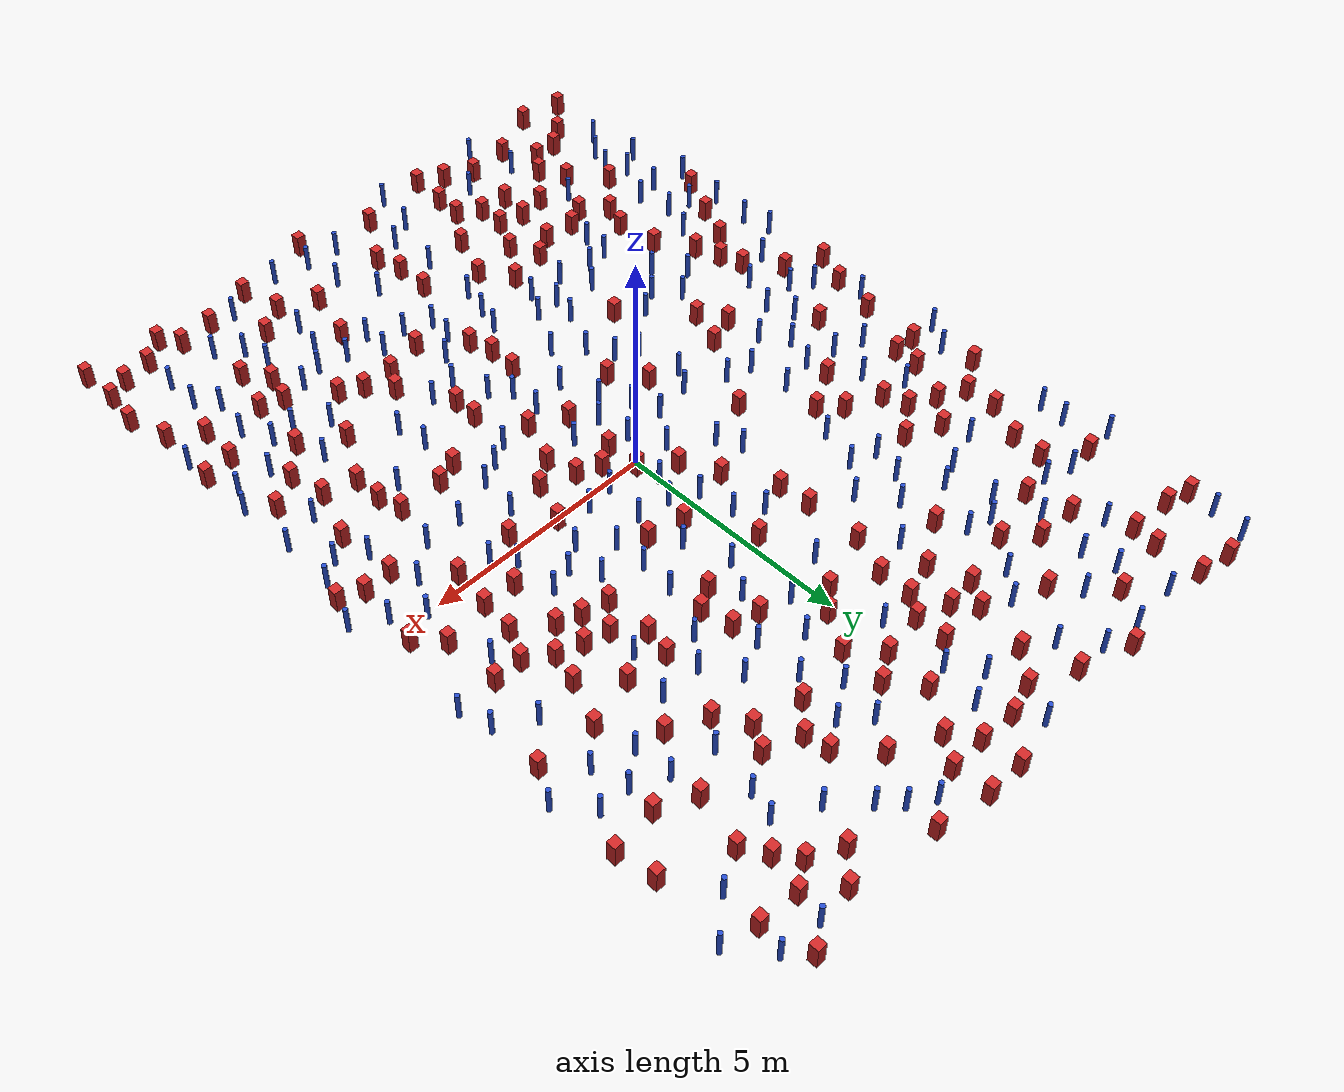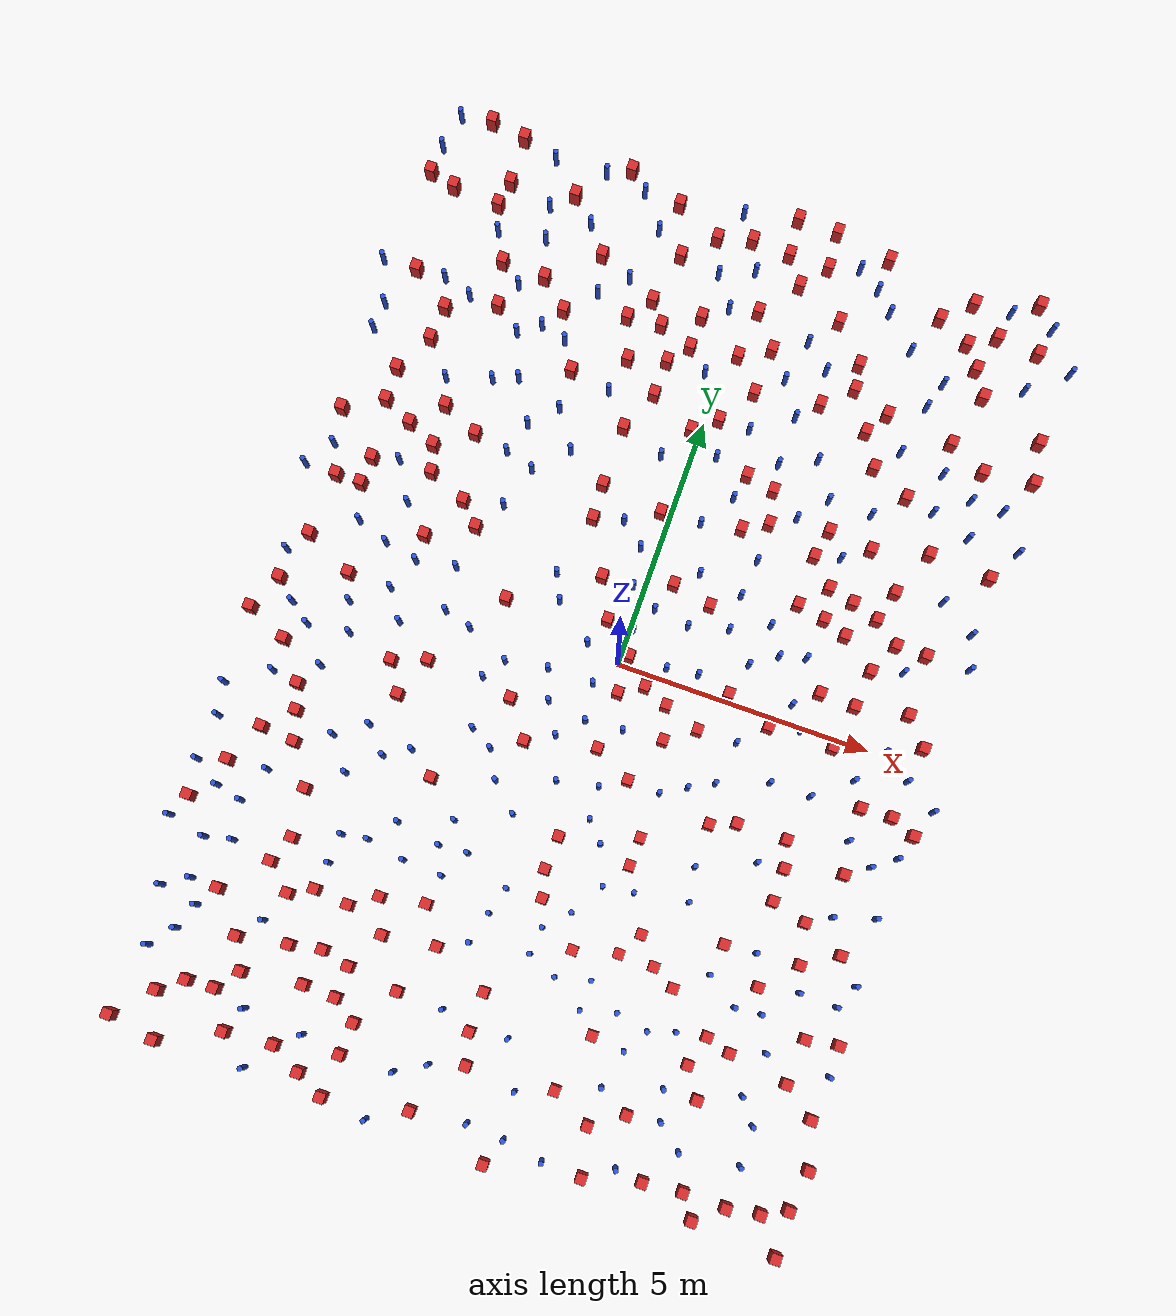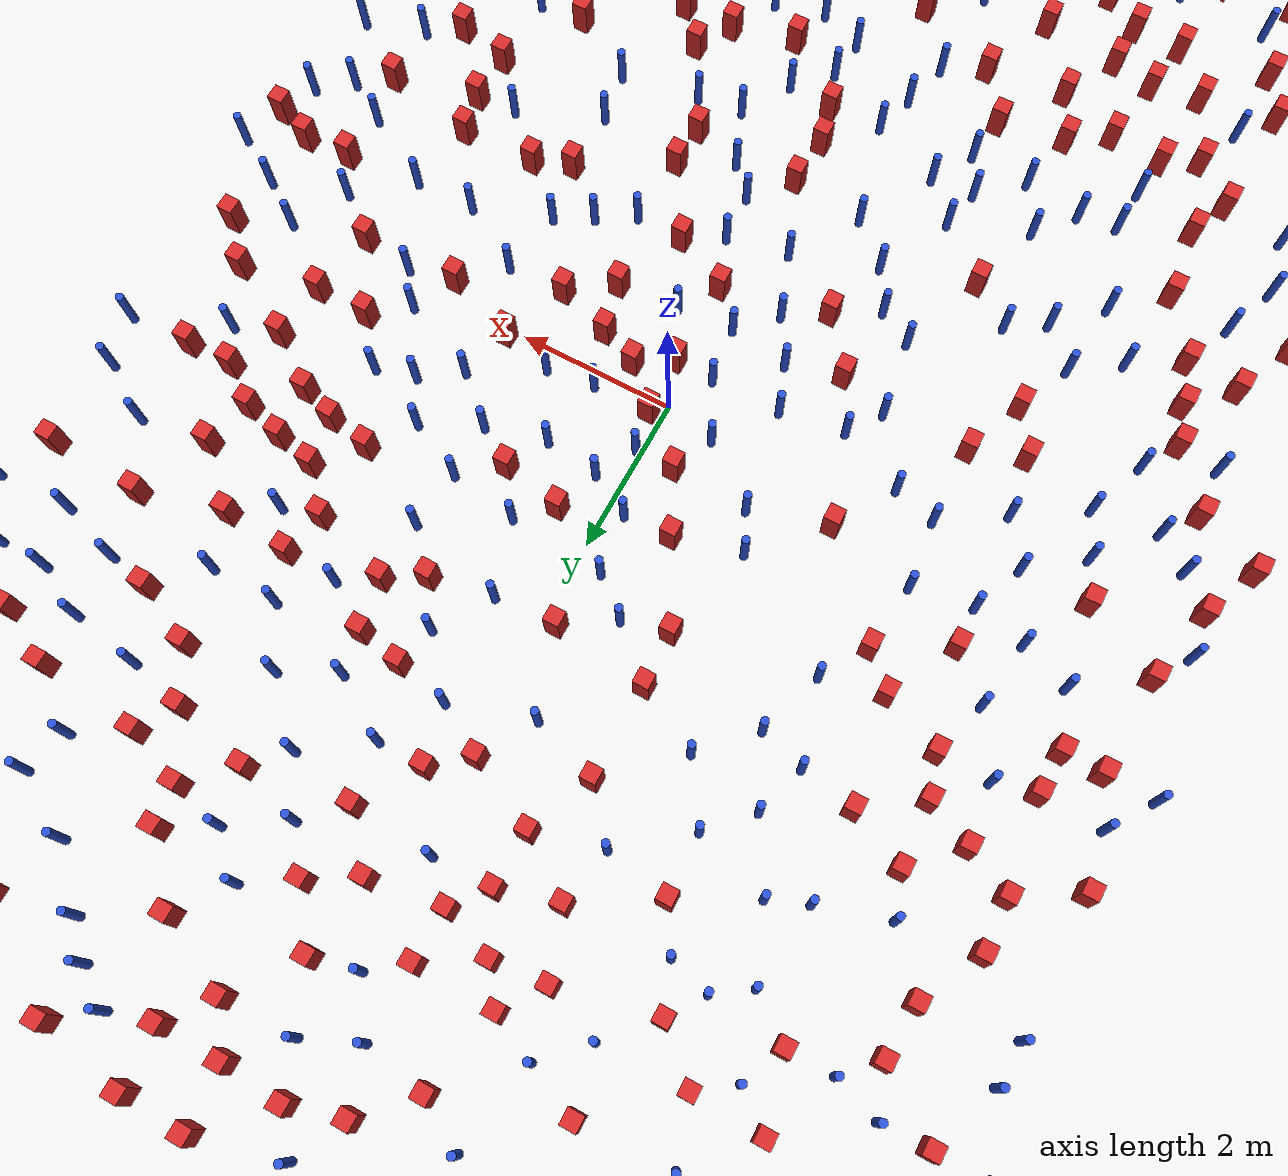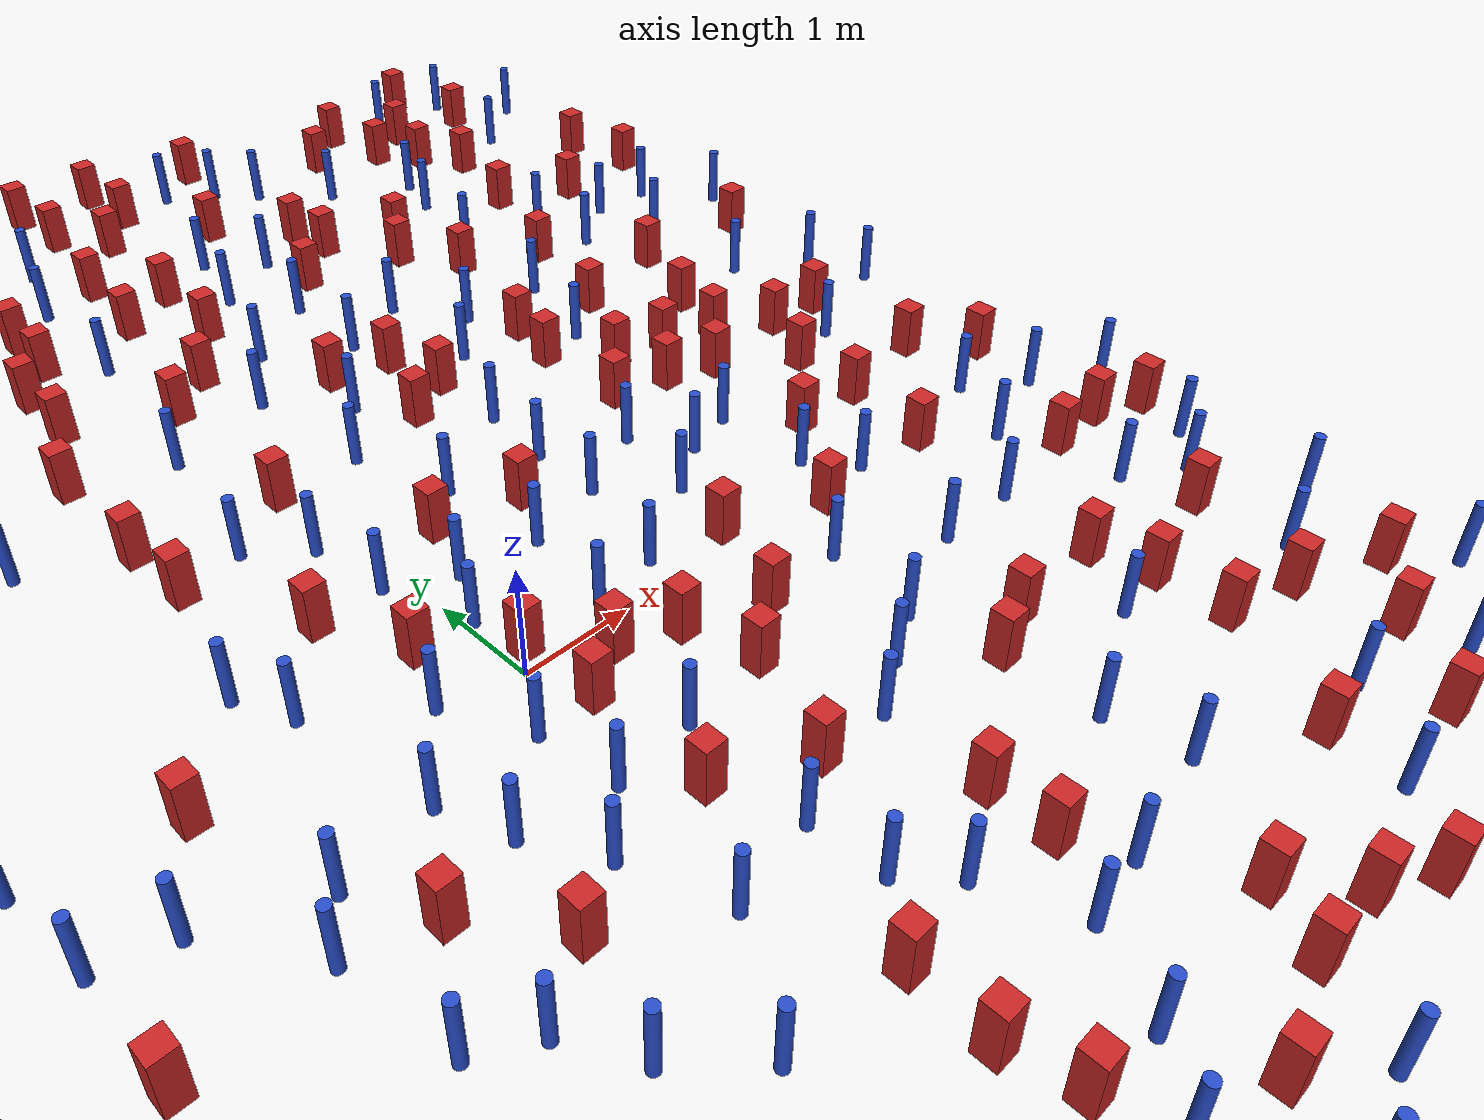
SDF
<sdf version="1.6">
  <model name="dense_94"><model name="pole_obstacle0">
  <static>true</static>
  <pose frame="">3.38922952658 -7.14174087017 -9.47619616065e-06 5.49618799738e-07 2.3631041406e-07 -1.55090534801e-07</pose>
  <link name="link">
  <pose frame="">0 0 0.3 0 -0 0</pose>
    <inertial>
      <mass>1</mass>
      <inertia>
        <ixx>0.145833</ixx>
        <ixy>0</ixy>
        <ixz>0</ixz>
        <iyy>0.145833</iyy>
        <iyz>0</iyz>
        <izz>0.125</izz>
      </inertia>
    </inertial>
    <collision name="collision">
      <geometry>
        <cylinder>
          <radius>0.05</radius>
          <length>.6</length>
        </cylinder>
      </geometry>
      <max_contacts>10</max_contacts>
      <surface>
        <contact>
          <ode/>
        </contact>
        <bounce/>
        <friction>
          <torsional>
            <ode/>
          </torsional>
          <ode/>
        </friction>
      </surface>
    </collision>
    <visual name="visual">
      <geometry>
        <cylinder>
          <radius>0.05</radius>
          <length>.6</length>
        </cylinder>
      </geometry>
      <material>
        <script>
          <name>Gazebo/Blue</name>
          <uri>file://media/materials/scripts/gazebo.material</uri>
        </script>
      </material>
    </visual>
    <self_collide>0</self_collide>
    <kinematic>0</kinematic>
  </link>
</model>
<model name="pole_obstacle1">
  <static>true</static>
  <pose frame="">-6.67899907143 -0.03429082158 -9.47619616065e-06 5.49618799737e-07 2.36310414061e-07 -1.55090534802e-07</pose>
  <link name="link">
  <pose frame="">0 0 0.3 0 -0 0</pose>
    <inertial>
      <mass>1</mass>
      <inertia>
        <ixx>0.145833</ixx>
        <ixy>0</ixy>
        <ixz>0</ixz>
        <iyy>0.145833</iyy>
        <iyz>0</iyz>
        <izz>0.125</izz>
      </inertia>
    </inertial>
    <collision name="collision">
      <geometry>
        <cylinder>
          <radius>0.05</radius>
          <length>.6</length>
        </cylinder>
      </geometry>
      <max_contacts>10</max_contacts>
      <surface>
        <contact>
          <ode/>
        </contact>
        <bounce/>
        <friction>
          <torsional>
            <ode/>
          </torsional>
          <ode/>
        </friction>
      </surface>
    </collision>
    <visual name="visual">
      <geometry>
        <cylinder>
          <radius>0.05</radius>
          <length>.6</length>
        </cylinder>
      </geometry>
      <material>
        <script>
          <name>Gazebo/Blue</name>
          <uri>file://media/materials/scripts/gazebo.material</uri>
        </script>
      </material>
    </visual>
    <self_collide>0</self_collide>
    <kinematic>0</kinematic>
  </link>
</model>
<model name="square_post_obstacle0">
  <static>true</static>
  <pose frame="">-1.67822141153 -1.31665792299 -6.11067671241e-07 -5.50515727128e-06 -8.79689657224e-07 2.37013304536e-05</pose>
  <link name="link">
    <pose frame="">0 0 0.25 0 -0 0</pose>
    <inertial>
      <mass>100</mass>
      <inertia>
        <ixx>0.166667</ixx>
        <ixy>0</ixy>
        <ixz>0</ixz>
        <iyy>0.166667</iyy>
        <iyz>0</iyz>
        <izz>0.166667</izz>
      </inertia>
    </inertial>
    <collision name="collision">
      <geometry>
        <box>
          <size>.2 .2 .5</size>
        </box>
      </geometry>
      <max_contacts>10</max_contacts>
      <surface>
        <contact>
          <ode/>
        </contact>
        <bounce/>
        <friction>
          <torsional>
            <ode/>
          </torsional>
          <ode/>
        </friction>
      </surface>
    </collision>
    <visual name="visual">
      <geometry>
        <box>
          <size>.2 .2 .5</size>
        </box>
      </geometry>
      <material>
        <script>
          <name>Gazebo/Red</name>
          <uri>file://media/materials/scripts/gazebo.material</uri>
        </script>
      </material>
    </visual>
    <self_collide>0</self_collide>
    <kinematic>0</kinematic>
  </link>
</model>
<model name="square_post_obstacle1">
  <static>true</static>
  <pose frame="">-6.61234218189 -9.25222904209 -6.11067671241e-07 -5.50515727128e-06 -8.79689657224e-07 2.37013304536e-05</pose>
  <link name="link">
    <pose frame="">0 0 0.25 0 -0 0</pose>
    <inertial>
      <mass>100</mass>
      <inertia>
        <ixx>0.166667</ixx>
        <ixy>0</ixy>
        <ixz>0</ixz>
        <iyy>0.166667</iyy>
        <iyz>0</iyz>
        <izz>0.166667</izz>
      </inertia>
    </inertial>
    <collision name="collision">
      <geometry>
        <box>
          <size>.2 .2 .5</size>
        </box>
      </geometry>
      <max_contacts>10</max_contacts>
      <surface>
        <contact>
          <ode/>
        </contact>
        <bounce/>
        <friction>
          <torsional>
            <ode/>
          </torsional>
          <ode/>
        </friction>
      </surface>
    </collision>
    <visual name="visual">
      <geometry>
        <box>
          <size>.2 .2 .5</size>
        </box>
      </geometry>
      <material>
        <script>
          <name>Gazebo/Red</name>
          <uri>file://media/materials/scripts/gazebo.material</uri>
        </script>
      </material>
    </visual>
    <self_collide>0</self_collide>
    <kinematic>0</kinematic>
  </link>
</model>
<model name="pole_obstacle2">
  <static>true</static>
  <pose frame="">1.63536920338 5.65598583855 -9.47619616065e-06 5.49618799737e-07 2.36310414061e-07 -1.550905348e-07</pose>
  <link name="link">
  <pose frame="">0 0 0.3 0 -0 0</pose>
    <inertial>
      <mass>1</mass>
      <inertia>
        <ixx>0.145833</ixx>
        <ixy>0</ixy>
        <ixz>0</ixz>
        <iyy>0.145833</iyy>
        <iyz>0</iyz>
        <izz>0.125</izz>
      </inertia>
    </inertial>
    <collision name="collision">
      <geometry>
        <cylinder>
          <radius>0.05</radius>
          <length>.6</length>
        </cylinder>
      </geometry>
      <max_contacts>10</max_contacts>
      <surface>
        <contact>
          <ode/>
        </contact>
        <bounce/>
        <friction>
          <torsional>
            <ode/>
          </torsional>
          <ode/>
        </friction>
      </surface>
    </collision>
    <visual name="visual">
      <geometry>
        <cylinder>
          <radius>0.05</radius>
          <length>.6</length>
        </cylinder>
      </geometry>
      <material>
        <script>
          <name>Gazebo/Blue</name>
          <uri>file://media/materials/scripts/gazebo.material</uri>
        </script>
      </material>
    </visual>
    <self_collide>0</self_collide>
    <kinematic>0</kinematic>
  </link>
</model>
<model name="pole_obstacle3">
  <static>true</static>
  <pose frame="">1.85166575213 2.73156434735 -9.47619616065e-06 5.49618799737e-07 2.36310414062e-07 -1.55090534798e-07</pose>
  <link name="link">
  <pose frame="">0 0 0.3 0 -0 0</pose>
    <inertial>
      <mass>1</mass>
      <inertia>
        <ixx>0.145833</ixx>
        <ixy>0</ixy>
        <ixz>0</ixz>
        <iyy>0.145833</iyy>
        <iyz>0</iyz>
        <izz>0.125</izz>
      </inertia>
    </inertial>
    <collision name="collision">
      <geometry>
        <cylinder>
          <radius>0.05</radius>
          <length>.6</length>
        </cylinder>
      </geometry>
      <max_contacts>10</max_contacts>
      <surface>
        <contact>
          <ode/>
        </contact>
        <bounce/>
        <friction>
          <torsional>
            <ode/>
          </torsional>
          <ode/>
        </friction>
      </surface>
    </collision>
    <visual name="visual">
      <geometry>
        <cylinder>
          <radius>0.05</radius>
          <length>.6</length>
        </cylinder>
      </geometry>
      <material>
        <script>
          <name>Gazebo/Blue</name>
          <uri>file://media/materials/scripts/gazebo.material</uri>
        </script>
      </material>
    </visual>
    <self_collide>0</self_collide>
    <kinematic>0</kinematic>
  </link>
</model>
<model name="pole_obstacle4">
  <static>true</static>
  <pose frame="">6.12299116142 -4.23294634951 -9.47619616065e-06 5.49618799737e-07 2.36310414037e-07 -1.55090534814e-07</pose>
  <link name="link">
  <pose frame="">0 0 0.3 0 -0 0</pose>
    <inertial>
      <mass>1</mass>
      <inertia>
        <ixx>0.145833</ixx>
        <ixy>0</ixy>
        <ixz>0</ixz>
        <iyy>0.145833</iyy>
        <iyz>0</iyz>
        <izz>0.125</izz>
      </inertia>
    </inertial>
    <collision name="collision">
      <geometry>
        <cylinder>
          <radius>0.05</radius>
          <length>.6</length>
        </cylinder>
      </geometry>
      <max_contacts>10</max_contacts>
      <surface>
        <contact>
          <ode/>
        </contact>
        <bounce/>
        <friction>
          <torsional>
            <ode/>
          </torsional>
          <ode/>
        </friction>
      </surface>
    </collision>
    <visual name="visual">
      <geometry>
        <cylinder>
          <radius>0.05</radius>
          <length>.6</length>
        </cylinder>
      </geometry>
      <material>
        <script>
          <name>Gazebo/Blue</name>
          <uri>file://media/materials/scripts/gazebo.material</uri>
        </script>
      </material>
    </visual>
    <self_collide>0</self_collide>
    <kinematic>0</kinematic>
  </link>
</model>
<model name="pole_obstacle5">
  <static>true</static>
  <pose frame="">-6.22073682573 -0.947302004882 -9.47619616065e-06 5.49618799737e-07 2.36310414061e-07 -1.550905348e-07</pose>
  <link name="link">
  <pose frame="">0 0 0.3 0 -0 0</pose>
    <inertial>
      <mass>1</mass>
      <inertia>
        <ixx>0.145833</ixx>
        <ixy>0</ixy>
        <ixz>0</ixz>
        <iyy>0.145833</iyy>
        <iyz>0</iyz>
        <izz>0.125</izz>
      </inertia>
    </inertial>
    <collision name="collision">
      <geometry>
        <cylinder>
          <radius>0.05</radius>
          <length>.6</length>
        </cylinder>
      </geometry>
      <max_contacts>10</max_contacts>
      <surface>
        <contact>
          <ode/>
        </contact>
        <bounce/>
        <friction>
          <torsional>
            <ode/>
          </torsional>
          <ode/>
        </friction>
      </surface>
    </collision>
    <visual name="visual">
      <geometry>
        <cylinder>
          <radius>0.05</radius>
          <length>.6</length>
        </cylinder>
      </geometry>
      <material>
        <script>
          <name>Gazebo/Blue</name>
          <uri>file://media/materials/scripts/gazebo.material</uri>
        </script>
      </material>
    </visual>
    <self_collide>0</self_collide>
    <kinematic>0</kinematic>
  </link>
</model>
<model name="pole_obstacle6">
  <static>true</static>
  <pose frame="">-6.68948350225 8.57907107979 -9.47619616065e-06 5.49618799737e-07 2.36310414065e-07 -1.55090534796e-07</pose>
  <link name="link">
  <pose frame="">0 0 0.3 0 -0 0</pose>
    <inertial>
      <mass>1</mass>
      <inertia>
        <ixx>0.145833</ixx>
        <ixy>0</ixy>
        <ixz>0</ixz>
        <iyy>0.145833</iyy>
        <iyz>0</iyz>
        <izz>0.125</izz>
      </inertia>
    </inertial>
    <collision name="collision">
      <geometry>
        <cylinder>
          <radius>0.05</radius>
          <length>.6</length>
        </cylinder>
      </geometry>
      <max_contacts>10</max_contacts>
      <surface>
        <contact>
          <ode/>
        </contact>
        <bounce/>
        <friction>
          <torsional>
            <ode/>
          </torsional>
          <ode/>
        </friction>
      </surface>
    </collision>
    <visual name="visual">
      <geometry>
        <cylinder>
          <radius>0.05</radius>
          <length>.6</length>
        </cylinder>
      </geometry>
      <material>
        <script>
          <name>Gazebo/Blue</name>
          <uri>file://media/materials/scripts/gazebo.material</uri>
        </script>
      </material>
    </visual>
    <self_collide>0</self_collide>
    <kinematic>0</kinematic>
  </link>
</model>
<model name="square_post_obstacle2">
  <static>true</static>
  <pose frame="">1.28413385972 8.73851189312 -6.11067671241e-07 -5.50515727128e-06 -8.79689657224e-07 2.37013304536e-05</pose>
  <link name="link">
    <pose frame="">0 0 0.25 0 -0 0</pose>
    <inertial>
      <mass>100</mass>
      <inertia>
        <ixx>0.166667</ixx>
        <ixy>0</ixy>
        <ixz>0</ixz>
        <iyy>0.166667</iyy>
        <iyz>0</iyz>
        <izz>0.166667</izz>
      </inertia>
    </inertial>
    <collision name="collision">
      <geometry>
        <box>
          <size>.2 .2 .5</size>
        </box>
      </geometry>
      <max_contacts>10</max_contacts>
      <surface>
        <contact>
          <ode/>
        </contact>
        <bounce/>
        <friction>
          <torsional>
            <ode/>
          </torsional>
          <ode/>
        </friction>
      </surface>
    </collision>
    <visual name="visual">
      <geometry>
        <box>
          <size>.2 .2 .5</size>
        </box>
      </geometry>
      <material>
        <script>
          <name>Gazebo/Red</name>
          <uri>file://media/materials/scripts/gazebo.material</uri>
        </script>
      </material>
    </visual>
    <self_collide>0</self_collide>
    <kinematic>0</kinematic>
  </link>
</model>
<model name="square_post_obstacle3">
  <static>true</static>
  <pose frame="">5.75948002975 -8.64291530314 -6.11067671241e-07 -5.50515727128e-06 -8.79689657224e-07 2.37013304536e-05</pose>
  <link name="link">
    <pose frame="">0 0 0.25 0 -0 0</pose>
    <inertial>
      <mass>100</mass>
      <inertia>
        <ixx>0.166667</ixx>
        <ixy>0</ixy>
        <ixz>0</ixz>
        <iyy>0.166667</iyy>
        <iyz>0</iyz>
        <izz>0.166667</izz>
      </inertia>
    </inertial>
    <collision name="collision">
      <geometry>
        <box>
          <size>.2 .2 .5</size>
        </box>
      </geometry>
      <max_contacts>10</max_contacts>
      <surface>
        <contact>
          <ode/>
        </contact>
        <bounce/>
        <friction>
          <torsional>
            <ode/>
          </torsional>
          <ode/>
        </friction>
      </surface>
    </collision>
    <visual name="visual">
      <geometry>
        <box>
          <size>.2 .2 .5</size>
        </box>
      </geometry>
      <material>
        <script>
          <name>Gazebo/Red</name>
          <uri>file://media/materials/scripts/gazebo.material</uri>
        </script>
      </material>
    </visual>
    <self_collide>0</self_collide>
    <kinematic>0</kinematic>
  </link>
</model>
<model name="square_post_obstacle4">
  <static>true</static>
  <pose frame="">-3.96534316025 -6.98792957776 -6.11067671241e-07 -5.50515727128e-06 -8.79689657224e-07 2.37013304536e-05</pose>
  <link name="link">
    <pose frame="">0 0 0.25 0 -0 0</pose>
    <inertial>
      <mass>100</mass>
      <inertia>
        <ixx>0.166667</ixx>
        <ixy>0</ixy>
        <ixz>0</ixz>
        <iyy>0.166667</iyy>
        <iyz>0</iyz>
        <izz>0.166667</izz>
      </inertia>
    </inertial>
    <collision name="collision">
      <geometry>
        <box>
          <size>.2 .2 .5</size>
        </box>
      </geometry>
      <max_contacts>10</max_contacts>
      <surface>
        <contact>
          <ode/>
        </contact>
        <bounce/>
        <friction>
          <torsional>
            <ode/>
          </torsional>
          <ode/>
        </friction>
      </surface>
    </collision>
    <visual name="visual">
      <geometry>
        <box>
          <size>.2 .2 .5</size>
        </box>
      </geometry>
      <material>
        <script>
          <name>Gazebo/Red</name>
          <uri>file://media/materials/scripts/gazebo.material</uri>
        </script>
      </material>
    </visual>
    <self_collide>0</self_collide>
    <kinematic>0</kinematic>
  </link>
</model>
<model name="pole_obstacle7">
  <static>true</static>
  <pose frame="">3.62072664661 4.30841602605 -9.47619616065e-06 5.49618799738e-07 2.3631041406e-07 -1.55090534801e-07</pose>
  <link name="link">
  <pose frame="">0 0 0.3 0 -0 0</pose>
    <inertial>
      <mass>1</mass>
      <inertia>
        <ixx>0.145833</ixx>
        <ixy>0</ixy>
        <ixz>0</ixz>
        <iyy>0.145833</iyy>
        <iyz>0</iyz>
        <izz>0.125</izz>
      </inertia>
    </inertial>
    <collision name="collision">
      <geometry>
        <cylinder>
          <radius>0.05</radius>
          <length>.6</length>
        </cylinder>
      </geometry>
      <max_contacts>10</max_contacts>
      <surface>
        <contact>
          <ode/>
        </contact>
        <bounce/>
        <friction>
          <torsional>
            <ode/>
          </torsional>
          <ode/>
        </friction>
      </surface>
    </collision>
    <visual name="visual">
      <geometry>
        <cylinder>
          <radius>0.05</radius>
          <length>.6</length>
        </cylinder>
      </geometry>
      <material>
        <script>
          <name>Gazebo/Blue</name>
          <uri>file://media/materials/scripts/gazebo.material</uri>
        </script>
      </material>
    </visual>
    <self_collide>0</self_collide>
    <kinematic>0</kinematic>
  </link>
</model>
<model name="pole_obstacle8">
  <static>true</static>
  <pose frame="">-4.99658444194 4.15690129705 -9.47619616065e-06 5.49618799737e-07 2.36310414037e-07 -1.55090534814e-07</pose>
  <link name="link">
  <pose frame="">0 0 0.3 0 -0 0</pose>
    <inertial>
      <mass>1</mass>
      <inertia>
        <ixx>0.145833</ixx>
        <ixy>0</ixy>
        <ixz>0</ixz>
        <iyy>0.145833</iyy>
        <iyz>0</iyz>
        <izz>0.125</izz>
      </inertia>
    </inertial>
    <collision name="collision">
      <geometry>
        <cylinder>
          <radius>0.05</radius>
          <length>.6</length>
        </cylinder>
      </geometry>
      <max_contacts>10</max_contacts>
      <surface>
        <contact>
          <ode/>
        </contact>
        <bounce/>
        <friction>
          <torsional>
            <ode/>
          </torsional>
          <ode/>
        </friction>
      </surface>
    </collision>
    <visual name="visual">
      <geometry>
        <cylinder>
          <radius>0.05</radius>
          <length>.6</length>
        </cylinder>
      </geometry>
      <material>
        <script>
          <name>Gazebo/Blue</name>
          <uri>file://media/materials/scripts/gazebo.material</uri>
        </script>
      </material>
    </visual>
    <self_collide>0</self_collide>
    <kinematic>0</kinematic>
  </link>
</model>
<model name="square_post_obstacle5">
  <static>true</static>
  <pose frame="">5.68144355418 -3.79377628186 -6.11067671241e-07 -5.50515727128e-06 -8.79689657224e-07 2.37013304536e-05</pose>
  <link name="link">
    <pose frame="">0 0 0.25 0 -0 0</pose>
    <inertial>
      <mass>100</mass>
      <inertia>
        <ixx>0.166667</ixx>
        <ixy>0</ixy>
        <ixz>0</ixz>
        <iyy>0.166667</iyy>
        <iyz>0</iyz>
        <izz>0.166667</izz>
      </inertia>
    </inertial>
    <collision name="collision">
      <geometry>
        <box>
          <size>.2 .2 .5</size>
        </box>
      </geometry>
      <max_contacts>10</max_contacts>
      <surface>
        <contact>
          <ode/>
        </contact>
        <bounce/>
        <friction>
          <torsional>
            <ode/>
          </torsional>
          <ode/>
        </friction>
      </surface>
    </collision>
    <visual name="visual">
      <geometry>
        <box>
          <size>.2 .2 .5</size>
        </box>
      </geometry>
      <material>
        <script>
          <name>Gazebo/Red</name>
          <uri>file://media/materials/scripts/gazebo.material</uri>
        </script>
      </material>
    </visual>
    <self_collide>0</self_collide>
    <kinematic>0</kinematic>
  </link>
</model>
<model name="square_post_obstacle6">
  <static>true</static>
  <pose frame="">-5.55545199859 -2.38299773573 -6.11067671241e-07 -5.50515727128e-06 -8.79689657224e-07 2.37013304536e-05</pose>
  <link name="link">
    <pose frame="">0 0 0.25 0 -0 0</pose>
    <inertial>
      <mass>100</mass>
      <inertia>
        <ixx>0.166667</ixx>
        <ixy>0</ixy>
        <ixz>0</ixz>
        <iyy>0.166667</iyy>
        <iyz>0</iyz>
        <izz>0.166667</izz>
      </inertia>
    </inertial>
    <collision name="collision">
      <geometry>
        <box>
          <size>.2 .2 .5</size>
        </box>
      </geometry>
      <max_contacts>10</max_contacts>
      <surface>
        <contact>
          <ode/>
        </contact>
        <bounce/>
        <friction>
          <torsional>
            <ode/>
          </torsional>
          <ode/>
        </friction>
      </surface>
    </collision>
    <visual name="visual">
      <geometry>
        <box>
          <size>.2 .2 .5</size>
        </box>
      </geometry>
      <material>
        <script>
          <name>Gazebo/Red</name>
          <uri>file://media/materials/scripts/gazebo.material</uri>
        </script>
      </material>
    </visual>
    <self_collide>0</self_collide>
    <kinematic>0</kinematic>
  </link>
</model>
<model name="square_post_obstacle7">
  <static>true</static>
  <pose frame="">3.37304363097 5.20476493427 -6.11067671241e-07 -5.50515727128e-06 -8.79689657224e-07 2.37013304536e-05</pose>
  <link name="link">
    <pose frame="">0 0 0.25 0 -0 0</pose>
    <inertial>
      <mass>100</mass>
      <inertia>
        <ixx>0.166667</ixx>
        <ixy>0</ixy>
        <ixz>0</ixz>
        <iyy>0.166667</iyy>
        <iyz>0</iyz>
        <izz>0.166667</izz>
      </inertia>
    </inertial>
    <collision name="collision">
      <geometry>
        <box>
          <size>.2 .2 .5</size>
        </box>
      </geometry>
      <max_contacts>10</max_contacts>
      <surface>
        <contact>
          <ode/>
        </contact>
        <bounce/>
        <friction>
          <torsional>
            <ode/>
          </torsional>
          <ode/>
        </friction>
      </surface>
    </collision>
    <visual name="visual">
      <geometry>
        <box>
          <size>.2 .2 .5</size>
        </box>
      </geometry>
      <material>
        <script>
          <name>Gazebo/Red</name>
          <uri>file://media/materials/scripts/gazebo.material</uri>
        </script>
      </material>
    </visual>
    <self_collide>0</self_collide>
    <kinematic>0</kinematic>
  </link>
</model>
<model name="pole_obstacle9">
  <static>true</static>
  <pose frame="">5.43425817612 3.14929889037 -9.47619616065e-06 5.49618799738e-07 2.36310414051e-07 -1.55090534805e-07</pose>
  <link name="link">
  <pose frame="">0 0 0.3 0 -0 0</pose>
    <inertial>
      <mass>1</mass>
      <inertia>
        <ixx>0.145833</ixx>
        <ixy>0</ixy>
        <ixz>0</ixz>
        <iyy>0.145833</iyy>
        <iyz>0</iyz>
        <izz>0.125</izz>
      </inertia>
    </inertial>
    <collision name="collision">
      <geometry>
        <cylinder>
          <radius>0.05</radius>
          <length>.6</length>
        </cylinder>
      </geometry>
      <max_contacts>10</max_contacts>
      <surface>
        <contact>
          <ode/>
        </contact>
        <bounce/>
        <friction>
          <torsional>
            <ode/>
          </torsional>
          <ode/>
        </friction>
      </surface>
    </collision>
    <visual name="visual">
      <geometry>
        <cylinder>
          <radius>0.05</radius>
          <length>.6</length>
        </cylinder>
      </geometry>
      <material>
        <script>
          <name>Gazebo/Blue</name>
          <uri>file://media/materials/scripts/gazebo.material</uri>
        </script>
      </material>
    </visual>
    <self_collide>0</self_collide>
    <kinematic>0</kinematic>
  </link>
</model>
<model name="pole_obstacle10">
  <static>true</static>
  <pose frame="">-3.80866569778 -5.33983282003 -9.47619616065e-06 5.49618799738e-07 2.3631041406e-07 -1.55090534801e-07</pose>
  <link name="link">
  <pose frame="">0 0 0.3 0 -0 0</pose>
    <inertial>
      <mass>1</mass>
      <inertia>
        <ixx>0.145833</ixx>
        <ixy>0</ixy>
        <ixz>0</ixz>
        <iyy>0.145833</iyy>
        <iyz>0</iyz>
        <izz>0.125</izz>
      </inertia>
    </inertial>
    <collision name="collision">
      <geometry>
        <cylinder>
          <radius>0.05</radius>
          <length>.6</length>
        </cylinder>
      </geometry>
      <max_contacts>10</max_contacts>
      <surface>
        <contact>
          <ode/>
        </contact>
        <bounce/>
        <friction>
          <torsional>
            <ode/>
          </torsional>
          <ode/>
        </friction>
      </surface>
    </collision>
    <visual name="visual">
      <geometry>
        <cylinder>
          <radius>0.05</radius>
          <length>.6</length>
        </cylinder>
      </geometry>
      <material>
        <script>
          <name>Gazebo/Blue</name>
          <uri>file://media/materials/scripts/gazebo.material</uri>
        </script>
      </material>
    </visual>
    <self_collide>0</self_collide>
    <kinematic>0</kinematic>
  </link>
</model>
<model name="pole_obstacle11">
  <static>true</static>
  <pose frame="">5.85307790812 -0.320496310252 -9.47619616065e-06 5.49618799737e-07 2.36310414057e-07 -1.55090534802e-07</pose>
  <link name="link">
  <pose frame="">0 0 0.3 0 -0 0</pose>
    <inertial>
      <mass>1</mass>
      <inertia>
        <ixx>0.145833</ixx>
        <ixy>0</ixy>
        <ixz>0</ixz>
        <iyy>0.145833</iyy>
        <iyz>0</iyz>
        <izz>0.125</izz>
      </inertia>
    </inertial>
    <collision name="collision">
      <geometry>
        <cylinder>
          <radius>0.05</radius>
          <length>.6</length>
        </cylinder>
      </geometry>
      <max_contacts>10</max_contacts>
      <surface>
        <contact>
          <ode/>
        </contact>
        <bounce/>
        <friction>
          <torsional>
            <ode/>
          </torsional>
          <ode/>
        </friction>
      </surface>
    </collision>
    <visual name="visual">
      <geometry>
        <cylinder>
          <radius>0.05</radius>
          <length>.6</length>
        </cylinder>
      </geometry>
      <material>
        <script>
          <name>Gazebo/Blue</name>
          <uri>file://media/materials/scripts/gazebo.material</uri>
        </script>
      </material>
    </visual>
    <self_collide>0</self_collide>
    <kinematic>0</kinematic>
  </link>
</model>
<model name="pole_obstacle12">
  <static>true</static>
  <pose frame="">0.89969291572 0.201560799494 -9.47619616065e-06 5.49618799737e-07 2.36310414064e-07 -1.55090534797e-07</pose>
  <link name="link">
  <pose frame="">0 0 0.3 0 -0 0</pose>
    <inertial>
      <mass>1</mass>
      <inertia>
        <ixx>0.145833</ixx>
        <ixy>0</ixy>
        <ixz>0</ixz>
        <iyy>0.145833</iyy>
        <iyz>0</iyz>
        <izz>0.125</izz>
      </inertia>
    </inertial>
    <collision name="collision">
      <geometry>
        <cylinder>
          <radius>0.05</radius>
          <length>.6</length>
        </cylinder>
      </geometry>
      <max_contacts>10</max_contacts>
      <surface>
        <contact>
          <ode/>
        </contact>
        <bounce/>
        <friction>
          <torsional>
            <ode/>
          </torsional>
          <ode/>
        </friction>
      </surface>
    </collision>
    <visual name="visual">
      <geometry>
        <cylinder>
          <radius>0.05</radius>
          <length>.6</length>
        </cylinder>
      </geometry>
      <material>
        <script>
          <name>Gazebo/Blue</name>
          <uri>file://media/materials/scripts/gazebo.material</uri>
        </script>
      </material>
    </visual>
    <self_collide>0</self_collide>
    <kinematic>0</kinematic>
  </link>
</model>
<model name="square_post_obstacle8">
  <static>true</static>
  <pose frame="">-1.73617687077 6.9707020237 -6.11067671241e-07 -5.50515727128e-06 -8.79689657224e-07 2.37013304536e-05</pose>
  <link name="link">
    <pose frame="">0 0 0.25 0 -0 0</pose>
    <inertial>
      <mass>100</mass>
      <inertia>
        <ixx>0.166667</ixx>
        <ixy>0</ixy>
        <ixz>0</ixz>
        <iyy>0.166667</iyy>
        <iyz>0</iyz>
        <izz>0.166667</izz>
      </inertia>
    </inertial>
    <collision name="collision">
      <geometry>
        <box>
          <size>.2 .2 .5</size>
        </box>
      </geometry>
      <max_contacts>10</max_contacts>
      <surface>
        <contact>
          <ode/>
        </contact>
        <bounce/>
        <friction>
          <torsional>
            <ode/>
          </torsional>
          <ode/>
        </friction>
      </surface>
    </collision>
    <visual name="visual">
      <geometry>
        <box>
          <size>.2 .2 .5</size>
        </box>
      </geometry>
      <material>
        <script>
          <name>Gazebo/Red</name>
          <uri>file://media/materials/scripts/gazebo.material</uri>
        </script>
      </material>
    </visual>
    <self_collide>0</self_collide>
    <kinematic>0</kinematic>
  </link>
</model>
<model name="square_post_obstacle9">
  <static>true</static>
  <pose frame="">-2.40884904298 -6.25458285325 -6.11067671241e-07 -5.50515727128e-06 -8.79689657224e-07 2.37013304536e-05</pose>
  <link name="link">
    <pose frame="">0 0 0.25 0 -0 0</pose>
    <inertial>
      <mass>100</mass>
      <inertia>
        <ixx>0.166667</ixx>
        <ixy>0</ixy>
        <ixz>0</ixz>
        <iyy>0.166667</iyy>
        <iyz>0</iyz>
        <izz>0.166667</izz>
      </inertia>
    </inertial>
    <collision name="collision">
      <geometry>
        <box>
          <size>.2 .2 .5</size>
        </box>
      </geometry>
      <max_contacts>10</max_contacts>
      <surface>
        <contact>
          <ode/>
        </contact>
        <bounce/>
        <friction>
          <torsional>
            <ode/>
          </torsional>
          <ode/>
        </friction>
      </surface>
    </collision>
    <visual name="visual">
      <geometry>
        <box>
          <size>.2 .2 .5</size>
        </box>
      </geometry>
      <material>
        <script>
          <name>Gazebo/Red</name>
          <uri>file://media/materials/scripts/gazebo.material</uri>
        </script>
      </material>
    </visual>
    <self_collide>0</self_collide>
    <kinematic>0</kinematic>
  </link>
</model>
<model name="pole_obstacle13">
  <static>true</static>
  <pose frame="">-1.35421657662 -8.49732423744 -9.47619616065e-06 5.49618799737e-07 2.36310414046e-07 -1.55090534809e-07</pose>
  <link name="link">
  <pose frame="">0 0 0.3 0 -0 0</pose>
    <inertial>
      <mass>1</mass>
      <inertia>
        <ixx>0.145833</ixx>
        <ixy>0</ixy>
        <ixz>0</ixz>
        <iyy>0.145833</iyy>
        <iyz>0</iyz>
        <izz>0.125</izz>
      </inertia>
    </inertial>
    <collision name="collision">
      <geometry>
        <cylinder>
          <radius>0.05</radius>
          <length>.6</length>
        </cylinder>
      </geometry>
      <max_contacts>10</max_contacts>
      <surface>
        <contact>
          <ode/>
        </contact>
        <bounce/>
        <friction>
          <torsional>
            <ode/>
          </torsional>
          <ode/>
        </friction>
      </surface>
    </collision>
    <visual name="visual">
      <geometry>
        <cylinder>
          <radius>0.05</radius>
          <length>.6</length>
        </cylinder>
      </geometry>
      <material>
        <script>
          <name>Gazebo/Blue</name>
          <uri>file://media/materials/scripts/gazebo.material</uri>
        </script>
      </material>
    </visual>
    <self_collide>0</self_collide>
    <kinematic>0</kinematic>
  </link>
</model>
<model name="square_post_obstacle10">
  <static>true</static>
  <pose frame="">4.31607230512 -8.74429017073 -6.11067671241e-07 -5.50515727128e-06 -8.79689657224e-07 2.37013304536e-05</pose>
  <link name="link">
    <pose frame="">0 0 0.25 0 -0 0</pose>
    <inertial>
      <mass>100</mass>
      <inertia>
        <ixx>0.166667</ixx>
        <ixy>0</ixy>
        <ixz>0</ixz>
        <iyy>0.166667</iyy>
        <iyz>0</iyz>
        <izz>0.166667</izz>
      </inertia>
    </inertial>
    <collision name="collision">
      <geometry>
        <box>
          <size>.2 .2 .5</size>
        </box>
      </geometry>
      <max_contacts>10</max_contacts>
      <surface>
        <contact>
          <ode/>
        </contact>
        <bounce/>
        <friction>
          <torsional>
            <ode/>
          </torsional>
          <ode/>
        </friction>
      </surface>
    </collision>
    <visual name="visual">
      <geometry>
        <box>
          <size>.2 .2 .5</size>
        </box>
      </geometry>
      <material>
        <script>
          <name>Gazebo/Red</name>
          <uri>file://media/materials/scripts/gazebo.material</uri>
        </script>
      </material>
    </visual>
    <self_collide>0</self_collide>
    <kinematic>0</kinematic>
  </link>
</model>
<model name="square_post_obstacle11">
  <static>true</static>
  <pose frame="">-4.53768418567 5.86658288188 -6.11067671241e-07 -5.50515727128e-06 -8.79689657224e-07 2.37013304536e-05</pose>
  <link name="link">
    <pose frame="">0 0 0.25 0 -0 0</pose>
    <inertial>
      <mass>100</mass>
      <inertia>
        <ixx>0.166667</ixx>
        <ixy>0</ixy>
        <ixz>0</ixz>
        <iyy>0.166667</iyy>
        <iyz>0</iyz>
        <izz>0.166667</izz>
      </inertia>
    </inertial>
    <collision name="collision">
      <geometry>
        <box>
          <size>.2 .2 .5</size>
        </box>
      </geometry>
      <max_contacts>10</max_contacts>
      <surface>
        <contact>
          <ode/>
        </contact>
        <bounce/>
        <friction>
          <torsional>
            <ode/>
          </torsional>
          <ode/>
        </friction>
      </surface>
    </collision>
    <visual name="visual">
      <geometry>
        <box>
          <size>.2 .2 .5</size>
        </box>
      </geometry>
      <material>
        <script>
          <name>Gazebo/Red</name>
          <uri>file://media/materials/scripts/gazebo.material</uri>
        </script>
      </material>
    </visual>
    <self_collide>0</self_collide>
    <kinematic>0</kinematic>
  </link>
</model>
<model name="pole_obstacle14">
  <static>true</static>
  <pose frame="">-0.848660396784 -5.84715833143 -9.47619616065e-06 5.49618799737e-07 2.36310414065e-07 -1.55090534796e-07</pose>
  <link name="link">
  <pose frame="">0 0 0.3 0 -0 0</pose>
    <inertial>
      <mass>1</mass>
      <inertia>
        <ixx>0.145833</ixx>
        <ixy>0</ixy>
        <ixz>0</ixz>
        <iyy>0.145833</iyy>
        <iyz>0</iyz>
        <izz>0.125</izz>
      </inertia>
    </inertial>
    <collision name="collision">
      <geometry>
        <cylinder>
          <radius>0.05</radius>
          <length>.6</length>
        </cylinder>
      </geometry>
      <max_contacts>10</max_contacts>
      <surface>
        <contact>
          <ode/>
        </contact>
        <bounce/>
        <friction>
          <torsional>
            <ode/>
          </torsional>
          <ode/>
        </friction>
      </surface>
    </collision>
    <visual name="visual">
      <geometry>
        <cylinder>
          <radius>0.05</radius>
          <length>.6</length>
        </cylinder>
      </geometry>
      <material>
        <script>
          <name>Gazebo/Blue</name>
          <uri>file://media/materials/scripts/gazebo.material</uri>
        </script>
      </material>
    </visual>
    <self_collide>0</self_collide>
    <kinematic>0</kinematic>
  </link>
</model>
<model name="pole_obstacle15">
  <static>true</static>
  <pose frame="">5.29335730917 0.0635979002742 -9.47619616065e-06 5.49618799737e-07 2.36310414076e-07 -1.55090534791e-07</pose>
  <link name="link">
  <pose frame="">0 0 0.3 0 -0 0</pose>
    <inertial>
      <mass>1</mass>
      <inertia>
        <ixx>0.145833</ixx>
        <ixy>0</ixy>
        <ixz>0</ixz>
        <iyy>0.145833</iyy>
        <iyz>0</iyz>
        <izz>0.125</izz>
      </inertia>
    </inertial>
    <collision name="collision">
      <geometry>
        <cylinder>
          <radius>0.05</radius>
          <length>.6</length>
        </cylinder>
      </geometry>
      <max_contacts>10</max_contacts>
      <surface>
        <contact>
          <ode/>
        </contact>
        <bounce/>
        <friction>
          <torsional>
            <ode/>
          </torsional>
          <ode/>
        </friction>
      </surface>
    </collision>
    <visual name="visual">
      <geometry>
        <cylinder>
          <radius>0.05</radius>
          <length>.6</length>
        </cylinder>
      </geometry>
      <material>
        <script>
          <name>Gazebo/Blue</name>
          <uri>file://media/materials/scripts/gazebo.material</uri>
        </script>
      </material>
    </visual>
    <self_collide>0</self_collide>
    <kinematic>0</kinematic>
  </link>
</model>
<model name="square_post_obstacle12">
  <static>true</static>
  <pose frame="">-6.30929738894 1.65366719307 -6.11067671241e-07 -5.50515727128e-06 -8.79689657224e-07 2.37013304536e-05</pose>
  <link name="link">
    <pose frame="">0 0 0.25 0 -0 0</pose>
    <inertial>
      <mass>100</mass>
      <inertia>
        <ixx>0.166667</ixx>
        <ixy>0</ixy>
        <ixz>0</ixz>
        <iyy>0.166667</iyy>
        <iyz>0</iyz>
        <izz>0.166667</izz>
      </inertia>
    </inertial>
    <collision name="collision">
      <geometry>
        <box>
          <size>.2 .2 .5</size>
        </box>
      </geometry>
      <max_contacts>10</max_contacts>
      <surface>
        <contact>
          <ode/>
        </contact>
        <bounce/>
        <friction>
          <torsional>
            <ode/>
          </torsional>
          <ode/>
        </friction>
      </surface>
    </collision>
    <visual name="visual">
      <geometry>
        <box>
          <size>.2 .2 .5</size>
        </box>
      </geometry>
      <material>
        <script>
          <name>Gazebo/Red</name>
          <uri>file://media/materials/scripts/gazebo.material</uri>
        </script>
      </material>
    </visual>
    <self_collide>0</self_collide>
    <kinematic>0</kinematic>
  </link>
</model>
<model name="pole_obstacle16">
  <static>true</static>
  <pose frame="">5.1453625678 1.60697496365 -9.47619616065e-06 5.49618799738e-07 2.36310414071e-07 -1.55090534796e-07</pose>
  <link name="link">
  <pose frame="">0 0 0.3 0 -0 0</pose>
    <inertial>
      <mass>1</mass>
      <inertia>
        <ixx>0.145833</ixx>
        <ixy>0</ixy>
        <ixz>0</ixz>
        <iyy>0.145833</iyy>
        <iyz>0</iyz>
        <izz>0.125</izz>
      </inertia>
    </inertial>
    <collision name="collision">
      <geometry>
        <cylinder>
          <radius>0.05</radius>
          <length>.6</length>
        </cylinder>
      </geometry>
      <max_contacts>10</max_contacts>
      <surface>
        <contact>
          <ode/>
        </contact>
        <bounce/>
        <friction>
          <torsional>
            <ode/>
          </torsional>
          <ode/>
        </friction>
      </surface>
    </collision>
    <visual name="visual">
      <geometry>
        <cylinder>
          <radius>0.05</radius>
          <length>.6</length>
        </cylinder>
      </geometry>
      <material>
        <script>
          <name>Gazebo/Blue</name>
          <uri>file://media/materials/scripts/gazebo.material</uri>
        </script>
      </material>
    </visual>
    <self_collide>0</self_collide>
    <kinematic>0</kinematic>
  </link>
</model>
<model name="pole_obstacle17">
  <static>true</static>
  <pose frame="">-4.55149239938 -0.0831261099489 -9.47619616065e-06 5.49618799737e-07 2.36310414061e-07 -1.55090534801e-07</pose>
  <link name="link">
  <pose frame="">0 0 0.3 0 -0 0</pose>
    <inertial>
      <mass>1</mass>
      <inertia>
        <ixx>0.145833</ixx>
        <ixy>0</ixy>
        <ixz>0</ixz>
        <iyy>0.145833</iyy>
        <iyz>0</iyz>
        <izz>0.125</izz>
      </inertia>
    </inertial>
    <collision name="collision">
      <geometry>
        <cylinder>
          <radius>0.05</radius>
          <length>.6</length>
        </cylinder>
      </geometry>
      <max_contacts>10</max_contacts>
      <surface>
        <contact>
          <ode/>
        </contact>
        <bounce/>
        <friction>
          <torsional>
            <ode/>
          </torsional>
          <ode/>
        </friction>
      </surface>
    </collision>
    <visual name="visual">
      <geometry>
        <cylinder>
          <radius>0.05</radius>
          <length>.6</length>
        </cylinder>
      </geometry>
      <material>
        <script>
          <name>Gazebo/Blue</name>
          <uri>file://media/materials/scripts/gazebo.material</uri>
        </script>
      </material>
    </visual>
    <self_collide>0</self_collide>
    <kinematic>0</kinematic>
  </link>
</model>
<model name="square_post_obstacle13">
  <static>true</static>
  <pose frame="">4.82718077403 8.4764981061 -6.11067671241e-07 -5.50515727128e-06 -8.79689657224e-07 2.37013304536e-05</pose>
  <link name="link">
    <pose frame="">0 0 0.25 0 -0 0</pose>
    <inertial>
      <mass>100</mass>
      <inertia>
        <ixx>0.166667</ixx>
        <ixy>0</ixy>
        <ixz>0</ixz>
        <iyy>0.166667</iyy>
        <iyz>0</iyz>
        <izz>0.166667</izz>
      </inertia>
    </inertial>
    <collision name="collision">
      <geometry>
        <box>
          <size>.2 .2 .5</size>
        </box>
      </geometry>
      <max_contacts>10</max_contacts>
      <surface>
        <contact>
          <ode/>
        </contact>
        <bounce/>
        <friction>
          <torsional>
            <ode/>
          </torsional>
          <ode/>
        </friction>
      </surface>
    </collision>
    <visual name="visual">
      <geometry>
        <box>
          <size>.2 .2 .5</size>
        </box>
      </geometry>
      <material>
        <script>
          <name>Gazebo/Red</name>
          <uri>file://media/materials/scripts/gazebo.material</uri>
        </script>
      </material>
    </visual>
    <self_collide>0</self_collide>
    <kinematic>0</kinematic>
  </link>
</model>
<model name="pole_obstacle18">
  <static>true</static>
  <pose frame="">0.443897903303 -2.33822580704 -9.47619616065e-06 5.49618799738e-07 2.36310414065e-07 -1.55090534798e-07</pose>
  <link name="link">
  <pose frame="">0 0 0.3 0 -0 0</pose>
    <inertial>
      <mass>1</mass>
      <inertia>
        <ixx>0.145833</ixx>
        <ixy>0</ixy>
        <ixz>0</ixz>
        <iyy>0.145833</iyy>
        <iyz>0</iyz>
        <izz>0.125</izz>
      </inertia>
    </inertial>
    <collision name="collision">
      <geometry>
        <cylinder>
          <radius>0.05</radius>
          <length>.6</length>
        </cylinder>
      </geometry>
      <max_contacts>10</max_contacts>
      <surface>
        <contact>
          <ode/>
        </contact>
        <bounce/>
        <friction>
          <torsional>
            <ode/>
          </torsional>
          <ode/>
        </friction>
      </surface>
    </collision>
    <visual name="visual">
      <geometry>
        <cylinder>
          <radius>0.05</radius>
          <length>.6</length>
        </cylinder>
      </geometry>
      <material>
        <script>
          <name>Gazebo/Blue</name>
          <uri>file://media/materials/scripts/gazebo.material</uri>
        </script>
      </material>
    </visual>
    <self_collide>0</self_collide>
    <kinematic>0</kinematic>
  </link>
</model>
<model name="square_post_obstacle14">
  <static>true</static>
  <pose frame="">5.53762369864 -5.44503028792 -6.11067671241e-07 -5.50515727128e-06 -8.79689657224e-07 2.37013304536e-05</pose>
  <link name="link">
    <pose frame="">0 0 0.25 0 -0 0</pose>
    <inertial>
      <mass>100</mass>
      <inertia>
        <ixx>0.166667</ixx>
        <ixy>0</ixy>
        <ixz>0</ixz>
        <iyy>0.166667</iyy>
        <iyz>0</iyz>
        <izz>0.166667</izz>
      </inertia>
    </inertial>
    <collision name="collision">
      <geometry>
        <box>
          <size>.2 .2 .5</size>
        </box>
      </geometry>
      <max_contacts>10</max_contacts>
      <surface>
        <contact>
          <ode/>
        </contact>
        <bounce/>
        <friction>
          <torsional>
            <ode/>
          </torsional>
          <ode/>
        </friction>
      </surface>
    </collision>
    <visual name="visual">
      <geometry>
        <box>
          <size>.2 .2 .5</size>
        </box>
      </geometry>
      <material>
        <script>
          <name>Gazebo/Red</name>
          <uri>file://media/materials/scripts/gazebo.material</uri>
        </script>
      </material>
    </visual>
    <self_collide>0</self_collide>
    <kinematic>0</kinematic>
  </link>
</model>
<model name="pole_obstacle19">
  <static>true</static>
  <pose frame="">-6.97491790486 6.00762410917 -9.47619616065e-06 5.49618799737e-07 2.36310414037e-07 -1.55090534814e-07</pose>
  <link name="link">
  <pose frame="">0 0 0.3 0 -0 0</pose>
    <inertial>
      <mass>1</mass>
      <inertia>
        <ixx>0.145833</ixx>
        <ixy>0</ixy>
        <ixz>0</ixz>
        <iyy>0.145833</iyy>
        <iyz>0</iyz>
        <izz>0.125</izz>
      </inertia>
    </inertial>
    <collision name="collision">
      <geometry>
        <cylinder>
          <radius>0.05</radius>
          <length>.6</length>
        </cylinder>
      </geometry>
      <max_contacts>10</max_contacts>
      <surface>
        <contact>
          <ode/>
        </contact>
        <bounce/>
        <friction>
          <torsional>
            <ode/>
          </torsional>
          <ode/>
        </friction>
      </surface>
    </collision>
    <visual name="visual">
      <geometry>
        <cylinder>
          <radius>0.05</radius>
          <length>.6</length>
        </cylinder>
      </geometry>
      <material>
        <script>
          <name>Gazebo/Blue</name>
          <uri>file://media/materials/scripts/gazebo.material</uri>
        </script>
      </material>
    </visual>
    <self_collide>0</self_collide>
    <kinematic>0</kinematic>
  </link>
</model>
<model name="square_post_obstacle15">
  <static>true</static>
  <pose frame="">4.86988007356 -3.44141028213 -6.11067671241e-07 -5.50515727128e-06 -8.79689657224e-07 2.37013304536e-05</pose>
  <link name="link">
    <pose frame="">0 0 0.25 0 -0 0</pose>
    <inertial>
      <mass>100</mass>
      <inertia>
        <ixx>0.166667</ixx>
        <ixy>0</ixy>
        <ixz>0</ixz>
        <iyy>0.166667</iyy>
        <iyz>0</iyz>
        <izz>0.166667</izz>
      </inertia>
    </inertial>
    <collision name="collision">
      <geometry>
        <box>
          <size>.2 .2 .5</size>
        </box>
      </geometry>
      <max_contacts>10</max_contacts>
      <surface>
        <contact>
          <ode/>
        </contact>
        <bounce/>
        <friction>
          <torsional>
            <ode/>
          </torsional>
          <ode/>
        </friction>
      </surface>
    </collision>
    <visual name="visual">
      <geometry>
        <box>
          <size>.2 .2 .5</size>
        </box>
      </geometry>
      <material>
        <script>
          <name>Gazebo/Red</name>
          <uri>file://media/materials/scripts/gazebo.material</uri>
        </script>
      </material>
    </visual>
    <self_collide>0</self_collide>
    <kinematic>0</kinematic>
  </link>
</model>
<model name="square_post_obstacle16">
  <static>true</static>
  <pose frame="">4.92409012035 7.23680546538 -6.11067671241e-07 -5.50515727128e-06 -8.79689657224e-07 2.37013304536e-05</pose>
  <link name="link">
    <pose frame="">0 0 0.25 0 -0 0</pose>
    <inertial>
      <mass>100</mass>
      <inertia>
        <ixx>0.166667</ixx>
        <ixy>0</ixy>
        <ixz>0</ixz>
        <iyy>0.166667</iyy>
        <iyz>0</iyz>
        <izz>0.166667</izz>
      </inertia>
    </inertial>
    <collision name="collision">
      <geometry>
        <box>
          <size>.2 .2 .5</size>
        </box>
      </geometry>
      <max_contacts>10</max_contacts>
      <surface>
        <contact>
          <ode/>
        </contact>
        <bounce/>
        <friction>
          <torsional>
            <ode/>
          </torsional>
          <ode/>
        </friction>
      </surface>
    </collision>
    <visual name="visual">
      <geometry>
        <box>
          <size>.2 .2 .5</size>
        </box>
      </geometry>
      <material>
        <script>
          <name>Gazebo/Red</name>
          <uri>file://media/materials/scripts/gazebo.material</uri>
        </script>
      </material>
    </visual>
    <self_collide>0</self_collide>
    <kinematic>0</kinematic>
  </link>
</model>
<model name="square_post_obstacle17">
  <static>true</static>
  <pose frame="">1.85319412373 -6.67931230852 -6.11067671241e-07 -5.50515727128e-06 -8.79689657224e-07 2.37013304536e-05</pose>
  <link name="link">
    <pose frame="">0 0 0.25 0 -0 0</pose>
    <inertial>
      <mass>100</mass>
      <inertia>
        <ixx>0.166667</ixx>
        <ixy>0</ixy>
        <ixz>0</ixz>
        <iyy>0.166667</iyy>
        <iyz>0</iyz>
        <izz>0.166667</izz>
      </inertia>
    </inertial>
    <collision name="collision">
      <geometry>
        <box>
          <size>.2 .2 .5</size>
        </box>
      </geometry>
      <max_contacts>10</max_contacts>
      <surface>
        <contact>
          <ode/>
        </contact>
        <bounce/>
        <friction>
          <torsional>
            <ode/>
          </torsional>
          <ode/>
        </friction>
      </surface>
    </collision>
    <visual name="visual">
      <geometry>
        <box>
          <size>.2 .2 .5</size>
        </box>
      </geometry>
      <material>
        <script>
          <name>Gazebo/Red</name>
          <uri>file://media/materials/scripts/gazebo.material</uri>
        </script>
      </material>
    </visual>
    <self_collide>0</self_collide>
    <kinematic>0</kinematic>
  </link>
</model>
<model name="pole_obstacle20">
  <static>true</static>
  <pose frame="">-1.88740554984 -3.82218988211 -9.47619616065e-06 5.49618799737e-07 2.36310414062e-07 -1.55090534798e-07</pose>
  <link name="link">
  <pose frame="">0 0 0.3 0 -0 0</pose>
    <inertial>
      <mass>1</mass>
      <inertia>
        <ixx>0.145833</ixx>
        <ixy>0</ixy>
        <ixz>0</ixz>
        <iyy>0.145833</iyy>
        <iyz>0</iyz>
        <izz>0.125</izz>
      </inertia>
    </inertial>
    <collision name="collision">
      <geometry>
        <cylinder>
          <radius>0.05</radius>
          <length>.6</length>
        </cylinder>
      </geometry>
      <max_contacts>10</max_contacts>
      <surface>
        <contact>
          <ode/>
        </contact>
        <bounce/>
        <friction>
          <torsional>
            <ode/>
          </torsional>
          <ode/>
        </friction>
      </surface>
    </collision>
    <visual name="visual">
      <geometry>
        <cylinder>
          <radius>0.05</radius>
          <length>.6</length>
        </cylinder>
      </geometry>
      <material>
        <script>
          <name>Gazebo/Blue</name>
          <uri>file://media/materials/scripts/gazebo.material</uri>
        </script>
      </material>
    </visual>
    <self_collide>0</self_collide>
    <kinematic>0</kinematic>
  </link>
</model>
<model name="pole_obstacle21">
  <static>true</static>
  <pose frame="">3.43718907386 -1.19930533443 -9.47619616065e-06 5.49618799737e-07 2.36310414072e-07 -1.55090534793e-07</pose>
  <link name="link">
  <pose frame="">0 0 0.3 0 -0 0</pose>
    <inertial>
      <mass>1</mass>
      <inertia>
        <ixx>0.145833</ixx>
        <ixy>0</ixy>
        <ixz>0</ixz>
        <iyy>0.145833</iyy>
        <iyz>0</iyz>
        <izz>0.125</izz>
      </inertia>
    </inertial>
    <collision name="collision">
      <geometry>
        <cylinder>
          <radius>0.05</radius>
          <length>.6</length>
        </cylinder>
      </geometry>
      <max_contacts>10</max_contacts>
      <surface>
        <contact>
          <ode/>
        </contact>
        <bounce/>
        <friction>
          <torsional>
            <ode/>
          </torsional>
          <ode/>
        </friction>
      </surface>
    </collision>
    <visual name="visual">
      <geometry>
        <cylinder>
          <radius>0.05</radius>
          <length>.6</length>
        </cylinder>
      </geometry>
      <material>
        <script>
          <name>Gazebo/Blue</name>
          <uri>file://media/materials/scripts/gazebo.material</uri>
        </script>
      </material>
    </visual>
    <self_collide>0</self_collide>
    <kinematic>0</kinematic>
  </link>
</model>
<model name="pole_obstacle22">
  <static>true</static>
  <pose frame="">4.66761421427 5.51597058757 -9.47619616065e-06 5.49618799737e-07 2.36310414037e-07 -1.55090534814e-07</pose>
  <link name="link">
  <pose frame="">0 0 0.3 0 -0 0</pose>
    <inertial>
      <mass>1</mass>
      <inertia>
        <ixx>0.145833</ixx>
        <ixy>0</ixy>
        <ixz>0</ixz>
        <iyy>0.145833</iyy>
        <iyz>0</iyz>
        <izz>0.125</izz>
      </inertia>
    </inertial>
    <collision name="collision">
      <geometry>
        <cylinder>
          <radius>0.05</radius>
          <length>.6</length>
        </cylinder>
      </geometry>
      <max_contacts>10</max_contacts>
      <surface>
        <contact>
          <ode/>
        </contact>
        <bounce/>
        <friction>
          <torsional>
            <ode/>
          </torsional>
          <ode/>
        </friction>
      </surface>
    </collision>
    <visual name="visual">
      <geometry>
        <cylinder>
          <radius>0.05</radius>
          <length>.6</length>
        </cylinder>
      </geometry>
      <material>
        <script>
          <name>Gazebo/Blue</name>
          <uri>file://media/materials/scripts/gazebo.material</uri>
        </script>
      </material>
    </visual>
    <self_collide>0</self_collide>
    <kinematic>0</kinematic>
  </link>
</model>
<model name="pole_obstacle23">
  <static>true</static>
  <pose frame="">0.955390695818 -8.95729510847 -9.47619616065e-06 5.49618799737e-07 2.36310414031e-07 -1.55090534817e-07</pose>
  <link name="link">
  <pose frame="">0 0 0.3 0 -0 0</pose>
    <inertial>
      <mass>1</mass>
      <inertia>
        <ixx>0.145833</ixx>
        <ixy>0</ixy>
        <ixz>0</ixz>
        <iyy>0.145833</iyy>
        <iyz>0</iyz>
        <izz>0.125</izz>
      </inertia>
    </inertial>
    <collision name="collision">
      <geometry>
        <cylinder>
          <radius>0.05</radius>
          <length>.6</length>
        </cylinder>
      </geometry>
      <max_contacts>10</max_contacts>
      <surface>
        <contact>
          <ode/>
        </contact>
        <bounce/>
        <friction>
          <torsional>
            <ode/>
          </torsional>
          <ode/>
        </friction>
      </surface>
    </collision>
    <visual name="visual">
      <geometry>
        <cylinder>
          <radius>0.05</radius>
          <length>.6</length>
        </cylinder>
      </geometry>
      <material>
        <script>
          <name>Gazebo/Blue</name>
          <uri>file://media/materials/scripts/gazebo.material</uri>
        </script>
      </material>
    </visual>
    <self_collide>0</self_collide>
    <kinematic>0</kinematic>
  </link>
</model>
<model name="square_post_obstacle18">
  <static>true</static>
  <pose frame="">-2.97778106963 -9.07731967255 -6.11067671241e-07 -5.50515727128e-06 -8.79689657224e-07 2.37013304536e-05</pose>
  <link name="link">
    <pose frame="">0 0 0.25 0 -0 0</pose>
    <inertial>
      <mass>100</mass>
      <inertia>
        <ixx>0.166667</ixx>
        <ixy>0</ixy>
        <ixz>0</ixz>
        <iyy>0.166667</iyy>
        <iyz>0</iyz>
        <izz>0.166667</izz>
      </inertia>
    </inertial>
    <collision name="collision">
      <geometry>
        <box>
          <size>.2 .2 .5</size>
        </box>
      </geometry>
      <max_contacts>10</max_contacts>
      <surface>
        <contact>
          <ode/>
        </contact>
        <bounce/>
        <friction>
          <torsional>
            <ode/>
          </torsional>
          <ode/>
        </friction>
      </surface>
    </collision>
    <visual name="visual">
      <geometry>
        <box>
          <size>.2 .2 .5</size>
        </box>
      </geometry>
      <material>
        <script>
          <name>Gazebo/Red</name>
          <uri>file://media/materials/scripts/gazebo.material</uri>
        </script>
      </material>
    </visual>
    <self_collide>0</self_collide>
    <kinematic>0</kinematic>
  </link>
</model>
<model name="pole_obstacle24">
  <static>true</static>
  <pose frame="">3.36074858885 0.331880408276 -9.47619616065e-06 5.49618799738e-07 2.36310414074e-07 -1.55090534794e-07</pose>
  <link name="link">
  <pose frame="">0 0 0.3 0 -0 0</pose>
    <inertial>
      <mass>1</mass>
      <inertia>
        <ixx>0.145833</ixx>
        <ixy>0</ixy>
        <ixz>0</ixz>
        <iyy>0.145833</iyy>
        <iyz>0</iyz>
        <izz>0.125</izz>
      </inertia>
    </inertial>
    <collision name="collision">
      <geometry>
        <cylinder>
          <radius>0.05</radius>
          <length>.6</length>
        </cylinder>
      </geometry>
      <max_contacts>10</max_contacts>
      <surface>
        <contact>
          <ode/>
        </contact>
        <bounce/>
        <friction>
          <torsional>
            <ode/>
          </torsional>
          <ode/>
        </friction>
      </surface>
    </collision>
    <visual name="visual">
      <geometry>
        <cylinder>
          <radius>0.05</radius>
          <length>.6</length>
        </cylinder>
      </geometry>
      <material>
        <script>
          <name>Gazebo/Blue</name>
          <uri>file://media/materials/scripts/gazebo.material</uri>
        </script>
      </material>
    </visual>
    <self_collide>0</self_collide>
    <kinematic>0</kinematic>
  </link>
</model>
<model name="pole_obstacle25">
  <static>true</static>
  <pose frame="">2.34287473306 8.62374181351 -9.4761961606e-06 5.49618799729e-07 2.36310414e-07 -1.55090534824e-07</pose>
  <link name="link">
  <pose frame="">0 0 0.3 0 -0 0</pose>
    <inertial>
      <mass>1</mass>
      <inertia>
        <ixx>0.145833</ixx>
        <ixy>0</ixy>
        <ixz>0</ixz>
        <iyy>0.145833</iyy>
        <iyz>0</iyz>
        <izz>0.125</izz>
      </inertia>
    </inertial>
    <collision name="collision">
      <geometry>
        <cylinder>
          <radius>0.05</radius>
          <length>.6</length>
        </cylinder>
      </geometry>
      <max_contacts>10</max_contacts>
      <surface>
        <contact>
          <ode/>
        </contact>
        <bounce/>
        <friction>
          <torsional>
            <ode/>
          </torsional>
          <ode/>
        </friction>
      </surface>
    </collision>
    <visual name="visual">
      <geometry>
        <cylinder>
          <radius>0.05</radius>
          <length>.6</length>
        </cylinder>
      </geometry>
      <material>
        <script>
          <name>Gazebo/Blue</name>
          <uri>file://media/materials/scripts/gazebo.material</uri>
        </script>
      </material>
    </visual>
    <self_collide>0</self_collide>
    <kinematic>0</kinematic>
  </link>
</model>
<model name="pole_obstacle26">
  <static>true</static>
  <pose frame="">1.7126449318 -3.97893781588 -9.47619616065e-06 5.49618799737e-07 2.36310414067e-07 -1.55090534795e-07</pose>
  <link name="link">
  <pose frame="">0 0 0.3 0 -0 0</pose>
    <inertial>
      <mass>1</mass>
      <inertia>
        <ixx>0.145833</ixx>
        <ixy>0</ixy>
        <ixz>0</ixz>
        <iyy>0.145833</iyy>
        <iyz>0</iyz>
        <izz>0.125</izz>
      </inertia>
    </inertial>
    <collision name="collision">
      <geometry>
        <cylinder>
          <radius>0.05</radius>
          <length>.6</length>
        </cylinder>
      </geometry>
      <max_contacts>10</max_contacts>
      <surface>
        <contact>
          <ode/>
        </contact>
        <bounce/>
        <friction>
          <torsional>
            <ode/>
          </torsional>
          <ode/>
        </friction>
      </surface>
    </collision>
    <visual name="visual">
      <geometry>
        <cylinder>
          <radius>0.05</radius>
          <length>.6</length>
        </cylinder>
      </geometry>
      <material>
        <script>
          <name>Gazebo/Blue</name>
          <uri>file://media/materials/scripts/gazebo.material</uri>
        </script>
      </material>
    </visual>
    <self_collide>0</self_collide>
    <kinematic>0</kinematic>
  </link>
</model>
<model name="pole_obstacle27">
  <static>true</static>
  <pose frame="">-6.67659318906 4.63356279092 -9.47619616065e-06 5.49618799737e-07 2.36310414037e-07 -1.55090534814e-07</pose>
  <link name="link">
  <pose frame="">0 0 0.3 0 -0 0</pose>
    <inertial>
      <mass>1</mass>
      <inertia>
        <ixx>0.145833</ixx>
        <ixy>0</ixy>
        <ixz>0</ixz>
        <iyy>0.145833</iyy>
        <iyz>0</iyz>
        <izz>0.125</izz>
      </inertia>
    </inertial>
    <collision name="collision">
      <geometry>
        <cylinder>
          <radius>0.05</radius>
          <length>.6</length>
        </cylinder>
      </geometry>
      <max_contacts>10</max_contacts>
      <surface>
        <contact>
          <ode/>
        </contact>
        <bounce/>
        <friction>
          <torsional>
            <ode/>
          </torsional>
          <ode/>
        </friction>
      </surface>
    </collision>
    <visual name="visual">
      <geometry>
        <cylinder>
          <radius>0.05</radius>
          <length>.6</length>
        </cylinder>
      </geometry>
      <material>
        <script>
          <name>Gazebo/Blue</name>
          <uri>file://media/materials/scripts/gazebo.material</uri>
        </script>
      </material>
    </visual>
    <self_collide>0</self_collide>
    <kinematic>0</kinematic>
  </link>
</model>
<model name="pole_obstacle28">
  <static>true</static>
  <pose frame="">0.278355375065 -5.67092488051 -9.47619616065e-06 5.49618799737e-07 2.36310414067e-07 -1.55090534795e-07</pose>
  <link name="link">
  <pose frame="">0 0 0.3 0 -0 0</pose>
    <inertial>
      <mass>1</mass>
      <inertia>
        <ixx>0.145833</ixx>
        <ixy>0</ixy>
        <ixz>0</ixz>
        <iyy>0.145833</iyy>
        <iyz>0</iyz>
        <izz>0.125</izz>
      </inertia>
    </inertial>
    <collision name="collision">
      <geometry>
        <cylinder>
          <radius>0.05</radius>
          <length>.6</length>
        </cylinder>
      </geometry>
      <max_contacts>10</max_contacts>
      <surface>
        <contact>
          <ode/>
        </contact>
        <bounce/>
        <friction>
          <torsional>
            <ode/>
          </torsional>
          <ode/>
        </friction>
      </surface>
    </collision>
    <visual name="visual">
      <geometry>
        <cylinder>
          <radius>0.05</radius>
          <length>.6</length>
        </cylinder>
      </geometry>
      <material>
        <script>
          <name>Gazebo/Blue</name>
          <uri>file://media/materials/scripts/gazebo.material</uri>
        </script>
      </material>
    </visual>
    <self_collide>0</self_collide>
    <kinematic>0</kinematic>
  </link>
</model>
<model name="square_post_obstacle19">
  <static>true</static>
  <pose frame="">-2.33895949297 -7.9182587723 -6.11067671241e-07 -5.50515727128e-06 -8.79689657224e-07 2.37013304536e-05</pose>
  <link name="link">
    <pose frame="">0 0 0.25 0 -0 0</pose>
    <inertial>
      <mass>100</mass>
      <inertia>
        <ixx>0.166667</ixx>
        <ixy>0</ixy>
        <ixz>0</ixz>
        <iyy>0.166667</iyy>
        <iyz>0</iyz>
        <izz>0.166667</izz>
      </inertia>
    </inertial>
    <collision name="collision">
      <geometry>
        <box>
          <size>.2 .2 .5</size>
        </box>
      </geometry>
      <max_contacts>10</max_contacts>
      <surface>
        <contact>
          <ode/>
        </contact>
        <bounce/>
        <friction>
          <torsional>
            <ode/>
          </torsional>
          <ode/>
        </friction>
      </surface>
    </collision>
    <visual name="visual">
      <geometry>
        <box>
          <size>.2 .2 .5</size>
        </box>
      </geometry>
      <material>
        <script>
          <name>Gazebo/Red</name>
          <uri>file://media/materials/scripts/gazebo.material</uri>
        </script>
      </material>
    </visual>
    <self_collide>0</self_collide>
    <kinematic>0</kinematic>
  </link>
</model>
<model name="square_post_obstacle20">
  <static>true</static>
  <pose frame="">5.17714673564 -1.09577643216 -6.11067671241e-07 -5.50515727128e-06 -8.79689657224e-07 2.37013304536e-05</pose>
  <link name="link">
    <pose frame="">0 0 0.25 0 -0 0</pose>
    <inertial>
      <mass>100</mass>
      <inertia>
        <ixx>0.166667</ixx>
        <ixy>0</ixy>
        <ixz>0</ixz>
        <iyy>0.166667</iyy>
        <iyz>0</iyz>
        <izz>0.166667</izz>
      </inertia>
    </inertial>
    <collision name="collision">
      <geometry>
        <box>
          <size>.2 .2 .5</size>
        </box>
      </geometry>
      <max_contacts>10</max_contacts>
      <surface>
        <contact>
          <ode/>
        </contact>
        <bounce/>
        <friction>
          <torsional>
            <ode/>
          </torsional>
          <ode/>
        </friction>
      </surface>
    </collision>
    <visual name="visual">
      <geometry>
        <box>
          <size>.2 .2 .5</size>
        </box>
      </geometry>
      <material>
        <script>
          <name>Gazebo/Red</name>
          <uri>file://media/materials/scripts/gazebo.material</uri>
        </script>
      </material>
    </visual>
    <self_collide>0</self_collide>
    <kinematic>0</kinematic>
  </link>
</model>
<model name="pole_obstacle29">
  <static>true</static>
  <pose frame="">-2.60865008319 9.01231032678 -9.4761961606e-06 5.49618799729e-07 2.36310414e-07 -1.55090534824e-07</pose>
  <link name="link">
  <pose frame="">0 0 0.3 0 -0 0</pose>
    <inertial>
      <mass>1</mass>
      <inertia>
        <ixx>0.145833</ixx>
        <ixy>0</ixy>
        <ixz>0</ixz>
        <iyy>0.145833</iyy>
        <iyz>0</iyz>
        <izz>0.125</izz>
      </inertia>
    </inertial>
    <collision name="collision">
      <geometry>
        <cylinder>
          <radius>0.05</radius>
          <length>.6</length>
        </cylinder>
      </geometry>
      <max_contacts>10</max_contacts>
      <surface>
        <contact>
          <ode/>
        </contact>
        <bounce/>
        <friction>
          <torsional>
            <ode/>
          </torsional>
          <ode/>
        </friction>
      </surface>
    </collision>
    <visual name="visual">
      <geometry>
        <cylinder>
          <radius>0.05</radius>
          <length>.6</length>
        </cylinder>
      </geometry>
      <material>
        <script>
          <name>Gazebo/Blue</name>
          <uri>file://media/materials/scripts/gazebo.material</uri>
        </script>
      </material>
    </visual>
    <self_collide>0</self_collide>
    <kinematic>0</kinematic>
  </link>
</model>
<model name="square_post_obstacle21">
  <static>true</static>
  <pose frame="">-6.67234045474 2.92822538496 -6.11067671241e-07 -5.50515727128e-06 -8.79689657224e-07 2.37013304536e-05</pose>
  <link name="link">
    <pose frame="">0 0 0.25 0 -0 0</pose>
    <inertial>
      <mass>100</mass>
      <inertia>
        <ixx>0.166667</ixx>
        <ixy>0</ixy>
        <ixz>0</ixz>
        <iyy>0.166667</iyy>
        <iyz>0</iyz>
        <izz>0.166667</izz>
      </inertia>
    </inertial>
    <collision name="collision">
      <geometry>
        <box>
          <size>.2 .2 .5</size>
        </box>
      </geometry>
      <max_contacts>10</max_contacts>
      <surface>
        <contact>
          <ode/>
        </contact>
        <bounce/>
        <friction>
          <torsional>
            <ode/>
          </torsional>
          <ode/>
        </friction>
      </surface>
    </collision>
    <visual name="visual">
      <geometry>
        <box>
          <size>.2 .2 .5</size>
        </box>
      </geometry>
      <material>
        <script>
          <name>Gazebo/Red</name>
          <uri>file://media/materials/scripts/gazebo.material</uri>
        </script>
      </material>
    </visual>
    <self_collide>0</self_collide>
    <kinematic>0</kinematic>
  </link>
</model>
<model name="pole_obstacle30">
  <static>true</static>
  <pose frame="">3.68711121162 -2.68514495971 -9.47619616065e-06 5.49618799737e-07 2.36310414051e-07 -1.55090534807e-07</pose>
  <link name="link">
  <pose frame="">0 0 0.3 0 -0 0</pose>
    <inertial>
      <mass>1</mass>
      <inertia>
        <ixx>0.145833</ixx>
        <ixy>0</ixy>
        <ixz>0</ixz>
        <iyy>0.145833</iyy>
        <iyz>0</iyz>
        <izz>0.125</izz>
      </inertia>
    </inertial>
    <collision name="collision">
      <geometry>
        <cylinder>
          <radius>0.05</radius>
          <length>.6</length>
        </cylinder>
      </geometry>
      <max_contacts>10</max_contacts>
      <surface>
        <contact>
          <ode/>
        </contact>
        <bounce/>
        <friction>
          <torsional>
            <ode/>
          </torsional>
          <ode/>
        </friction>
      </surface>
    </collision>
    <visual name="visual">
      <geometry>
        <cylinder>
          <radius>0.05</radius>
          <length>.6</length>
        </cylinder>
      </geometry>
      <material>
        <script>
          <name>Gazebo/Blue</name>
          <uri>file://media/materials/scripts/gazebo.material</uri>
        </script>
      </material>
    </visual>
    <self_collide>0</self_collide>
    <kinematic>0</kinematic>
  </link>
</model>
<model name="square_post_obstacle22">
  <static>true</static>
  <pose frame="">3.65647134105 8.4749441966 -6.11067671241e-07 -5.50515727128e-06 -8.79689657224e-07 2.37013304536e-05</pose>
  <link name="link">
    <pose frame="">0 0 0.25 0 -0 0</pose>
    <inertial>
      <mass>100</mass>
      <inertia>
        <ixx>0.166667</ixx>
        <ixy>0</ixy>
        <ixz>0</ixz>
        <iyy>0.166667</iyy>
        <iyz>0</iyz>
        <izz>0.166667</izz>
      </inertia>
    </inertial>
    <collision name="collision">
      <geometry>
        <box>
          <size>.2 .2 .5</size>
        </box>
      </geometry>
      <max_contacts>10</max_contacts>
      <surface>
        <contact>
          <ode/>
        </contact>
        <bounce/>
        <friction>
          <torsional>
            <ode/>
          </torsional>
          <ode/>
        </friction>
      </surface>
    </collision>
    <visual name="visual">
      <geometry>
        <box>
          <size>.2 .2 .5</size>
        </box>
      </geometry>
      <material>
        <script>
          <name>Gazebo/Red</name>
          <uri>file://media/materials/scripts/gazebo.material</uri>
        </script>
      </material>
    </visual>
    <self_collide>0</self_collide>
    <kinematic>0</kinematic>
  </link>
</model>
<model name="square_post_obstacle23">
  <static>true</static>
  <pose frame="">-1.40937178551 6.54757160745 -6.11067671241e-07 -5.50515727128e-06 -8.79689657224e-07 2.37013304536e-05</pose>
  <link name="link">
    <pose frame="">0 0 0.25 0 -0 0</pose>
    <inertial>
      <mass>100</mass>
      <inertia>
        <ixx>0.166667</ixx>
        <ixy>0</ixy>
        <ixz>0</ixz>
        <iyy>0.166667</iyy>
        <iyz>0</iyz>
        <izz>0.166667</izz>
      </inertia>
    </inertial>
    <collision name="collision">
      <geometry>
        <box>
          <size>.2 .2 .5</size>
        </box>
      </geometry>
      <max_contacts>10</max_contacts>
      <surface>
        <contact>
          <ode/>
        </contact>
        <bounce/>
        <friction>
          <torsional>
            <ode/>
          </torsional>
          <ode/>
        </friction>
      </surface>
    </collision>
    <visual name="visual">
      <geometry>
        <box>
          <size>.2 .2 .5</size>
        </box>
      </geometry>
      <material>
        <script>
          <name>Gazebo/Red</name>
          <uri>file://media/materials/scripts/gazebo.material</uri>
        </script>
      </material>
    </visual>
    <self_collide>0</self_collide>
    <kinematic>0</kinematic>
  </link>
</model>
<model name="pole_obstacle31">
  <static>true</static>
  <pose frame="">2.70337888853 8.25574455518 -9.4761961606e-06 5.49618799729e-07 2.36310414e-07 -1.55090534824e-07</pose>
  <link name="link">
  <pose frame="">0 0 0.3 0 -0 0</pose>
    <inertial>
      <mass>1</mass>
      <inertia>
        <ixx>0.145833</ixx>
        <ixy>0</ixy>
        <ixz>0</ixz>
        <iyy>0.145833</iyy>
        <iyz>0</iyz>
        <izz>0.125</izz>
      </inertia>
    </inertial>
    <collision name="collision">
      <geometry>
        <cylinder>
          <radius>0.05</radius>
          <length>.6</length>
        </cylinder>
      </geometry>
      <max_contacts>10</max_contacts>
      <surface>
        <contact>
          <ode/>
        </contact>
        <bounce/>
        <friction>
          <torsional>
            <ode/>
          </torsional>
          <ode/>
        </friction>
      </surface>
    </collision>
    <visual name="visual">
      <geometry>
        <cylinder>
          <radius>0.05</radius>
          <length>.6</length>
        </cylinder>
      </geometry>
      <material>
        <script>
          <name>Gazebo/Blue</name>
          <uri>file://media/materials/scripts/gazebo.material</uri>
        </script>
      </material>
    </visual>
    <self_collide>0</self_collide>
    <kinematic>0</kinematic>
  </link>
</model>
<model name="square_post_obstacle24">
  <static>true</static>
  <pose frame="">-1.41695079501 3.17292719952 -6.11067671241e-07 -5.50515727128e-06 -8.79689657224e-07 2.37013304536e-05</pose>
  <link name="link">
    <pose frame="">0 0 0.25 0 -0 0</pose>
    <inertial>
      <mass>100</mass>
      <inertia>
        <ixx>0.166667</ixx>
        <ixy>0</ixy>
        <ixz>0</ixz>
        <iyy>0.166667</iyy>
        <iyz>0</iyz>
        <izz>0.166667</izz>
      </inertia>
    </inertial>
    <collision name="collision">
      <geometry>
        <box>
          <size>.2 .2 .5</size>
        </box>
      </geometry>
      <max_contacts>10</max_contacts>
      <surface>
        <contact>
          <ode/>
        </contact>
        <bounce/>
        <friction>
          <torsional>
            <ode/>
          </torsional>
          <ode/>
        </friction>
      </surface>
    </collision>
    <visual name="visual">
      <geometry>
        <box>
          <size>.2 .2 .5</size>
        </box>
      </geometry>
      <material>
        <script>
          <name>Gazebo/Red</name>
          <uri>file://media/materials/scripts/gazebo.material</uri>
        </script>
      </material>
    </visual>
    <self_collide>0</self_collide>
    <kinematic>0</kinematic>
  </link>
</model>
<model name="square_post_obstacle25">
  <static>true</static>
  <pose frame="">4.06509293882 -2.11081079121 -6.11067671241e-07 -5.50515727128e-06 -8.79689657224e-07 2.37013304536e-05</pose>
  <link name="link">
    <pose frame="">0 0 0.25 0 -0 0</pose>
    <inertial>
      <mass>100</mass>
      <inertia>
        <ixx>0.166667</ixx>
        <ixy>0</ixy>
        <ixz>0</ixz>
        <iyy>0.166667</iyy>
        <iyz>0</iyz>
        <izz>0.166667</izz>
      </inertia>
    </inertial>
    <collision name="collision">
      <geometry>
        <box>
          <size>.2 .2 .5</size>
        </box>
      </geometry>
      <max_contacts>10</max_contacts>
      <surface>
        <contact>
          <ode/>
        </contact>
        <bounce/>
        <friction>
          <torsional>
            <ode/>
          </torsional>
          <ode/>
        </friction>
      </surface>
    </collision>
    <visual name="visual">
      <geometry>
        <box>
          <size>.2 .2 .5</size>
        </box>
      </geometry>
      <material>
        <script>
          <name>Gazebo/Red</name>
          <uri>file://media/materials/scripts/gazebo.material</uri>
        </script>
      </material>
    </visual>
    <self_collide>0</self_collide>
    <kinematic>0</kinematic>
  </link>
</model>
<model name="square_post_obstacle26">
  <static>true</static>
  <pose frame="">-1.5133203125 8.01290717009 -6.11067671241e-07 -5.50515727128e-06 -8.79689657224e-07 2.37013304536e-05</pose>
  <link name="link">
    <pose frame="">0 0 0.25 0 -0 0</pose>
    <inertial>
      <mass>100</mass>
      <inertia>
        <ixx>0.166667</ixx>
        <ixy>0</ixy>
        <ixz>0</ixz>
        <iyy>0.166667</iyy>
        <iyz>0</iyz>
        <izz>0.166667</izz>
      </inertia>
    </inertial>
    <collision name="collision">
      <geometry>
        <box>
          <size>.2 .2 .5</size>
        </box>
      </geometry>
      <max_contacts>10</max_contacts>
      <surface>
        <contact>
          <ode/>
        </contact>
        <bounce/>
        <friction>
          <torsional>
            <ode/>
          </torsional>
          <ode/>
        </friction>
      </surface>
    </collision>
    <visual name="visual">
      <geometry>
        <box>
          <size>.2 .2 .5</size>
        </box>
      </geometry>
      <material>
        <script>
          <name>Gazebo/Red</name>
          <uri>file://media/materials/scripts/gazebo.material</uri>
        </script>
      </material>
    </visual>
    <self_collide>0</self_collide>
    <kinematic>0</kinematic>
  </link>
</model>
<model name="pole_obstacle32">
  <static>true</static>
  <pose frame="">-4.31000271178 6.39564912685 -9.47619616065e-06 5.49618799737e-07 2.36310414037e-07 -1.55090534814e-07</pose>
  <link name="link">
  <pose frame="">0 0 0.3 0 -0 0</pose>
    <inertial>
      <mass>1</mass>
      <inertia>
        <ixx>0.145833</ixx>
        <ixy>0</ixy>
        <ixz>0</ixz>
        <iyy>0.145833</iyy>
        <iyz>0</iyz>
        <izz>0.125</izz>
      </inertia>
    </inertial>
    <collision name="collision">
      <geometry>
        <cylinder>
          <radius>0.05</radius>
          <length>.6</length>
        </cylinder>
      </geometry>
      <max_contacts>10</max_contacts>
      <surface>
        <contact>
          <ode/>
        </contact>
        <bounce/>
        <friction>
          <torsional>
            <ode/>
          </torsional>
          <ode/>
        </friction>
      </surface>
    </collision>
    <visual name="visual">
      <geometry>
        <cylinder>
          <radius>0.05</radius>
          <length>.6</length>
        </cylinder>
      </geometry>
      <material>
        <script>
          <name>Gazebo/Blue</name>
          <uri>file://media/materials/scripts/gazebo.material</uri>
        </script>
      </material>
    </visual>
    <self_collide>0</self_collide>
    <kinematic>0</kinematic>
  </link>
</model>
<model name="square_post_obstacle27">
  <static>true</static>
  <pose frame="">0.731215519983 5.85237834942 -6.11067671241e-07 -5.50515727128e-06 -8.79689657224e-07 2.37013304536e-05</pose>
  <link name="link">
    <pose frame="">0 0 0.25 0 -0 0</pose>
    <inertial>
      <mass>100</mass>
      <inertia>
        <ixx>0.166667</ixx>
        <ixy>0</ixy>
        <ixz>0</ixz>
        <iyy>0.166667</iyy>
        <iyz>0</iyz>
        <izz>0.166667</izz>
      </inertia>
    </inertial>
    <collision name="collision">
      <geometry>
        <box>
          <size>.2 .2 .5</size>
        </box>
      </geometry>
      <max_contacts>10</max_contacts>
      <surface>
        <contact>
          <ode/>
        </contact>
        <bounce/>
        <friction>
          <torsional>
            <ode/>
          </torsional>
          <ode/>
        </friction>
      </surface>
    </collision>
    <visual name="visual">
      <geometry>
        <box>
          <size>.2 .2 .5</size>
        </box>
      </geometry>
      <material>
        <script>
          <name>Gazebo/Red</name>
          <uri>file://media/materials/scripts/gazebo.material</uri>
        </script>
      </material>
    </visual>
    <self_collide>0</self_collide>
    <kinematic>0</kinematic>
  </link>
</model>
<model name="square_post_obstacle28">
  <static>true</static>
  <pose frame="">-5.49644595359 5.48308350134 -6.11067671241e-07 -5.50515727128e-06 -8.79689657224e-07 2.37013304536e-05</pose>
  <link name="link">
    <pose frame="">0 0 0.25 0 -0 0</pose>
    <inertial>
      <mass>100</mass>
      <inertia>
        <ixx>0.166667</ixx>
        <ixy>0</ixy>
        <ixz>0</ixz>
        <iyy>0.166667</iyy>
        <iyz>0</iyz>
        <izz>0.166667</izz>
      </inertia>
    </inertial>
    <collision name="collision">
      <geometry>
        <box>
          <size>.2 .2 .5</size>
        </box>
      </geometry>
      <max_contacts>10</max_contacts>
      <surface>
        <contact>
          <ode/>
        </contact>
        <bounce/>
        <friction>
          <torsional>
            <ode/>
          </torsional>
          <ode/>
        </friction>
      </surface>
    </collision>
    <visual name="visual">
      <geometry>
        <box>
          <size>.2 .2 .5</size>
        </box>
      </geometry>
      <material>
        <script>
          <name>Gazebo/Red</name>
          <uri>file://media/materials/scripts/gazebo.material</uri>
        </script>
      </material>
    </visual>
    <self_collide>0</self_collide>
    <kinematic>0</kinematic>
  </link>
</model>
<model name="pole_obstacle33">
  <static>true</static>
  <pose frame="">-4.12117602522 7.44639903596 -9.47619616065e-06 5.49618799737e-07 2.36310414037e-07 -1.55090534814e-07</pose>
  <link name="link">
  <pose frame="">0 0 0.3 0 -0 0</pose>
    <inertial>
      <mass>1</mass>
      <inertia>
        <ixx>0.145833</ixx>
        <ixy>0</ixy>
        <ixz>0</ixz>
        <iyy>0.145833</iyy>
        <iyz>0</iyz>
        <izz>0.125</izz>
      </inertia>
    </inertial>
    <collision name="collision">
      <geometry>
        <cylinder>
          <radius>0.05</radius>
          <length>.6</length>
        </cylinder>
      </geometry>
      <max_contacts>10</max_contacts>
      <surface>
        <contact>
          <ode/>
        </contact>
        <bounce/>
        <friction>
          <torsional>
            <ode/>
          </torsional>
          <ode/>
        </friction>
      </surface>
    </collision>
    <visual name="visual">
      <geometry>
        <cylinder>
          <radius>0.05</radius>
          <length>.6</length>
        </cylinder>
      </geometry>
      <material>
        <script>
          <name>Gazebo/Blue</name>
          <uri>file://media/materials/scripts/gazebo.material</uri>
        </script>
      </material>
    </visual>
    <self_collide>0</self_collide>
    <kinematic>0</kinematic>
  </link>
</model>
<model name="pole_obstacle34">
  <static>true</static>
  <pose frame="">-4.98188013395 -1.15456743274 -9.47619616065e-06 5.49618799738e-07 2.36310414071e-07 -1.55090534796e-07</pose>
  <link name="link">
  <pose frame="">0 0 0.3 0 -0 0</pose>
    <inertial>
      <mass>1</mass>
      <inertia>
        <ixx>0.145833</ixx>
        <ixy>0</ixy>
        <ixz>0</ixz>
        <iyy>0.145833</iyy>
        <iyz>0</iyz>
        <izz>0.125</izz>
      </inertia>
    </inertial>
    <collision name="collision">
      <geometry>
        <cylinder>
          <radius>0.05</radius>
          <length>.6</length>
        </cylinder>
      </geometry>
      <max_contacts>10</max_contacts>
      <surface>
        <contact>
          <ode/>
        </contact>
        <bounce/>
        <friction>
          <torsional>
            <ode/>
          </torsional>
          <ode/>
        </friction>
      </surface>
    </collision>
    <visual name="visual">
      <geometry>
        <cylinder>
          <radius>0.05</radius>
          <length>.6</length>
        </cylinder>
      </geometry>
      <material>
        <script>
          <name>Gazebo/Blue</name>
          <uri>file://media/materials/scripts/gazebo.material</uri>
        </script>
      </material>
    </visual>
    <self_collide>0</self_collide>
    <kinematic>0</kinematic>
  </link>
</model>
<model name="square_post_obstacle29">
  <static>true</static>
  <pose frame="">2.30405123007 -8.21756652164 -6.11067671241e-07 -5.50515727128e-06 -8.79689657224e-07 2.37013304536e-05</pose>
  <link name="link">
    <pose frame="">0 0 0.25 0 -0 0</pose>
    <inertial>
      <mass>100</mass>
      <inertia>
        <ixx>0.166667</ixx>
        <ixy>0</ixy>
        <ixz>0</ixz>
        <iyy>0.166667</iyy>
        <iyz>0</iyz>
        <izz>0.166667</izz>
      </inertia>
    </inertial>
    <collision name="collision">
      <geometry>
        <box>
          <size>.2 .2 .5</size>
        </box>
      </geometry>
      <max_contacts>10</max_contacts>
      <surface>
        <contact>
          <ode/>
        </contact>
        <bounce/>
        <friction>
          <torsional>
            <ode/>
          </torsional>
          <ode/>
        </friction>
      </surface>
    </collision>
    <visual name="visual">
      <geometry>
        <box>
          <size>.2 .2 .5</size>
        </box>
      </geometry>
      <material>
        <script>
          <name>Gazebo/Red</name>
          <uri>file://media/materials/scripts/gazebo.material</uri>
        </script>
      </material>
    </visual>
    <self_collide>0</self_collide>
    <kinematic>0</kinematic>
  </link>
</model>
<model name="pole_obstacle35">
  <static>true</static>
  <pose frame="">2.32031925398 -7.49279866555 -9.47619616065e-06 5.49618799738e-07 2.3631041406e-07 -1.55090534801e-07</pose>
  <link name="link">
  <pose frame="">0 0 0.3 0 -0 0</pose>
    <inertial>
      <mass>1</mass>
      <inertia>
        <ixx>0.145833</ixx>
        <ixy>0</ixy>
        <ixz>0</ixz>
        <iyy>0.145833</iyy>
        <iyz>0</iyz>
        <izz>0.125</izz>
      </inertia>
    </inertial>
    <collision name="collision">
      <geometry>
        <cylinder>
          <radius>0.05</radius>
          <length>.6</length>
        </cylinder>
      </geometry>
      <max_contacts>10</max_contacts>
      <surface>
        <contact>
          <ode/>
        </contact>
        <bounce/>
        <friction>
          <torsional>
            <ode/>
          </torsional>
          <ode/>
        </friction>
      </surface>
    </collision>
    <visual name="visual">
      <geometry>
        <cylinder>
          <radius>0.05</radius>
          <length>.6</length>
        </cylinder>
      </geometry>
      <material>
        <script>
          <name>Gazebo/Blue</name>
          <uri>file://media/materials/scripts/gazebo.material</uri>
        </script>
      </material>
    </visual>
    <self_collide>0</self_collide>
    <kinematic>0</kinematic>
  </link>
</model>
<model name="square_post_obstacle30">
  <static>true</static>
  <pose frame="">-3.87234864193 8.49808763571 -6.11067671241e-07 -5.50515727128e-06 -8.79689657224e-07 2.37013304536e-05</pose>
  <link name="link">
    <pose frame="">0 0 0.25 0 -0 0</pose>
    <inertial>
      <mass>100</mass>
      <inertia>
        <ixx>0.166667</ixx>
        <ixy>0</ixy>
        <ixz>0</ixz>
        <iyy>0.166667</iyy>
        <iyz>0</iyz>
        <izz>0.166667</izz>
      </inertia>
    </inertial>
    <collision name="collision">
      <geometry>
        <box>
          <size>.2 .2 .5</size>
        </box>
      </geometry>
      <max_contacts>10</max_contacts>
      <surface>
        <contact>
          <ode/>
        </contact>
        <bounce/>
        <friction>
          <torsional>
            <ode/>
          </torsional>
          <ode/>
        </friction>
      </surface>
    </collision>
    <visual name="visual">
      <geometry>
        <box>
          <size>.2 .2 .5</size>
        </box>
      </geometry>
      <material>
        <script>
          <name>Gazebo/Red</name>
          <uri>file://media/materials/scripts/gazebo.material</uri>
        </script>
      </material>
    </visual>
    <self_collide>0</self_collide>
    <kinematic>0</kinematic>
  </link>
</model>
<model name="pole_obstacle36">
  <static>true</static>
  <pose frame="">-4.17174899389 -0.638260095286 -9.47619616065e-06 5.49618799737e-07 2.36310414061e-07 -1.550905348e-07</pose>
  <link name="link">
  <pose frame="">0 0 0.3 0 -0 0</pose>
    <inertial>
      <mass>1</mass>
      <inertia>
        <ixx>0.145833</ixx>
        <ixy>0</ixy>
        <ixz>0</ixz>
        <iyy>0.145833</iyy>
        <iyz>0</iyz>
        <izz>0.125</izz>
      </inertia>
    </inertial>
    <collision name="collision">
      <geometry>
        <cylinder>
          <radius>0.05</radius>
          <length>.6</length>
        </cylinder>
      </geometry>
      <max_contacts>10</max_contacts>
      <surface>
        <contact>
          <ode/>
        </contact>
        <bounce/>
        <friction>
          <torsional>
            <ode/>
          </torsional>
          <ode/>
        </friction>
      </surface>
    </collision>
    <visual name="visual">
      <geometry>
        <cylinder>
          <radius>0.05</radius>
          <length>.6</length>
        </cylinder>
      </geometry>
      <material>
        <script>
          <name>Gazebo/Blue</name>
          <uri>file://media/materials/scripts/gazebo.material</uri>
        </script>
      </material>
    </visual>
    <self_collide>0</self_collide>
    <kinematic>0</kinematic>
  </link>
</model>
<model name="pole_obstacle37">
  <static>true</static>
  <pose frame="">-0.537551971657 -4.68976957517 -9.47619616065e-06 5.49618799737e-07 2.36310414069e-07 -1.55090534794e-07</pose>
  <link name="link">
  <pose frame="">0 0 0.3 0 -0 0</pose>
    <inertial>
      <mass>1</mass>
      <inertia>
        <ixx>0.145833</ixx>
        <ixy>0</ixy>
        <ixz>0</ixz>
        <iyy>0.145833</iyy>
        <iyz>0</iyz>
        <izz>0.125</izz>
      </inertia>
    </inertial>
    <collision name="collision">
      <geometry>
        <cylinder>
          <radius>0.05</radius>
          <length>.6</length>
        </cylinder>
      </geometry>
      <max_contacts>10</max_contacts>
      <surface>
        <contact>
          <ode/>
        </contact>
        <bounce/>
        <friction>
          <torsional>
            <ode/>
          </torsional>
          <ode/>
        </friction>
      </surface>
    </collision>
    <visual name="visual">
      <geometry>
        <cylinder>
          <radius>0.05</radius>
          <length>.6</length>
        </cylinder>
      </geometry>
      <material>
        <script>
          <name>Gazebo/Blue</name>
          <uri>file://media/materials/scripts/gazebo.material</uri>
        </script>
      </material>
    </visual>
    <self_collide>0</self_collide>
    <kinematic>0</kinematic>
  </link>
</model>
<model name="pole_obstacle38">
  <static>true</static>
  <pose frame="">-0.332241668047 2.24233493727 -9.47619616065e-06 5.49618799738e-07 2.36310414065e-07 -1.55090534798e-07</pose>
  <link name="link">
  <pose frame="">0 0 0.3 0 -0 0</pose>
    <inertial>
      <mass>1</mass>
      <inertia>
        <ixx>0.145833</ixx>
        <ixy>0</ixy>
        <ixz>0</ixz>
        <iyy>0.145833</iyy>
        <iyz>0</iyz>
        <izz>0.125</izz>
      </inertia>
    </inertial>
    <collision name="collision">
      <geometry>
        <cylinder>
          <radius>0.05</radius>
          <length>.6</length>
        </cylinder>
      </geometry>
      <max_contacts>10</max_contacts>
      <surface>
        <contact>
          <ode/>
        </contact>
        <bounce/>
        <friction>
          <torsional>
            <ode/>
          </torsional>
          <ode/>
        </friction>
      </surface>
    </collision>
    <visual name="visual">
      <geometry>
        <cylinder>
          <radius>0.05</radius>
          <length>.6</length>
        </cylinder>
      </geometry>
      <material>
        <script>
          <name>Gazebo/Blue</name>
          <uri>file://media/materials/scripts/gazebo.material</uri>
        </script>
      </material>
    </visual>
    <self_collide>0</self_collide>
    <kinematic>0</kinematic>
  </link>
</model>
<model name="pole_obstacle39">
  <static>true</static>
  <pose frame="">3.95678954155 6.68247510671 -9.47619616065e-06 5.49618799737e-07 2.36310414049e-07 -1.55090534808e-07</pose>
  <link name="link">
  <pose frame="">0 0 0.3 0 -0 0</pose>
    <inertial>
      <mass>1</mass>
      <inertia>
        <ixx>0.145833</ixx>
        <ixy>0</ixy>
        <ixz>0</ixz>
        <iyy>0.145833</iyy>
        <iyz>0</iyz>
        <izz>0.125</izz>
      </inertia>
    </inertial>
    <collision name="collision">
      <geometry>
        <cylinder>
          <radius>0.05</radius>
          <length>.6</length>
        </cylinder>
      </geometry>
      <max_contacts>10</max_contacts>
      <surface>
        <contact>
          <ode/>
        </contact>
        <bounce/>
        <friction>
          <torsional>
            <ode/>
          </torsional>
          <ode/>
        </friction>
      </surface>
    </collision>
    <visual name="visual">
      <geometry>
        <cylinder>
          <radius>0.05</radius>
          <length>.6</length>
        </cylinder>
      </geometry>
      <material>
        <script>
          <name>Gazebo/Blue</name>
          <uri>file://media/materials/scripts/gazebo.material</uri>
        </script>
      </material>
    </visual>
    <self_collide>0</self_collide>
    <kinematic>0</kinematic>
  </link>
</model>
<model name="pole_obstacle40">
  <static>true</static>
  <pose frame="">3.04126461013 -8.76440553091 -9.4761961606e-06 5.49618799729e-07 2.36310414e-07 -1.55090534824e-07</pose>
  <link name="link">
  <pose frame="">0 0 0.3 0 -0 0</pose>
    <inertial>
      <mass>1</mass>
      <inertia>
        <ixx>0.145833</ixx>
        <ixy>0</ixy>
        <ixz>0</ixz>
        <iyy>0.145833</iyy>
        <iyz>0</iyz>
        <izz>0.125</izz>
      </inertia>
    </inertial>
    <collision name="collision">
      <geometry>
        <cylinder>
          <radius>0.05</radius>
          <length>.6</length>
        </cylinder>
      </geometry>
      <max_contacts>10</max_contacts>
      <surface>
        <contact>
          <ode/>
        </contact>
        <bounce/>
        <friction>
          <torsional>
            <ode/>
          </torsional>
          <ode/>
        </friction>
      </surface>
    </collision>
    <visual name="visual">
      <geometry>
        <cylinder>
          <radius>0.05</radius>
          <length>.6</length>
        </cylinder>
      </geometry>
      <material>
        <script>
          <name>Gazebo/Blue</name>
          <uri>file://media/materials/scripts/gazebo.material</uri>
        </script>
      </material>
    </visual>
    <self_collide>0</self_collide>
    <kinematic>0</kinematic>
  </link>
</model>
<model name="pole_obstacle41">
  <static>true</static>
  <pose frame="">-5.13265383365 5.86492897946 -9.47619616065e-06 5.49618799737e-07 2.36310414037e-07 -1.55090534814e-07</pose>
  <link name="link">
  <pose frame="">0 0 0.3 0 -0 0</pose>
    <inertial>
      <mass>1</mass>
      <inertia>
        <ixx>0.145833</ixx>
        <ixy>0</ixy>
        <ixz>0</ixz>
        <iyy>0.145833</iyy>
        <iyz>0</iyz>
        <izz>0.125</izz>
      </inertia>
    </inertial>
    <collision name="collision">
      <geometry>
        <cylinder>
          <radius>0.05</radius>
          <length>.6</length>
        </cylinder>
      </geometry>
      <max_contacts>10</max_contacts>
      <surface>
        <contact>
          <ode/>
        </contact>
        <bounce/>
        <friction>
          <torsional>
            <ode/>
          </torsional>
          <ode/>
        </friction>
      </surface>
    </collision>
    <visual name="visual">
      <geometry>
        <cylinder>
          <radius>0.05</radius>
          <length>.6</length>
        </cylinder>
      </geometry>
      <material>
        <script>
          <name>Gazebo/Blue</name>
          <uri>file://media/materials/scripts/gazebo.material</uri>
        </script>
      </material>
    </visual>
    <self_collide>0</self_collide>
    <kinematic>0</kinematic>
  </link>
</model>
<model name="pole_obstacle42">
  <static>true</static>
  <pose frame="">2.50089925545 1.64127641111 -9.47619616065e-06 5.49618799737e-07 2.36310414072e-07 -1.55090534793e-07</pose>
  <link name="link">
  <pose frame="">0 0 0.3 0 -0 0</pose>
    <inertial>
      <mass>1</mass>
      <inertia>
        <ixx>0.145833</ixx>
        <ixy>0</ixy>
        <ixz>0</ixz>
        <iyy>0.145833</iyy>
        <iyz>0</iyz>
        <izz>0.125</izz>
      </inertia>
    </inertial>
    <collision name="collision">
      <geometry>
        <cylinder>
          <radius>0.05</radius>
          <length>.6</length>
        </cylinder>
      </geometry>
      <max_contacts>10</max_contacts>
      <surface>
        <contact>
          <ode/>
        </contact>
        <bounce/>
        <friction>
          <torsional>
            <ode/>
          </torsional>
          <ode/>
        </friction>
      </surface>
    </collision>
    <visual name="visual">
      <geometry>
        <cylinder>
          <radius>0.05</radius>
          <length>.6</length>
        </cylinder>
      </geometry>
      <material>
        <script>
          <name>Gazebo/Blue</name>
          <uri>file://media/materials/scripts/gazebo.material</uri>
        </script>
      </material>
    </visual>
    <self_collide>0</self_collide>
    <kinematic>0</kinematic>
  </link>
</model>
<model name="square_post_obstacle31">
  <static>true</static>
  <pose frame="">-0.452214585797 0.706566683898 -6.11067671241e-07 -5.50515727128e-06 -8.79689657224e-07 2.37013304536e-05</pose>
  <link name="link">
    <pose frame="">0 0 0.25 0 -0 0</pose>
    <inertial>
      <mass>100</mass>
      <inertia>
        <ixx>0.166667</ixx>
        <ixy>0</ixy>
        <ixz>0</ixz>
        <iyy>0.166667</iyy>
        <iyz>0</iyz>
        <izz>0.166667</izz>
      </inertia>
    </inertial>
    <collision name="collision">
      <geometry>
        <box>
          <size>.2 .2 .5</size>
        </box>
      </geometry>
      <max_contacts>10</max_contacts>
      <surface>
        <contact>
          <ode/>
        </contact>
        <bounce/>
        <friction>
          <torsional>
            <ode/>
          </torsional>
          <ode/>
        </friction>
      </surface>
    </collision>
    <visual name="visual">
      <geometry>
        <box>
          <size>.2 .2 .5</size>
        </box>
      </geometry>
      <material>
        <script>
          <name>Gazebo/Red</name>
          <uri>file://media/materials/scripts/gazebo.material</uri>
        </script>
      </material>
    </visual>
    <self_collide>0</self_collide>
    <kinematic>0</kinematic>
  </link>
</model>
<model name="square_post_obstacle32">
  <static>true</static>
  <pose frame="">0.502264745412 1.77467506402 -6.11067671241e-07 -5.50515727128e-06 -8.79689657224e-07 2.37013304536e-05</pose>
  <link name="link">
    <pose frame="">0 0 0.25 0 -0 0</pose>
    <inertial>
      <mass>100</mass>
      <inertia>
        <ixx>0.166667</ixx>
        <ixy>0</ixy>
        <ixz>0</ixz>
        <iyy>0.166667</iyy>
        <iyz>0</iyz>
        <izz>0.166667</izz>
      </inertia>
    </inertial>
    <collision name="collision">
      <geometry>
        <box>
          <size>.2 .2 .5</size>
        </box>
      </geometry>
      <max_contacts>10</max_contacts>
      <surface>
        <contact>
          <ode/>
        </contact>
        <bounce/>
        <friction>
          <torsional>
            <ode/>
          </torsional>
          <ode/>
        </friction>
      </surface>
    </collision>
    <visual name="visual">
      <geometry>
        <box>
          <size>.2 .2 .5</size>
        </box>
      </geometry>
      <material>
        <script>
          <name>Gazebo/Red</name>
          <uri>file://media/materials/scripts/gazebo.material</uri>
        </script>
      </material>
    </visual>
    <self_collide>0</self_collide>
    <kinematic>0</kinematic>
  </link>
</model>
<model name="square_post_obstacle33">
  <static>true</static>
  <pose frame="">0.196611121142 6.45128601565 -6.11067671241e-07 -5.50515727128e-06 -8.79689657224e-07 2.37013304536e-05</pose>
  <link name="link">
    <pose frame="">0 0 0.25 0 -0 0</pose>
    <inertial>
      <mass>100</mass>
      <inertia>
        <ixx>0.166667</ixx>
        <ixy>0</ixy>
        <ixz>0</ixz>
        <iyy>0.166667</iyy>
        <iyz>0</iyz>
        <izz>0.166667</izz>
      </inertia>
    </inertial>
    <collision name="collision">
      <geometry>
        <box>
          <size>.2 .2 .5</size>
        </box>
      </geometry>
      <max_contacts>10</max_contacts>
      <surface>
        <contact>
          <ode/>
        </contact>
        <bounce/>
        <friction>
          <torsional>
            <ode/>
          </torsional>
          <ode/>
        </friction>
      </surface>
    </collision>
    <visual name="visual">
      <geometry>
        <box>
          <size>.2 .2 .5</size>
        </box>
      </geometry>
      <material>
        <script>
          <name>Gazebo/Red</name>
          <uri>file://media/materials/scripts/gazebo.material</uri>
        </script>
      </material>
    </visual>
    <self_collide>0</self_collide>
    <kinematic>0</kinematic>
  </link>
</model>
<model name="square_post_obstacle34">
  <static>true</static>
  <pose frame="">-5.39726971908 -2.87357324835 -6.11067671241e-07 -5.50515727128e-06 -8.79689657224e-07 2.37013304536e-05</pose>
  <link name="link">
    <pose frame="">0 0 0.25 0 -0 0</pose>
    <inertial>
      <mass>100</mass>
      <inertia>
        <ixx>0.166667</ixx>
        <ixy>0</ixy>
        <ixz>0</ixz>
        <iyy>0.166667</iyy>
        <iyz>0</iyz>
        <izz>0.166667</izz>
      </inertia>
    </inertial>
    <collision name="collision">
      <geometry>
        <box>
          <size>.2 .2 .5</size>
        </box>
      </geometry>
      <max_contacts>10</max_contacts>
      <surface>
        <contact>
          <ode/>
        </contact>
        <bounce/>
        <friction>
          <torsional>
            <ode/>
          </torsional>
          <ode/>
        </friction>
      </surface>
    </collision>
    <visual name="visual">
      <geometry>
        <box>
          <size>.2 .2 .5</size>
        </box>
      </geometry>
      <material>
        <script>
          <name>Gazebo/Red</name>
          <uri>file://media/materials/scripts/gazebo.material</uri>
        </script>
      </material>
    </visual>
    <self_collide>0</self_collide>
    <kinematic>0</kinematic>
  </link>
</model>
<model name="pole_obstacle43">
  <static>true</static>
  <pose frame="">-3.59772897499 5.76761094473 -9.47619616065e-06 5.49618799738e-07 2.3631041406e-07 -1.55090534801e-07</pose>
  <link name="link">
  <pose frame="">0 0 0.3 0 -0 0</pose>
    <inertial>
      <mass>1</mass>
      <inertia>
        <ixx>0.145833</ixx>
        <ixy>0</ixy>
        <ixz>0</ixz>
        <iyy>0.145833</iyy>
        <iyz>0</iyz>
        <izz>0.125</izz>
      </inertia>
    </inertial>
    <collision name="collision">
      <geometry>
        <cylinder>
          <radius>0.05</radius>
          <length>.6</length>
        </cylinder>
      </geometry>
      <max_contacts>10</max_contacts>
      <surface>
        <contact>
          <ode/>
        </contact>
        <bounce/>
        <friction>
          <torsional>
            <ode/>
          </torsional>
          <ode/>
        </friction>
      </surface>
    </collision>
    <visual name="visual">
      <geometry>
        <cylinder>
          <radius>0.05</radius>
          <length>.6</length>
        </cylinder>
      </geometry>
      <material>
        <script>
          <name>Gazebo/Blue</name>
          <uri>file://media/materials/scripts/gazebo.material</uri>
        </script>
      </material>
    </visual>
    <self_collide>0</self_collide>
    <kinematic>0</kinematic>
  </link>
</model>
<model name="pole_obstacle44">
  <static>true</static>
  <pose frame="">0.751017771333 -4.70467274719 -9.47619616065e-06 5.49618799737e-07 2.36310414065e-07 -1.55090534796e-07</pose>
  <link name="link">
  <pose frame="">0 0 0.3 0 -0 0</pose>
    <inertial>
      <mass>1</mass>
      <inertia>
        <ixx>0.145833</ixx>
        <ixy>0</ixy>
        <ixz>0</ixz>
        <iyy>0.145833</iyy>
        <iyz>0</iyz>
        <izz>0.125</izz>
      </inertia>
    </inertial>
    <collision name="collision">
      <geometry>
        <cylinder>
          <radius>0.05</radius>
          <length>.6</length>
        </cylinder>
      </geometry>
      <max_contacts>10</max_contacts>
      <surface>
        <contact>
          <ode/>
        </contact>
        <bounce/>
        <friction>
          <torsional>
            <ode/>
          </torsional>
          <ode/>
        </friction>
      </surface>
    </collision>
    <visual name="visual">
      <geometry>
        <cylinder>
          <radius>0.05</radius>
          <length>.6</length>
        </cylinder>
      </geometry>
      <material>
        <script>
          <name>Gazebo/Blue</name>
          <uri>file://media/materials/scripts/gazebo.material</uri>
        </script>
      </material>
    </visual>
    <self_collide>0</self_collide>
    <kinematic>0</kinematic>
  </link>
</model>
<model name="pole_obstacle45">
  <static>true</static>
  <pose frame="">-1.43768621948 0.755136957279 -9.47619616065e-06 5.49618799737e-07 2.36310414065e-07 -1.55090534798e-07</pose>
  <link name="link">
  <pose frame="">0 0 0.3 0 -0 0</pose>
    <inertial>
      <mass>1</mass>
      <inertia>
        <ixx>0.145833</ixx>
        <ixy>0</ixy>
        <ixz>0</ixz>
        <iyy>0.145833</iyy>
        <iyz>0</iyz>
        <izz>0.125</izz>
      </inertia>
    </inertial>
    <collision name="collision">
      <geometry>
        <cylinder>
          <radius>0.05</radius>
          <length>.6</length>
        </cylinder>
      </geometry>
      <max_contacts>10</max_contacts>
      <surface>
        <contact>
          <ode/>
        </contact>
        <bounce/>
        <friction>
          <torsional>
            <ode/>
          </torsional>
          <ode/>
        </friction>
      </surface>
    </collision>
    <visual name="visual">
      <geometry>
        <cylinder>
          <radius>0.05</radius>
          <length>.6</length>
        </cylinder>
      </geometry>
      <material>
        <script>
          <name>Gazebo/Blue</name>
          <uri>file://media/materials/scripts/gazebo.material</uri>
        </script>
      </material>
    </visual>
    <self_collide>0</self_collide>
    <kinematic>0</kinematic>
  </link>
</model>
<model name="square_post_obstacle35">
  <static>true</static>
  <pose frame="">3.88081174248 1.90441714512 -6.11067671241e-07 -5.50515727128e-06 -8.79689657224e-07 2.37013304536e-05</pose>
  <link name="link">
    <pose frame="">0 0 0.25 0 -0 0</pose>
    <inertial>
      <mass>100</mass>
      <inertia>
        <ixx>0.166667</ixx>
        <ixy>0</ixy>
        <ixz>0</ixz>
        <iyy>0.166667</iyy>
        <iyz>0</iyz>
        <izz>0.166667</izz>
      </inertia>
    </inertial>
    <collision name="collision">
      <geometry>
        <box>
          <size>.2 .2 .5</size>
        </box>
      </geometry>
      <max_contacts>10</max_contacts>
      <surface>
        <contact>
          <ode/>
        </contact>
        <bounce/>
        <friction>
          <torsional>
            <ode/>
          </torsional>
          <ode/>
        </friction>
      </surface>
    </collision>
    <visual name="visual">
      <geometry>
        <box>
          <size>.2 .2 .5</size>
        </box>
      </geometry>
      <material>
        <script>
          <name>Gazebo/Red</name>
          <uri>file://media/materials/scripts/gazebo.material</uri>
        </script>
      </material>
    </visual>
    <self_collide>0</self_collide>
    <kinematic>0</kinematic>
  </link>
</model>
<model name="pole_obstacle46">
  <static>true</static>
  <pose frame="">1.88121961669 8.91884563724 -9.47619616065e-06 5.49618799737e-07 2.36310414046e-07 -1.55090534809e-07</pose>
  <link name="link">
  <pose frame="">0 0 0.3 0 -0 0</pose>
    <inertial>
      <mass>1</mass>
      <inertia>
        <ixx>0.145833</ixx>
        <ixy>0</ixy>
        <ixz>0</ixz>
        <iyy>0.145833</iyy>
        <iyz>0</iyz>
        <izz>0.125</izz>
      </inertia>
    </inertial>
    <collision name="collision">
      <geometry>
        <cylinder>
          <radius>0.05</radius>
          <length>.6</length>
        </cylinder>
      </geometry>
      <max_contacts>10</max_contacts>
      <surface>
        <contact>
          <ode/>
        </contact>
        <bounce/>
        <friction>
          <torsional>
            <ode/>
          </torsional>
          <ode/>
        </friction>
      </surface>
    </collision>
    <visual name="visual">
      <geometry>
        <cylinder>
          <radius>0.05</radius>
          <length>.6</length>
        </cylinder>
      </geometry>
      <material>
        <script>
          <name>Gazebo/Blue</name>
          <uri>file://media/materials/scripts/gazebo.material</uri>
        </script>
      </material>
    </visual>
    <self_collide>0</self_collide>
    <kinematic>0</kinematic>
  </link>
</model>
<model name="pole_obstacle47">
  <static>true</static>
  <pose frame="">-3.51919926178 0.711389242097 -9.47619616065e-06 5.49618799737e-07 2.36310414035e-07 -1.55090534817e-07</pose>
  <link name="link">
  <pose frame="">0 0 0.3 0 -0 0</pose>
    <inertial>
      <mass>1</mass>
      <inertia>
        <ixx>0.145833</ixx>
        <ixy>0</ixy>
        <ixz>0</ixz>
        <iyy>0.145833</iyy>
        <iyz>0</iyz>
        <izz>0.125</izz>
      </inertia>
    </inertial>
    <collision name="collision">
      <geometry>
        <cylinder>
          <radius>0.05</radius>
          <length>.6</length>
        </cylinder>
      </geometry>
      <max_contacts>10</max_contacts>
      <surface>
        <contact>
          <ode/>
        </contact>
        <bounce/>
        <friction>
          <torsional>
            <ode/>
          </torsional>
          <ode/>
        </friction>
      </surface>
    </collision>
    <visual name="visual">
      <geometry>
        <cylinder>
          <radius>0.05</radius>
          <length>.6</length>
        </cylinder>
      </geometry>
      <material>
        <script>
          <name>Gazebo/Blue</name>
          <uri>file://media/materials/scripts/gazebo.material</uri>
        </script>
      </material>
    </visual>
    <self_collide>0</self_collide>
    <kinematic>0</kinematic>
  </link>
</model>
<model name="square_post_obstacle36">
  <static>true</static>
  <pose frame="">4.62269496783 -9.15900267872 -6.11067671241e-07 -5.50515727128e-06 -8.79689657224e-07 2.37013304536e-05</pose>
  <link name="link">
    <pose frame="">0 0 0.25 0 -0 0</pose>
    <inertial>
      <mass>100</mass>
      <inertia>
        <ixx>0.166667</ixx>
        <ixy>0</ixy>
        <ixz>0</ixz>
        <iyy>0.166667</iyy>
        <iyz>0</iyz>
        <izz>0.166667</izz>
      </inertia>
    </inertial>
    <collision name="collision">
      <geometry>
        <box>
          <size>.2 .2 .5</size>
        </box>
      </geometry>
      <max_contacts>10</max_contacts>
      <surface>
        <contact>
          <ode/>
        </contact>
        <bounce/>
        <friction>
          <torsional>
            <ode/>
          </torsional>
          <ode/>
        </friction>
      </surface>
    </collision>
    <visual name="visual">
      <geometry>
        <box>
          <size>.2 .2 .5</size>
        </box>
      </geometry>
      <material>
        <script>
          <name>Gazebo/Red</name>
          <uri>file://media/materials/scripts/gazebo.material</uri>
        </script>
      </material>
    </visual>
    <self_collide>0</self_collide>
    <kinematic>0</kinematic>
  </link>
</model>
<model name="square_post_obstacle37">
  <static>true</static>
  <pose frame="">-2.56513791748 -3.22094641202 -6.11067671241e-07 -5.50515727128e-06 -8.79689657224e-07 2.37013304536e-05</pose>
  <link name="link">
    <pose frame="">0 0 0.25 0 -0 0</pose>
    <inertial>
      <mass>100</mass>
      <inertia>
        <ixx>0.166667</ixx>
        <ixy>0</ixy>
        <ixz>0</ixz>
        <iyy>0.166667</iyy>
        <iyz>0</iyz>
        <izz>0.166667</izz>
      </inertia>
    </inertial>
    <collision name="collision">
      <geometry>
        <box>
          <size>.2 .2 .5</size>
        </box>
      </geometry>
      <max_contacts>10</max_contacts>
      <surface>
        <contact>
          <ode/>
        </contact>
        <bounce/>
        <friction>
          <torsional>
            <ode/>
          </torsional>
          <ode/>
        </friction>
      </surface>
    </collision>
    <visual name="visual">
      <geometry>
        <box>
          <size>.2 .2 .5</size>
        </box>
      </geometry>
      <material>
        <script>
          <name>Gazebo/Red</name>
          <uri>file://media/materials/scripts/gazebo.material</uri>
        </script>
      </material>
    </visual>
    <self_collide>0</self_collide>
    <kinematic>0</kinematic>
  </link>
</model>
<model name="pole_obstacle48">
  <static>true</static>
  <pose frame="">1.48861509337 -6.32588567182 -9.47619616065e-06 5.49618799737e-07 2.36310414061e-07 -1.550905348e-07</pose>
  <link name="link">
  <pose frame="">0 0 0.3 0 -0 0</pose>
    <inertial>
      <mass>1</mass>
      <inertia>
        <ixx>0.145833</ixx>
        <ixy>0</ixy>
        <ixz>0</ixz>
        <iyy>0.145833</iyy>
        <iyz>0</iyz>
        <izz>0.125</izz>
      </inertia>
    </inertial>
    <collision name="collision">
      <geometry>
        <cylinder>
          <radius>0.05</radius>
          <length>.6</length>
        </cylinder>
      </geometry>
      <max_contacts>10</max_contacts>
      <surface>
        <contact>
          <ode/>
        </contact>
        <bounce/>
        <friction>
          <torsional>
            <ode/>
          </torsional>
          <ode/>
        </friction>
      </surface>
    </collision>
    <visual name="visual">
      <geometry>
        <cylinder>
          <radius>0.05</radius>
          <length>.6</length>
        </cylinder>
      </geometry>
      <material>
        <script>
          <name>Gazebo/Blue</name>
          <uri>file://media/materials/scripts/gazebo.material</uri>
        </script>
      </material>
    </visual>
    <self_collide>0</self_collide>
    <kinematic>0</kinematic>
  </link>
</model>
<model name="square_post_obstacle38">
  <static>true</static>
  <pose frame="">4.30647447967 8.15275104865 -6.11067671241e-07 -5.50515727128e-06 -8.79689657224e-07 2.37013304536e-05</pose>
  <link name="link">
    <pose frame="">0 0 0.25 0 -0 0</pose>
    <inertial>
      <mass>100</mass>
      <inertia>
        <ixx>0.166667</ixx>
        <ixy>0</ixy>
        <ixz>0</ixz>
        <iyy>0.166667</iyy>
        <iyz>0</iyz>
        <izz>0.166667</izz>
      </inertia>
    </inertial>
    <collision name="collision">
      <geometry>
        <box>
          <size>.2 .2 .5</size>
        </box>
      </geometry>
      <max_contacts>10</max_contacts>
      <surface>
        <contact>
          <ode/>
        </contact>
        <bounce/>
        <friction>
          <torsional>
            <ode/>
          </torsional>
          <ode/>
        </friction>
      </surface>
    </collision>
    <visual name="visual">
      <geometry>
        <box>
          <size>.2 .2 .5</size>
        </box>
      </geometry>
      <material>
        <script>
          <name>Gazebo/Red</name>
          <uri>file://media/materials/scripts/gazebo.material</uri>
        </script>
      </material>
    </visual>
    <self_collide>0</self_collide>
    <kinematic>0</kinematic>
  </link>
</model>
<model name="square_post_obstacle39">
  <static>true</static>
  <pose frame="">-0.19302434435 3.02307327508 -6.11067671241e-07 -5.50515727128e-06 -8.79689657224e-07 2.37013304536e-05</pose>
  <link name="link">
    <pose frame="">0 0 0.25 0 -0 0</pose>
    <inertial>
      <mass>100</mass>
      <inertia>
        <ixx>0.166667</ixx>
        <ixy>0</ixy>
        <ixz>0</ixz>
        <iyy>0.166667</iyy>
        <iyz>0</iyz>
        <izz>0.166667</izz>
      </inertia>
    </inertial>
    <collision name="collision">
      <geometry>
        <box>
          <size>.2 .2 .5</size>
        </box>
      </geometry>
      <max_contacts>10</max_contacts>
      <surface>
        <contact>
          <ode/>
        </contact>
        <bounce/>
        <friction>
          <torsional>
            <ode/>
          </torsional>
          <ode/>
        </friction>
      </surface>
    </collision>
    <visual name="visual">
      <geometry>
        <box>
          <size>.2 .2 .5</size>
        </box>
      </geometry>
      <material>
        <script>
          <name>Gazebo/Red</name>
          <uri>file://media/materials/scripts/gazebo.material</uri>
        </script>
      </material>
    </visual>
    <self_collide>0</self_collide>
    <kinematic>0</kinematic>
  </link>
</model>
<model name="pole_obstacle49">
  <static>true</static>
  <pose frame="">-5.20192478778 -0.582303866172 -9.47619616065e-06 5.49618799737e-07 2.36310414061e-07 -1.550905348e-07</pose>
  <link name="link">
  <pose frame="">0 0 0.3 0 -0 0</pose>
    <inertial>
      <mass>1</mass>
      <inertia>
        <ixx>0.145833</ixx>
        <ixy>0</ixy>
        <ixz>0</ixz>
        <iyy>0.145833</iyy>
        <iyz>0</iyz>
        <izz>0.125</izz>
      </inertia>
    </inertial>
    <collision name="collision">
      <geometry>
        <cylinder>
          <radius>0.05</radius>
          <length>.6</length>
        </cylinder>
      </geometry>
      <max_contacts>10</max_contacts>
      <surface>
        <contact>
          <ode/>
        </contact>
        <bounce/>
        <friction>
          <torsional>
            <ode/>
          </torsional>
          <ode/>
        </friction>
      </surface>
    </collision>
    <visual name="visual">
      <geometry>
        <cylinder>
          <radius>0.05</radius>
          <length>.6</length>
        </cylinder>
      </geometry>
      <material>
        <script>
          <name>Gazebo/Blue</name>
          <uri>file://media/materials/scripts/gazebo.material</uri>
        </script>
      </material>
    </visual>
    <self_collide>0</self_collide>
    <kinematic>0</kinematic>
  </link>
</model>
<model name="pole_obstacle50">
  <static>true</static>
  <pose frame="">2.7331316334 -3.80267862826 -9.47619616065e-06 5.49618799737e-07 2.36310414051e-07 -1.55090534807e-07</pose>
  <link name="link">
  <pose frame="">0 0 0.3 0 -0 0</pose>
    <inertial>
      <mass>1</mass>
      <inertia>
        <ixx>0.145833</ixx>
        <ixy>0</ixy>
        <ixz>0</ixz>
        <iyy>0.145833</iyy>
        <iyz>0</iyz>
        <izz>0.125</izz>
      </inertia>
    </inertial>
    <collision name="collision">
      <geometry>
        <cylinder>
          <radius>0.05</radius>
          <length>.6</length>
        </cylinder>
      </geometry>
      <max_contacts>10</max_contacts>
      <surface>
        <contact>
          <ode/>
        </contact>
        <bounce/>
        <friction>
          <torsional>
            <ode/>
          </torsional>
          <ode/>
        </friction>
      </surface>
    </collision>
    <visual name="visual">
      <geometry>
        <cylinder>
          <radius>0.05</radius>
          <length>.6</length>
        </cylinder>
      </geometry>
      <material>
        <script>
          <name>Gazebo/Blue</name>
          <uri>file://media/materials/scripts/gazebo.material</uri>
        </script>
      </material>
    </visual>
    <self_collide>0</self_collide>
    <kinematic>0</kinematic>
  </link>
</model>
<model name="pole_obstacle51">
  <static>true</static>
  <pose frame="">-3.66563914576 4.6199900222 -9.47619616065e-06 5.49618799738e-07 2.3631041406e-07 -1.55090534801e-07</pose>
  <link name="link">
  <pose frame="">0 0 0.3 0 -0 0</pose>
    <inertial>
      <mass>1</mass>
      <inertia>
        <ixx>0.145833</ixx>
        <ixy>0</ixy>
        <ixz>0</ixz>
        <iyy>0.145833</iyy>
        <iyz>0</iyz>
        <izz>0.125</izz>
      </inertia>
    </inertial>
    <collision name="collision">
      <geometry>
        <cylinder>
          <radius>0.05</radius>
          <length>.6</length>
        </cylinder>
      </geometry>
      <max_contacts>10</max_contacts>
      <surface>
        <contact>
          <ode/>
        </contact>
        <bounce/>
        <friction>
          <torsional>
            <ode/>
          </torsional>
          <ode/>
        </friction>
      </surface>
    </collision>
    <visual name="visual">
      <geometry>
        <cylinder>
          <radius>0.05</radius>
          <length>.6</length>
        </cylinder>
      </geometry>
      <material>
        <script>
          <name>Gazebo/Blue</name>
          <uri>file://media/materials/scripts/gazebo.material</uri>
        </script>
      </material>
    </visual>
    <self_collide>0</self_collide>
    <kinematic>0</kinematic>
  </link>
</model>
<model name="pole_obstacle52">
  <static>true</static>
  <pose frame="">-0.213420351483 -1.24795859312 -9.47619616065e-06 5.49618799738e-07 2.36310414065e-07 -1.55090534798e-07</pose>
  <link name="link">
  <pose frame="">0 0 0.3 0 -0 0</pose>
    <inertial>
      <mass>1</mass>
      <inertia>
        <ixx>0.145833</ixx>
        <ixy>0</ixy>
        <ixz>0</ixz>
        <iyy>0.145833</iyy>
        <iyz>0</iyz>
        <izz>0.125</izz>
      </inertia>
    </inertial>
    <collision name="collision">
      <geometry>
        <cylinder>
          <radius>0.05</radius>
          <length>.6</length>
        </cylinder>
      </geometry>
      <max_contacts>10</max_contacts>
      <surface>
        <contact>
          <ode/>
        </contact>
        <bounce/>
        <friction>
          <torsional>
            <ode/>
          </torsional>
          <ode/>
        </friction>
      </surface>
    </collision>
    <visual name="visual">
      <geometry>
        <cylinder>
          <radius>0.05</radius>
          <length>.6</length>
        </cylinder>
      </geometry>
      <material>
        <script>
          <name>Gazebo/Blue</name>
          <uri>file://media/materials/scripts/gazebo.material</uri>
        </script>
      </material>
    </visual>
    <self_collide>0</self_collide>
    <kinematic>0</kinematic>
  </link>
</model>
<model name="pole_obstacle53">
  <static>true</static>
  <pose frame="">-1.44107021423 -4.31772078797 -9.47619616065e-06 5.49618799737e-07 2.36310414061e-07 -1.550905348e-07</pose>
  <link name="link">
  <pose frame="">0 0 0.3 0 -0 0</pose>
    <inertial>
      <mass>1</mass>
      <inertia>
        <ixx>0.145833</ixx>
        <ixy>0</ixy>
        <ixz>0</ixz>
        <iyy>0.145833</iyy>
        <iyz>0</iyz>
        <izz>0.125</izz>
      </inertia>
    </inertial>
    <collision name="collision">
      <geometry>
        <cylinder>
          <radius>0.05</radius>
          <length>.6</length>
        </cylinder>
      </geometry>
      <max_contacts>10</max_contacts>
      <surface>
        <contact>
          <ode/>
        </contact>
        <bounce/>
        <friction>
          <torsional>
            <ode/>
          </torsional>
          <ode/>
        </friction>
      </surface>
    </collision>
    <visual name="visual">
      <geometry>
        <cylinder>
          <radius>0.05</radius>
          <length>.6</length>
        </cylinder>
      </geometry>
      <material>
        <script>
          <name>Gazebo/Blue</name>
          <uri>file://media/materials/scripts/gazebo.material</uri>
        </script>
      </material>
    </visual>
    <self_collide>0</self_collide>
    <kinematic>0</kinematic>
  </link>
</model>
<model name="square_post_obstacle40">
  <static>true</static>
  <pose frame="">-4.29680795318 1.09732461644 -6.11067671241e-07 -5.50515727128e-06 -8.79689657224e-07 2.37013304536e-05</pose>
  <link name="link">
    <pose frame="">0 0 0.25 0 -0 0</pose>
    <inertial>
      <mass>100</mass>
      <inertia>
        <ixx>0.166667</ixx>
        <ixy>0</ixy>
        <ixz>0</ixz>
        <iyy>0.166667</iyy>
        <iyz>0</iyz>
        <izz>0.166667</izz>
      </inertia>
    </inertial>
    <collision name="collision">
      <geometry>
        <box>
          <size>.2 .2 .5</size>
        </box>
      </geometry>
      <max_contacts>10</max_contacts>
      <surface>
        <contact>
          <ode/>
        </contact>
        <bounce/>
        <friction>
          <torsional>
            <ode/>
          </torsional>
          <ode/>
        </friction>
      </surface>
    </collision>
    <visual name="visual">
      <geometry>
        <box>
          <size>.2 .2 .5</size>
        </box>
      </geometry>
      <material>
        <script>
          <name>Gazebo/Red</name>
          <uri>file://media/materials/scripts/gazebo.material</uri>
        </script>
      </material>
    </visual>
    <self_collide>0</self_collide>
    <kinematic>0</kinematic>
  </link>
</model>
<model name="pole_obstacle54">
  <static>true</static>
  <pose frame="">4.92861528887 9.03308028596 -9.47619616065e-06 5.49618799737e-07 2.36310414065e-07 -1.55090534796e-07</pose>
  <link name="link">
  <pose frame="">0 0 0.3 0 -0 0</pose>
    <inertial>
      <mass>1</mass>
      <inertia>
        <ixx>0.145833</ixx>
        <ixy>0</ixy>
        <ixz>0</ixz>
        <iyy>0.145833</iyy>
        <iyz>0</iyz>
        <izz>0.125</izz>
      </inertia>
    </inertial>
    <collision name="collision">
      <geometry>
        <cylinder>
          <radius>0.05</radius>
          <length>.6</length>
        </cylinder>
      </geometry>
      <max_contacts>10</max_contacts>
      <surface>
        <contact>
          <ode/>
        </contact>
        <bounce/>
        <friction>
          <torsional>
            <ode/>
          </torsional>
          <ode/>
        </friction>
      </surface>
    </collision>
    <visual name="visual">
      <geometry>
        <cylinder>
          <radius>0.05</radius>
          <length>.6</length>
        </cylinder>
      </geometry>
      <material>
        <script>
          <name>Gazebo/Blue</name>
          <uri>file://media/materials/scripts/gazebo.material</uri>
        </script>
      </material>
    </visual>
    <self_collide>0</self_collide>
    <kinematic>0</kinematic>
  </link>
</model>
<model name="square_post_obstacle41">
  <static>true</static>
  <pose frame="">6.22185440824 6.727240669 -6.11067671241e-07 -5.50515727128e-06 -8.79689657224e-07 2.37013304536e-05</pose>
  <link name="link">
    <pose frame="">0 0 0.25 0 -0 0</pose>
    <inertial>
      <mass>100</mass>
      <inertia>
        <ixx>0.166667</ixx>
        <ixy>0</ixy>
        <ixz>0</ixz>
        <iyy>0.166667</iyy>
        <iyz>0</iyz>
        <izz>0.166667</izz>
      </inertia>
    </inertial>
    <collision name="collision">
      <geometry>
        <box>
          <size>.2 .2 .5</size>
        </box>
      </geometry>
      <max_contacts>10</max_contacts>
      <surface>
        <contact>
          <ode/>
        </contact>
        <bounce/>
        <friction>
          <torsional>
            <ode/>
          </torsional>
          <ode/>
        </friction>
      </surface>
    </collision>
    <visual name="visual">
      <geometry>
        <box>
          <size>.2 .2 .5</size>
        </box>
      </geometry>
      <material>
        <script>
          <name>Gazebo/Red</name>
          <uri>file://media/materials/scripts/gazebo.material</uri>
        </script>
      </material>
    </visual>
    <self_collide>0</self_collide>
    <kinematic>0</kinematic>
  </link>
</model>
<model name="pole_obstacle55">
  <static>true</static>
  <pose frame="">-3.2772325764 -4.69066207636 -9.47619616065e-06 5.49618799738e-07 2.3631041406e-07 -1.55090534801e-07</pose>
  <link name="link">
  <pose frame="">0 0 0.3 0 -0 0</pose>
    <inertial>
      <mass>1</mass>
      <inertia>
        <ixx>0.145833</ixx>
        <ixy>0</ixy>
        <ixz>0</ixz>
        <iyy>0.145833</iyy>
        <iyz>0</iyz>
        <izz>0.125</izz>
      </inertia>
    </inertial>
    <collision name="collision">
      <geometry>
        <cylinder>
          <radius>0.05</radius>
          <length>.6</length>
        </cylinder>
      </geometry>
      <max_contacts>10</max_contacts>
      <surface>
        <contact>
          <ode/>
        </contact>
        <bounce/>
        <friction>
          <torsional>
            <ode/>
          </torsional>
          <ode/>
        </friction>
      </surface>
    </collision>
    <visual name="visual">
      <geometry>
        <cylinder>
          <radius>0.05</radius>
          <length>.6</length>
        </cylinder>
      </geometry>
      <material>
        <script>
          <name>Gazebo/Blue</name>
          <uri>file://media/materials/scripts/gazebo.material</uri>
        </script>
      </material>
    </visual>
    <self_collide>0</self_collide>
    <kinematic>0</kinematic>
  </link>
</model>
<model name="square_post_obstacle42">
  <static>true</static>
  <pose frame="">1.70059387898 4.1363169118 -6.11067671241e-07 -5.50515727128e-06 -8.79689657224e-07 2.37013304536e-05</pose>
  <link name="link">
    <pose frame="">0 0 0.25 0 -0 0</pose>
    <inertial>
      <mass>100</mass>
      <inertia>
        <ixx>0.166667</ixx>
        <ixy>0</ixy>
        <ixz>0</ixz>
        <iyy>0.166667</iyy>
        <iyz>0</iyz>
        <izz>0.166667</izz>
      </inertia>
    </inertial>
    <collision name="collision">
      <geometry>
        <box>
          <size>.2 .2 .5</size>
        </box>
      </geometry>
      <max_contacts>10</max_contacts>
      <surface>
        <contact>
          <ode/>
        </contact>
        <bounce/>
        <friction>
          <torsional>
            <ode/>
          </torsional>
          <ode/>
        </friction>
      </surface>
    </collision>
    <visual name="visual">
      <geometry>
        <box>
          <size>.2 .2 .5</size>
        </box>
      </geometry>
      <material>
        <script>
          <name>Gazebo/Red</name>
          <uri>file://media/materials/scripts/gazebo.material</uri>
        </script>
      </material>
    </visual>
    <self_collide>0</self_collide>
    <kinematic>0</kinematic>
  </link>
</model>
<model name="square_post_obstacle43">
  <static>true</static>
  <pose frame="">2.09700057839 -4.65238828174 -6.11067671241e-07 -5.50515727128e-06 -8.79689657224e-07 2.37013304536e-05</pose>
  <link name="link">
    <pose frame="">0 0 0.25 0 -0 0</pose>
    <inertial>
      <mass>100</mass>
      <inertia>
        <ixx>0.166667</ixx>
        <ixy>0</ixy>
        <ixz>0</ixz>
        <iyy>0.166667</iyy>
        <iyz>0</iyz>
        <izz>0.166667</izz>
      </inertia>
    </inertial>
    <collision name="collision">
      <geometry>
        <box>
          <size>.2 .2 .5</size>
        </box>
      </geometry>
      <max_contacts>10</max_contacts>
      <surface>
        <contact>
          <ode/>
        </contact>
        <bounce/>
        <friction>
          <torsional>
            <ode/>
          </torsional>
          <ode/>
        </friction>
      </surface>
    </collision>
    <visual name="visual">
      <geometry>
        <box>
          <size>.2 .2 .5</size>
        </box>
      </geometry>
      <material>
        <script>
          <name>Gazebo/Red</name>
          <uri>file://media/materials/scripts/gazebo.material</uri>
        </script>
      </material>
    </visual>
    <self_collide>0</self_collide>
    <kinematic>0</kinematic>
  </link>
</model>
<model name="pole_obstacle56">
  <static>true</static>
  <pose frame="">-6.09087188984 -2.30584753257 -9.47619616065e-06 5.49618799738e-07 2.36310414051e-07 -1.55090534805e-07</pose>
  <link name="link">
  <pose frame="">0 0 0.3 0 -0 0</pose>
    <inertial>
      <mass>1</mass>
      <inertia>
        <ixx>0.145833</ixx>
        <ixy>0</ixy>
        <ixz>0</ixz>
        <iyy>0.145833</iyy>
        <iyz>0</iyz>
        <izz>0.125</izz>
      </inertia>
    </inertial>
    <collision name="collision">
      <geometry>
        <cylinder>
          <radius>0.05</radius>
          <length>.6</length>
        </cylinder>
      </geometry>
      <max_contacts>10</max_contacts>
      <surface>
        <contact>
          <ode/>
        </contact>
        <bounce/>
        <friction>
          <torsional>
            <ode/>
          </torsional>
          <ode/>
        </friction>
      </surface>
    </collision>
    <visual name="visual">
      <geometry>
        <cylinder>
          <radius>0.05</radius>
          <length>.6</length>
        </cylinder>
      </geometry>
      <material>
        <script>
          <name>Gazebo/Blue</name>
          <uri>file://media/materials/scripts/gazebo.material</uri>
        </script>
      </material>
    </visual>
    <self_collide>0</self_collide>
    <kinematic>0</kinematic>
  </link>
</model>
<model name="pole_obstacle57">
  <static>true</static>
  <pose frame="">-0.62816462132 9.23487591375 -9.47619616065e-06 5.49618799737e-07 2.36310414038e-07 -1.55090534813e-07</pose>
  <link name="link">
  <pose frame="">0 0 0.3 0 -0 0</pose>
    <inertial>
      <mass>1</mass>
      <inertia>
        <ixx>0.145833</ixx>
        <ixy>0</ixy>
        <ixz>0</ixz>
        <iyy>0.145833</iyy>
        <iyz>0</iyz>
        <izz>0.125</izz>
      </inertia>
    </inertial>
    <collision name="collision">
      <geometry>
        <cylinder>
          <radius>0.05</radius>
          <length>.6</length>
        </cylinder>
      </geometry>
      <max_contacts>10</max_contacts>
      <surface>
        <contact>
          <ode/>
        </contact>
        <bounce/>
        <friction>
          <torsional>
            <ode/>
          </torsional>
          <ode/>
        </friction>
      </surface>
    </collision>
    <visual name="visual">
      <geometry>
        <cylinder>
          <radius>0.05</radius>
          <length>.6</length>
        </cylinder>
      </geometry>
      <material>
        <script>
          <name>Gazebo/Blue</name>
          <uri>file://media/materials/scripts/gazebo.material</uri>
        </script>
      </material>
    </visual>
    <self_collide>0</self_collide>
    <kinematic>0</kinematic>
  </link>
</model>
<model name="pole_obstacle58">
  <static>true</static>
  <pose frame="">-0.696575415242 7.89770977077 -9.47619616065e-06 5.49618799737e-07 2.36310414065e-07 -1.55090534796e-07</pose>
  <link name="link">
  <pose frame="">0 0 0.3 0 -0 0</pose>
    <inertial>
      <mass>1</mass>
      <inertia>
        <ixx>0.145833</ixx>
        <ixy>0</ixy>
        <ixz>0</ixz>
        <iyy>0.145833</iyy>
        <iyz>0</iyz>
        <izz>0.125</izz>
      </inertia>
    </inertial>
    <collision name="collision">
      <geometry>
        <cylinder>
          <radius>0.05</radius>
          <length>.6</length>
        </cylinder>
      </geometry>
      <max_contacts>10</max_contacts>
      <surface>
        <contact>
          <ode/>
        </contact>
        <bounce/>
        <friction>
          <torsional>
            <ode/>
          </torsional>
          <ode/>
        </friction>
      </surface>
    </collision>
    <visual name="visual">
      <geometry>
        <cylinder>
          <radius>0.05</radius>
          <length>.6</length>
        </cylinder>
      </geometry>
      <material>
        <script>
          <name>Gazebo/Blue</name>
          <uri>file://media/materials/scripts/gazebo.material</uri>
        </script>
      </material>
    </visual>
    <self_collide>0</self_collide>
    <kinematic>0</kinematic>
  </link>
</model>
<model name="square_post_obstacle44">
  <static>true</static>
  <pose frame="">6.12530218838 3.87353453013 -6.11067671241e-07 -5.50515727128e-06 -8.79689657224e-07 2.37013304536e-05</pose>
  <link name="link">
    <pose frame="">0 0 0.25 0 -0 0</pose>
    <inertial>
      <mass>100</mass>
      <inertia>
        <ixx>0.166667</ixx>
        <ixy>0</ixy>
        <ixz>0</ixz>
        <iyy>0.166667</iyy>
        <iyz>0</iyz>
        <izz>0.166667</izz>
      </inertia>
    </inertial>
    <collision name="collision">
      <geometry>
        <box>
          <size>.2 .2 .5</size>
        </box>
      </geometry>
      <max_contacts>10</max_contacts>
      <surface>
        <contact>
          <ode/>
        </contact>
        <bounce/>
        <friction>
          <torsional>
            <ode/>
          </torsional>
          <ode/>
        </friction>
      </surface>
    </collision>
    <visual name="visual">
      <geometry>
        <box>
          <size>.2 .2 .5</size>
        </box>
      </geometry>
      <material>
        <script>
          <name>Gazebo/Red</name>
          <uri>file://media/materials/scripts/gazebo.material</uri>
        </script>
      </material>
    </visual>
    <self_collide>0</self_collide>
    <kinematic>0</kinematic>
  </link>
</model>
<model name="pole_obstacle59">
  <static>true</static>
  <pose frame="">-2.86834670329 -4.20039807069 -9.47619616065e-06 5.49618799738e-07 2.3631041406e-07 -1.55090534801e-07</pose>
  <link name="link">
  <pose frame="">0 0 0.3 0 -0 0</pose>
    <inertial>
      <mass>1</mass>
      <inertia>
        <ixx>0.145833</ixx>
        <ixy>0</ixy>
        <ixz>0</ixz>
        <iyy>0.145833</iyy>
        <iyz>0</iyz>
        <izz>0.125</izz>
      </inertia>
    </inertial>
    <collision name="collision">
      <geometry>
        <cylinder>
          <radius>0.05</radius>
          <length>.6</length>
        </cylinder>
      </geometry>
      <max_contacts>10</max_contacts>
      <surface>
        <contact>
          <ode/>
        </contact>
        <bounce/>
        <friction>
          <torsional>
            <ode/>
          </torsional>
          <ode/>
        </friction>
      </surface>
    </collision>
    <visual name="visual">
      <geometry>
        <cylinder>
          <radius>0.05</radius>
          <length>.6</length>
        </cylinder>
      </geometry>
      <material>
        <script>
          <name>Gazebo/Blue</name>
          <uri>file://media/materials/scripts/gazebo.material</uri>
        </script>
      </material>
    </visual>
    <self_collide>0</self_collide>
    <kinematic>0</kinematic>
  </link>
</model>
<model name="square_post_obstacle45">
  <static>true</static>
  <pose frame="">-0.958018034965 8.58951679383 -6.11067671241e-07 -5.50515727128e-06 -8.79689657224e-07 2.37013304536e-05</pose>
  <link name="link">
    <pose frame="">0 0 0.25 0 -0 0</pose>
    <inertial>
      <mass>100</mass>
      <inertia>
        <ixx>0.166667</ixx>
        <ixy>0</ixy>
        <ixz>0</ixz>
        <iyy>0.166667</iyy>
        <iyz>0</iyz>
        <izz>0.166667</izz>
      </inertia>
    </inertial>
    <collision name="collision">
      <geometry>
        <box>
          <size>.2 .2 .5</size>
        </box>
      </geometry>
      <max_contacts>10</max_contacts>
      <surface>
        <contact>
          <ode/>
        </contact>
        <bounce/>
        <friction>
          <torsional>
            <ode/>
          </torsional>
          <ode/>
        </friction>
      </surface>
    </collision>
    <visual name="visual">
      <geometry>
        <box>
          <size>.2 .2 .5</size>
        </box>
      </geometry>
      <material>
        <script>
          <name>Gazebo/Red</name>
          <uri>file://media/materials/scripts/gazebo.material</uri>
        </script>
      </material>
    </visual>
    <self_collide>0</self_collide>
    <kinematic>0</kinematic>
  </link>
</model>
<model name="pole_obstacle60">
  <static>true</static>
  <pose frame="">5.15107844197 -7.9755211163 -9.47619616065e-06 5.49618799737e-07 2.36310414033e-07 -1.55090534817e-07</pose>
  <link name="link">
  <pose frame="">0 0 0.3 0 -0 0</pose>
    <inertial>
      <mass>1</mass>
      <inertia>
        <ixx>0.145833</ixx>
        <ixy>0</ixy>
        <ixz>0</ixz>
        <iyy>0.145833</iyy>
        <iyz>0</iyz>
        <izz>0.125</izz>
      </inertia>
    </inertial>
    <collision name="collision">
      <geometry>
        <cylinder>
          <radius>0.05</radius>
          <length>.6</length>
        </cylinder>
      </geometry>
      <max_contacts>10</max_contacts>
      <surface>
        <contact>
          <ode/>
        </contact>
        <bounce/>
        <friction>
          <torsional>
            <ode/>
          </torsional>
          <ode/>
        </friction>
      </surface>
    </collision>
    <visual name="visual">
      <geometry>
        <cylinder>
          <radius>0.05</radius>
          <length>.6</length>
        </cylinder>
      </geometry>
      <material>
        <script>
          <name>Gazebo/Blue</name>
          <uri>file://media/materials/scripts/gazebo.material</uri>
        </script>
      </material>
    </visual>
    <self_collide>0</self_collide>
    <kinematic>0</kinematic>
  </link>
</model>
<model name="square_post_obstacle46">
  <static>true</static>
  <pose frame="">-3.45185126321 -7.57975687878 -6.11067671241e-07 -5.50515727128e-06 -8.79689657224e-07 2.37013304536e-05</pose>
  <link name="link">
    <pose frame="">0 0 0.25 0 -0 0</pose>
    <inertial>
      <mass>100</mass>
      <inertia>
        <ixx>0.166667</ixx>
        <ixy>0</ixy>
        <ixz>0</ixz>
        <iyy>0.166667</iyy>
        <iyz>0</iyz>
        <izz>0.166667</izz>
      </inertia>
    </inertial>
    <collision name="collision">
      <geometry>
        <box>
          <size>.2 .2 .5</size>
        </box>
      </geometry>
      <max_contacts>10</max_contacts>
      <surface>
        <contact>
          <ode/>
        </contact>
        <bounce/>
        <friction>
          <torsional>
            <ode/>
          </torsional>
          <ode/>
        </friction>
      </surface>
    </collision>
    <visual name="visual">
      <geometry>
        <box>
          <size>.2 .2 .5</size>
        </box>
      </geometry>
      <material>
        <script>
          <name>Gazebo/Red</name>
          <uri>file://media/materials/scripts/gazebo.material</uri>
        </script>
      </material>
    </visual>
    <self_collide>0</self_collide>
    <kinematic>0</kinematic>
  </link>
</model>
<model name="pole_obstacle61">
  <static>true</static>
  <pose frame="">0.849337117978 -5.91250015087 -9.47619616065e-06 5.49618799737e-07 2.36310414065e-07 -1.55090534796e-07</pose>
  <link name="link">
  <pose frame="">0 0 0.3 0 -0 0</pose>
    <inertial>
      <mass>1</mass>
      <inertia>
        <ixx>0.145833</ixx>
        <ixy>0</ixy>
        <ixz>0</ixz>
        <iyy>0.145833</iyy>
        <iyz>0</iyz>
        <izz>0.125</izz>
      </inertia>
    </inertial>
    <collision name="collision">
      <geometry>
        <cylinder>
          <radius>0.05</radius>
          <length>.6</length>
        </cylinder>
      </geometry>
      <max_contacts>10</max_contacts>
      <surface>
        <contact>
          <ode/>
        </contact>
        <bounce/>
        <friction>
          <torsional>
            <ode/>
          </torsional>
          <ode/>
        </friction>
      </surface>
    </collision>
    <visual name="visual">
      <geometry>
        <cylinder>
          <radius>0.05</radius>
          <length>.6</length>
        </cylinder>
      </geometry>
      <material>
        <script>
          <name>Gazebo/Blue</name>
          <uri>file://media/materials/scripts/gazebo.material</uri>
        </script>
      </material>
    </visual>
    <self_collide>0</self_collide>
    <kinematic>0</kinematic>
  </link>
</model>
<model name="square_post_obstacle47">
  <static>true</static>
  <pose frame="">-1.87746923019 9.00634286019 -6.11067671241e-07 -5.50515727128e-06 -8.79689657224e-07 2.37013304536e-05</pose>
  <link name="link">
    <pose frame="">0 0 0.25 0 -0 0</pose>
    <inertial>
      <mass>100</mass>
      <inertia>
        <ixx>0.166667</ixx>
        <ixy>0</ixy>
        <ixz>0</ixz>
        <iyy>0.166667</iyy>
        <iyz>0</iyz>
        <izz>0.166667</izz>
      </inertia>
    </inertial>
    <collision name="collision">
      <geometry>
        <box>
          <size>.2 .2 .5</size>
        </box>
      </geometry>
      <max_contacts>10</max_contacts>
      <surface>
        <contact>
          <ode/>
        </contact>
        <bounce/>
        <friction>
          <torsional>
            <ode/>
          </torsional>
          <ode/>
        </friction>
      </surface>
    </collision>
    <visual name="visual">
      <geometry>
        <box>
          <size>.2 .2 .5</size>
        </box>
      </geometry>
      <material>
        <script>
          <name>Gazebo/Red</name>
          <uri>file://media/materials/scripts/gazebo.material</uri>
        </script>
      </material>
    </visual>
    <self_collide>0</self_collide>
    <kinematic>0</kinematic>
  </link>
</model>
<model name="pole_obstacle62">
  <static>true</static>
  <pose frame="">6.09280847344 -2.93658102104 -9.47619616065e-06 5.49618799738e-07 2.36310414051e-07 -1.55090534805e-07</pose>
  <link name="link">
  <pose frame="">0 0 0.3 0 -0 0</pose>
    <inertial>
      <mass>1</mass>
      <inertia>
        <ixx>0.145833</ixx>
        <ixy>0</ixy>
        <ixz>0</ixz>
        <iyy>0.145833</iyy>
        <iyz>0</iyz>
        <izz>0.125</izz>
      </inertia>
    </inertial>
    <collision name="collision">
      <geometry>
        <cylinder>
          <radius>0.05</radius>
          <length>.6</length>
        </cylinder>
      </geometry>
      <max_contacts>10</max_contacts>
      <surface>
        <contact>
          <ode/>
        </contact>
        <bounce/>
        <friction>
          <torsional>
            <ode/>
          </torsional>
          <ode/>
        </friction>
      </surface>
    </collision>
    <visual name="visual">
      <geometry>
        <cylinder>
          <radius>0.05</radius>
          <length>.6</length>
        </cylinder>
      </geometry>
      <material>
        <script>
          <name>Gazebo/Blue</name>
          <uri>file://media/materials/scripts/gazebo.material</uri>
        </script>
      </material>
    </visual>
    <self_collide>0</self_collide>
    <kinematic>0</kinematic>
  </link>
</model>
<model name="square_post_obstacle48">
  <static>true</static>
  <pose frame="">0.0523614347683 -3.46284286052 -6.11067671241e-07 -5.50515727128e-06 -8.79689657224e-07 2.37013304536e-05</pose>
  <link name="link">
    <pose frame="">0 0 0.25 0 -0 0</pose>
    <inertial>
      <mass>100</mass>
      <inertia>
        <ixx>0.166667</ixx>
        <ixy>0</ixy>
        <ixz>0</ixz>
        <iyy>0.166667</iyy>
        <iyz>0</iyz>
        <izz>0.166667</izz>
      </inertia>
    </inertial>
    <collision name="collision">
      <geometry>
        <box>
          <size>.2 .2 .5</size>
        </box>
      </geometry>
      <max_contacts>10</max_contacts>
      <surface>
        <contact>
          <ode/>
        </contact>
        <bounce/>
        <friction>
          <torsional>
            <ode/>
          </torsional>
          <ode/>
        </friction>
      </surface>
    </collision>
    <visual name="visual">
      <geometry>
        <box>
          <size>.2 .2 .5</size>
        </box>
      </geometry>
      <material>
        <script>
          <name>Gazebo/Red</name>
          <uri>file://media/materials/scripts/gazebo.material</uri>
        </script>
      </material>
    </visual>
    <self_collide>0</self_collide>
    <kinematic>0</kinematic>
  </link>
</model>
<model name="square_post_obstacle49">
  <static>true</static>
  <pose frame="">-1.41972479286 4.36392042772 -6.11067671241e-07 -5.50515727128e-06 -8.79689657224e-07 2.37013304536e-05</pose>
  <link name="link">
    <pose frame="">0 0 0.25 0 -0 0</pose>
    <inertial>
      <mass>100</mass>
      <inertia>
        <ixx>0.166667</ixx>
        <ixy>0</ixy>
        <ixz>0</ixz>
        <iyy>0.166667</iyy>
        <iyz>0</iyz>
        <izz>0.166667</izz>
      </inertia>
    </inertial>
    <collision name="collision">
      <geometry>
        <box>
          <size>.2 .2 .5</size>
        </box>
      </geometry>
      <max_contacts>10</max_contacts>
      <surface>
        <contact>
          <ode/>
        </contact>
        <bounce/>
        <friction>
          <torsional>
            <ode/>
          </torsional>
          <ode/>
        </friction>
      </surface>
    </collision>
    <visual name="visual">
      <geometry>
        <box>
          <size>.2 .2 .5</size>
        </box>
      </geometry>
      <material>
        <script>
          <name>Gazebo/Red</name>
          <uri>file://media/materials/scripts/gazebo.material</uri>
        </script>
      </material>
    </visual>
    <self_collide>0</self_collide>
    <kinematic>0</kinematic>
  </link>
</model>
<model name="pole_obstacle63">
  <static>true</static>
  <pose frame="">4.91096232586 -0.634206017573 -9.47619616065e-06 5.49618799737e-07 2.36310414061e-07 -1.550905348e-07</pose>
  <link name="link">
  <pose frame="">0 0 0.3 0 -0 0</pose>
    <inertial>
      <mass>1</mass>
      <inertia>
        <ixx>0.145833</ixx>
        <ixy>0</ixy>
        <ixz>0</ixz>
        <iyy>0.145833</iyy>
        <iyz>0</iyz>
        <izz>0.125</izz>
      </inertia>
    </inertial>
    <collision name="collision">
      <geometry>
        <cylinder>
          <radius>0.05</radius>
          <length>.6</length>
        </cylinder>
      </geometry>
      <max_contacts>10</max_contacts>
      <surface>
        <contact>
          <ode/>
        </contact>
        <bounce/>
        <friction>
          <torsional>
            <ode/>
          </torsional>
          <ode/>
        </friction>
      </surface>
    </collision>
    <visual name="visual">
      <geometry>
        <cylinder>
          <radius>0.05</radius>
          <length>.6</length>
        </cylinder>
      </geometry>
      <material>
        <script>
          <name>Gazebo/Blue</name>
          <uri>file://media/materials/scripts/gazebo.material</uri>
        </script>
      </material>
    </visual>
    <self_collide>0</self_collide>
    <kinematic>0</kinematic>
  </link>
</model>
<model name="pole_obstacle64">
  <static>true</static>
  <pose frame="">1.50956659682 0.284849848708 -9.47619616065e-06 5.49618799737e-07 2.36310414064e-07 -1.55090534799e-07</pose>
  <link name="link">
  <pose frame="">0 0 0.3 0 -0 0</pose>
    <inertial>
      <mass>1</mass>
      <inertia>
        <ixx>0.145833</ixx>
        <ixy>0</ixy>
        <ixz>0</ixz>
        <iyy>0.145833</iyy>
        <iyz>0</iyz>
        <izz>0.125</izz>
      </inertia>
    </inertial>
    <collision name="collision">
      <geometry>
        <cylinder>
          <radius>0.05</radius>
          <length>.6</length>
        </cylinder>
      </geometry>
      <max_contacts>10</max_contacts>
      <surface>
        <contact>
          <ode/>
        </contact>
        <bounce/>
        <friction>
          <torsional>
            <ode/>
          </torsional>
          <ode/>
        </friction>
      </surface>
    </collision>
    <visual name="visual">
      <geometry>
        <cylinder>
          <radius>0.05</radius>
          <length>.6</length>
        </cylinder>
      </geometry>
      <material>
        <script>
          <name>Gazebo/Blue</name>
          <uri>file://media/materials/scripts/gazebo.material</uri>
        </script>
      </material>
    </visual>
    <self_collide>0</self_collide>
    <kinematic>0</kinematic>
  </link>
</model>
<model name="pole_obstacle65">
  <static>true</static>
  <pose frame="">-5.71199273015 6.057088107 -9.47619616065e-06 5.49618799737e-07 2.36310414037e-07 -1.55090534814e-07</pose>
  <link name="link">
  <pose frame="">0 0 0.3 0 -0 0</pose>
    <inertial>
      <mass>1</mass>
      <inertia>
        <ixx>0.145833</ixx>
        <ixy>0</ixy>
        <ixz>0</ixz>
        <iyy>0.145833</iyy>
        <iyz>0</iyz>
        <izz>0.125</izz>
      </inertia>
    </inertial>
    <collision name="collision">
      <geometry>
        <cylinder>
          <radius>0.05</radius>
          <length>.6</length>
        </cylinder>
      </geometry>
      <max_contacts>10</max_contacts>
      <surface>
        <contact>
          <ode/>
        </contact>
        <bounce/>
        <friction>
          <torsional>
            <ode/>
          </torsional>
          <ode/>
        </friction>
      </surface>
    </collision>
    <visual name="visual">
      <geometry>
        <cylinder>
          <radius>0.05</radius>
          <length>.6</length>
        </cylinder>
      </geometry>
      <material>
        <script>
          <name>Gazebo/Blue</name>
          <uri>file://media/materials/scripts/gazebo.material</uri>
        </script>
      </material>
    </visual>
    <self_collide>0</self_collide>
    <kinematic>0</kinematic>
  </link>
</model>
<model name="pole_obstacle66">
  <static>true</static>
  <pose frame="">2.3190342198 4.99551203926 -9.47619616065e-06 5.49618799738e-07 2.3631041406e-07 -1.55090534801e-07</pose>
  <link name="link">
  <pose frame="">0 0 0.3 0 -0 0</pose>
    <inertial>
      <mass>1</mass>
      <inertia>
        <ixx>0.145833</ixx>
        <ixy>0</ixy>
        <ixz>0</ixz>
        <iyy>0.145833</iyy>
        <iyz>0</iyz>
        <izz>0.125</izz>
      </inertia>
    </inertial>
    <collision name="collision">
      <geometry>
        <cylinder>
          <radius>0.05</radius>
          <length>.6</length>
        </cylinder>
      </geometry>
      <max_contacts>10</max_contacts>
      <surface>
        <contact>
          <ode/>
        </contact>
        <bounce/>
        <friction>
          <torsional>
            <ode/>
          </torsional>
          <ode/>
        </friction>
      </surface>
    </collision>
    <visual name="visual">
      <geometry>
        <cylinder>
          <radius>0.05</radius>
          <length>.6</length>
        </cylinder>
      </geometry>
      <material>
        <script>
          <name>Gazebo/Blue</name>
          <uri>file://media/materials/scripts/gazebo.material</uri>
        </script>
      </material>
    </visual>
    <self_collide>0</self_collide>
    <kinematic>0</kinematic>
  </link>
</model>
<model name="square_post_obstacle50">
  <static>true</static>
  <pose frame="">3.40953994473 2.07450680071 -6.11067671241e-07 -5.50515727128e-06 -8.79689657224e-07 2.37013304536e-05</pose>
  <link name="link">
    <pose frame="">0 0 0.25 0 -0 0</pose>
    <inertial>
      <mass>100</mass>
      <inertia>
        <ixx>0.166667</ixx>
        <ixy>0</ixy>
        <ixz>0</ixz>
        <iyy>0.166667</iyy>
        <iyz>0</iyz>
        <izz>0.166667</izz>
      </inertia>
    </inertial>
    <collision name="collision">
      <geometry>
        <box>
          <size>.2 .2 .5</size>
        </box>
      </geometry>
      <max_contacts>10</max_contacts>
      <surface>
        <contact>
          <ode/>
        </contact>
        <bounce/>
        <friction>
          <torsional>
            <ode/>
          </torsional>
          <ode/>
        </friction>
      </surface>
    </collision>
    <visual name="visual">
      <geometry>
        <box>
          <size>.2 .2 .5</size>
        </box>
      </geometry>
      <material>
        <script>
          <name>Gazebo/Red</name>
          <uri>file://media/materials/scripts/gazebo.material</uri>
        </script>
      </material>
    </visual>
    <self_collide>0</self_collide>
    <kinematic>0</kinematic>
  </link>
</model>
<model name="pole_obstacle67">
  <static>true</static>
  <pose frame="">1.50597967521 -5.75054505771 -9.47619616065e-06 5.49618799737e-07 2.36310414061e-07 -1.550905348e-07</pose>
  <link name="link">
  <pose frame="">0 0 0.3 0 -0 0</pose>
    <inertial>
      <mass>1</mass>
      <inertia>
        <ixx>0.145833</ixx>
        <ixy>0</ixy>
        <ixz>0</ixz>
        <iyy>0.145833</iyy>
        <iyz>0</iyz>
        <izz>0.125</izz>
      </inertia>
    </inertial>
    <collision name="collision">
      <geometry>
        <cylinder>
          <radius>0.05</radius>
          <length>.6</length>
        </cylinder>
      </geometry>
      <max_contacts>10</max_contacts>
      <surface>
        <contact>
          <ode/>
        </contact>
        <bounce/>
        <friction>
          <torsional>
            <ode/>
          </torsional>
          <ode/>
        </friction>
      </surface>
    </collision>
    <visual name="visual">
      <geometry>
        <cylinder>
          <radius>0.05</radius>
          <length>.6</length>
        </cylinder>
      </geometry>
      <material>
        <script>
          <name>Gazebo/Blue</name>
          <uri>file://media/materials/scripts/gazebo.material</uri>
        </script>
      </material>
    </visual>
    <self_collide>0</self_collide>
    <kinematic>0</kinematic>
  </link>
</model>
<model name="pole_obstacle68">
  <static>true</static>
  <pose frame="">-3.41489756486 -0.145336458099 -9.47619616065e-06 5.49618799738e-07 2.36310414078e-07 -1.55090534791e-07</pose>
  <link name="link">
  <pose frame="">0 0 0.3 0 -0 0</pose>
    <inertial>
      <mass>1</mass>
      <inertia>
        <ixx>0.145833</ixx>
        <ixy>0</ixy>
        <ixz>0</ixz>
        <iyy>0.145833</iyy>
        <iyz>0</iyz>
        <izz>0.125</izz>
      </inertia>
    </inertial>
    <collision name="collision">
      <geometry>
        <cylinder>
          <radius>0.05</radius>
          <length>.6</length>
        </cylinder>
      </geometry>
      <max_contacts>10</max_contacts>
      <surface>
        <contact>
          <ode/>
        </contact>
        <bounce/>
        <friction>
          <torsional>
            <ode/>
          </torsional>
          <ode/>
        </friction>
      </surface>
    </collision>
    <visual name="visual">
      <geometry>
        <cylinder>
          <radius>0.05</radius>
          <length>.6</length>
        </cylinder>
      </geometry>
      <material>
        <script>
          <name>Gazebo/Blue</name>
          <uri>file://media/materials/scripts/gazebo.material</uri>
        </script>
      </material>
    </visual>
    <self_collide>0</self_collide>
    <kinematic>0</kinematic>
  </link>
</model>
<model name="square_post_obstacle51">
  <static>true</static>
  <pose frame="">-0.722067783515 6.96273240908 -6.11067671241e-07 -5.50515727128e-06 -8.79689657224e-07 2.37013304536e-05</pose>
  <link name="link">
    <pose frame="">0 0 0.25 0 -0 0</pose>
    <inertial>
      <mass>100</mass>
      <inertia>
        <ixx>0.166667</ixx>
        <ixy>0</ixy>
        <ixz>0</ixz>
        <iyy>0.166667</iyy>
        <iyz>0</iyz>
        <izz>0.166667</izz>
      </inertia>
    </inertial>
    <collision name="collision">
      <geometry>
        <box>
          <size>.2 .2 .5</size>
        </box>
      </geometry>
      <max_contacts>10</max_contacts>
      <surface>
        <contact>
          <ode/>
        </contact>
        <bounce/>
        <friction>
          <torsional>
            <ode/>
          </torsional>
          <ode/>
        </friction>
      </surface>
    </collision>
    <visual name="visual">
      <geometry>
        <box>
          <size>.2 .2 .5</size>
        </box>
      </geometry>
      <material>
        <script>
          <name>Gazebo/Red</name>
          <uri>file://media/materials/scripts/gazebo.material</uri>
        </script>
      </material>
    </visual>
    <self_collide>0</self_collide>
    <kinematic>0</kinematic>
  </link>
</model>
<model name="square_post_obstacle52">
  <static>true</static>
  <pose frame="">1.36848044522 3.22194869639 -6.11067671241e-07 -5.50515727128e-06 -8.79689657224e-07 2.37013304536e-05</pose>
  <link name="link">
    <pose frame="">0 0 0.25 0 -0 0</pose>
    <inertial>
      <mass>100</mass>
      <inertia>
        <ixx>0.166667</ixx>
        <ixy>0</ixy>
        <ixz>0</ixz>
        <iyy>0.166667</iyy>
        <iyz>0</iyz>
        <izz>0.166667</izz>
      </inertia>
    </inertial>
    <collision name="collision">
      <geometry>
        <box>
          <size>.2 .2 .5</size>
        </box>
      </geometry>
      <max_contacts>10</max_contacts>
      <surface>
        <contact>
          <ode/>
        </contact>
        <bounce/>
        <friction>
          <torsional>
            <ode/>
          </torsional>
          <ode/>
        </friction>
      </surface>
    </collision>
    <visual name="visual">
      <geometry>
        <box>
          <size>.2 .2 .5</size>
        </box>
      </geometry>
      <material>
        <script>
          <name>Gazebo/Red</name>
          <uri>file://media/materials/scripts/gazebo.material</uri>
        </script>
      </material>
    </visual>
    <self_collide>0</self_collide>
    <kinematic>0</kinematic>
  </link>
</model>
<model name="square_post_obstacle53">
  <static>true</static>
  <pose frame="">-4.61229892581 -5.12888289293 -6.11067671241e-07 -5.50515727128e-06 -8.79689657224e-07 2.37013304536e-05</pose>
  <link name="link">
    <pose frame="">0 0 0.25 0 -0 0</pose>
    <inertial>
      <mass>100</mass>
      <inertia>
        <ixx>0.166667</ixx>
        <ixy>0</ixy>
        <ixz>0</ixz>
        <iyy>0.166667</iyy>
        <iyz>0</iyz>
        <izz>0.166667</izz>
      </inertia>
    </inertial>
    <collision name="collision">
      <geometry>
        <box>
          <size>.2 .2 .5</size>
        </box>
      </geometry>
      <max_contacts>10</max_contacts>
      <surface>
        <contact>
          <ode/>
        </contact>
        <bounce/>
        <friction>
          <torsional>
            <ode/>
          </torsional>
          <ode/>
        </friction>
      </surface>
    </collision>
    <visual name="visual">
      <geometry>
        <box>
          <size>.2 .2 .5</size>
        </box>
      </geometry>
      <material>
        <script>
          <name>Gazebo/Red</name>
          <uri>file://media/materials/scripts/gazebo.material</uri>
        </script>
      </material>
    </visual>
    <self_collide>0</self_collide>
    <kinematic>0</kinematic>
  </link>
</model>
<model name="square_post_obstacle54">
  <static>true</static>
  <pose frame="">2.96192295163 -5.38280044245 -6.11067671241e-07 -5.50515727128e-06 -8.79689657224e-07 2.37013304536e-05</pose>
  <link name="link">
    <pose frame="">0 0 0.25 0 -0 0</pose>
    <inertial>
      <mass>100</mass>
      <inertia>
        <ixx>0.166667</ixx>
        <ixy>0</ixy>
        <ixz>0</ixz>
        <iyy>0.166667</iyy>
        <iyz>0</iyz>
        <izz>0.166667</izz>
      </inertia>
    </inertial>
    <collision name="collision">
      <geometry>
        <box>
          <size>.2 .2 .5</size>
        </box>
      </geometry>
      <max_contacts>10</max_contacts>
      <surface>
        <contact>
          <ode/>
        </contact>
        <bounce/>
        <friction>
          <torsional>
            <ode/>
          </torsional>
          <ode/>
        </friction>
      </surface>
    </collision>
    <visual name="visual">
      <geometry>
        <box>
          <size>.2 .2 .5</size>
        </box>
      </geometry>
      <material>
        <script>
          <name>Gazebo/Red</name>
          <uri>file://media/materials/scripts/gazebo.material</uri>
        </script>
      </material>
    </visual>
    <self_collide>0</self_collide>
    <kinematic>0</kinematic>
  </link>
</model>
<model name="square_post_obstacle55">
  <static>true</static>
  <pose frame="">-3.83360552042 1.97416597039 -6.11067671241e-07 -5.50515727128e-06 -8.79689657224e-07 2.37013304536e-05</pose>
  <link name="link">
    <pose frame="">0 0 0.25 0 -0 0</pose>
    <inertial>
      <mass>100</mass>
      <inertia>
        <ixx>0.166667</ixx>
        <ixy>0</ixy>
        <ixz>0</ixz>
        <iyy>0.166667</iyy>
        <iyz>0</iyz>
        <izz>0.166667</izz>
      </inertia>
    </inertial>
    <collision name="collision">
      <geometry>
        <box>
          <size>.2 .2 .5</size>
        </box>
      </geometry>
      <max_contacts>10</max_contacts>
      <surface>
        <contact>
          <ode/>
        </contact>
        <bounce/>
        <friction>
          <torsional>
            <ode/>
          </torsional>
          <ode/>
        </friction>
      </surface>
    </collision>
    <visual name="visual">
      <geometry>
        <box>
          <size>.2 .2 .5</size>
        </box>
      </geometry>
      <material>
        <script>
          <name>Gazebo/Red</name>
          <uri>file://media/materials/scripts/gazebo.material</uri>
        </script>
      </material>
    </visual>
    <self_collide>0</self_collide>
    <kinematic>0</kinematic>
  </link>
</model>
<model name="square_post_obstacle56">
  <static>true</static>
  <pose frame="">4.90300308313 3.94071708463 -6.11067671241e-07 -5.50515727128e-06 -8.79689657224e-07 2.37013304536e-05</pose>
  <link name="link">
    <pose frame="">0 0 0.25 0 -0 0</pose>
    <inertial>
      <mass>100</mass>
      <inertia>
        <ixx>0.166667</ixx>
        <ixy>0</ixy>
        <ixz>0</ixz>
        <iyy>0.166667</iyy>
        <iyz>0</iyz>
        <izz>0.166667</izz>
      </inertia>
    </inertial>
    <collision name="collision">
      <geometry>
        <box>
          <size>.2 .2 .5</size>
        </box>
      </geometry>
      <max_contacts>10</max_contacts>
      <surface>
        <contact>
          <ode/>
        </contact>
        <bounce/>
        <friction>
          <torsional>
            <ode/>
          </torsional>
          <ode/>
        </friction>
      </surface>
    </collision>
    <visual name="visual">
      <geometry>
        <box>
          <size>.2 .2 .5</size>
        </box>
      </geometry>
      <material>
        <script>
          <name>Gazebo/Red</name>
          <uri>file://media/materials/scripts/gazebo.material</uri>
        </script>
      </material>
    </visual>
    <self_collide>0</self_collide>
    <kinematic>0</kinematic>
  </link>
</model>
<model name="square_post_obstacle57">
  <static>true</static>
  <pose frame="">6.15910161408 -5.34775371636 -6.11067671241e-07 -5.50515727128e-06 -8.79689657224e-07 2.37013304536e-05</pose>
  <link name="link">
    <pose frame="">0 0 0.25 0 -0 0</pose>
    <inertial>
      <mass>100</mass>
      <inertia>
        <ixx>0.166667</ixx>
        <ixy>0</ixy>
        <ixz>0</ixz>
        <iyy>0.166667</iyy>
        <iyz>0</iyz>
        <izz>0.166667</izz>
      </inertia>
    </inertial>
    <collision name="collision">
      <geometry>
        <box>
          <size>.2 .2 .5</size>
        </box>
      </geometry>
      <max_contacts>10</max_contacts>
      <surface>
        <contact>
          <ode/>
        </contact>
        <bounce/>
        <friction>
          <torsional>
            <ode/>
          </torsional>
          <ode/>
        </friction>
      </surface>
    </collision>
    <visual name="visual">
      <geometry>
        <box>
          <size>.2 .2 .5</size>
        </box>
      </geometry>
      <material>
        <script>
          <name>Gazebo/Red</name>
          <uri>file://media/materials/scripts/gazebo.material</uri>
        </script>
      </material>
    </visual>
    <self_collide>0</self_collide>
    <kinematic>0</kinematic>
  </link>
</model>
<model name="square_post_obstacle58">
  <static>true</static>
  <pose frame="">5.37695153004 5.80423956016 -6.11067671241e-07 -5.50515727128e-06 -8.79689657224e-07 2.37013304536e-05</pose>
  <link name="link">
    <pose frame="">0 0 0.25 0 -0 0</pose>
    <inertial>
      <mass>100</mass>
      <inertia>
        <ixx>0.166667</ixx>
        <ixy>0</ixy>
        <ixz>0</ixz>
        <iyy>0.166667</iyy>
        <iyz>0</iyz>
        <izz>0.166667</izz>
      </inertia>
    </inertial>
    <collision name="collision">
      <geometry>
        <box>
          <size>.2 .2 .5</size>
        </box>
      </geometry>
      <max_contacts>10</max_contacts>
      <surface>
        <contact>
          <ode/>
        </contact>
        <bounce/>
        <friction>
          <torsional>
            <ode/>
          </torsional>
          <ode/>
        </friction>
      </surface>
    </collision>
    <visual name="visual">
      <geometry>
        <box>
          <size>.2 .2 .5</size>
        </box>
      </geometry>
      <material>
        <script>
          <name>Gazebo/Red</name>
          <uri>file://media/materials/scripts/gazebo.material</uri>
        </script>
      </material>
    </visual>
    <self_collide>0</self_collide>
    <kinematic>0</kinematic>
  </link>
</model>
<model name="pole_obstacle69">
  <static>true</static>
  <pose frame="">-1.99657508054 -4.3554567736 -9.47619616065e-06 5.49618799737e-07 2.36310414064e-07 -1.55090534797e-07</pose>
  <link name="link">
  <pose frame="">0 0 0.3 0 -0 0</pose>
    <inertial>
      <mass>1</mass>
      <inertia>
        <ixx>0.145833</ixx>
        <ixy>0</ixy>
        <ixz>0</ixz>
        <iyy>0.145833</iyy>
        <iyz>0</iyz>
        <izz>0.125</izz>
      </inertia>
    </inertial>
    <collision name="collision">
      <geometry>
        <cylinder>
          <radius>0.05</radius>
          <length>.6</length>
        </cylinder>
      </geometry>
      <max_contacts>10</max_contacts>
      <surface>
        <contact>
          <ode/>
        </contact>
        <bounce/>
        <friction>
          <torsional>
            <ode/>
          </torsional>
          <ode/>
        </friction>
      </surface>
    </collision>
    <visual name="visual">
      <geometry>
        <cylinder>
          <radius>0.05</radius>
          <length>.6</length>
        </cylinder>
      </geometry>
      <material>
        <script>
          <name>Gazebo/Blue</name>
          <uri>file://media/materials/scripts/gazebo.material</uri>
        </script>
      </material>
    </visual>
    <self_collide>0</self_collide>
    <kinematic>0</kinematic>
  </link>
</model>
<model name="pole_obstacle70">
  <static>true</static>
  <pose frame="">-1.71871039825 -2.33494152029 -9.47619616065e-06 5.49618799737e-07 2.36310414062e-07 -1.55090534798e-07</pose>
  <link name="link">
  <pose frame="">0 0 0.3 0 -0 0</pose>
    <inertial>
      <mass>1</mass>
      <inertia>
        <ixx>0.145833</ixx>
        <ixy>0</ixy>
        <ixz>0</ixz>
        <iyy>0.145833</iyy>
        <iyz>0</iyz>
        <izz>0.125</izz>
      </inertia>
    </inertial>
    <collision name="collision">
      <geometry>
        <cylinder>
          <radius>0.05</radius>
          <length>.6</length>
        </cylinder>
      </geometry>
      <max_contacts>10</max_contacts>
      <surface>
        <contact>
          <ode/>
        </contact>
        <bounce/>
        <friction>
          <torsional>
            <ode/>
          </torsional>
          <ode/>
        </friction>
      </surface>
    </collision>
    <visual name="visual">
      <geometry>
        <cylinder>
          <radius>0.05</radius>
          <length>.6</length>
        </cylinder>
      </geometry>
      <material>
        <script>
          <name>Gazebo/Blue</name>
          <uri>file://media/materials/scripts/gazebo.material</uri>
        </script>
      </material>
    </visual>
    <self_collide>0</self_collide>
    <kinematic>0</kinematic>
  </link>
</model>
<model name="square_post_obstacle59">
  <static>true</static>
  <pose frame="">-4.3211310822 -6.11712307735 -6.11067671241e-07 -5.50515727128e-06 -8.79689657224e-07 2.37013304536e-05</pose>
  <link name="link">
    <pose frame="">0 0 0.25 0 -0 0</pose>
    <inertial>
      <mass>100</mass>
      <inertia>
        <ixx>0.166667</ixx>
        <ixy>0</ixy>
        <ixz>0</ixz>
        <iyy>0.166667</iyy>
        <iyz>0</iyz>
        <izz>0.166667</izz>
      </inertia>
    </inertial>
    <collision name="collision">
      <geometry>
        <box>
          <size>.2 .2 .5</size>
        </box>
      </geometry>
      <max_contacts>10</max_contacts>
      <surface>
        <contact>
          <ode/>
        </contact>
        <bounce/>
        <friction>
          <torsional>
            <ode/>
          </torsional>
          <ode/>
        </friction>
      </surface>
    </collision>
    <visual name="visual">
      <geometry>
        <box>
          <size>.2 .2 .5</size>
        </box>
      </geometry>
      <material>
        <script>
          <name>Gazebo/Red</name>
          <uri>file://media/materials/scripts/gazebo.material</uri>
        </script>
      </material>
    </visual>
    <self_collide>0</self_collide>
    <kinematic>0</kinematic>
  </link>
</model>
<model name="square_post_obstacle60">
  <static>true</static>
  <pose frame="">-3.39481077881 -1.15391379529 -6.11067671241e-07 -5.50515727128e-06 -8.79689657224e-07 2.37013304536e-05</pose>
  <link name="link">
    <pose frame="">0 0 0.25 0 -0 0</pose>
    <inertial>
      <mass>100</mass>
      <inertia>
        <ixx>0.166667</ixx>
        <ixy>0</ixy>
        <ixz>0</ixz>
        <iyy>0.166667</iyy>
        <iyz>0</iyz>
        <izz>0.166667</izz>
      </inertia>
    </inertial>
    <collision name="collision">
      <geometry>
        <box>
          <size>.2 .2 .5</size>
        </box>
      </geometry>
      <max_contacts>10</max_contacts>
      <surface>
        <contact>
          <ode/>
        </contact>
        <bounce/>
        <friction>
          <torsional>
            <ode/>
          </torsional>
          <ode/>
        </friction>
      </surface>
    </collision>
    <visual name="visual">
      <geometry>
        <box>
          <size>.2 .2 .5</size>
        </box>
      </geometry>
      <material>
        <script>
          <name>Gazebo/Red</name>
          <uri>file://media/materials/scripts/gazebo.material</uri>
        </script>
      </material>
    </visual>
    <self_collide>0</self_collide>
    <kinematic>0</kinematic>
  </link>
</model>
<model name="square_post_obstacle61">
  <static>true</static>
  <pose frame="">-5.80478401775 1.64565441938 -6.11067671241e-07 -5.50515727128e-06 -8.79689657224e-07 2.37013304536e-05</pose>
  <link name="link">
    <pose frame="">0 0 0.25 0 -0 0</pose>
    <inertial>
      <mass>100</mass>
      <inertia>
        <ixx>0.166667</ixx>
        <ixy>0</ixy>
        <ixz>0</ixz>
        <iyy>0.166667</iyy>
        <iyz>0</iyz>
        <izz>0.166667</izz>
      </inertia>
    </inertial>
    <collision name="collision">
      <geometry>
        <box>
          <size>.2 .2 .5</size>
        </box>
      </geometry>
      <max_contacts>10</max_contacts>
      <surface>
        <contact>
          <ode/>
        </contact>
        <bounce/>
        <friction>
          <torsional>
            <ode/>
          </torsional>
          <ode/>
        </friction>
      </surface>
    </collision>
    <visual name="visual">
      <geometry>
        <box>
          <size>.2 .2 .5</size>
        </box>
      </geometry>
      <material>
        <script>
          <name>Gazebo/Red</name>
          <uri>file://media/materials/scripts/gazebo.material</uri>
        </script>
      </material>
    </visual>
    <self_collide>0</self_collide>
    <kinematic>0</kinematic>
  </link>
</model>
<model name="pole_obstacle71">
  <static>true</static>
  <pose frame="">0.903866674011 2.13763635331 -9.47619616065e-06 5.49618799737e-07 2.36310414066e-07 -1.55090534797e-07</pose>
  <link name="link">
  <pose frame="">0 0 0.3 0 -0 0</pose>
    <inertial>
      <mass>1</mass>
      <inertia>
        <ixx>0.145833</ixx>
        <ixy>0</ixy>
        <ixz>0</ixz>
        <iyy>0.145833</iyy>
        <iyz>0</iyz>
        <izz>0.125</izz>
      </inertia>
    </inertial>
    <collision name="collision">
      <geometry>
        <cylinder>
          <radius>0.05</radius>
          <length>.6</length>
        </cylinder>
      </geometry>
      <max_contacts>10</max_contacts>
      <surface>
        <contact>
          <ode/>
        </contact>
        <bounce/>
        <friction>
          <torsional>
            <ode/>
          </torsional>
          <ode/>
        </friction>
      </surface>
    </collision>
    <visual name="visual">
      <geometry>
        <cylinder>
          <radius>0.05</radius>
          <length>.6</length>
        </cylinder>
      </geometry>
      <material>
        <script>
          <name>Gazebo/Blue</name>
          <uri>file://media/materials/scripts/gazebo.material</uri>
        </script>
      </material>
    </visual>
    <self_collide>0</self_collide>
    <kinematic>0</kinematic>
  </link>
</model>
<model name="pole_obstacle72">
  <static>true</static>
  <pose frame="">2.34691807548 0.785220670978 -9.47619616065e-06 5.49618799738e-07 2.36310414075e-07 -1.55090534793e-07</pose>
  <link name="link">
  <pose frame="">0 0 0.3 0 -0 0</pose>
    <inertial>
      <mass>1</mass>
      <inertia>
        <ixx>0.145833</ixx>
        <ixy>0</ixy>
        <ixz>0</ixz>
        <iyy>0.145833</iyy>
        <iyz>0</iyz>
        <izz>0.125</izz>
      </inertia>
    </inertial>
    <collision name="collision">
      <geometry>
        <cylinder>
          <radius>0.05</radius>
          <length>.6</length>
        </cylinder>
      </geometry>
      <max_contacts>10</max_contacts>
      <surface>
        <contact>
          <ode/>
        </contact>
        <bounce/>
        <friction>
          <torsional>
            <ode/>
          </torsional>
          <ode/>
        </friction>
      </surface>
    </collision>
    <visual name="visual">
      <geometry>
        <cylinder>
          <radius>0.05</radius>
          <length>.6</length>
        </cylinder>
      </geometry>
      <material>
        <script>
          <name>Gazebo/Blue</name>
          <uri>file://media/materials/scripts/gazebo.material</uri>
        </script>
      </material>
    </visual>
    <self_collide>0</self_collide>
    <kinematic>0</kinematic>
  </link>
</model>
<model name="square_post_obstacle62">
  <static>true</static>
  <pose frame="">-5.22337695562 -3.44295577672 -6.11067671241e-07 -5.50515727128e-06 -8.79689657224e-07 2.37013304536e-05</pose>
  <link name="link">
    <pose frame="">0 0 0.25 0 -0 0</pose>
    <inertial>
      <mass>100</mass>
      <inertia>
        <ixx>0.166667</ixx>
        <ixy>0</ixy>
        <ixz>0</ixz>
        <iyy>0.166667</iyy>
        <iyz>0</iyz>
        <izz>0.166667</izz>
      </inertia>
    </inertial>
    <collision name="collision">
      <geometry>
        <box>
          <size>.2 .2 .5</size>
        </box>
      </geometry>
      <max_contacts>10</max_contacts>
      <surface>
        <contact>
          <ode/>
        </contact>
        <bounce/>
        <friction>
          <torsional>
            <ode/>
          </torsional>
          <ode/>
        </friction>
      </surface>
    </collision>
    <visual name="visual">
      <geometry>
        <box>
          <size>.2 .2 .5</size>
        </box>
      </geometry>
      <material>
        <script>
          <name>Gazebo/Red</name>
          <uri>file://media/materials/scripts/gazebo.material</uri>
        </script>
      </material>
    </visual>
    <self_collide>0</self_collide>
    <kinematic>0</kinematic>
  </link>
</model>
<model name="square_post_obstacle63">
  <static>true</static>
  <pose frame="">4.03128358904 -7.12685137249 -6.11067671241e-07 -5.50515727128e-06 -8.79689657224e-07 2.37013304536e-05</pose>
  <link name="link">
    <pose frame="">0 0 0.25 0 -0 0</pose>
    <inertial>
      <mass>100</mass>
      <inertia>
        <ixx>0.166667</ixx>
        <ixy>0</ixy>
        <ixz>0</ixz>
        <iyy>0.166667</iyy>
        <iyz>0</iyz>
        <izz>0.166667</izz>
      </inertia>
    </inertial>
    <collision name="collision">
      <geometry>
        <box>
          <size>.2 .2 .5</size>
        </box>
      </geometry>
      <max_contacts>10</max_contacts>
      <surface>
        <contact>
          <ode/>
        </contact>
        <bounce/>
        <friction>
          <torsional>
            <ode/>
          </torsional>
          <ode/>
        </friction>
      </surface>
    </collision>
    <visual name="visual">
      <geometry>
        <box>
          <size>.2 .2 .5</size>
        </box>
      </geometry>
      <material>
        <script>
          <name>Gazebo/Red</name>
          <uri>file://media/materials/scripts/gazebo.material</uri>
        </script>
      </material>
    </visual>
    <self_collide>0</self_collide>
    <kinematic>0</kinematic>
  </link>
</model>
<model name="pole_obstacle73">
  <static>true</static>
  <pose frame="">-4.13509545801 4.42776585676 -9.47619616065e-06 5.49618799737e-07 2.36310414037e-07 -1.55090534814e-07</pose>
  <link name="link">
  <pose frame="">0 0 0.3 0 -0 0</pose>
    <inertial>
      <mass>1</mass>
      <inertia>
        <ixx>0.145833</ixx>
        <ixy>0</ixy>
        <ixz>0</ixz>
        <iyy>0.145833</iyy>
        <iyz>0</iyz>
        <izz>0.125</izz>
      </inertia>
    </inertial>
    <collision name="collision">
      <geometry>
        <cylinder>
          <radius>0.05</radius>
          <length>.6</length>
        </cylinder>
      </geometry>
      <max_contacts>10</max_contacts>
      <surface>
        <contact>
          <ode/>
        </contact>
        <bounce/>
        <friction>
          <torsional>
            <ode/>
          </torsional>
          <ode/>
        </friction>
      </surface>
    </collision>
    <visual name="visual">
      <geometry>
        <cylinder>
          <radius>0.05</radius>
          <length>.6</length>
        </cylinder>
      </geometry>
      <material>
        <script>
          <name>Gazebo/Blue</name>
          <uri>file://media/materials/scripts/gazebo.material</uri>
        </script>
      </material>
    </visual>
    <self_collide>0</self_collide>
    <kinematic>0</kinematic>
  </link>
</model>
<model name="pole_obstacle74">
  <static>true</static>
  <pose frame="">0.510037440502 -1.18547803396 -9.47619616065e-06 5.49618799737e-07 2.36310414053e-07 -1.55090534803e-07</pose>
  <link name="link">
  <pose frame="">0 0 0.3 0 -0 0</pose>
    <inertial>
      <mass>1</mass>
      <inertia>
        <ixx>0.145833</ixx>
        <ixy>0</ixy>
        <ixz>0</ixz>
        <iyy>0.145833</iyy>
        <iyz>0</iyz>
        <izz>0.125</izz>
      </inertia>
    </inertial>
    <collision name="collision">
      <geometry>
        <cylinder>
          <radius>0.05</radius>
          <length>.6</length>
        </cylinder>
      </geometry>
      <max_contacts>10</max_contacts>
      <surface>
        <contact>
          <ode/>
        </contact>
        <bounce/>
        <friction>
          <torsional>
            <ode/>
          </torsional>
          <ode/>
        </friction>
      </surface>
    </collision>
    <visual name="visual">
      <geometry>
        <cylinder>
          <radius>0.05</radius>
          <length>.6</length>
        </cylinder>
      </geometry>
      <material>
        <script>
          <name>Gazebo/Blue</name>
          <uri>file://media/materials/scripts/gazebo.material</uri>
        </script>
      </material>
    </visual>
    <self_collide>0</self_collide>
    <kinematic>0</kinematic>
  </link>
</model>
<model name="square_post_obstacle64">
  <static>true</static>
  <pose frame="">-0.829074811675 1.46560681043 -6.11067671241e-07 -5.50515727128e-06 -8.79689657224e-07 2.37013304536e-05</pose>
  <link name="link">
    <pose frame="">0 0 0.25 0 -0 0</pose>
    <inertial>
      <mass>100</mass>
      <inertia>
        <ixx>0.166667</ixx>
        <ixy>0</ixy>
        <ixz>0</ixz>
        <iyy>0.166667</iyy>
        <iyz>0</iyz>
        <izz>0.166667</izz>
      </inertia>
    </inertial>
    <collision name="collision">
      <geometry>
        <box>
          <size>.2 .2 .5</size>
        </box>
      </geometry>
      <max_contacts>10</max_contacts>
      <surface>
        <contact>
          <ode/>
        </contact>
        <bounce/>
        <friction>
          <torsional>
            <ode/>
          </torsional>
          <ode/>
        </friction>
      </surface>
    </collision>
    <visual name="visual">
      <geometry>
        <box>
          <size>.2 .2 .5</size>
        </box>
      </geometry>
      <material>
        <script>
          <name>Gazebo/Red</name>
          <uri>file://media/materials/scripts/gazebo.material</uri>
        </script>
      </material>
    </visual>
    <self_collide>0</self_collide>
    <kinematic>0</kinematic>
  </link>
</model>
<model name="pole_obstacle75">
  <static>true</static>
  <pose frame="">-2.87029575147 -0.305522929353 -9.47619616065e-06 5.49618799738e-07 2.36310414074e-07 -1.55090534794e-07</pose>
  <link name="link">
  <pose frame="">0 0 0.3 0 -0 0</pose>
    <inertial>
      <mass>1</mass>
      <inertia>
        <ixx>0.145833</ixx>
        <ixy>0</ixy>
        <ixz>0</ixz>
        <iyy>0.145833</iyy>
        <iyz>0</iyz>
        <izz>0.125</izz>
      </inertia>
    </inertial>
    <collision name="collision">
      <geometry>
        <cylinder>
          <radius>0.05</radius>
          <length>.6</length>
        </cylinder>
      </geometry>
      <max_contacts>10</max_contacts>
      <surface>
        <contact>
          <ode/>
        </contact>
        <bounce/>
        <friction>
          <torsional>
            <ode/>
          </torsional>
          <ode/>
        </friction>
      </surface>
    </collision>
    <visual name="visual">
      <geometry>
        <cylinder>
          <radius>0.05</radius>
          <length>.6</length>
        </cylinder>
      </geometry>
      <material>
        <script>
          <name>Gazebo/Blue</name>
          <uri>file://media/materials/scripts/gazebo.material</uri>
        </script>
      </material>
    </visual>
    <self_collide>0</self_collide>
    <kinematic>0</kinematic>
  </link>
</model>
<model name="pole_obstacle76">
  <static>true</static>
  <pose frame="">0.489646249229 -2.96681583218 -9.47619616065e-06 5.49618799738e-07 2.36310414066e-07 -1.55090534797e-07</pose>
  <link name="link">
  <pose frame="">0 0 0.3 0 -0 0</pose>
    <inertial>
      <mass>1</mass>
      <inertia>
        <ixx>0.145833</ixx>
        <ixy>0</ixy>
        <ixz>0</ixz>
        <iyy>0.145833</iyy>
        <iyz>0</iyz>
        <izz>0.125</izz>
      </inertia>
    </inertial>
    <collision name="collision">
      <geometry>
        <cylinder>
          <radius>0.05</radius>
          <length>.6</length>
        </cylinder>
      </geometry>
      <max_contacts>10</max_contacts>
      <surface>
        <contact>
          <ode/>
        </contact>
        <bounce/>
        <friction>
          <torsional>
            <ode/>
          </torsional>
          <ode/>
        </friction>
      </surface>
    </collision>
    <visual name="visual">
      <geometry>
        <cylinder>
          <radius>0.05</radius>
          <length>.6</length>
        </cylinder>
      </geometry>
      <material>
        <script>
          <name>Gazebo/Blue</name>
          <uri>file://media/materials/scripts/gazebo.material</uri>
        </script>
      </material>
    </visual>
    <self_collide>0</self_collide>
    <kinematic>0</kinematic>
  </link>
</model>
<model name="square_post_obstacle65">
  <static>true</static>
  <pose frame="">2.50802618297 -9.11794423692 -6.11067671241e-07 -5.50515727128e-06 -8.79689657224e-07 2.37013304536e-05</pose>
  <link name="link">
    <pose frame="">0 0 0.25 0 -0 0</pose>
    <inertial>
      <mass>100</mass>
      <inertia>
        <ixx>0.166667</ixx>
        <ixy>0</ixy>
        <ixz>0</ixz>
        <iyy>0.166667</iyy>
        <iyz>0</iyz>
        <izz>0.166667</izz>
      </inertia>
    </inertial>
    <collision name="collision">
      <geometry>
        <box>
          <size>.2 .2 .5</size>
        </box>
      </geometry>
      <max_contacts>10</max_contacts>
      <surface>
        <contact>
          <ode/>
        </contact>
        <bounce/>
        <friction>
          <torsional>
            <ode/>
          </torsional>
          <ode/>
        </friction>
      </surface>
    </collision>
    <visual name="visual">
      <geometry>
        <box>
          <size>.2 .2 .5</size>
        </box>
      </geometry>
      <material>
        <script>
          <name>Gazebo/Red</name>
          <uri>file://media/materials/scripts/gazebo.material</uri>
        </script>
      </material>
    </visual>
    <self_collide>0</self_collide>
    <kinematic>0</kinematic>
  </link>
</model>
<model name="pole_obstacle77">
  <static>true</static>
  <pose frame="">-3.15374795623 -8.42657316093 -9.4761961606e-06 5.49618799729e-07 2.36310414e-07 -1.55090534824e-07</pose>
  <link name="link">
  <pose frame="">0 0 0.3 0 -0 0</pose>
    <inertial>
      <mass>1</mass>
      <inertia>
        <ixx>0.145833</ixx>
        <ixy>0</ixy>
        <ixz>0</ixz>
        <iyy>0.145833</iyy>
        <iyz>0</iyz>
        <izz>0.125</izz>
      </inertia>
    </inertial>
    <collision name="collision">
      <geometry>
        <cylinder>
          <radius>0.05</radius>
          <length>.6</length>
        </cylinder>
      </geometry>
      <max_contacts>10</max_contacts>
      <surface>
        <contact>
          <ode/>
        </contact>
        <bounce/>
        <friction>
          <torsional>
            <ode/>
          </torsional>
          <ode/>
        </friction>
      </surface>
    </collision>
    <visual name="visual">
      <geometry>
        <cylinder>
          <radius>0.05</radius>
          <length>.6</length>
        </cylinder>
      </geometry>
      <material>
        <script>
          <name>Gazebo/Blue</name>
          <uri>file://media/materials/scripts/gazebo.material</uri>
        </script>
      </material>
    </visual>
    <self_collide>0</self_collide>
    <kinematic>0</kinematic>
  </link>
</model>
<model name="square_post_obstacle66">
  <static>true</static>
  <pose frame="">4.63061531346 6.15508883849 -6.11067671241e-07 -5.50515727128e-06 -8.79689657224e-07 2.37013304536e-05</pose>
  <link name="link">
    <pose frame="">0 0 0.25 0 -0 0</pose>
    <inertial>
      <mass>100</mass>
      <inertia>
        <ixx>0.166667</ixx>
        <ixy>0</ixy>
        <ixz>0</ixz>
        <iyy>0.166667</iyy>
        <iyz>0</iyz>
        <izz>0.166667</izz>
      </inertia>
    </inertial>
    <collision name="collision">
      <geometry>
        <box>
          <size>.2 .2 .5</size>
        </box>
      </geometry>
      <max_contacts>10</max_contacts>
      <surface>
        <contact>
          <ode/>
        </contact>
        <bounce/>
        <friction>
          <torsional>
            <ode/>
          </torsional>
          <ode/>
        </friction>
      </surface>
    </collision>
    <visual name="visual">
      <geometry>
        <box>
          <size>.2 .2 .5</size>
        </box>
      </geometry>
      <material>
        <script>
          <name>Gazebo/Red</name>
          <uri>file://media/materials/scripts/gazebo.material</uri>
        </script>
      </material>
    </visual>
    <self_collide>0</self_collide>
    <kinematic>0</kinematic>
  </link>
</model>
<model name="pole_obstacle78">
  <static>true</static>
  <pose frame="">-2.52760220567 -4.82796453074 -9.47619616065e-06 5.49618799738e-07 2.3631041406e-07 -1.55090534801e-07</pose>
  <link name="link">
  <pose frame="">0 0 0.3 0 -0 0</pose>
    <inertial>
      <mass>1</mass>
      <inertia>
        <ixx>0.145833</ixx>
        <ixy>0</ixy>
        <ixz>0</ixz>
        <iyy>0.145833</iyy>
        <iyz>0</iyz>
        <izz>0.125</izz>
      </inertia>
    </inertial>
    <collision name="collision">
      <geometry>
        <cylinder>
          <radius>0.05</radius>
          <length>.6</length>
        </cylinder>
      </geometry>
      <max_contacts>10</max_contacts>
      <surface>
        <contact>
          <ode/>
        </contact>
        <bounce/>
        <friction>
          <torsional>
            <ode/>
          </torsional>
          <ode/>
        </friction>
      </surface>
    </collision>
    <visual name="visual">
      <geometry>
        <cylinder>
          <radius>0.05</radius>
          <length>.6</length>
        </cylinder>
      </geometry>
      <material>
        <script>
          <name>Gazebo/Blue</name>
          <uri>file://media/materials/scripts/gazebo.material</uri>
        </script>
      </material>
    </visual>
    <self_collide>0</self_collide>
    <kinematic>0</kinematic>
  </link>
</model>
<model name="pole_obstacle79">
  <static>true</static>
  <pose frame="">-2.71934926652 4.31471729502 -9.47619616065e-06 5.49618799738e-07 2.3631041406e-07 -1.55090534801e-07</pose>
  <link name="link">
  <pose frame="">0 0 0.3 0 -0 0</pose>
    <inertial>
      <mass>1</mass>
      <inertia>
        <ixx>0.145833</ixx>
        <ixy>0</ixy>
        <ixz>0</ixz>
        <iyy>0.145833</iyy>
        <iyz>0</iyz>
        <izz>0.125</izz>
      </inertia>
    </inertial>
    <collision name="collision">
      <geometry>
        <cylinder>
          <radius>0.05</radius>
          <length>.6</length>
        </cylinder>
      </geometry>
      <max_contacts>10</max_contacts>
      <surface>
        <contact>
          <ode/>
        </contact>
        <bounce/>
        <friction>
          <torsional>
            <ode/>
          </torsional>
          <ode/>
        </friction>
      </surface>
    </collision>
    <visual name="visual">
      <geometry>
        <cylinder>
          <radius>0.05</radius>
          <length>.6</length>
        </cylinder>
      </geometry>
      <material>
        <script>
          <name>Gazebo/Blue</name>
          <uri>file://media/materials/scripts/gazebo.material</uri>
        </script>
      </material>
    </visual>
    <self_collide>0</self_collide>
    <kinematic>0</kinematic>
  </link>
</model>
<model name="square_post_obstacle67">
  <static>true</static>
  <pose frame="">1.48921113778 -2.9828897796 -6.11067671241e-07 -5.50515727128e-06 -8.79689657224e-07 2.37013304536e-05</pose>
  <link name="link">
    <pose frame="">0 0 0.25 0 -0 0</pose>
    <inertial>
      <mass>100</mass>
      <inertia>
        <ixx>0.166667</ixx>
        <ixy>0</ixy>
        <ixz>0</ixz>
        <iyy>0.166667</iyy>
        <iyz>0</iyz>
        <izz>0.166667</izz>
      </inertia>
    </inertial>
    <collision name="collision">
      <geometry>
        <box>
          <size>.2 .2 .5</size>
        </box>
      </geometry>
      <max_contacts>10</max_contacts>
      <surface>
        <contact>
          <ode/>
        </contact>
        <bounce/>
        <friction>
          <torsional>
            <ode/>
          </torsional>
          <ode/>
        </friction>
      </surface>
    </collision>
    <visual name="visual">
      <geometry>
        <box>
          <size>.2 .2 .5</size>
        </box>
      </geometry>
      <material>
        <script>
          <name>Gazebo/Red</name>
          <uri>file://media/materials/scripts/gazebo.material</uri>
        </script>
      </material>
    </visual>
    <self_collide>0</self_collide>
    <kinematic>0</kinematic>
  </link>
</model>
<model name="square_post_obstacle68">
  <static>true</static>
  <pose frame="">6.33816880264 -7.63224472341 -6.11067671241e-07 -5.50515727128e-06 -8.79689657224e-07 2.37013304536e-05</pose>
  <link name="link">
    <pose frame="">0 0 0.25 0 -0 0</pose>
    <inertial>
      <mass>100</mass>
      <inertia>
        <ixx>0.166667</ixx>
        <ixy>0</ixy>
        <ixz>0</ixz>
        <iyy>0.166667</iyy>
        <iyz>0</iyz>
        <izz>0.166667</izz>
      </inertia>
    </inertial>
    <collision name="collision">
      <geometry>
        <box>
          <size>.2 .2 .5</size>
        </box>
      </geometry>
      <max_contacts>10</max_contacts>
      <surface>
        <contact>
          <ode/>
        </contact>
        <bounce/>
        <friction>
          <torsional>
            <ode/>
          </torsional>
          <ode/>
        </friction>
      </surface>
    </collision>
    <visual name="visual">
      <geometry>
        <box>
          <size>.2 .2 .5</size>
        </box>
      </geometry>
      <material>
        <script>
          <name>Gazebo/Red</name>
          <uri>file://media/materials/scripts/gazebo.material</uri>
        </script>
      </material>
    </visual>
    <self_collide>0</self_collide>
    <kinematic>0</kinematic>
  </link>
</model>
<model name="pole_obstacle80">
  <static>true</static>
  <pose frame="">-6.95278286174 1.65966395448 -9.47619616065e-06 5.49618799738e-07 2.36310414071e-07 -1.55090534796e-07</pose>
  <link name="link">
  <pose frame="">0 0 0.3 0 -0 0</pose>
    <inertial>
      <mass>1</mass>
      <inertia>
        <ixx>0.145833</ixx>
        <ixy>0</ixy>
        <ixz>0</ixz>
        <iyy>0.145833</iyy>
        <iyz>0</iyz>
        <izz>0.125</izz>
      </inertia>
    </inertial>
    <collision name="collision">
      <geometry>
        <cylinder>
          <radius>0.05</radius>
          <length>.6</length>
        </cylinder>
      </geometry>
      <max_contacts>10</max_contacts>
      <surface>
        <contact>
          <ode/>
        </contact>
        <bounce/>
        <friction>
          <torsional>
            <ode/>
          </torsional>
          <ode/>
        </friction>
      </surface>
    </collision>
    <visual name="visual">
      <geometry>
        <cylinder>
          <radius>0.05</radius>
          <length>.6</length>
        </cylinder>
      </geometry>
      <material>
        <script>
          <name>Gazebo/Blue</name>
          <uri>file://media/materials/scripts/gazebo.material</uri>
        </script>
      </material>
    </visual>
    <self_collide>0</self_collide>
    <kinematic>0</kinematic>
  </link>
</model>
<model name="square_post_obstacle69">
  <static>true</static>
  <pose frame="">-2.40745957402 0.452171727759 -6.11067671241e-07 -5.50515727128e-06 -8.79689657224e-07 2.37013304536e-05</pose>
  <link name="link">
    <pose frame="">0 0 0.25 0 -0 0</pose>
    <inertial>
      <mass>100</mass>
      <inertia>
        <ixx>0.166667</ixx>
        <ixy>0</ixy>
        <ixz>0</ixz>
        <iyy>0.166667</iyy>
        <iyz>0</iyz>
        <izz>0.166667</izz>
      </inertia>
    </inertial>
    <collision name="collision">
      <geometry>
        <box>
          <size>.2 .2 .5</size>
        </box>
      </geometry>
      <max_contacts>10</max_contacts>
      <surface>
        <contact>
          <ode/>
        </contact>
        <bounce/>
        <friction>
          <torsional>
            <ode/>
          </torsional>
          <ode/>
        </friction>
      </surface>
    </collision>
    <visual name="visual">
      <geometry>
        <box>
          <size>.2 .2 .5</size>
        </box>
      </geometry>
      <material>
        <script>
          <name>Gazebo/Red</name>
          <uri>file://media/materials/scripts/gazebo.material</uri>
        </script>
      </material>
    </visual>
    <self_collide>0</self_collide>
    <kinematic>0</kinematic>
  </link>
</model>
<model name="pole_obstacle81">
  <static>true</static>
  <pose frame="">-4.82914749725 1.5846387453 -9.47619616065e-06 5.49618799738e-07 2.36310414071e-07 -1.55090534796e-07</pose>
  <link name="link">
  <pose frame="">0 0 0.3 0 -0 0</pose>
    <inertial>
      <mass>1</mass>
      <inertia>
        <ixx>0.145833</ixx>
        <ixy>0</ixy>
        <ixz>0</ixz>
        <iyy>0.145833</iyy>
        <iyz>0</iyz>
        <izz>0.125</izz>
      </inertia>
    </inertial>
    <collision name="collision">
      <geometry>
        <cylinder>
          <radius>0.05</radius>
          <length>.6</length>
        </cylinder>
      </geometry>
      <max_contacts>10</max_contacts>
      <surface>
        <contact>
          <ode/>
        </contact>
        <bounce/>
        <friction>
          <torsional>
            <ode/>
          </torsional>
          <ode/>
        </friction>
      </surface>
    </collision>
    <visual name="visual">
      <geometry>
        <cylinder>
          <radius>0.05</radius>
          <length>.6</length>
        </cylinder>
      </geometry>
      <material>
        <script>
          <name>Gazebo/Blue</name>
          <uri>file://media/materials/scripts/gazebo.material</uri>
        </script>
      </material>
    </visual>
    <self_collide>0</self_collide>
    <kinematic>0</kinematic>
  </link>
</model>
<model name="square_post_obstacle70">
  <static>true</static>
  <pose frame="">0.868172630408 8.20535573726 -6.11067671241e-07 -5.50515727128e-06 -8.79689657224e-07 2.37013304536e-05</pose>
  <link name="link">
    <pose frame="">0 0 0.25 0 -0 0</pose>
    <inertial>
      <mass>100</mass>
      <inertia>
        <ixx>0.166667</ixx>
        <ixy>0</ixy>
        <ixz>0</ixz>
        <iyy>0.166667</iyy>
        <iyz>0</iyz>
        <izz>0.166667</izz>
      </inertia>
    </inertial>
    <collision name="collision">
      <geometry>
        <box>
          <size>.2 .2 .5</size>
        </box>
      </geometry>
      <max_contacts>10</max_contacts>
      <surface>
        <contact>
          <ode/>
        </contact>
        <bounce/>
        <friction>
          <torsional>
            <ode/>
          </torsional>
          <ode/>
        </friction>
      </surface>
    </collision>
    <visual name="visual">
      <geometry>
        <box>
          <size>.2 .2 .5</size>
        </box>
      </geometry>
      <material>
        <script>
          <name>Gazebo/Red</name>
          <uri>file://media/materials/scripts/gazebo.material</uri>
        </script>
      </material>
    </visual>
    <self_collide>0</self_collide>
    <kinematic>0</kinematic>
  </link>
</model>
<model name="pole_obstacle82">
  <static>true</static>
  <pose frame="">-5.06186464293 7.2954607931 -9.47619616065e-06 5.49618799737e-07 2.36310414037e-07 -1.55090534814e-07</pose>
  <link name="link">
  <pose frame="">0 0 0.3 0 -0 0</pose>
    <inertial>
      <mass>1</mass>
      <inertia>
        <ixx>0.145833</ixx>
        <ixy>0</ixy>
        <ixz>0</ixz>
        <iyy>0.145833</iyy>
        <iyz>0</iyz>
        <izz>0.125</izz>
      </inertia>
    </inertial>
    <collision name="collision">
      <geometry>
        <cylinder>
          <radius>0.05</radius>
          <length>.6</length>
        </cylinder>
      </geometry>
      <max_contacts>10</max_contacts>
      <surface>
        <contact>
          <ode/>
        </contact>
        <bounce/>
        <friction>
          <torsional>
            <ode/>
          </torsional>
          <ode/>
        </friction>
      </surface>
    </collision>
    <visual name="visual">
      <geometry>
        <cylinder>
          <radius>0.05</radius>
          <length>.6</length>
        </cylinder>
      </geometry>
      <material>
        <script>
          <name>Gazebo/Blue</name>
          <uri>file://media/materials/scripts/gazebo.material</uri>
        </script>
      </material>
    </visual>
    <self_collide>0</self_collide>
    <kinematic>0</kinematic>
  </link>
</model>
<model name="square_post_obstacle71">
  <static>true</static>
  <pose frame="">-6.60892763147 -0.590196376219 -6.11067671241e-07 -5.50515727128e-06 -8.79689657224e-07 2.37013304536e-05</pose>
  <link name="link">
    <pose frame="">0 0 0.25 0 -0 0</pose>
    <inertial>
      <mass>100</mass>
      <inertia>
        <ixx>0.166667</ixx>
        <ixy>0</ixy>
        <ixz>0</ixz>
        <iyy>0.166667</iyy>
        <iyz>0</iyz>
        <izz>0.166667</izz>
      </inertia>
    </inertial>
    <collision name="collision">
      <geometry>
        <box>
          <size>.2 .2 .5</size>
        </box>
      </geometry>
      <max_contacts>10</max_contacts>
      <surface>
        <contact>
          <ode/>
        </contact>
        <bounce/>
        <friction>
          <torsional>
            <ode/>
          </torsional>
          <ode/>
        </friction>
      </surface>
    </collision>
    <visual name="visual">
      <geometry>
        <box>
          <size>.2 .2 .5</size>
        </box>
      </geometry>
      <material>
        <script>
          <name>Gazebo/Red</name>
          <uri>file://media/materials/scripts/gazebo.material</uri>
        </script>
      </material>
    </visual>
    <self_collide>0</self_collide>
    <kinematic>0</kinematic>
  </link>
</model>
<model name="square_post_obstacle72">
  <static>true</static>
  <pose frame="">-3.87537074599 6.70423240617 -6.11067671241e-07 -5.50515727128e-06 -8.79689657224e-07 2.37013304536e-05</pose>
  <link name="link">
    <pose frame="">0 0 0.25 0 -0 0</pose>
    <inertial>
      <mass>100</mass>
      <inertia>
        <ixx>0.166667</ixx>
        <ixy>0</ixy>
        <ixz>0</ixz>
        <iyy>0.166667</iyy>
        <iyz>0</iyz>
        <izz>0.166667</izz>
      </inertia>
    </inertial>
    <collision name="collision">
      <geometry>
        <box>
          <size>.2 .2 .5</size>
        </box>
      </geometry>
      <max_contacts>10</max_contacts>
      <surface>
        <contact>
          <ode/>
        </contact>
        <bounce/>
        <friction>
          <torsional>
            <ode/>
          </torsional>
          <ode/>
        </friction>
      </surface>
    </collision>
    <visual name="visual">
      <geometry>
        <box>
          <size>.2 .2 .5</size>
        </box>
      </geometry>
      <material>
        <script>
          <name>Gazebo/Red</name>
          <uri>file://media/materials/scripts/gazebo.material</uri>
        </script>
      </material>
    </visual>
    <self_collide>0</self_collide>
    <kinematic>0</kinematic>
  </link>
</model>
<model name="pole_obstacle83">
  <static>true</static>
  <pose frame="">-2.2327138329 3.59456700948 -9.47619616065e-06 5.49618799737e-07 2.36310414051e-07 -1.55090534807e-07</pose>
  <link name="link">
  <pose frame="">0 0 0.3 0 -0 0</pose>
    <inertial>
      <mass>1</mass>
      <inertia>
        <ixx>0.145833</ixx>
        <ixy>0</ixy>
        <ixz>0</ixz>
        <iyy>0.145833</iyy>
        <iyz>0</iyz>
        <izz>0.125</izz>
      </inertia>
    </inertial>
    <collision name="collision">
      <geometry>
        <cylinder>
          <radius>0.05</radius>
          <length>.6</length>
        </cylinder>
      </geometry>
      <max_contacts>10</max_contacts>
      <surface>
        <contact>
          <ode/>
        </contact>
        <bounce/>
        <friction>
          <torsional>
            <ode/>
          </torsional>
          <ode/>
        </friction>
      </surface>
    </collision>
    <visual name="visual">
      <geometry>
        <cylinder>
          <radius>0.05</radius>
          <length>.6</length>
        </cylinder>
      </geometry>
      <material>
        <script>
          <name>Gazebo/Blue</name>
          <uri>file://media/materials/scripts/gazebo.material</uri>
        </script>
      </material>
    </visual>
    <self_collide>0</self_collide>
    <kinematic>0</kinematic>
  </link>
</model>
<model name="pole_obstacle84">
  <static>true</static>
  <pose frame="">5.97145726048 5.19424363797 -9.47619616065e-06 5.49618799737e-07 2.36310414037e-07 -1.55090534814e-07</pose>
  <link name="link">
  <pose frame="">0 0 0.3 0 -0 0</pose>
    <inertial>
      <mass>1</mass>
      <inertia>
        <ixx>0.145833</ixx>
        <ixy>0</ixy>
        <ixz>0</ixz>
        <iyy>0.145833</iyy>
        <iyz>0</iyz>
        <izz>0.125</izz>
      </inertia>
    </inertial>
    <collision name="collision">
      <geometry>
        <cylinder>
          <radius>0.05</radius>
          <length>.6</length>
        </cylinder>
      </geometry>
      <max_contacts>10</max_contacts>
      <surface>
        <contact>
          <ode/>
        </contact>
        <bounce/>
        <friction>
          <torsional>
            <ode/>
          </torsional>
          <ode/>
        </friction>
      </surface>
    </collision>
    <visual name="visual">
      <geometry>
        <cylinder>
          <radius>0.05</radius>
          <length>.6</length>
        </cylinder>
      </geometry>
      <material>
        <script>
          <name>Gazebo/Blue</name>
          <uri>file://media/materials/scripts/gazebo.material</uri>
        </script>
      </material>
    </visual>
    <self_collide>0</self_collide>
    <kinematic>0</kinematic>
  </link>
</model>
<model name="pole_obstacle85">
  <static>true</static>
  <pose frame="">-4.11477809128 -3.6655479801 -9.47619616065e-06 5.49618799738e-07 2.36310414051e-07 -1.55090534805e-07</pose>
  <link name="link">
  <pose frame="">0 0 0.3 0 -0 0</pose>
    <inertial>
      <mass>1</mass>
      <inertia>
        <ixx>0.145833</ixx>
        <ixy>0</ixy>
        <ixz>0</ixz>
        <iyy>0.145833</iyy>
        <iyz>0</iyz>
        <izz>0.125</izz>
      </inertia>
    </inertial>
    <collision name="collision">
      <geometry>
        <cylinder>
          <radius>0.05</radius>
          <length>.6</length>
        </cylinder>
      </geometry>
      <max_contacts>10</max_contacts>
      <surface>
        <contact>
          <ode/>
        </contact>
        <bounce/>
        <friction>
          <torsional>
            <ode/>
          </torsional>
          <ode/>
        </friction>
      </surface>
    </collision>
    <visual name="visual">
      <geometry>
        <cylinder>
          <radius>0.05</radius>
          <length>.6</length>
        </cylinder>
      </geometry>
      <material>
        <script>
          <name>Gazebo/Blue</name>
          <uri>file://media/materials/scripts/gazebo.material</uri>
        </script>
      </material>
    </visual>
    <self_collide>0</self_collide>
    <kinematic>0</kinematic>
  </link>
</model>
<model name="square_post_obstacle73">
  <static>true</static>
  <pose frame="">-5.40141067775 -0.0803570759664 -6.11067671241e-07 -5.50515727128e-06 -8.79689657224e-07 2.37013304536e-05</pose>
  <link name="link">
    <pose frame="">0 0 0.25 0 -0 0</pose>
    <inertial>
      <mass>100</mass>
      <inertia>
        <ixx>0.166667</ixx>
        <ixy>0</ixy>
        <ixz>0</ixz>
        <iyy>0.166667</iyy>
        <iyz>0</iyz>
        <izz>0.166667</izz>
      </inertia>
    </inertial>
    <collision name="collision">
      <geometry>
        <box>
          <size>.2 .2 .5</size>
        </box>
      </geometry>
      <max_contacts>10</max_contacts>
      <surface>
        <contact>
          <ode/>
        </contact>
        <bounce/>
        <friction>
          <torsional>
            <ode/>
          </torsional>
          <ode/>
        </friction>
      </surface>
    </collision>
    <visual name="visual">
      <geometry>
        <box>
          <size>.2 .2 .5</size>
        </box>
      </geometry>
      <material>
        <script>
          <name>Gazebo/Red</name>
          <uri>file://media/materials/scripts/gazebo.material</uri>
        </script>
      </material>
    </visual>
    <self_collide>0</self_collide>
    <kinematic>0</kinematic>
  </link>
</model>
<model name="pole_obstacle86">
  <static>true</static>
  <pose frame="">2.01733660389 -1.80045225481 -9.47619616065e-06 5.49618799737e-07 2.36310414066e-07 -1.55090534797e-07</pose>
  <link name="link">
  <pose frame="">0 0 0.3 0 -0 0</pose>
    <inertial>
      <mass>1</mass>
      <inertia>
        <ixx>0.145833</ixx>
        <ixy>0</ixy>
        <ixz>0</ixz>
        <iyy>0.145833</iyy>
        <iyz>0</iyz>
        <izz>0.125</izz>
      </inertia>
    </inertial>
    <collision name="collision">
      <geometry>
        <cylinder>
          <radius>0.05</radius>
          <length>.6</length>
        </cylinder>
      </geometry>
      <max_contacts>10</max_contacts>
      <surface>
        <contact>
          <ode/>
        </contact>
        <bounce/>
        <friction>
          <torsional>
            <ode/>
          </torsional>
          <ode/>
        </friction>
      </surface>
    </collision>
    <visual name="visual">
      <geometry>
        <cylinder>
          <radius>0.05</radius>
          <length>.6</length>
        </cylinder>
      </geometry>
      <material>
        <script>
          <name>Gazebo/Blue</name>
          <uri>file://media/materials/scripts/gazebo.material</uri>
        </script>
      </material>
    </visual>
    <self_collide>0</self_collide>
    <kinematic>0</kinematic>
  </link>
</model>
<model name="square_post_obstacle74">
  <static>true</static>
  <pose frame="">2.16711651612 0.123039558075 -6.11067671241e-07 -5.50515727128e-06 -8.79689657224e-07 2.37013304536e-05</pose>
  <link name="link">
    <pose frame="">0 0 0.25 0 -0 0</pose>
    <inertial>
      <mass>100</mass>
      <inertia>
        <ixx>0.166667</ixx>
        <ixy>0</ixy>
        <ixz>0</ixz>
        <iyy>0.166667</iyy>
        <iyz>0</iyz>
        <izz>0.166667</izz>
      </inertia>
    </inertial>
    <collision name="collision">
      <geometry>
        <box>
          <size>.2 .2 .5</size>
        </box>
      </geometry>
      <max_contacts>10</max_contacts>
      <surface>
        <contact>
          <ode/>
        </contact>
        <bounce/>
        <friction>
          <torsional>
            <ode/>
          </torsional>
          <ode/>
        </friction>
      </surface>
    </collision>
    <visual name="visual">
      <geometry>
        <box>
          <size>.2 .2 .5</size>
        </box>
      </geometry>
      <material>
        <script>
          <name>Gazebo/Red</name>
          <uri>file://media/materials/scripts/gazebo.material</uri>
        </script>
      </material>
    </visual>
    <self_collide>0</self_collide>
    <kinematic>0</kinematic>
  </link>
</model>
<model name="pole_obstacle87">
  <static>true</static>
  <pose frame="">-6.04353501007 -7.39528748377 -9.47619616065e-06 5.49618799737e-07 2.36310414037e-07 -1.55090534814e-07</pose>
  <link name="link">
  <pose frame="">0 0 0.3 0 -0 0</pose>
    <inertial>
      <mass>1</mass>
      <inertia>
        <ixx>0.145833</ixx>
        <ixy>0</ixy>
        <ixz>0</ixz>
        <iyy>0.145833</iyy>
        <iyz>0</iyz>
        <izz>0.125</izz>
      </inertia>
    </inertial>
    <collision name="collision">
      <geometry>
        <cylinder>
          <radius>0.05</radius>
          <length>.6</length>
        </cylinder>
      </geometry>
      <max_contacts>10</max_contacts>
      <surface>
        <contact>
          <ode/>
        </contact>
        <bounce/>
        <friction>
          <torsional>
            <ode/>
          </torsional>
          <ode/>
        </friction>
      </surface>
    </collision>
    <visual name="visual">
      <geometry>
        <cylinder>
          <radius>0.05</radius>
          <length>.6</length>
        </cylinder>
      </geometry>
      <material>
        <script>
          <name>Gazebo/Blue</name>
          <uri>file://media/materials/scripts/gazebo.material</uri>
        </script>
      </material>
    </visual>
    <self_collide>0</self_collide>
    <kinematic>0</kinematic>
  </link>
</model>
<model name="pole_obstacle88">
  <static>true</static>
  <pose frame="">-4.57307497156 -6.73007637474 -9.47619616065e-06 5.49618799737e-07 2.36310414037e-07 -1.55090534814e-07</pose>
  <link name="link">
  <pose frame="">0 0 0.3 0 -0 0</pose>
    <inertial>
      <mass>1</mass>
      <inertia>
        <ixx>0.145833</ixx>
        <ixy>0</ixy>
        <ixz>0</ixz>
        <iyy>0.145833</iyy>
        <iyz>0</iyz>
        <izz>0.125</izz>
      </inertia>
    </inertial>
    <collision name="collision">
      <geometry>
        <cylinder>
          <radius>0.05</radius>
          <length>.6</length>
        </cylinder>
      </geometry>
      <max_contacts>10</max_contacts>
      <surface>
        <contact>
          <ode/>
        </contact>
        <bounce/>
        <friction>
          <torsional>
            <ode/>
          </torsional>
          <ode/>
        </friction>
      </surface>
    </collision>
    <visual name="visual">
      <geometry>
        <cylinder>
          <radius>0.05</radius>
          <length>.6</length>
        </cylinder>
      </geometry>
      <material>
        <script>
          <name>Gazebo/Blue</name>
          <uri>file://media/materials/scripts/gazebo.material</uri>
        </script>
      </material>
    </visual>
    <self_collide>0</self_collide>
    <kinematic>0</kinematic>
  </link>
</model>
<model name="square_post_obstacle75">
  <static>true</static>
  <pose frame="">-1.83153999859 -5.44681117138 -6.11067671241e-07 -5.50515727128e-06 -8.79689657224e-07 2.37013304536e-05</pose>
  <link name="link">
    <pose frame="">0 0 0.25 0 -0 0</pose>
    <inertial>
      <mass>100</mass>
      <inertia>
        <ixx>0.166667</ixx>
        <ixy>0</ixy>
        <ixz>0</ixz>
        <iyy>0.166667</iyy>
        <iyz>0</iyz>
        <izz>0.166667</izz>
      </inertia>
    </inertial>
    <collision name="collision">
      <geometry>
        <box>
          <size>.2 .2 .5</size>
        </box>
      </geometry>
      <max_contacts>10</max_contacts>
      <surface>
        <contact>
          <ode/>
        </contact>
        <bounce/>
        <friction>
          <torsional>
            <ode/>
          </torsional>
          <ode/>
        </friction>
      </surface>
    </collision>
    <visual name="visual">
      <geometry>
        <box>
          <size>.2 .2 .5</size>
        </box>
      </geometry>
      <material>
        <script>
          <name>Gazebo/Red</name>
          <uri>file://media/materials/scripts/gazebo.material</uri>
        </script>
      </material>
    </visual>
    <self_collide>0</self_collide>
    <kinematic>0</kinematic>
  </link>
</model>
<model name="square_post_obstacle76">
  <static>true</static>
  <pose frame="">3.56611292141 -8.82281130439 -6.11067671241e-07 -5.50515727128e-06 -8.79689657224e-07 2.37013304536e-05</pose>
  <link name="link">
    <pose frame="">0 0 0.25 0 -0 0</pose>
    <inertial>
      <mass>100</mass>
      <inertia>
        <ixx>0.166667</ixx>
        <ixy>0</ixy>
        <ixz>0</ixz>
        <iyy>0.166667</iyy>
        <iyz>0</iyz>
        <izz>0.166667</izz>
      </inertia>
    </inertial>
    <collision name="collision">
      <geometry>
        <box>
          <size>.2 .2 .5</size>
        </box>
      </geometry>
      <max_contacts>10</max_contacts>
      <surface>
        <contact>
          <ode/>
        </contact>
        <bounce/>
        <friction>
          <torsional>
            <ode/>
          </torsional>
          <ode/>
        </friction>
      </surface>
    </collision>
    <visual name="visual">
      <geometry>
        <box>
          <size>.2 .2 .5</size>
        </box>
      </geometry>
      <material>
        <script>
          <name>Gazebo/Red</name>
          <uri>file://media/materials/scripts/gazebo.material</uri>
        </script>
      </material>
    </visual>
    <self_collide>0</self_collide>
    <kinematic>0</kinematic>
  </link>
</model>
<model name="square_post_obstacle77">
  <static>true</static>
  <pose frame="">-6.27691844453 -4.16599310079 -6.11067671241e-07 -5.50515727128e-06 -8.79689657224e-07 2.37013304536e-05</pose>
  <link name="link">
    <pose frame="">0 0 0.25 0 -0 0</pose>
    <inertial>
      <mass>100</mass>
      <inertia>
        <ixx>0.166667</ixx>
        <ixy>0</ixy>
        <ixz>0</ixz>
        <iyy>0.166667</iyy>
        <iyz>0</iyz>
        <izz>0.166667</izz>
      </inertia>
    </inertial>
    <collision name="collision">
      <geometry>
        <box>
          <size>.2 .2 .5</size>
        </box>
      </geometry>
      <max_contacts>10</max_contacts>
      <surface>
        <contact>
          <ode/>
        </contact>
        <bounce/>
        <friction>
          <torsional>
            <ode/>
          </torsional>
          <ode/>
        </friction>
      </surface>
    </collision>
    <visual name="visual">
      <geometry>
        <box>
          <size>.2 .2 .5</size>
        </box>
      </geometry>
      <material>
        <script>
          <name>Gazebo/Red</name>
          <uri>file://media/materials/scripts/gazebo.material</uri>
        </script>
      </material>
    </visual>
    <self_collide>0</self_collide>
    <kinematic>0</kinematic>
  </link>
</model>
<model name="square_post_obstacle78">
  <static>true</static>
  <pose frame="">1.82032950857 -5.12440968081 -6.11067671241e-07 -5.50515727128e-06 -8.79689657224e-07 2.37013304536e-05</pose>
  <link name="link">
    <pose frame="">0 0 0.25 0 -0 0</pose>
    <inertial>
      <mass>100</mass>
      <inertia>
        <ixx>0.166667</ixx>
        <ixy>0</ixy>
        <ixz>0</ixz>
        <iyy>0.166667</iyy>
        <iyz>0</iyz>
        <izz>0.166667</izz>
      </inertia>
    </inertial>
    <collision name="collision">
      <geometry>
        <box>
          <size>.2 .2 .5</size>
        </box>
      </geometry>
      <max_contacts>10</max_contacts>
      <surface>
        <contact>
          <ode/>
        </contact>
        <bounce/>
        <friction>
          <torsional>
            <ode/>
          </torsional>
          <ode/>
        </friction>
      </surface>
    </collision>
    <visual name="visual">
      <geometry>
        <box>
          <size>.2 .2 .5</size>
        </box>
      </geometry>
      <material>
        <script>
          <name>Gazebo/Red</name>
          <uri>file://media/materials/scripts/gazebo.material</uri>
        </script>
      </material>
    </visual>
    <self_collide>0</self_collide>
    <kinematic>0</kinematic>
  </link>
</model>
<model name="pole_obstacle89">
  <static>true</static>
  <pose frame="">4.01613113563 -8.11332784406 -9.47619616065e-06 5.49618799737e-07 2.36310414062e-07 -1.55090534799e-07</pose>
  <link name="link">
  <pose frame="">0 0 0.3 0 -0 0</pose>
    <inertial>
      <mass>1</mass>
      <inertia>
        <ixx>0.145833</ixx>
        <ixy>0</ixy>
        <ixz>0</ixz>
        <iyy>0.145833</iyy>
        <iyz>0</iyz>
        <izz>0.125</izz>
      </inertia>
    </inertial>
    <collision name="collision">
      <geometry>
        <cylinder>
          <radius>0.05</radius>
          <length>.6</length>
        </cylinder>
      </geometry>
      <max_contacts>10</max_contacts>
      <surface>
        <contact>
          <ode/>
        </contact>
        <bounce/>
        <friction>
          <torsional>
            <ode/>
          </torsional>
          <ode/>
        </friction>
      </surface>
    </collision>
    <visual name="visual">
      <geometry>
        <cylinder>
          <radius>0.05</radius>
          <length>.6</length>
        </cylinder>
      </geometry>
      <material>
        <script>
          <name>Gazebo/Blue</name>
          <uri>file://media/materials/scripts/gazebo.material</uri>
        </script>
      </material>
    </visual>
    <self_collide>0</self_collide>
    <kinematic>0</kinematic>
  </link>
</model>
<model name="square_post_obstacle79">
  <static>true</static>
  <pose frame="">-4.52518463151 -8.8526159317 -6.11067671241e-07 -5.50515727128e-06 -8.79689657224e-07 2.37013304536e-05</pose>
  <link name="link">
    <pose frame="">0 0 0.25 0 -0 0</pose>
    <inertial>
      <mass>100</mass>
      <inertia>
        <ixx>0.166667</ixx>
        <ixy>0</ixy>
        <ixz>0</ixz>
        <iyy>0.166667</iyy>
        <iyz>0</iyz>
        <izz>0.166667</izz>
      </inertia>
    </inertial>
    <collision name="collision">
      <geometry>
        <box>
          <size>.2 .2 .5</size>
        </box>
      </geometry>
      <max_contacts>10</max_contacts>
      <surface>
        <contact>
          <ode/>
        </contact>
        <bounce/>
        <friction>
          <torsional>
            <ode/>
          </torsional>
          <ode/>
        </friction>
      </surface>
    </collision>
    <visual name="visual">
      <geometry>
        <box>
          <size>.2 .2 .5</size>
        </box>
      </geometry>
      <material>
        <script>
          <name>Gazebo/Red</name>
          <uri>file://media/materials/scripts/gazebo.material</uri>
        </script>
      </material>
    </visual>
    <self_collide>0</self_collide>
    <kinematic>0</kinematic>
  </link>
</model>
<model name="square_post_obstacle80">
  <static>true</static>
  <pose frame="">4.47783165921 0.68744371409 -6.11067671241e-07 -5.50515727128e-06 -8.79689657224e-07 2.37013304536e-05</pose>
  <link name="link">
    <pose frame="">0 0 0.25 0 -0 0</pose>
    <inertial>
      <mass>100</mass>
      <inertia>
        <ixx>0.166667</ixx>
        <ixy>0</ixy>
        <ixz>0</ixz>
        <iyy>0.166667</iyy>
        <iyz>0</iyz>
        <izz>0.166667</izz>
      </inertia>
    </inertial>
    <collision name="collision">
      <geometry>
        <box>
          <size>.2 .2 .5</size>
        </box>
      </geometry>
      <max_contacts>10</max_contacts>
      <surface>
        <contact>
          <ode/>
        </contact>
        <bounce/>
        <friction>
          <torsional>
            <ode/>
          </torsional>
          <ode/>
        </friction>
      </surface>
    </collision>
    <visual name="visual">
      <geometry>
        <box>
          <size>.2 .2 .5</size>
        </box>
      </geometry>
      <material>
        <script>
          <name>Gazebo/Red</name>
          <uri>file://media/materials/scripts/gazebo.material</uri>
        </script>
      </material>
    </visual>
    <self_collide>0</self_collide>
    <kinematic>0</kinematic>
  </link>
</model>
<model name="square_post_obstacle81">
  <static>true</static>
  <pose frame="">5.27068209981 -2.3657500207 -6.11067671241e-07 -5.50515727128e-06 -8.79689657224e-07 2.37013304536e-05</pose>
  <link name="link">
    <pose frame="">0 0 0.25 0 -0 0</pose>
    <inertial>
      <mass>100</mass>
      <inertia>
        <ixx>0.166667</ixx>
        <ixy>0</ixy>
        <ixz>0</ixz>
        <iyy>0.166667</iyy>
        <iyz>0</iyz>
        <izz>0.166667</izz>
      </inertia>
    </inertial>
    <collision name="collision">
      <geometry>
        <box>
          <size>.2 .2 .5</size>
        </box>
      </geometry>
      <max_contacts>10</max_contacts>
      <surface>
        <contact>
          <ode/>
        </contact>
        <bounce/>
        <friction>
          <torsional>
            <ode/>
          </torsional>
          <ode/>
        </friction>
      </surface>
    </collision>
    <visual name="visual">
      <geometry>
        <box>
          <size>.2 .2 .5</size>
        </box>
      </geometry>
      <material>
        <script>
          <name>Gazebo/Red</name>
          <uri>file://media/materials/scripts/gazebo.material</uri>
        </script>
      </material>
    </visual>
    <self_collide>0</self_collide>
    <kinematic>0</kinematic>
  </link>
</model>
<model name="pole_obstacle90">
  <static>true</static>
  <pose frame="">1.77856380262 1.99485083746 -9.47619616065e-06 5.49618799737e-07 2.36310414059e-07 -1.55090534801e-07</pose>
  <link name="link">
  <pose frame="">0 0 0.3 0 -0 0</pose>
    <inertial>
      <mass>1</mass>
      <inertia>
        <ixx>0.145833</ixx>
        <ixy>0</ixy>
        <ixz>0</ixz>
        <iyy>0.145833</iyy>
        <iyz>0</iyz>
        <izz>0.125</izz>
      </inertia>
    </inertial>
    <collision name="collision">
      <geometry>
        <cylinder>
          <radius>0.05</radius>
          <length>.6</length>
        </cylinder>
      </geometry>
      <max_contacts>10</max_contacts>
      <surface>
        <contact>
          <ode/>
        </contact>
        <bounce/>
        <friction>
          <torsional>
            <ode/>
          </torsional>
          <ode/>
        </friction>
      </surface>
    </collision>
    <visual name="visual">
      <geometry>
        <cylinder>
          <radius>0.05</radius>
          <length>.6</length>
        </cylinder>
      </geometry>
      <material>
        <script>
          <name>Gazebo/Blue</name>
          <uri>file://media/materials/scripts/gazebo.material</uri>
        </script>
      </material>
    </visual>
    <self_collide>0</self_collide>
    <kinematic>0</kinematic>
  </link>
</model>
<model name="square_post_obstacle82">
  <static>true</static>
  <pose frame="">-1.06783085861 5.89339742532 -6.11067671241e-07 -5.50515727128e-06 -8.79689657224e-07 2.37013304536e-05</pose>
  <link name="link">
    <pose frame="">0 0 0.25 0 -0 0</pose>
    <inertial>
      <mass>100</mass>
      <inertia>
        <ixx>0.166667</ixx>
        <ixy>0</ixy>
        <ixz>0</ixz>
        <iyy>0.166667</iyy>
        <iyz>0</iyz>
        <izz>0.166667</izz>
      </inertia>
    </inertial>
    <collision name="collision">
      <geometry>
        <box>
          <size>.2 .2 .5</size>
        </box>
      </geometry>
      <max_contacts>10</max_contacts>
      <surface>
        <contact>
          <ode/>
        </contact>
        <bounce/>
        <friction>
          <torsional>
            <ode/>
          </torsional>
          <ode/>
        </friction>
      </surface>
    </collision>
    <visual name="visual">
      <geometry>
        <box>
          <size>.2 .2 .5</size>
        </box>
      </geometry>
      <material>
        <script>
          <name>Gazebo/Red</name>
          <uri>file://media/materials/scripts/gazebo.material</uri>
        </script>
      </material>
    </visual>
    <self_collide>0</self_collide>
    <kinematic>0</kinematic>
  </link>
</model>
<model name="square_post_obstacle83">
  <static>true</static>
  <pose frame="">-2.81070772369 -7.6019172526 -6.11067671241e-07 -5.50515727128e-06 -8.79689657224e-07 2.37013304536e-05</pose>
  <link name="link">
    <pose frame="">0 0 0.25 0 -0 0</pose>
    <inertial>
      <mass>100</mass>
      <inertia>
        <ixx>0.166667</ixx>
        <ixy>0</ixy>
        <ixz>0</ixz>
        <iyy>0.166667</iyy>
        <iyz>0</iyz>
        <izz>0.166667</izz>
      </inertia>
    </inertial>
    <collision name="collision">
      <geometry>
        <box>
          <size>.2 .2 .5</size>
        </box>
      </geometry>
      <max_contacts>10</max_contacts>
      <surface>
        <contact>
          <ode/>
        </contact>
        <bounce/>
        <friction>
          <torsional>
            <ode/>
          </torsional>
          <ode/>
        </friction>
      </surface>
    </collision>
    <visual name="visual">
      <geometry>
        <box>
          <size>.2 .2 .5</size>
        </box>
      </geometry>
      <material>
        <script>
          <name>Gazebo/Red</name>
          <uri>file://media/materials/scripts/gazebo.material</uri>
        </script>
      </material>
    </visual>
    <self_collide>0</self_collide>
    <kinematic>0</kinematic>
  </link>
</model>
<model name="square_post_obstacle84">
  <static>true</static>
  <pose frame="">-1.80079966404 5.68414034855 -6.11067671241e-07 -5.50515727128e-06 -8.79689657224e-07 2.37013304536e-05</pose>
  <link name="link">
    <pose frame="">0 0 0.25 0 -0 0</pose>
    <inertial>
      <mass>100</mass>
      <inertia>
        <ixx>0.166667</ixx>
        <ixy>0</ixy>
        <ixz>0</ixz>
        <iyy>0.166667</iyy>
        <iyz>0</iyz>
        <izz>0.166667</izz>
      </inertia>
    </inertial>
    <collision name="collision">
      <geometry>
        <box>
          <size>.2 .2 .5</size>
        </box>
      </geometry>
      <max_contacts>10</max_contacts>
      <surface>
        <contact>
          <ode/>
        </contact>
        <bounce/>
        <friction>
          <torsional>
            <ode/>
          </torsional>
          <ode/>
        </friction>
      </surface>
    </collision>
    <visual name="visual">
      <geometry>
        <box>
          <size>.2 .2 .5</size>
        </box>
      </geometry>
      <material>
        <script>
          <name>Gazebo/Red</name>
          <uri>file://media/materials/scripts/gazebo.material</uri>
        </script>
      </material>
    </visual>
    <self_collide>0</self_collide>
    <kinematic>0</kinematic>
  </link>
</model>
<model name="pole_obstacle91">
  <static>true</static>
  <pose frame="">-3.44651027617 9.13476570649 -9.4761961606e-06 5.49618799729e-07 2.36310414e-07 -1.55090534824e-07</pose>
  <link name="link">
  <pose frame="">0 0 0.3 0 -0 0</pose>
    <inertial>
      <mass>1</mass>
      <inertia>
        <ixx>0.145833</ixx>
        <ixy>0</ixy>
        <ixz>0</ixz>
        <iyy>0.145833</iyy>
        <iyz>0</iyz>
        <izz>0.125</izz>
      </inertia>
    </inertial>
    <collision name="collision">
      <geometry>
        <cylinder>
          <radius>0.05</radius>
          <length>.6</length>
        </cylinder>
      </geometry>
      <max_contacts>10</max_contacts>
      <surface>
        <contact>
          <ode/>
        </contact>
        <bounce/>
        <friction>
          <torsional>
            <ode/>
          </torsional>
          <ode/>
        </friction>
      </surface>
    </collision>
    <visual name="visual">
      <geometry>
        <cylinder>
          <radius>0.05</radius>
          <length>.6</length>
        </cylinder>
      </geometry>
      <material>
        <script>
          <name>Gazebo/Blue</name>
          <uri>file://media/materials/scripts/gazebo.material</uri>
        </script>
      </material>
    </visual>
    <self_collide>0</self_collide>
    <kinematic>0</kinematic>
  </link>
</model>
<model name="square_post_obstacle85">
  <static>true</static>
  <pose frame="">4.19037227456 -2.63217803443 -6.11067671241e-07 -5.50515727128e-06 -8.79689657224e-07 2.37013304536e-05</pose>
  <link name="link">
    <pose frame="">0 0 0.25 0 -0 0</pose>
    <inertial>
      <mass>100</mass>
      <inertia>
        <ixx>0.166667</ixx>
        <ixy>0</ixy>
        <ixz>0</ixz>
        <iyy>0.166667</iyy>
        <iyz>0</iyz>
        <izz>0.166667</izz>
      </inertia>
    </inertial>
    <collision name="collision">
      <geometry>
        <box>
          <size>.2 .2 .5</size>
        </box>
      </geometry>
      <max_contacts>10</max_contacts>
      <surface>
        <contact>
          <ode/>
        </contact>
        <bounce/>
        <friction>
          <torsional>
            <ode/>
          </torsional>
          <ode/>
        </friction>
      </surface>
    </collision>
    <visual name="visual">
      <geometry>
        <box>
          <size>.2 .2 .5</size>
        </box>
      </geometry>
      <material>
        <script>
          <name>Gazebo/Red</name>
          <uri>file://media/materials/scripts/gazebo.material</uri>
        </script>
      </material>
    </visual>
    <self_collide>0</self_collide>
    <kinematic>0</kinematic>
  </link>
</model>
<model name="pole_obstacle92">
  <static>true</static>
  <pose frame="">2.49112387142 -6.74830570431 -9.47619616065e-06 5.49618799738e-07 2.3631041406e-07 -1.55090534801e-07</pose>
  <link name="link">
  <pose frame="">0 0 0.3 0 -0 0</pose>
    <inertial>
      <mass>1</mass>
      <inertia>
        <ixx>0.145833</ixx>
        <ixy>0</ixy>
        <ixz>0</ixz>
        <iyy>0.145833</iyy>
        <iyz>0</iyz>
        <izz>0.125</izz>
      </inertia>
    </inertial>
    <collision name="collision">
      <geometry>
        <cylinder>
          <radius>0.05</radius>
          <length>.6</length>
        </cylinder>
      </geometry>
      <max_contacts>10</max_contacts>
      <surface>
        <contact>
          <ode/>
        </contact>
        <bounce/>
        <friction>
          <torsional>
            <ode/>
          </torsional>
          <ode/>
        </friction>
      </surface>
    </collision>
    <visual name="visual">
      <geometry>
        <cylinder>
          <radius>0.05</radius>
          <length>.6</length>
        </cylinder>
      </geometry>
      <material>
        <script>
          <name>Gazebo/Blue</name>
          <uri>file://media/materials/scripts/gazebo.material</uri>
        </script>
      </material>
    </visual>
    <self_collide>0</self_collide>
    <kinematic>0</kinematic>
  </link>
</model>
<model name="pole_obstacle93">
  <static>true</static>
  <pose frame="">-6.12355215341 -6.44398744161 -9.47619616065e-06 5.49618799737e-07 2.36310414037e-07 -1.55090534814e-07</pose>
  <link name="link">
  <pose frame="">0 0 0.3 0 -0 0</pose>
    <inertial>
      <mass>1</mass>
      <inertia>
        <ixx>0.145833</ixx>
        <ixy>0</ixy>
        <ixz>0</ixz>
        <iyy>0.145833</iyy>
        <iyz>0</iyz>
        <izz>0.125</izz>
      </inertia>
    </inertial>
    <collision name="collision">
      <geometry>
        <cylinder>
          <radius>0.05</radius>
          <length>.6</length>
        </cylinder>
      </geometry>
      <max_contacts>10</max_contacts>
      <surface>
        <contact>
          <ode/>
        </contact>
        <bounce/>
        <friction>
          <torsional>
            <ode/>
          </torsional>
          <ode/>
        </friction>
      </surface>
    </collision>
    <visual name="visual">
      <geometry>
        <cylinder>
          <radius>0.05</radius>
          <length>.6</length>
        </cylinder>
      </geometry>
      <material>
        <script>
          <name>Gazebo/Blue</name>
          <uri>file://media/materials/scripts/gazebo.material</uri>
        </script>
      </material>
    </visual>
    <self_collide>0</self_collide>
    <kinematic>0</kinematic>
  </link>
</model>
<model name="square_post_obstacle86">
  <static>true</static>
  <pose frame="">-5.54675294454 4.80907476312 -6.11067671241e-07 -5.50515727128e-06 -8.79689657224e-07 2.37013304536e-05</pose>
  <link name="link">
    <pose frame="">0 0 0.25 0 -0 0</pose>
    <inertial>
      <mass>100</mass>
      <inertia>
        <ixx>0.166667</ixx>
        <ixy>0</ixy>
        <ixz>0</ixz>
        <iyy>0.166667</iyy>
        <iyz>0</iyz>
        <izz>0.166667</izz>
      </inertia>
    </inertial>
    <collision name="collision">
      <geometry>
        <box>
          <size>.2 .2 .5</size>
        </box>
      </geometry>
      <max_contacts>10</max_contacts>
      <surface>
        <contact>
          <ode/>
        </contact>
        <bounce/>
        <friction>
          <torsional>
            <ode/>
          </torsional>
          <ode/>
        </friction>
      </surface>
    </collision>
    <visual name="visual">
      <geometry>
        <box>
          <size>.2 .2 .5</size>
        </box>
      </geometry>
      <material>
        <script>
          <name>Gazebo/Red</name>
          <uri>file://media/materials/scripts/gazebo.material</uri>
        </script>
      </material>
    </visual>
    <self_collide>0</self_collide>
    <kinematic>0</kinematic>
  </link>
</model>
<model name="pole_obstacle94">
  <static>true</static>
  <pose frame="">-5.64105046254 -5.53741407935 -9.47619616065e-06 5.49618799737e-07 2.36310414037e-07 -1.55090534814e-07</pose>
  <link name="link">
  <pose frame="">0 0 0.3 0 -0 0</pose>
    <inertial>
      <mass>1</mass>
      <inertia>
        <ixx>0.145833</ixx>
        <ixy>0</ixy>
        <ixz>0</ixz>
        <iyy>0.145833</iyy>
        <iyz>0</iyz>
        <izz>0.125</izz>
      </inertia>
    </inertial>
    <collision name="collision">
      <geometry>
        <cylinder>
          <radius>0.05</radius>
          <length>.6</length>
        </cylinder>
      </geometry>
      <max_contacts>10</max_contacts>
      <surface>
        <contact>
          <ode/>
        </contact>
        <bounce/>
        <friction>
          <torsional>
            <ode/>
          </torsional>
          <ode/>
        </friction>
      </surface>
    </collision>
    <visual name="visual">
      <geometry>
        <cylinder>
          <radius>0.05</radius>
          <length>.6</length>
        </cylinder>
      </geometry>
      <material>
        <script>
          <name>Gazebo/Blue</name>
          <uri>file://media/materials/scripts/gazebo.material</uri>
        </script>
      </material>
    </visual>
    <self_collide>0</self_collide>
    <kinematic>0</kinematic>
  </link>
</model>
<model name="square_post_obstacle87">
  <static>true</static>
  <pose frame="">-5.90055543002 -3.37409761702 -6.11067671241e-07 -5.50515727128e-06 -8.79689657224e-07 2.37013304536e-05</pose>
  <link name="link">
    <pose frame="">0 0 0.25 0 -0 0</pose>
    <inertial>
      <mass>100</mass>
      <inertia>
        <ixx>0.166667</ixx>
        <ixy>0</ixy>
        <ixz>0</ixz>
        <iyy>0.166667</iyy>
        <iyz>0</iyz>
        <izz>0.166667</izz>
      </inertia>
    </inertial>
    <collision name="collision">
      <geometry>
        <box>
          <size>.2 .2 .5</size>
        </box>
      </geometry>
      <max_contacts>10</max_contacts>
      <surface>
        <contact>
          <ode/>
        </contact>
        <bounce/>
        <friction>
          <torsional>
            <ode/>
          </torsional>
          <ode/>
        </friction>
      </surface>
    </collision>
    <visual name="visual">
      <geometry>
        <box>
          <size>.2 .2 .5</size>
        </box>
      </geometry>
      <material>
        <script>
          <name>Gazebo/Red</name>
          <uri>file://media/materials/scripts/gazebo.material</uri>
        </script>
      </material>
    </visual>
    <self_collide>0</self_collide>
    <kinematic>0</kinematic>
  </link>
</model>
<model name="pole_obstacle95">
  <static>true</static>
  <pose frame="">-1.20823036221 -0.5436516674 -9.47619616065e-06 5.49618799737e-07 2.3631041406e-07 -1.55090534801e-07</pose>
  <link name="link">
  <pose frame="">0 0 0.3 0 -0 0</pose>
    <inertial>
      <mass>1</mass>
      <inertia>
        <ixx>0.145833</ixx>
        <ixy>0</ixy>
        <ixz>0</ixz>
        <iyy>0.145833</iyy>
        <iyz>0</iyz>
        <izz>0.125</izz>
      </inertia>
    </inertial>
    <collision name="collision">
      <geometry>
        <cylinder>
          <radius>0.05</radius>
          <length>.6</length>
        </cylinder>
      </geometry>
      <max_contacts>10</max_contacts>
      <surface>
        <contact>
          <ode/>
        </contact>
        <bounce/>
        <friction>
          <torsional>
            <ode/>
          </torsional>
          <ode/>
        </friction>
      </surface>
    </collision>
    <visual name="visual">
      <geometry>
        <cylinder>
          <radius>0.05</radius>
          <length>.6</length>
        </cylinder>
      </geometry>
      <material>
        <script>
          <name>Gazebo/Blue</name>
          <uri>file://media/materials/scripts/gazebo.material</uri>
        </script>
      </material>
    </visual>
    <self_collide>0</self_collide>
    <kinematic>0</kinematic>
  </link>
</model>
<model name="square_post_obstacle88">
  <static>true</static>
  <pose frame="">4.51564150488 3.01755973793 -6.11067671241e-07 -5.50515727128e-06 -8.79689657224e-07 2.37013304536e-05</pose>
  <link name="link">
    <pose frame="">0 0 0.25 0 -0 0</pose>
    <inertial>
      <mass>100</mass>
      <inertia>
        <ixx>0.166667</ixx>
        <ixy>0</ixy>
        <ixz>0</ixz>
        <iyy>0.166667</iyy>
        <iyz>0</iyz>
        <izz>0.166667</izz>
      </inertia>
    </inertial>
    <collision name="collision">
      <geometry>
        <box>
          <size>.2 .2 .5</size>
        </box>
      </geometry>
      <max_contacts>10</max_contacts>
      <surface>
        <contact>
          <ode/>
        </contact>
        <bounce/>
        <friction>
          <torsional>
            <ode/>
          </torsional>
          <ode/>
        </friction>
      </surface>
    </collision>
    <visual name="visual">
      <geometry>
        <box>
          <size>.2 .2 .5</size>
        </box>
      </geometry>
      <material>
        <script>
          <name>Gazebo/Red</name>
          <uri>file://media/materials/scripts/gazebo.material</uri>
        </script>
      </material>
    </visual>
    <self_collide>0</self_collide>
    <kinematic>0</kinematic>
  </link>
</model>
<model name="pole_obstacle96">
  <static>true</static>
  <pose frame="">0.877706538074 5.12454226587 -9.47619616065e-06 5.49618799737e-07 2.36310414065e-07 -1.55090534796e-07</pose>
  <link name="link">
  <pose frame="">0 0 0.3 0 -0 0</pose>
    <inertial>
      <mass>1</mass>
      <inertia>
        <ixx>0.145833</ixx>
        <ixy>0</ixy>
        <ixz>0</ixz>
        <iyy>0.145833</iyy>
        <iyz>0</iyz>
        <izz>0.125</izz>
      </inertia>
    </inertial>
    <collision name="collision">
      <geometry>
        <cylinder>
          <radius>0.05</radius>
          <length>.6</length>
        </cylinder>
      </geometry>
      <max_contacts>10</max_contacts>
      <surface>
        <contact>
          <ode/>
        </contact>
        <bounce/>
        <friction>
          <torsional>
            <ode/>
          </torsional>
          <ode/>
        </friction>
      </surface>
    </collision>
    <visual name="visual">
      <geometry>
        <cylinder>
          <radius>0.05</radius>
          <length>.6</length>
        </cylinder>
      </geometry>
      <material>
        <script>
          <name>Gazebo/Blue</name>
          <uri>file://media/materials/scripts/gazebo.material</uri>
        </script>
      </material>
    </visual>
    <self_collide>0</self_collide>
    <kinematic>0</kinematic>
  </link>
</model>
<model name="pole_obstacle97">
  <static>true</static>
  <pose frame="">-0.301202601631 5.92056603571 -9.47619616065e-06 5.49618799737e-07 2.36310414065e-07 -1.55090534796e-07</pose>
  <link name="link">
  <pose frame="">0 0 0.3 0 -0 0</pose>
    <inertial>
      <mass>1</mass>
      <inertia>
        <ixx>0.145833</ixx>
        <ixy>0</ixy>
        <ixz>0</ixz>
        <iyy>0.145833</iyy>
        <iyz>0</iyz>
        <izz>0.125</izz>
      </inertia>
    </inertial>
    <collision name="collision">
      <geometry>
        <cylinder>
          <radius>0.05</radius>
          <length>.6</length>
        </cylinder>
      </geometry>
      <max_contacts>10</max_contacts>
      <surface>
        <contact>
          <ode/>
        </contact>
        <bounce/>
        <friction>
          <torsional>
            <ode/>
          </torsional>
          <ode/>
        </friction>
      </surface>
    </collision>
    <visual name="visual">
      <geometry>
        <cylinder>
          <radius>0.05</radius>
          <length>.6</length>
        </cylinder>
      </geometry>
      <material>
        <script>
          <name>Gazebo/Blue</name>
          <uri>file://media/materials/scripts/gazebo.material</uri>
        </script>
      </material>
    </visual>
    <self_collide>0</self_collide>
    <kinematic>0</kinematic>
  </link>
</model>
<model name="square_post_obstacle89">
  <static>true</static>
  <pose frame="">1.83401991134 -0.719261645037 -6.11067671241e-07 -5.50515727128e-06 -8.79689657224e-07 2.37013304536e-05</pose>
  <link name="link">
    <pose frame="">0 0 0.25 0 -0 0</pose>
    <inertial>
      <mass>100</mass>
      <inertia>
        <ixx>0.166667</ixx>
        <ixy>0</ixy>
        <ixz>0</ixz>
        <iyy>0.166667</iyy>
        <iyz>0</iyz>
        <izz>0.166667</izz>
      </inertia>
    </inertial>
    <collision name="collision">
      <geometry>
        <box>
          <size>.2 .2 .5</size>
        </box>
      </geometry>
      <max_contacts>10</max_contacts>
      <surface>
        <contact>
          <ode/>
        </contact>
        <bounce/>
        <friction>
          <torsional>
            <ode/>
          </torsional>
          <ode/>
        </friction>
      </surface>
    </collision>
    <visual name="visual">
      <geometry>
        <box>
          <size>.2 .2 .5</size>
        </box>
      </geometry>
      <material>
        <script>
          <name>Gazebo/Red</name>
          <uri>file://media/materials/scripts/gazebo.material</uri>
        </script>
      </material>
    </visual>
    <self_collide>0</self_collide>
    <kinematic>0</kinematic>
  </link>
</model>
<model name="pole_obstacle98">
  <static>true</static>
  <pose frame="">-3.38269192491 3.16837766189 -9.47619616065e-06 5.49618799737e-07 2.36310414067e-07 -1.55090534797e-07</pose>
  <link name="link">
  <pose frame="">0 0 0.3 0 -0 0</pose>
    <inertial>
      <mass>1</mass>
      <inertia>
        <ixx>0.145833</ixx>
        <ixy>0</ixy>
        <ixz>0</ixz>
        <iyy>0.145833</iyy>
        <iyz>0</iyz>
        <izz>0.125</izz>
      </inertia>
    </inertial>
    <collision name="collision">
      <geometry>
        <cylinder>
          <radius>0.05</radius>
          <length>.6</length>
        </cylinder>
      </geometry>
      <max_contacts>10</max_contacts>
      <surface>
        <contact>
          <ode/>
        </contact>
        <bounce/>
        <friction>
          <torsional>
            <ode/>
          </torsional>
          <ode/>
        </friction>
      </surface>
    </collision>
    <visual name="visual">
      <geometry>
        <cylinder>
          <radius>0.05</radius>
          <length>.6</length>
        </cylinder>
      </geometry>
      <material>
        <script>
          <name>Gazebo/Blue</name>
          <uri>file://media/materials/scripts/gazebo.material</uri>
        </script>
      </material>
    </visual>
    <self_collide>0</self_collide>
    <kinematic>0</kinematic>
  </link>
</model>
<model name="pole_obstacle99">
  <static>true</static>
  <pose frame="">-5.79868575609 -1.25757517983 -9.47619616065e-06 5.49618799738e-07 2.36310414071e-07 -1.55090534796e-07</pose>
  <link name="link">
  <pose frame="">0 0 0.3 0 -0 0</pose>
    <inertial>
      <mass>1</mass>
      <inertia>
        <ixx>0.145833</ixx>
        <ixy>0</ixy>
        <ixz>0</ixz>
        <iyy>0.145833</iyy>
        <iyz>0</iyz>
        <izz>0.125</izz>
      </inertia>
    </inertial>
    <collision name="collision">
      <geometry>
        <cylinder>
          <radius>0.05</radius>
          <length>.6</length>
        </cylinder>
      </geometry>
      <max_contacts>10</max_contacts>
      <surface>
        <contact>
          <ode/>
        </contact>
        <bounce/>
        <friction>
          <torsional>
            <ode/>
          </torsional>
          <ode/>
        </friction>
      </surface>
    </collision>
    <visual name="visual">
      <geometry>
        <cylinder>
          <radius>0.05</radius>
          <length>.6</length>
        </cylinder>
      </geometry>
      <material>
        <script>
          <name>Gazebo/Blue</name>
          <uri>file://media/materials/scripts/gazebo.material</uri>
        </script>
      </material>
    </visual>
    <self_collide>0</self_collide>
    <kinematic>0</kinematic>
  </link>
</model>
<model name="square_post_obstacle90">
  <static>true</static>
  <pose frame="">0.283986299397 7.4303097382 -6.11067671241e-07 -5.50515727128e-06 -8.79689657224e-07 2.37013304536e-05</pose>
  <link name="link">
    <pose frame="">0 0 0.25 0 -0 0</pose>
    <inertial>
      <mass>100</mass>
      <inertia>
        <ixx>0.166667</ixx>
        <ixy>0</ixy>
        <ixz>0</ixz>
        <iyy>0.166667</iyy>
        <iyz>0</iyz>
        <izz>0.166667</izz>
      </inertia>
    </inertial>
    <collision name="collision">
      <geometry>
        <box>
          <size>.2 .2 .5</size>
        </box>
      </geometry>
      <max_contacts>10</max_contacts>
      <surface>
        <contact>
          <ode/>
        </contact>
        <bounce/>
        <friction>
          <torsional>
            <ode/>
          </torsional>
          <ode/>
        </friction>
      </surface>
    </collision>
    <visual name="visual">
      <geometry>
        <box>
          <size>.2 .2 .5</size>
        </box>
      </geometry>
      <material>
        <script>
          <name>Gazebo/Red</name>
          <uri>file://media/materials/scripts/gazebo.material</uri>
        </script>
      </material>
    </visual>
    <self_collide>0</self_collide>
    <kinematic>0</kinematic>
  </link>
</model>
<model name="square_post_obstacle91">
  <static>true</static>
  <pose frame="">-6.29160225455 6.03764779244 -6.11067671241e-07 -5.50515727128e-06 -8.79689657224e-07 2.37013304536e-05</pose>
  <link name="link">
    <pose frame="">0 0 0.25 0 -0 0</pose>
    <inertial>
      <mass>100</mass>
      <inertia>
        <ixx>0.166667</ixx>
        <ixy>0</ixy>
        <ixz>0</ixz>
        <iyy>0.166667</iyy>
        <iyz>0</iyz>
        <izz>0.166667</izz>
      </inertia>
    </inertial>
    <collision name="collision">
      <geometry>
        <box>
          <size>.2 .2 .5</size>
        </box>
      </geometry>
      <max_contacts>10</max_contacts>
      <surface>
        <contact>
          <ode/>
        </contact>
        <bounce/>
        <friction>
          <torsional>
            <ode/>
          </torsional>
          <ode/>
        </friction>
      </surface>
    </collision>
    <visual name="visual">
      <geometry>
        <box>
          <size>.2 .2 .5</size>
        </box>
      </geometry>
      <material>
        <script>
          <name>Gazebo/Red</name>
          <uri>file://media/materials/scripts/gazebo.material</uri>
        </script>
      </material>
    </visual>
    <self_collide>0</self_collide>
    <kinematic>0</kinematic>
  </link>
</model>
<model name="pole_obstacle100">
  <static>true</static>
  <pose frame="">-0.315651464605 -0.534938987825 -9.47619616065e-06 5.49618799737e-07 2.36310414058e-07 -1.55090534802e-07</pose>
  <link name="link">
  <pose frame="">0 0 0.3 0 -0 0</pose>
    <inertial>
      <mass>1</mass>
      <inertia>
        <ixx>0.145833</ixx>
        <ixy>0</ixy>
        <ixz>0</ixz>
        <iyy>0.145833</iyy>
        <iyz>0</iyz>
        <izz>0.125</izz>
      </inertia>
    </inertial>
    <collision name="collision">
      <geometry>
        <cylinder>
          <radius>0.05</radius>
          <length>.6</length>
        </cylinder>
      </geometry>
      <max_contacts>10</max_contacts>
      <surface>
        <contact>
          <ode/>
        </contact>
        <bounce/>
        <friction>
          <torsional>
            <ode/>
          </torsional>
          <ode/>
        </friction>
      </surface>
    </collision>
    <visual name="visual">
      <geometry>
        <cylinder>
          <radius>0.05</radius>
          <length>.6</length>
        </cylinder>
      </geometry>
      <material>
        <script>
          <name>Gazebo/Blue</name>
          <uri>file://media/materials/scripts/gazebo.material</uri>
        </script>
      </material>
    </visual>
    <self_collide>0</self_collide>
    <kinematic>0</kinematic>
  </link>
</model>
<model name="square_post_obstacle92">
  <static>true</static>
  <pose frame="">-4.96538003735 -8.17409566798 -6.11067671241e-07 -5.50515727128e-06 -8.79689657224e-07 2.37013304536e-05</pose>
  <link name="link">
    <pose frame="">0 0 0.25 0 -0 0</pose>
    <inertial>
      <mass>100</mass>
      <inertia>
        <ixx>0.166667</ixx>
        <ixy>0</ixy>
        <ixz>0</ixz>
        <iyy>0.166667</iyy>
        <iyz>0</iyz>
        <izz>0.166667</izz>
      </inertia>
    </inertial>
    <collision name="collision">
      <geometry>
        <box>
          <size>.2 .2 .5</size>
        </box>
      </geometry>
      <max_contacts>10</max_contacts>
      <surface>
        <contact>
          <ode/>
        </contact>
        <bounce/>
        <friction>
          <torsional>
            <ode/>
          </torsional>
          <ode/>
        </friction>
      </surface>
    </collision>
    <visual name="visual">
      <geometry>
        <box>
          <size>.2 .2 .5</size>
        </box>
      </geometry>
      <material>
        <script>
          <name>Gazebo/Red</name>
          <uri>file://media/materials/scripts/gazebo.material</uri>
        </script>
      </material>
    </visual>
    <self_collide>0</self_collide>
    <kinematic>0</kinematic>
  </link>
</model>
<model name="pole_obstacle101">
  <static>true</static>
  <pose frame="">5.78421390818 8.96886984167 -9.47619616065e-06 5.49618799737e-07 2.36310414065e-07 -1.55090534796e-07</pose>
  <link name="link">
  <pose frame="">0 0 0.3 0 -0 0</pose>
    <inertial>
      <mass>1</mass>
      <inertia>
        <ixx>0.145833</ixx>
        <ixy>0</ixy>
        <ixz>0</ixz>
        <iyy>0.145833</iyy>
        <iyz>0</iyz>
        <izz>0.125</izz>
      </inertia>
    </inertial>
    <collision name="collision">
      <geometry>
        <cylinder>
          <radius>0.05</radius>
          <length>.6</length>
        </cylinder>
      </geometry>
      <max_contacts>10</max_contacts>
      <surface>
        <contact>
          <ode/>
        </contact>
        <bounce/>
        <friction>
          <torsional>
            <ode/>
          </torsional>
          <ode/>
        </friction>
      </surface>
    </collision>
    <visual name="visual">
      <geometry>
        <cylinder>
          <radius>0.05</radius>
          <length>.6</length>
        </cylinder>
      </geometry>
      <material>
        <script>
          <name>Gazebo/Blue</name>
          <uri>file://media/materials/scripts/gazebo.material</uri>
        </script>
      </material>
    </visual>
    <self_collide>0</self_collide>
    <kinematic>0</kinematic>
  </link>
</model>
<model name="square_post_obstacle93">
  <static>true</static>
  <pose frame="">3.30949815717 2.68529134067 -6.11067671241e-07 -5.50515727128e-06 -8.79689657224e-07 2.37013304536e-05</pose>
  <link name="link">
    <pose frame="">0 0 0.25 0 -0 0</pose>
    <inertial>
      <mass>100</mass>
      <inertia>
        <ixx>0.166667</ixx>
        <ixy>0</ixy>
        <ixz>0</ixz>
        <iyy>0.166667</iyy>
        <iyz>0</iyz>
        <izz>0.166667</izz>
      </inertia>
    </inertial>
    <collision name="collision">
      <geometry>
        <box>
          <size>.2 .2 .5</size>
        </box>
      </geometry>
      <max_contacts>10</max_contacts>
      <surface>
        <contact>
          <ode/>
        </contact>
        <bounce/>
        <friction>
          <torsional>
            <ode/>
          </torsional>
          <ode/>
        </friction>
      </surface>
    </collision>
    <visual name="visual">
      <geometry>
        <box>
          <size>.2 .2 .5</size>
        </box>
      </geometry>
      <material>
        <script>
          <name>Gazebo/Red</name>
          <uri>file://media/materials/scripts/gazebo.material</uri>
        </script>
      </material>
    </visual>
    <self_collide>0</self_collide>
    <kinematic>0</kinematic>
  </link>
</model>
<model name="square_post_obstacle94">
  <static>true</static>
  <pose frame="">4.62807452635 7.73009111892 -6.11067671241e-07 -5.50515727128e-06 -8.79689657224e-07 2.37013304536e-05</pose>
  <link name="link">
    <pose frame="">0 0 0.25 0 -0 0</pose>
    <inertial>
      <mass>100</mass>
      <inertia>
        <ixx>0.166667</ixx>
        <ixy>0</ixy>
        <ixz>0</ixz>
        <iyy>0.166667</iyy>
        <iyz>0</iyz>
        <izz>0.166667</izz>
      </inertia>
    </inertial>
    <collision name="collision">
      <geometry>
        <box>
          <size>.2 .2 .5</size>
        </box>
      </geometry>
      <max_contacts>10</max_contacts>
      <surface>
        <contact>
          <ode/>
        </contact>
        <bounce/>
        <friction>
          <torsional>
            <ode/>
          </torsional>
          <ode/>
        </friction>
      </surface>
    </collision>
    <visual name="visual">
      <geometry>
        <box>
          <size>.2 .2 .5</size>
        </box>
      </geometry>
      <material>
        <script>
          <name>Gazebo/Red</name>
          <uri>file://media/materials/scripts/gazebo.material</uri>
        </script>
      </material>
    </visual>
    <self_collide>0</self_collide>
    <kinematic>0</kinematic>
  </link>
</model>
<model name="square_post_obstacle95">
  <static>true</static>
  <pose frame="">-4.75753028642 2.81975104585 -6.11067671241e-07 -5.50515727128e-06 -8.79689657224e-07 2.37013304536e-05</pose>
  <link name="link">
    <pose frame="">0 0 0.25 0 -0 0</pose>
    <inertial>
      <mass>100</mass>
      <inertia>
        <ixx>0.166667</ixx>
        <ixy>0</ixy>
        <ixz>0</ixz>
        <iyy>0.166667</iyy>
        <iyz>0</iyz>
        <izz>0.166667</izz>
      </inertia>
    </inertial>
    <collision name="collision">
      <geometry>
        <box>
          <size>.2 .2 .5</size>
        </box>
      </geometry>
      <max_contacts>10</max_contacts>
      <surface>
        <contact>
          <ode/>
        </contact>
        <bounce/>
        <friction>
          <torsional>
            <ode/>
          </torsional>
          <ode/>
        </friction>
      </surface>
    </collision>
    <visual name="visual">
      <geometry>
        <box>
          <size>.2 .2 .5</size>
        </box>
      </geometry>
      <material>
        <script>
          <name>Gazebo/Red</name>
          <uri>file://media/materials/scripts/gazebo.material</uri>
        </script>
      </material>
    </visual>
    <self_collide>0</self_collide>
    <kinematic>0</kinematic>
  </link>
</model>
<model name="square_post_obstacle96">
  <static>true</static>
  <pose frame="">6.26591263392 -1.26565749484 -6.11067671241e-07 -5.50515727128e-06 -8.79689657224e-07 2.37013304536e-05</pose>
  <link name="link">
    <pose frame="">0 0 0.25 0 -0 0</pose>
    <inertial>
      <mass>100</mass>
      <inertia>
        <ixx>0.166667</ixx>
        <ixy>0</ixy>
        <ixz>0</ixz>
        <iyy>0.166667</iyy>
        <iyz>0</iyz>
        <izz>0.166667</izz>
      </inertia>
    </inertial>
    <collision name="collision">
      <geometry>
        <box>
          <size>.2 .2 .5</size>
        </box>
      </geometry>
      <max_contacts>10</max_contacts>
      <surface>
        <contact>
          <ode/>
        </contact>
        <bounce/>
        <friction>
          <torsional>
            <ode/>
          </torsional>
          <ode/>
        </friction>
      </surface>
    </collision>
    <visual name="visual">
      <geometry>
        <box>
          <size>.2 .2 .5</size>
        </box>
      </geometry>
      <material>
        <script>
          <name>Gazebo/Red</name>
          <uri>file://media/materials/scripts/gazebo.material</uri>
        </script>
      </material>
    </visual>
    <self_collide>0</self_collide>
    <kinematic>0</kinematic>
  </link>
</model>
<model name="square_post_obstacle97">
  <static>true</static>
  <pose frame="">3.83017717057 3.65414301223 -6.11067671241e-07 -5.50515727128e-06 -8.79689657224e-07 2.37013304536e-05</pose>
  <link name="link">
    <pose frame="">0 0 0.25 0 -0 0</pose>
    <inertial>
      <mass>100</mass>
      <inertia>
        <ixx>0.166667</ixx>
        <ixy>0</ixy>
        <ixz>0</ixz>
        <iyy>0.166667</iyy>
        <iyz>0</iyz>
        <izz>0.166667</izz>
      </inertia>
    </inertial>
    <collision name="collision">
      <geometry>
        <box>
          <size>.2 .2 .5</size>
        </box>
      </geometry>
      <max_contacts>10</max_contacts>
      <surface>
        <contact>
          <ode/>
        </contact>
        <bounce/>
        <friction>
          <torsional>
            <ode/>
          </torsional>
          <ode/>
        </friction>
      </surface>
    </collision>
    <visual name="visual">
      <geometry>
        <box>
          <size>.2 .2 .5</size>
        </box>
      </geometry>
      <material>
        <script>
          <name>Gazebo/Red</name>
          <uri>file://media/materials/scripts/gazebo.material</uri>
        </script>
      </material>
    </visual>
    <self_collide>0</self_collide>
    <kinematic>0</kinematic>
  </link>
</model>
<model name="pole_obstacle102">
  <static>true</static>
  <pose frame="">6.37610853218 8.2362548816 -9.47619616065e-06 5.49618799737e-07 2.36310414065e-07 -1.55090534796e-07</pose>
  <link name="link">
  <pose frame="">0 0 0.3 0 -0 0</pose>
    <inertial>
      <mass>1</mass>
      <inertia>
        <ixx>0.145833</ixx>
        <ixy>0</ixy>
        <ixz>0</ixz>
        <iyy>0.145833</iyy>
        <iyz>0</iyz>
        <izz>0.125</izz>
      </inertia>
    </inertial>
    <collision name="collision">
      <geometry>
        <cylinder>
          <radius>0.05</radius>
          <length>.6</length>
        </cylinder>
      </geometry>
      <max_contacts>10</max_contacts>
      <surface>
        <contact>
          <ode/>
        </contact>
        <bounce/>
        <friction>
          <torsional>
            <ode/>
          </torsional>
          <ode/>
        </friction>
      </surface>
    </collision>
    <visual name="visual">
      <geometry>
        <cylinder>
          <radius>0.05</radius>
          <length>.6</length>
        </cylinder>
      </geometry>
      <material>
        <script>
          <name>Gazebo/Blue</name>
          <uri>file://media/materials/scripts/gazebo.material</uri>
        </script>
      </material>
    </visual>
    <self_collide>0</self_collide>
    <kinematic>0</kinematic>
  </link>
</model>
<model name="pole_obstacle103">
  <static>true</static>
  <pose frame="">-6.92358410325 -5.48874517351 -9.47619616065e-06 5.49618799737e-07 2.36310414037e-07 -1.55090534814e-07</pose>
  <link name="link">
  <pose frame="">0 0 0.3 0 -0 0</pose>
    <inertial>
      <mass>1</mass>
      <inertia>
        <ixx>0.145833</ixx>
        <ixy>0</ixy>
        <ixz>0</ixz>
        <iyy>0.145833</iyy>
        <iyz>0</iyz>
        <izz>0.125</izz>
      </inertia>
    </inertial>
    <collision name="collision">
      <geometry>
        <cylinder>
          <radius>0.05</radius>
          <length>.6</length>
        </cylinder>
      </geometry>
      <max_contacts>10</max_contacts>
      <surface>
        <contact>
          <ode/>
        </contact>
        <bounce/>
        <friction>
          <torsional>
            <ode/>
          </torsional>
          <ode/>
        </friction>
      </surface>
    </collision>
    <visual name="visual">
      <geometry>
        <cylinder>
          <radius>0.05</radius>
          <length>.6</length>
        </cylinder>
      </geometry>
      <material>
        <script>
          <name>Gazebo/Blue</name>
          <uri>file://media/materials/scripts/gazebo.material</uri>
        </script>
      </material>
    </visual>
    <self_collide>0</self_collide>
    <kinematic>0</kinematic>
  </link>
</model>
<model name="square_post_obstacle98">
  <static>true</static>
  <pose frame="">4.31808689256 -6.141084835 -6.11067671241e-07 -5.50515727128e-06 -8.79689657224e-07 2.37013304536e-05</pose>
  <link name="link">
    <pose frame="">0 0 0.25 0 -0 0</pose>
    <inertial>
      <mass>100</mass>
      <inertia>
        <ixx>0.166667</ixx>
        <ixy>0</ixy>
        <ixz>0</ixz>
        <iyy>0.166667</iyy>
        <iyz>0</iyz>
        <izz>0.166667</izz>
      </inertia>
    </inertial>
    <collision name="collision">
      <geometry>
        <box>
          <size>.2 .2 .5</size>
        </box>
      </geometry>
      <max_contacts>10</max_contacts>
      <surface>
        <contact>
          <ode/>
        </contact>
        <bounce/>
        <friction>
          <torsional>
            <ode/>
          </torsional>
          <ode/>
        </friction>
      </surface>
    </collision>
    <visual name="visual">
      <geometry>
        <box>
          <size>.2 .2 .5</size>
        </box>
      </geometry>
      <material>
        <script>
          <name>Gazebo/Red</name>
          <uri>file://media/materials/scripts/gazebo.material</uri>
        </script>
      </material>
    </visual>
    <self_collide>0</self_collide>
    <kinematic>0</kinematic>
  </link>
</model>
<model name="square_post_obstacle99">
  <static>true</static>
  <pose frame="">-1.37548124904 2.48120669292 -6.11067671241e-07 -5.50515727128e-06 -8.79689657224e-07 2.37013304536e-05</pose>
  <link name="link">
    <pose frame="">0 0 0.25 0 -0 0</pose>
    <inertial>
      <mass>100</mass>
      <inertia>
        <ixx>0.166667</ixx>
        <ixy>0</ixy>
        <ixz>0</ixz>
        <iyy>0.166667</iyy>
        <iyz>0</iyz>
        <izz>0.166667</izz>
      </inertia>
    </inertial>
    <collision name="collision">
      <geometry>
        <box>
          <size>.2 .2 .5</size>
        </box>
      </geometry>
      <max_contacts>10</max_contacts>
      <surface>
        <contact>
          <ode/>
        </contact>
        <bounce/>
        <friction>
          <torsional>
            <ode/>
          </torsional>
          <ode/>
        </friction>
      </surface>
    </collision>
    <visual name="visual">
      <geometry>
        <box>
          <size>.2 .2 .5</size>
        </box>
      </geometry>
      <material>
        <script>
          <name>Gazebo/Red</name>
          <uri>file://media/materials/scripts/gazebo.material</uri>
        </script>
      </material>
    </visual>
    <self_collide>0</self_collide>
    <kinematic>0</kinematic>
  </link>
</model>
<model name="pole_obstacle104">
  <static>true</static>
  <pose frame="">-2.08895503247 8.36375195955 -9.4761961606e-06 5.49618799729e-07 2.36310414e-07 -1.55090534824e-07</pose>
  <link name="link">
  <pose frame="">0 0 0.3 0 -0 0</pose>
    <inertial>
      <mass>1</mass>
      <inertia>
        <ixx>0.145833</ixx>
        <ixy>0</ixy>
        <ixz>0</ixz>
        <iyy>0.145833</iyy>
        <iyz>0</iyz>
        <izz>0.125</izz>
      </inertia>
    </inertial>
    <collision name="collision">
      <geometry>
        <cylinder>
          <radius>0.05</radius>
          <length>.6</length>
        </cylinder>
      </geometry>
      <max_contacts>10</max_contacts>
      <surface>
        <contact>
          <ode/>
        </contact>
        <bounce/>
        <friction>
          <torsional>
            <ode/>
          </torsional>
          <ode/>
        </friction>
      </surface>
    </collision>
    <visual name="visual">
      <geometry>
        <cylinder>
          <radius>0.05</radius>
          <length>.6</length>
        </cylinder>
      </geometry>
      <material>
        <script>
          <name>Gazebo/Blue</name>
          <uri>file://media/materials/scripts/gazebo.material</uri>
        </script>
      </material>
    </visual>
    <self_collide>0</self_collide>
    <kinematic>0</kinematic>
  </link>
</model>
<model name="pole_obstacle105">
  <static>true</static>
  <pose frame="">3.32145191006 7.66105411932 -9.47619616065e-06 5.49618799738e-07 2.3631041406e-07 -1.55090534801e-07</pose>
  <link name="link">
  <pose frame="">0 0 0.3 0 -0 0</pose>
    <inertial>
      <mass>1</mass>
      <inertia>
        <ixx>0.145833</ixx>
        <ixy>0</ixy>
        <ixz>0</ixz>
        <iyy>0.145833</iyy>
        <iyz>0</iyz>
        <izz>0.125</izz>
      </inertia>
    </inertial>
    <collision name="collision">
      <geometry>
        <cylinder>
          <radius>0.05</radius>
          <length>.6</length>
        </cylinder>
      </geometry>
      <max_contacts>10</max_contacts>
      <surface>
        <contact>
          <ode/>
        </contact>
        <bounce/>
        <friction>
          <torsional>
            <ode/>
          </torsional>
          <ode/>
        </friction>
      </surface>
    </collision>
    <visual name="visual">
      <geometry>
        <cylinder>
          <radius>0.05</radius>
          <length>.6</length>
        </cylinder>
      </geometry>
      <material>
        <script>
          <name>Gazebo/Blue</name>
          <uri>file://media/materials/scripts/gazebo.material</uri>
        </script>
      </material>
    </visual>
    <self_collide>0</self_collide>
    <kinematic>0</kinematic>
  </link>
</model>
<model name="square_post_obstacle100">
  <static>true</static>
  <pose frame="">-5.1652037388 8.3297083454 -6.11067671241e-07 -5.50515727128e-06 -8.79689657224e-07 2.37013304536e-05</pose>
  <link name="link">
    <pose frame="">0 0 0.25 0 -0 0</pose>
    <inertial>
      <mass>100</mass>
      <inertia>
        <ixx>0.166667</ixx>
        <ixy>0</ixy>
        <ixz>0</ixz>
        <iyy>0.166667</iyy>
        <iyz>0</iyz>
        <izz>0.166667</izz>
      </inertia>
    </inertial>
    <collision name="collision">
      <geometry>
        <box>
          <size>.2 .2 .5</size>
        </box>
      </geometry>
      <max_contacts>10</max_contacts>
      <surface>
        <contact>
          <ode/>
        </contact>
        <bounce/>
        <friction>
          <torsional>
            <ode/>
          </torsional>
          <ode/>
        </friction>
      </surface>
    </collision>
    <visual name="visual">
      <geometry>
        <box>
          <size>.2 .2 .5</size>
        </box>
      </geometry>
      <material>
        <script>
          <name>Gazebo/Red</name>
          <uri>file://media/materials/scripts/gazebo.material</uri>
        </script>
      </material>
    </visual>
    <self_collide>0</self_collide>
    <kinematic>0</kinematic>
  </link>
</model>
<model name="pole_obstacle106">
  <static>true</static>
  <pose frame="">1.73808366316 -9.09273727942 -9.47619616065e-06 5.49618799737e-07 2.36310414046e-07 -1.55090534809e-07</pose>
  <link name="link">
  <pose frame="">0 0 0.3 0 -0 0</pose>
    <inertial>
      <mass>1</mass>
      <inertia>
        <ixx>0.145833</ixx>
        <ixy>0</ixy>
        <ixz>0</ixz>
        <iyy>0.145833</iyy>
        <iyz>0</iyz>
        <izz>0.125</izz>
      </inertia>
    </inertial>
    <collision name="collision">
      <geometry>
        <cylinder>
          <radius>0.05</radius>
          <length>.6</length>
        </cylinder>
      </geometry>
      <max_contacts>10</max_contacts>
      <surface>
        <contact>
          <ode/>
        </contact>
        <bounce/>
        <friction>
          <torsional>
            <ode/>
          </torsional>
          <ode/>
        </friction>
      </surface>
    </collision>
    <visual name="visual">
      <geometry>
        <cylinder>
          <radius>0.05</radius>
          <length>.6</length>
        </cylinder>
      </geometry>
      <material>
        <script>
          <name>Gazebo/Blue</name>
          <uri>file://media/materials/scripts/gazebo.material</uri>
        </script>
      </material>
    </visual>
    <self_collide>0</self_collide>
    <kinematic>0</kinematic>
  </link>
</model>
<model name="square_post_obstacle101">
  <static>true</static>
  <pose frame="">5.47308047304 -6.31703522659 -6.11067671241e-07 -5.50515727128e-06 -8.79689657224e-07 2.37013304536e-05</pose>
  <link name="link">
    <pose frame="">0 0 0.25 0 -0 0</pose>
    <inertial>
      <mass>100</mass>
      <inertia>
        <ixx>0.166667</ixx>
        <ixy>0</ixy>
        <ixz>0</ixz>
        <iyy>0.166667</iyy>
        <iyz>0</iyz>
        <izz>0.166667</izz>
      </inertia>
    </inertial>
    <collision name="collision">
      <geometry>
        <box>
          <size>.2 .2 .5</size>
        </box>
      </geometry>
      <max_contacts>10</max_contacts>
      <surface>
        <contact>
          <ode/>
        </contact>
        <bounce/>
        <friction>
          <torsional>
            <ode/>
          </torsional>
          <ode/>
        </friction>
      </surface>
    </collision>
    <visual name="visual">
      <geometry>
        <box>
          <size>.2 .2 .5</size>
        </box>
      </geometry>
      <material>
        <script>
          <name>Gazebo/Red</name>
          <uri>file://media/materials/scripts/gazebo.material</uri>
        </script>
      </material>
    </visual>
    <self_collide>0</self_collide>
    <kinematic>0</kinematic>
  </link>
</model>
<model name="square_post_obstacle102">
  <static>true</static>
  <pose frame="">-0.138084623768 -7.95216123171 -6.11067671241e-07 -5.50515727128e-06 -8.79689657224e-07 2.37013304536e-05</pose>
  <link name="link">
    <pose frame="">0 0 0.25 0 -0 0</pose>
    <inertial>
      <mass>100</mass>
      <inertia>
        <ixx>0.166667</ixx>
        <ixy>0</ixy>
        <ixz>0</ixz>
        <iyy>0.166667</iyy>
        <iyz>0</iyz>
        <izz>0.166667</izz>
      </inertia>
    </inertial>
    <collision name="collision">
      <geometry>
        <box>
          <size>.2 .2 .5</size>
        </box>
      </geometry>
      <max_contacts>10</max_contacts>
      <surface>
        <contact>
          <ode/>
        </contact>
        <bounce/>
        <friction>
          <torsional>
            <ode/>
          </torsional>
          <ode/>
        </friction>
      </surface>
    </collision>
    <visual name="visual">
      <geometry>
        <box>
          <size>.2 .2 .5</size>
        </box>
      </geometry>
      <material>
        <script>
          <name>Gazebo/Red</name>
          <uri>file://media/materials/scripts/gazebo.material</uri>
        </script>
      </material>
    </visual>
    <self_collide>0</self_collide>
    <kinematic>0</kinematic>
  </link>
</model>
<model name="pole_obstacle107">
  <static>true</static>
  <pose frame="">-1.53596561828 -9.45985353317 -9.47619616065e-06 5.49618799737e-07 2.36310414046e-07 -1.55090534809e-07</pose>
  <link name="link">
  <pose frame="">0 0 0.3 0 -0 0</pose>
    <inertial>
      <mass>1</mass>
      <inertia>
        <ixx>0.145833</ixx>
        <ixy>0</ixy>
        <ixz>0</ixz>
        <iyy>0.145833</iyy>
        <iyz>0</iyz>
        <izz>0.125</izz>
      </inertia>
    </inertial>
    <collision name="collision">
      <geometry>
        <cylinder>
          <radius>0.05</radius>
          <length>.6</length>
        </cylinder>
      </geometry>
      <max_contacts>10</max_contacts>
      <surface>
        <contact>
          <ode/>
        </contact>
        <bounce/>
        <friction>
          <torsional>
            <ode/>
          </torsional>
          <ode/>
        </friction>
      </surface>
    </collision>
    <visual name="visual">
      <geometry>
        <cylinder>
          <radius>0.05</radius>
          <length>.6</length>
        </cylinder>
      </geometry>
      <material>
        <script>
          <name>Gazebo/Blue</name>
          <uri>file://media/materials/scripts/gazebo.material</uri>
        </script>
      </material>
    </visual>
    <self_collide>0</self_collide>
    <kinematic>0</kinematic>
  </link>
</model>
<model name="pole_obstacle108">
  <static>true</static>
  <pose frame="">5.33325796079 5.20365511637 -9.47619616065e-06 5.49618799737e-07 2.36310414037e-07 -1.55090534814e-07</pose>
  <link name="link">
  <pose frame="">0 0 0.3 0 -0 0</pose>
    <inertial>
      <mass>1</mass>
      <inertia>
        <ixx>0.145833</ixx>
        <ixy>0</ixy>
        <ixz>0</ixz>
        <iyy>0.145833</iyy>
        <iyz>0</iyz>
        <izz>0.125</izz>
      </inertia>
    </inertial>
    <collision name="collision">
      <geometry>
        <cylinder>
          <radius>0.05</radius>
          <length>.6</length>
        </cylinder>
      </geometry>
      <max_contacts>10</max_contacts>
      <surface>
        <contact>
          <ode/>
        </contact>
        <bounce/>
        <friction>
          <torsional>
            <ode/>
          </torsional>
          <ode/>
        </friction>
      </surface>
    </collision>
    <visual name="visual">
      <geometry>
        <cylinder>
          <radius>0.05</radius>
          <length>.6</length>
        </cylinder>
      </geometry>
      <material>
        <script>
          <name>Gazebo/Blue</name>
          <uri>file://media/materials/scripts/gazebo.material</uri>
        </script>
      </material>
    </visual>
    <self_collide>0</self_collide>
    <kinematic>0</kinematic>
  </link>
</model>
<model name="pole_obstacle109">
  <static>true</static>
  <pose frame="">3.76495927698 5.6675437572 -9.47619616065e-06 5.49618799738e-07 2.3631041406e-07 -1.55090534801e-07</pose>
  <link name="link">
  <pose frame="">0 0 0.3 0 -0 0</pose>
    <inertial>
      <mass>1</mass>
      <inertia>
        <ixx>0.145833</ixx>
        <ixy>0</ixy>
        <ixz>0</ixz>
        <iyy>0.145833</iyy>
        <iyz>0</iyz>
        <izz>0.125</izz>
      </inertia>
    </inertial>
    <collision name="collision">
      <geometry>
        <cylinder>
          <radius>0.05</radius>
          <length>.6</length>
        </cylinder>
      </geometry>
      <max_contacts>10</max_contacts>
      <surface>
        <contact>
          <ode/>
        </contact>
        <bounce/>
        <friction>
          <torsional>
            <ode/>
          </torsional>
          <ode/>
        </friction>
      </surface>
    </collision>
    <visual name="visual">
      <geometry>
        <cylinder>
          <radius>0.05</radius>
          <length>.6</length>
        </cylinder>
      </geometry>
      <material>
        <script>
          <name>Gazebo/Blue</name>
          <uri>file://media/materials/scripts/gazebo.material</uri>
        </script>
      </material>
    </visual>
    <self_collide>0</self_collide>
    <kinematic>0</kinematic>
  </link>
</model>
<model name="pole_obstacle110">
  <static>true</static>
  <pose frame="">5.17988541131 -4.68907345024 -9.47619616065e-06 5.49618799737e-07 2.36310414037e-07 -1.55090534814e-07</pose>
  <link name="link">
  <pose frame="">0 0 0.3 0 -0 0</pose>
    <inertial>
      <mass>1</mass>
      <inertia>
        <ixx>0.145833</ixx>
        <ixy>0</ixy>
        <ixz>0</ixz>
        <iyy>0.145833</iyy>
        <iyz>0</iyz>
        <izz>0.125</izz>
      </inertia>
    </inertial>
    <collision name="collision">
      <geometry>
        <cylinder>
          <radius>0.05</radius>
          <length>.6</length>
        </cylinder>
      </geometry>
      <max_contacts>10</max_contacts>
      <surface>
        <contact>
          <ode/>
        </contact>
        <bounce/>
        <friction>
          <torsional>
            <ode/>
          </torsional>
          <ode/>
        </friction>
      </surface>
    </collision>
    <visual name="visual">
      <geometry>
        <cylinder>
          <radius>0.05</radius>
          <length>.6</length>
        </cylinder>
      </geometry>
      <material>
        <script>
          <name>Gazebo/Blue</name>
          <uri>file://media/materials/scripts/gazebo.material</uri>
        </script>
      </material>
    </visual>
    <self_collide>0</self_collide>
    <kinematic>0</kinematic>
  </link>
</model>
<model name="square_post_obstacle103">
  <static>true</static>
  <pose frame="">-5.24078655684 7.81390537989 -6.11067671241e-07 -5.50515727128e-06 -8.79689657224e-07 2.37013304536e-05</pose>
  <link name="link">
    <pose frame="">0 0 0.25 0 -0 0</pose>
    <inertial>
      <mass>100</mass>
      <inertia>
        <ixx>0.166667</ixx>
        <ixy>0</ixy>
        <ixz>0</ixz>
        <iyy>0.166667</iyy>
        <iyz>0</iyz>
        <izz>0.166667</izz>
      </inertia>
    </inertial>
    <collision name="collision">
      <geometry>
        <box>
          <size>.2 .2 .5</size>
        </box>
      </geometry>
      <max_contacts>10</max_contacts>
      <surface>
        <contact>
          <ode/>
        </contact>
        <bounce/>
        <friction>
          <torsional>
            <ode/>
          </torsional>
          <ode/>
        </friction>
      </surface>
    </collision>
    <visual name="visual">
      <geometry>
        <box>
          <size>.2 .2 .5</size>
        </box>
      </geometry>
      <material>
        <script>
          <name>Gazebo/Red</name>
          <uri>file://media/materials/scripts/gazebo.material</uri>
        </script>
      </material>
    </visual>
    <self_collide>0</self_collide>
    <kinematic>0</kinematic>
  </link>
</model>
<model name="square_post_obstacle104">
  <static>true</static>
  <pose frame="">0.152533842349 -4.63729083818 -6.11067671241e-07 -5.50515727128e-06 -8.79689657224e-07 2.37013304536e-05</pose>
  <link name="link">
    <pose frame="">0 0 0.25 0 -0 0</pose>
    <inertial>
      <mass>100</mass>
      <inertia>
        <ixx>0.166667</ixx>
        <ixy>0</ixy>
        <ixz>0</ixz>
        <iyy>0.166667</iyy>
        <iyz>0</iyz>
        <izz>0.166667</izz>
      </inertia>
    </inertial>
    <collision name="collision">
      <geometry>
        <box>
          <size>.2 .2 .5</size>
        </box>
      </geometry>
      <max_contacts>10</max_contacts>
      <surface>
        <contact>
          <ode/>
        </contact>
        <bounce/>
        <friction>
          <torsional>
            <ode/>
          </torsional>
          <ode/>
        </friction>
      </surface>
    </collision>
    <visual name="visual">
      <geometry>
        <box>
          <size>.2 .2 .5</size>
        </box>
      </geometry>
      <material>
        <script>
          <name>Gazebo/Red</name>
          <uri>file://media/materials/scripts/gazebo.material</uri>
        </script>
      </material>
    </visual>
    <self_collide>0</self_collide>
    <kinematic>0</kinematic>
  </link>
</model>
<model name="square_post_obstacle105">
  <static>true</static>
  <pose frame="">4.84945778295 2.04789454458 -6.11067671241e-07 -5.50515727128e-06 -8.79689657224e-07 2.37013304536e-05</pose>
  <link name="link">
    <pose frame="">0 0 0.25 0 -0 0</pose>
    <inertial>
      <mass>100</mass>
      <inertia>
        <ixx>0.166667</ixx>
        <ixy>0</ixy>
        <ixz>0</ixz>
        <iyy>0.166667</iyy>
        <iyz>0</iyz>
        <izz>0.166667</izz>
      </inertia>
    </inertial>
    <collision name="collision">
      <geometry>
        <box>
          <size>.2 .2 .5</size>
        </box>
      </geometry>
      <max_contacts>10</max_contacts>
      <surface>
        <contact>
          <ode/>
        </contact>
        <bounce/>
        <friction>
          <torsional>
            <ode/>
          </torsional>
          <ode/>
        </friction>
      </surface>
    </collision>
    <visual name="visual">
      <geometry>
        <box>
          <size>.2 .2 .5</size>
        </box>
      </geometry>
      <material>
        <script>
          <name>Gazebo/Red</name>
          <uri>file://media/materials/scripts/gazebo.material</uri>
        </script>
      </material>
    </visual>
    <self_collide>0</self_collide>
    <kinematic>0</kinematic>
  </link>
</model>
<model name="pole_obstacle111">
  <static>true</static>
  <pose frame="">4.11840676456 7.23807263718 -9.47619616065e-06 5.49618799737e-07 2.36310414037e-07 -1.55090534814e-07</pose>
  <link name="link">
  <pose frame="">0 0 0.3 0 -0 0</pose>
    <inertial>
      <mass>1</mass>
      <inertia>
        <ixx>0.145833</ixx>
        <ixy>0</ixy>
        <ixz>0</ixz>
        <iyy>0.145833</iyy>
        <iyz>0</iyz>
        <izz>0.125</izz>
      </inertia>
    </inertial>
    <collision name="collision">
      <geometry>
        <cylinder>
          <radius>0.05</radius>
          <length>.6</length>
        </cylinder>
      </geometry>
      <max_contacts>10</max_contacts>
      <surface>
        <contact>
          <ode/>
        </contact>
        <bounce/>
        <friction>
          <torsional>
            <ode/>
          </torsional>
          <ode/>
        </friction>
      </surface>
    </collision>
    <visual name="visual">
      <geometry>
        <cylinder>
          <radius>0.05</radius>
          <length>.6</length>
        </cylinder>
      </geometry>
      <material>
        <script>
          <name>Gazebo/Blue</name>
          <uri>file://media/materials/scripts/gazebo.material</uri>
        </script>
      </material>
    </visual>
    <self_collide>0</self_collide>
    <kinematic>0</kinematic>
  </link>
</model>
<model name="square_post_obstacle106">
  <static>true</static>
  <pose frame="">3.78203102758 0.707435830214 -6.11067671241e-07 -5.50515727128e-06 -8.79689657224e-07 2.37013304536e-05</pose>
  <link name="link">
    <pose frame="">0 0 0.25 0 -0 0</pose>
    <inertial>
      <mass>100</mass>
      <inertia>
        <ixx>0.166667</ixx>
        <ixy>0</ixy>
        <ixz>0</ixz>
        <iyy>0.166667</iyy>
        <iyz>0</iyz>
        <izz>0.166667</izz>
      </inertia>
    </inertial>
    <collision name="collision">
      <geometry>
        <box>
          <size>.2 .2 .5</size>
        </box>
      </geometry>
      <max_contacts>10</max_contacts>
      <surface>
        <contact>
          <ode/>
        </contact>
        <bounce/>
        <friction>
          <torsional>
            <ode/>
          </torsional>
          <ode/>
        </friction>
      </surface>
    </collision>
    <visual name="visual">
      <geometry>
        <box>
          <size>.2 .2 .5</size>
        </box>
      </geometry>
      <material>
        <script>
          <name>Gazebo/Red</name>
          <uri>file://media/materials/scripts/gazebo.material</uri>
        </script>
      </material>
    </visual>
    <self_collide>0</self_collide>
    <kinematic>0</kinematic>
  </link>
</model>
<model name="square_post_obstacle107">
  <static>true</static>
  <pose frame="">3.09733394144 -2.13232535725 -6.11067671241e-07 -5.50515727128e-06 -8.79689657224e-07 2.37013304536e-05</pose>
  <link name="link">
    <pose frame="">0 0 0.25 0 -0 0</pose>
    <inertial>
      <mass>100</mass>
      <inertia>
        <ixx>0.166667</ixx>
        <ixy>0</ixy>
        <ixz>0</ixz>
        <iyy>0.166667</iyy>
        <iyz>0</iyz>
        <izz>0.166667</izz>
      </inertia>
    </inertial>
    <collision name="collision">
      <geometry>
        <box>
          <size>.2 .2 .5</size>
        </box>
      </geometry>
      <max_contacts>10</max_contacts>
      <surface>
        <contact>
          <ode/>
        </contact>
        <bounce/>
        <friction>
          <torsional>
            <ode/>
          </torsional>
          <ode/>
        </friction>
      </surface>
    </collision>
    <visual name="visual">
      <geometry>
        <box>
          <size>.2 .2 .5</size>
        </box>
      </geometry>
      <material>
        <script>
          <name>Gazebo/Red</name>
          <uri>file://media/materials/scripts/gazebo.material</uri>
        </script>
      </material>
    </visual>
    <self_collide>0</self_collide>
    <kinematic>0</kinematic>
  </link>
</model>
<model name="square_post_obstacle108">
  <static>true</static>
  <pose frame="">0.993194571092 -5.34223556679 -6.11067671241e-07 -5.50515727128e-06 -8.79689657224e-07 2.37013304536e-05</pose>
  <link name="link">
    <pose frame="">0 0 0.25 0 -0 0</pose>
    <inertial>
      <mass>100</mass>
      <inertia>
        <ixx>0.166667</ixx>
        <ixy>0</ixy>
        <ixz>0</ixz>
        <iyy>0.166667</iyy>
        <iyz>0</iyz>
        <izz>0.166667</izz>
      </inertia>
    </inertial>
    <collision name="collision">
      <geometry>
        <box>
          <size>.2 .2 .5</size>
        </box>
      </geometry>
      <max_contacts>10</max_contacts>
      <surface>
        <contact>
          <ode/>
        </contact>
        <bounce/>
        <friction>
          <torsional>
            <ode/>
          </torsional>
          <ode/>
        </friction>
      </surface>
    </collision>
    <visual name="visual">
      <geometry>
        <box>
          <size>.2 .2 .5</size>
        </box>
      </geometry>
      <material>
        <script>
          <name>Gazebo/Red</name>
          <uri>file://media/materials/scripts/gazebo.material</uri>
        </script>
      </material>
    </visual>
    <self_collide>0</self_collide>
    <kinematic>0</kinematic>
  </link>
</model>
<model name="pole_obstacle112">
  <static>true</static>
  <pose frame="">1.02855767158 3.74360686626 -9.47619616065e-06 5.49618799737e-07 2.36310414062e-07 -1.55090534798e-07</pose>
  <link name="link">
  <pose frame="">0 0 0.3 0 -0 0</pose>
    <inertial>
      <mass>1</mass>
      <inertia>
        <ixx>0.145833</ixx>
        <ixy>0</ixy>
        <ixz>0</ixz>
        <iyy>0.145833</iyy>
        <iyz>0</iyz>
        <izz>0.125</izz>
      </inertia>
    </inertial>
    <collision name="collision">
      <geometry>
        <cylinder>
          <radius>0.05</radius>
          <length>.6</length>
        </cylinder>
      </geometry>
      <max_contacts>10</max_contacts>
      <surface>
        <contact>
          <ode/>
        </contact>
        <bounce/>
        <friction>
          <torsional>
            <ode/>
          </torsional>
          <ode/>
        </friction>
      </surface>
    </collision>
    <visual name="visual">
      <geometry>
        <cylinder>
          <radius>0.05</radius>
          <length>.6</length>
        </cylinder>
      </geometry>
      <material>
        <script>
          <name>Gazebo/Blue</name>
          <uri>file://media/materials/scripts/gazebo.material</uri>
        </script>
      </material>
    </visual>
    <self_collide>0</self_collide>
    <kinematic>0</kinematic>
  </link>
</model>
<model name="square_post_obstacle109">
  <static>true</static>
  <pose frame="">-3.43258573546 1.57280296657 -6.11067671241e-07 -5.50515727128e-06 -8.79689657224e-07 2.37013304536e-05</pose>
  <link name="link">
    <pose frame="">0 0 0.25 0 -0 0</pose>
    <inertial>
      <mass>100</mass>
      <inertia>
        <ixx>0.166667</ixx>
        <ixy>0</ixy>
        <ixz>0</ixz>
        <iyy>0.166667</iyy>
        <iyz>0</iyz>
        <izz>0.166667</izz>
      </inertia>
    </inertial>
    <collision name="collision">
      <geometry>
        <box>
          <size>.2 .2 .5</size>
        </box>
      </geometry>
      <max_contacts>10</max_contacts>
      <surface>
        <contact>
          <ode/>
        </contact>
        <bounce/>
        <friction>
          <torsional>
            <ode/>
          </torsional>
          <ode/>
        </friction>
      </surface>
    </collision>
    <visual name="visual">
      <geometry>
        <box>
          <size>.2 .2 .5</size>
        </box>
      </geometry>
      <material>
        <script>
          <name>Gazebo/Red</name>
          <uri>file://media/materials/scripts/gazebo.material</uri>
        </script>
      </material>
    </visual>
    <self_collide>0</self_collide>
    <kinematic>0</kinematic>
  </link>
</model>
<model name="square_post_obstacle110">
  <static>true</static>
  <pose frame="">0.0132974201553 -4.11458470828 -6.11067671241e-07 -5.50515727128e-06 -8.79689657224e-07 2.37013304536e-05</pose>
  <link name="link">
    <pose frame="">0 0 0.25 0 -0 0</pose>
    <inertial>
      <mass>100</mass>
      <inertia>
        <ixx>0.166667</ixx>
        <ixy>0</ixy>
        <ixz>0</ixz>
        <iyy>0.166667</iyy>
        <iyz>0</iyz>
        <izz>0.166667</izz>
      </inertia>
    </inertial>
    <collision name="collision">
      <geometry>
        <box>
          <size>.2 .2 .5</size>
        </box>
      </geometry>
      <max_contacts>10</max_contacts>
      <surface>
        <contact>
          <ode/>
        </contact>
        <bounce/>
        <friction>
          <torsional>
            <ode/>
          </torsional>
          <ode/>
        </friction>
      </surface>
    </collision>
    <visual name="visual">
      <geometry>
        <box>
          <size>.2 .2 .5</size>
        </box>
      </geometry>
      <material>
        <script>
          <name>Gazebo/Red</name>
          <uri>file://media/materials/scripts/gazebo.material</uri>
        </script>
      </material>
    </visual>
    <self_collide>0</self_collide>
    <kinematic>0</kinematic>
  </link>
</model>
<model name="pole_obstacle113">
  <static>true</static>
  <pose frame="">5.6973582241 -2.06979760427 -9.47619616065e-06 5.49618799738e-07 2.36310414051e-07 -1.55090534805e-07</pose>
  <link name="link">
  <pose frame="">0 0 0.3 0 -0 0</pose>
    <inertial>
      <mass>1</mass>
      <inertia>
        <ixx>0.145833</ixx>
        <ixy>0</ixy>
        <ixz>0</ixz>
        <iyy>0.145833</iyy>
        <iyz>0</iyz>
        <izz>0.125</izz>
      </inertia>
    </inertial>
    <collision name="collision">
      <geometry>
        <cylinder>
          <radius>0.05</radius>
          <length>.6</length>
        </cylinder>
      </geometry>
      <max_contacts>10</max_contacts>
      <surface>
        <contact>
          <ode/>
        </contact>
        <bounce/>
        <friction>
          <torsional>
            <ode/>
          </torsional>
          <ode/>
        </friction>
      </surface>
    </collision>
    <visual name="visual">
      <geometry>
        <cylinder>
          <radius>0.05</radius>
          <length>.6</length>
        </cylinder>
      </geometry>
      <material>
        <script>
          <name>Gazebo/Blue</name>
          <uri>file://media/materials/scripts/gazebo.material</uri>
        </script>
      </material>
    </visual>
    <self_collide>0</self_collide>
    <kinematic>0</kinematic>
  </link>
</model>
<model name="pole_obstacle114">
  <static>true</static>
  <pose frame="">-4.49370950757 9.07873421479 -9.47619616065e-06 5.49618799737e-07 2.36310414065e-07 -1.55090534796e-07</pose>
  <link name="link">
  <pose frame="">0 0 0.3 0 -0 0</pose>
    <inertial>
      <mass>1</mass>
      <inertia>
        <ixx>0.145833</ixx>
        <ixy>0</ixy>
        <ixz>0</ixz>
        <iyy>0.145833</iyy>
        <iyz>0</iyz>
        <izz>0.125</izz>
      </inertia>
    </inertial>
    <collision name="collision">
      <geometry>
        <cylinder>
          <radius>0.05</radius>
          <length>.6</length>
        </cylinder>
      </geometry>
      <max_contacts>10</max_contacts>
      <surface>
        <contact>
          <ode/>
        </contact>
        <bounce/>
        <friction>
          <torsional>
            <ode/>
          </torsional>
          <ode/>
        </friction>
      </surface>
    </collision>
    <visual name="visual">
      <geometry>
        <cylinder>
          <radius>0.05</radius>
          <length>.6</length>
        </cylinder>
      </geometry>
      <material>
        <script>
          <name>Gazebo/Blue</name>
          <uri>file://media/materials/scripts/gazebo.material</uri>
        </script>
      </material>
    </visual>
    <self_collide>0</self_collide>
    <kinematic>0</kinematic>
  </link>
</model>
<model name="square_post_obstacle111">
  <static>true</static>
  <pose frame="">4.55228413489 1.42312954377 -6.11067671241e-07 -5.50515727128e-06 -8.79689657224e-07 2.37013304536e-05</pose>
  <link name="link">
    <pose frame="">0 0 0.25 0 -0 0</pose>
    <inertial>
      <mass>100</mass>
      <inertia>
        <ixx>0.166667</ixx>
        <ixy>0</ixy>
        <ixz>0</ixz>
        <iyy>0.166667</iyy>
        <iyz>0</iyz>
        <izz>0.166667</izz>
      </inertia>
    </inertial>
    <collision name="collision">
      <geometry>
        <box>
          <size>.2 .2 .5</size>
        </box>
      </geometry>
      <max_contacts>10</max_contacts>
      <surface>
        <contact>
          <ode/>
        </contact>
        <bounce/>
        <friction>
          <torsional>
            <ode/>
          </torsional>
          <ode/>
        </friction>
      </surface>
    </collision>
    <visual name="visual">
      <geometry>
        <box>
          <size>.2 .2 .5</size>
        </box>
      </geometry>
      <material>
        <script>
          <name>Gazebo/Red</name>
          <uri>file://media/materials/scripts/gazebo.material</uri>
        </script>
      </material>
    </visual>
    <self_collide>0</self_collide>
    <kinematic>0</kinematic>
  </link>
</model>
<model name="pole_obstacle115">
  <static>true</static>
  <pose frame="">0.230384471261 -8.9089196223 -9.47619616065e-06 5.49618799738e-07 2.36310414036e-07 -1.55090534814e-07</pose>
  <link name="link">
  <pose frame="">0 0 0.3 0 -0 0</pose>
    <inertial>
      <mass>1</mass>
      <inertia>
        <ixx>0.145833</ixx>
        <ixy>0</ixy>
        <ixz>0</ixz>
        <iyy>0.145833</iyy>
        <iyz>0</iyz>
        <izz>0.125</izz>
      </inertia>
    </inertial>
    <collision name="collision">
      <geometry>
        <cylinder>
          <radius>0.05</radius>
          <length>.6</length>
        </cylinder>
      </geometry>
      <max_contacts>10</max_contacts>
      <surface>
        <contact>
          <ode/>
        </contact>
        <bounce/>
        <friction>
          <torsional>
            <ode/>
          </torsional>
          <ode/>
        </friction>
      </surface>
    </collision>
    <visual name="visual">
      <geometry>
        <cylinder>
          <radius>0.05</radius>
          <length>.6</length>
        </cylinder>
      </geometry>
      <material>
        <script>
          <name>Gazebo/Blue</name>
          <uri>file://media/materials/scripts/gazebo.material</uri>
        </script>
      </material>
    </visual>
    <self_collide>0</self_collide>
    <kinematic>0</kinematic>
  </link>
</model>
<model name="square_post_obstacle112">
  <static>true</static>
  <pose frame="">2.50397205284 -5.13240409526 -6.11067671241e-07 -5.50515727128e-06 -8.79689657224e-07 2.37013304536e-05</pose>
  <link name="link">
    <pose frame="">0 0 0.25 0 -0 0</pose>
    <inertial>
      <mass>100</mass>
      <inertia>
        <ixx>0.166667</ixx>
        <ixy>0</ixy>
        <ixz>0</ixz>
        <iyy>0.166667</iyy>
        <iyz>0</iyz>
        <izz>0.166667</izz>
      </inertia>
    </inertial>
    <collision name="collision">
      <geometry>
        <box>
          <size>.2 .2 .5</size>
        </box>
      </geometry>
      <max_contacts>10</max_contacts>
      <surface>
        <contact>
          <ode/>
        </contact>
        <bounce/>
        <friction>
          <torsional>
            <ode/>
          </torsional>
          <ode/>
        </friction>
      </surface>
    </collision>
    <visual name="visual">
      <geometry>
        <box>
          <size>.2 .2 .5</size>
        </box>
      </geometry>
      <material>
        <script>
          <name>Gazebo/Red</name>
          <uri>file://media/materials/scripts/gazebo.material</uri>
        </script>
      </material>
    </visual>
    <self_collide>0</self_collide>
    <kinematic>0</kinematic>
  </link>
</model>
<model name="square_post_obstacle113">
  <static>true</static>
  <pose frame="">6.25167337843 -9.26839451093 -6.11067671241e-07 -5.50515727128e-06 -8.79689657224e-07 2.37013304536e-05</pose>
  <link name="link">
    <pose frame="">0 0 0.25 0 -0 0</pose>
    <inertial>
      <mass>100</mass>
      <inertia>
        <ixx>0.166667</ixx>
        <ixy>0</ixy>
        <ixz>0</ixz>
        <iyy>0.166667</iyy>
        <iyz>0</iyz>
        <izz>0.166667</izz>
      </inertia>
    </inertial>
    <collision name="collision">
      <geometry>
        <box>
          <size>.2 .2 .5</size>
        </box>
      </geometry>
      <max_contacts>10</max_contacts>
      <surface>
        <contact>
          <ode/>
        </contact>
        <bounce/>
        <friction>
          <torsional>
            <ode/>
          </torsional>
          <ode/>
        </friction>
      </surface>
    </collision>
    <visual name="visual">
      <geometry>
        <box>
          <size>.2 .2 .5</size>
        </box>
      </geometry>
      <material>
        <script>
          <name>Gazebo/Red</name>
          <uri>file://media/materials/scripts/gazebo.material</uri>
        </script>
      </material>
    </visual>
    <self_collide>0</self_collide>
    <kinematic>0</kinematic>
  </link>
</model>
<model name="square_post_obstacle114">
  <static>true</static>
  <pose frame="">-0.289974778555 8.78052847352 -6.11067671241e-07 -5.50515727128e-06 -8.79689657224e-07 2.37013304536e-05</pose>
  <link name="link">
    <pose frame="">0 0 0.25 0 -0 0</pose>
    <inertial>
      <mass>100</mass>
      <inertia>
        <ixx>0.166667</ixx>
        <ixy>0</ixy>
        <ixz>0</ixz>
        <iyy>0.166667</iyy>
        <iyz>0</iyz>
        <izz>0.166667</izz>
      </inertia>
    </inertial>
    <collision name="collision">
      <geometry>
        <box>
          <size>.2 .2 .5</size>
        </box>
      </geometry>
      <max_contacts>10</max_contacts>
      <surface>
        <contact>
          <ode/>
        </contact>
        <bounce/>
        <friction>
          <torsional>
            <ode/>
          </torsional>
          <ode/>
        </friction>
      </surface>
    </collision>
    <visual name="visual">
      <geometry>
        <box>
          <size>.2 .2 .5</size>
        </box>
      </geometry>
      <material>
        <script>
          <name>Gazebo/Red</name>
          <uri>file://media/materials/scripts/gazebo.material</uri>
        </script>
      </material>
    </visual>
    <self_collide>0</self_collide>
    <kinematic>0</kinematic>
  </link>
</model>
<model name="square_post_obstacle115">
  <static>true</static>
  <pose frame="">-5.77399974855 2.19103869768 -6.11067671241e-07 -5.50515727128e-06 -8.79689657224e-07 2.37013304536e-05</pose>
  <link name="link">
    <pose frame="">0 0 0.25 0 -0 0</pose>
    <inertial>
      <mass>100</mass>
      <inertia>
        <ixx>0.166667</ixx>
        <ixy>0</ixy>
        <ixz>0</ixz>
        <iyy>0.166667</iyy>
        <iyz>0</iyz>
        <izz>0.166667</izz>
      </inertia>
    </inertial>
    <collision name="collision">
      <geometry>
        <box>
          <size>.2 .2 .5</size>
        </box>
      </geometry>
      <max_contacts>10</max_contacts>
      <surface>
        <contact>
          <ode/>
        </contact>
        <bounce/>
        <friction>
          <torsional>
            <ode/>
          </torsional>
          <ode/>
        </friction>
      </surface>
    </collision>
    <visual name="visual">
      <geometry>
        <box>
          <size>.2 .2 .5</size>
        </box>
      </geometry>
      <material>
        <script>
          <name>Gazebo/Red</name>
          <uri>file://media/materials/scripts/gazebo.material</uri>
        </script>
      </material>
    </visual>
    <self_collide>0</self_collide>
    <kinematic>0</kinematic>
  </link>
</model>
<model name="pole_obstacle116">
  <static>true</static>
  <pose frame="">-6.55470133196 9.28800998622 -9.47619616065e-06 5.49618799737e-07 2.36310414065e-07 -1.55090534796e-07</pose>
  <link name="link">
  <pose frame="">0 0 0.3 0 -0 0</pose>
    <inertial>
      <mass>1</mass>
      <inertia>
        <ixx>0.145833</ixx>
        <ixy>0</ixy>
        <ixz>0</ixz>
        <iyy>0.145833</iyy>
        <iyz>0</iyz>
        <izz>0.125</izz>
      </inertia>
    </inertial>
    <collision name="collision">
      <geometry>
        <cylinder>
          <radius>0.05</radius>
          <length>.6</length>
        </cylinder>
      </geometry>
      <max_contacts>10</max_contacts>
      <surface>
        <contact>
          <ode/>
        </contact>
        <bounce/>
        <friction>
          <torsional>
            <ode/>
          </torsional>
          <ode/>
        </friction>
      </surface>
    </collision>
    <visual name="visual">
      <geometry>
        <cylinder>
          <radius>0.05</radius>
          <length>.6</length>
        </cylinder>
      </geometry>
      <material>
        <script>
          <name>Gazebo/Blue</name>
          <uri>file://media/materials/scripts/gazebo.material</uri>
        </script>
      </material>
    </visual>
    <self_collide>0</self_collide>
    <kinematic>0</kinematic>
  </link>
</model>
<model name="pole_obstacle117">
  <static>true</static>
  <pose frame="">-0.344947234585 -2.49652391616 -9.47619616065e-06 5.49618799738e-07 2.36310414065e-07 -1.55090534798e-07</pose>
  <link name="link">
  <pose frame="">0 0 0.3 0 -0 0</pose>
    <inertial>
      <mass>1</mass>
      <inertia>
        <ixx>0.145833</ixx>
        <ixy>0</ixy>
        <ixz>0</ixz>
        <iyy>0.145833</iyy>
        <iyz>0</iyz>
        <izz>0.125</izz>
      </inertia>
    </inertial>
    <collision name="collision">
      <geometry>
        <cylinder>
          <radius>0.05</radius>
          <length>.6</length>
        </cylinder>
      </geometry>
      <max_contacts>10</max_contacts>
      <surface>
        <contact>
          <ode/>
        </contact>
        <bounce/>
        <friction>
          <torsional>
            <ode/>
          </torsional>
          <ode/>
        </friction>
      </surface>
    </collision>
    <visual name="visual">
      <geometry>
        <cylinder>
          <radius>0.05</radius>
          <length>.6</length>
        </cylinder>
      </geometry>
      <material>
        <script>
          <name>Gazebo/Blue</name>
          <uri>file://media/materials/scripts/gazebo.material</uri>
        </script>
      </material>
    </visual>
    <self_collide>0</self_collide>
    <kinematic>0</kinematic>
  </link>
</model>
<model name="square_post_obstacle116">
  <static>true</static>
  <pose frame="">3.07302070448 -0.219725749059 -6.11067671241e-07 -5.50515727128e-06 -8.79689657224e-07 2.37013304536e-05</pose>
  <link name="link">
    <pose frame="">0 0 0.25 0 -0 0</pose>
    <inertial>
      <mass>100</mass>
      <inertia>
        <ixx>0.166667</ixx>
        <ixy>0</ixy>
        <ixz>0</ixz>
        <iyy>0.166667</iyy>
        <iyz>0</iyz>
        <izz>0.166667</izz>
      </inertia>
    </inertial>
    <collision name="collision">
      <geometry>
        <box>
          <size>.2 .2 .5</size>
        </box>
      </geometry>
      <max_contacts>10</max_contacts>
      <surface>
        <contact>
          <ode/>
        </contact>
        <bounce/>
        <friction>
          <torsional>
            <ode/>
          </torsional>
          <ode/>
        </friction>
      </surface>
    </collision>
    <visual name="visual">
      <geometry>
        <box>
          <size>.2 .2 .5</size>
        </box>
      </geometry>
      <material>
        <script>
          <name>Gazebo/Red</name>
          <uri>file://media/materials/scripts/gazebo.material</uri>
        </script>
      </material>
    </visual>
    <self_collide>0</self_collide>
    <kinematic>0</kinematic>
  </link>
</model>
<model name="square_post_obstacle117">
  <static>true</static>
  <pose frame="">2.46547337227 7.06898881672 -6.11067671241e-07 -5.50515727128e-06 -8.79689657224e-07 2.37013304536e-05</pose>
  <link name="link">
    <pose frame="">0 0 0.25 0 -0 0</pose>
    <inertial>
      <mass>100</mass>
      <inertia>
        <ixx>0.166667</ixx>
        <ixy>0</ixy>
        <ixz>0</ixz>
        <iyy>0.166667</iyy>
        <iyz>0</iyz>
        <izz>0.166667</izz>
      </inertia>
    </inertial>
    <collision name="collision">
      <geometry>
        <box>
          <size>.2 .2 .5</size>
        </box>
      </geometry>
      <max_contacts>10</max_contacts>
      <surface>
        <contact>
          <ode/>
        </contact>
        <bounce/>
        <friction>
          <torsional>
            <ode/>
          </torsional>
          <ode/>
        </friction>
      </surface>
    </collision>
    <visual name="visual">
      <geometry>
        <box>
          <size>.2 .2 .5</size>
        </box>
      </geometry>
      <material>
        <script>
          <name>Gazebo/Red</name>
          <uri>file://media/materials/scripts/gazebo.material</uri>
        </script>
      </material>
    </visual>
    <self_collide>0</self_collide>
    <kinematic>0</kinematic>
  </link>
</model>
<model name="square_post_obstacle118">
  <static>true</static>
  <pose frame="">-0.280496071034 -6.59993422484 -6.11067671241e-07 -5.50515727128e-06 -8.79689657224e-07 2.37013304536e-05</pose>
  <link name="link">
    <pose frame="">0 0 0.25 0 -0 0</pose>
    <inertial>
      <mass>100</mass>
      <inertia>
        <ixx>0.166667</ixx>
        <ixy>0</ixy>
        <ixz>0</ixz>
        <iyy>0.166667</iyy>
        <iyz>0</iyz>
        <izz>0.166667</izz>
      </inertia>
    </inertial>
    <collision name="collision">
      <geometry>
        <box>
          <size>.2 .2 .5</size>
        </box>
      </geometry>
      <max_contacts>10</max_contacts>
      <surface>
        <contact>
          <ode/>
        </contact>
        <bounce/>
        <friction>
          <torsional>
            <ode/>
          </torsional>
          <ode/>
        </friction>
      </surface>
    </collision>
    <visual name="visual">
      <geometry>
        <box>
          <size>.2 .2 .5</size>
        </box>
      </geometry>
      <material>
        <script>
          <name>Gazebo/Red</name>
          <uri>file://media/materials/scripts/gazebo.material</uri>
        </script>
      </material>
    </visual>
    <self_collide>0</self_collide>
    <kinematic>0</kinematic>
  </link>
</model>
<model name="pole_obstacle118">
  <static>true</static>
  <pose frame="">3.27608082071 -6.10651741698 -9.47619616065e-06 5.49618799738e-07 2.3631041406e-07 -1.55090534801e-07</pose>
  <link name="link">
  <pose frame="">0 0 0.3 0 -0 0</pose>
    <inertial>
      <mass>1</mass>
      <inertia>
        <ixx>0.145833</ixx>
        <ixy>0</ixy>
        <ixz>0</ixz>
        <iyy>0.145833</iyy>
        <iyz>0</iyz>
        <izz>0.125</izz>
      </inertia>
    </inertial>
    <collision name="collision">
      <geometry>
        <cylinder>
          <radius>0.05</radius>
          <length>.6</length>
        </cylinder>
      </geometry>
      <max_contacts>10</max_contacts>
      <surface>
        <contact>
          <ode/>
        </contact>
        <bounce/>
        <friction>
          <torsional>
            <ode/>
          </torsional>
          <ode/>
        </friction>
      </surface>
    </collision>
    <visual name="visual">
      <geometry>
        <cylinder>
          <radius>0.05</radius>
          <length>.6</length>
        </cylinder>
      </geometry>
      <material>
        <script>
          <name>Gazebo/Blue</name>
          <uri>file://media/materials/scripts/gazebo.material</uri>
        </script>
      </material>
    </visual>
    <self_collide>0</self_collide>
    <kinematic>0</kinematic>
  </link>
</model>
<model name="square_post_obstacle119">
  <static>true</static>
  <pose frame="">-2.75379816087 5.10405712457 -6.11067671241e-07 -5.50515727128e-06 -8.79689657224e-07 2.37013304536e-05</pose>
  <link name="link">
    <pose frame="">0 0 0.25 0 -0 0</pose>
    <inertial>
      <mass>100</mass>
      <inertia>
        <ixx>0.166667</ixx>
        <ixy>0</ixy>
        <ixz>0</ixz>
        <iyy>0.166667</iyy>
        <iyz>0</iyz>
        <izz>0.166667</izz>
      </inertia>
    </inertial>
    <collision name="collision">
      <geometry>
        <box>
          <size>.2 .2 .5</size>
        </box>
      </geometry>
      <max_contacts>10</max_contacts>
      <surface>
        <contact>
          <ode/>
        </contact>
        <bounce/>
        <friction>
          <torsional>
            <ode/>
          </torsional>
          <ode/>
        </friction>
      </surface>
    </collision>
    <visual name="visual">
      <geometry>
        <box>
          <size>.2 .2 .5</size>
        </box>
      </geometry>
      <material>
        <script>
          <name>Gazebo/Red</name>
          <uri>file://media/materials/scripts/gazebo.material</uri>
        </script>
      </material>
    </visual>
    <self_collide>0</self_collide>
    <kinematic>0</kinematic>
  </link>
</model>
<model name="square_post_obstacle120">
  <static>true</static>
  <pose frame="">-3.3056040412 6.19992077043 -6.11067671241e-07 -5.50515727128e-06 -8.79689657224e-07 2.37013304536e-05</pose>
  <link name="link">
    <pose frame="">0 0 0.25 0 -0 0</pose>
    <inertial>
      <mass>100</mass>
      <inertia>
        <ixx>0.166667</ixx>
        <ixy>0</ixy>
        <ixz>0</ixz>
        <iyy>0.166667</iyy>
        <iyz>0</iyz>
        <izz>0.166667</izz>
      </inertia>
    </inertial>
    <collision name="collision">
      <geometry>
        <box>
          <size>.2 .2 .5</size>
        </box>
      </geometry>
      <max_contacts>10</max_contacts>
      <surface>
        <contact>
          <ode/>
        </contact>
        <bounce/>
        <friction>
          <torsional>
            <ode/>
          </torsional>
          <ode/>
        </friction>
      </surface>
    </collision>
    <visual name="visual">
      <geometry>
        <box>
          <size>.2 .2 .5</size>
        </box>
      </geometry>
      <material>
        <script>
          <name>Gazebo/Red</name>
          <uri>file://media/materials/scripts/gazebo.material</uri>
        </script>
      </material>
    </visual>
    <self_collide>0</self_collide>
    <kinematic>0</kinematic>
  </link>
</model>
<model name="pole_obstacle119">
  <static>true</static>
  <pose frame="">2.14529427332 -6.1405002201 -9.47619616065e-06 5.49618799738e-07 2.3631041406e-07 -1.55090534801e-07</pose>
  <link name="link">
  <pose frame="">0 0 0.3 0 -0 0</pose>
    <inertial>
      <mass>1</mass>
      <inertia>
        <ixx>0.145833</ixx>
        <ixy>0</ixy>
        <ixz>0</ixz>
        <iyy>0.145833</iyy>
        <iyz>0</iyz>
        <izz>0.125</izz>
      </inertia>
    </inertial>
    <collision name="collision">
      <geometry>
        <cylinder>
          <radius>0.05</radius>
          <length>.6</length>
        </cylinder>
      </geometry>
      <max_contacts>10</max_contacts>
      <surface>
        <contact>
          <ode/>
        </contact>
        <bounce/>
        <friction>
          <torsional>
            <ode/>
          </torsional>
          <ode/>
        </friction>
      </surface>
    </collision>
    <visual name="visual">
      <geometry>
        <cylinder>
          <radius>0.05</radius>
          <length>.6</length>
        </cylinder>
      </geometry>
      <material>
        <script>
          <name>Gazebo/Blue</name>
          <uri>file://media/materials/scripts/gazebo.material</uri>
        </script>
      </material>
    </visual>
    <self_collide>0</self_collide>
    <kinematic>0</kinematic>
  </link>
</model>
<model name="pole_obstacle120">
  <static>true</static>
  <pose frame="">1.55201347518 -2.07580154624 -9.47619616065e-06 5.49618799737e-07 2.36310414062e-07 -1.55090534798e-07</pose>
  <link name="link">
  <pose frame="">0 0 0.3 0 -0 0</pose>
    <inertial>
      <mass>1</mass>
      <inertia>
        <ixx>0.145833</ixx>
        <ixy>0</ixy>
        <ixz>0</ixz>
        <iyy>0.145833</iyy>
        <iyz>0</iyz>
        <izz>0.125</izz>
      </inertia>
    </inertial>
    <collision name="collision">
      <geometry>
        <cylinder>
          <radius>0.05</radius>
          <length>.6</length>
        </cylinder>
      </geometry>
      <max_contacts>10</max_contacts>
      <surface>
        <contact>
          <ode/>
        </contact>
        <bounce/>
        <friction>
          <torsional>
            <ode/>
          </torsional>
          <ode/>
        </friction>
      </surface>
    </collision>
    <visual name="visual">
      <geometry>
        <cylinder>
          <radius>0.05</radius>
          <length>.6</length>
        </cylinder>
      </geometry>
      <material>
        <script>
          <name>Gazebo/Blue</name>
          <uri>file://media/materials/scripts/gazebo.material</uri>
        </script>
      </material>
    </visual>
    <self_collide>0</self_collide>
    <kinematic>0</kinematic>
  </link>
</model>
<model name="pole_obstacle121">
  <static>true</static>
  <pose frame="">-3.57043780502 -3.12959722039 -9.47619616065e-06 5.49618799737e-07 2.36310414051e-07 -1.55090534807e-07</pose>
  <link name="link">
  <pose frame="">0 0 0.3 0 -0 0</pose>
    <inertial>
      <mass>1</mass>
      <inertia>
        <ixx>0.145833</ixx>
        <ixy>0</ixy>
        <ixz>0</ixz>
        <iyy>0.145833</iyy>
        <iyz>0</iyz>
        <izz>0.125</izz>
      </inertia>
    </inertial>
    <collision name="collision">
      <geometry>
        <cylinder>
          <radius>0.05</radius>
          <length>.6</length>
        </cylinder>
      </geometry>
      <max_contacts>10</max_contacts>
      <surface>
        <contact>
          <ode/>
        </contact>
        <bounce/>
        <friction>
          <torsional>
            <ode/>
          </torsional>
          <ode/>
        </friction>
      </surface>
    </collision>
    <visual name="visual">
      <geometry>
        <cylinder>
          <radius>0.05</radius>
          <length>.6</length>
        </cylinder>
      </geometry>
      <material>
        <script>
          <name>Gazebo/Blue</name>
          <uri>file://media/materials/scripts/gazebo.material</uri>
        </script>
      </material>
    </visual>
    <self_collide>0</self_collide>
    <kinematic>0</kinematic>
  </link>
</model>
<model name="square_post_obstacle121">
  <static>true</static>
  <pose frame="">-2.96971306805 7.51220808766 -6.11067671241e-07 -5.50515727128e-06 -8.79689657224e-07 2.37013304536e-05</pose>
  <link name="link">
    <pose frame="">0 0 0.25 0 -0 0</pose>
    <inertial>
      <mass>100</mass>
      <inertia>
        <ixx>0.166667</ixx>
        <ixy>0</ixy>
        <ixz>0</ixz>
        <iyy>0.166667</iyy>
        <iyz>0</iyz>
        <izz>0.166667</izz>
      </inertia>
    </inertial>
    <collision name="collision">
      <geometry>
        <box>
          <size>.2 .2 .5</size>
        </box>
      </geometry>
      <max_contacts>10</max_contacts>
      <surface>
        <contact>
          <ode/>
        </contact>
        <bounce/>
        <friction>
          <torsional>
            <ode/>
          </torsional>
          <ode/>
        </friction>
      </surface>
    </collision>
    <visual name="visual">
      <geometry>
        <box>
          <size>.2 .2 .5</size>
        </box>
      </geometry>
      <material>
        <script>
          <name>Gazebo/Red</name>
          <uri>file://media/materials/scripts/gazebo.material</uri>
        </script>
      </material>
    </visual>
    <self_collide>0</self_collide>
    <kinematic>0</kinematic>
  </link>
</model>
<model name="pole_obstacle122">
  <static>true</static>
  <pose frame="">1.02105703765 1.09854720468 -9.47619616065e-06 5.49618799738e-07 2.36310414068e-07 -1.55090534794e-07</pose>
  <link name="link">
  <pose frame="">0 0 0.3 0 -0 0</pose>
    <inertial>
      <mass>1</mass>
      <inertia>
        <ixx>0.145833</ixx>
        <ixy>0</ixy>
        <ixz>0</ixz>
        <iyy>0.145833</iyy>
        <iyz>0</iyz>
        <izz>0.125</izz>
      </inertia>
    </inertial>
    <collision name="collision">
      <geometry>
        <cylinder>
          <radius>0.05</radius>
          <length>.6</length>
        </cylinder>
      </geometry>
      <max_contacts>10</max_contacts>
      <surface>
        <contact>
          <ode/>
        </contact>
        <bounce/>
        <friction>
          <torsional>
            <ode/>
          </torsional>
          <ode/>
        </friction>
      </surface>
    </collision>
    <visual name="visual">
      <geometry>
        <cylinder>
          <radius>0.05</radius>
          <length>.6</length>
        </cylinder>
      </geometry>
      <material>
        <script>
          <name>Gazebo/Blue</name>
          <uri>file://media/materials/scripts/gazebo.material</uri>
        </script>
      </material>
    </visual>
    <self_collide>0</self_collide>
    <kinematic>0</kinematic>
  </link>
</model>
<model name="pole_obstacle123">
  <static>true</static>
  <pose frame="">-0.794722284269 -8.16159902728 -9.47619616065e-06 5.49618799737e-07 2.36310414038e-07 -1.55090534813e-07</pose>
  <link name="link">
  <pose frame="">0 0 0.3 0 -0 0</pose>
    <inertial>
      <mass>1</mass>
      <inertia>
        <ixx>0.145833</ixx>
        <ixy>0</ixy>
        <ixz>0</ixz>
        <iyy>0.145833</iyy>
        <iyz>0</iyz>
        <izz>0.125</izz>
      </inertia>
    </inertial>
    <collision name="collision">
      <geometry>
        <cylinder>
          <radius>0.05</radius>
          <length>.6</length>
        </cylinder>
      </geometry>
      <max_contacts>10</max_contacts>
      <surface>
        <contact>
          <ode/>
        </contact>
        <bounce/>
        <friction>
          <torsional>
            <ode/>
          </torsional>
          <ode/>
        </friction>
      </surface>
    </collision>
    <visual name="visual">
      <geometry>
        <cylinder>
          <radius>0.05</radius>
          <length>.6</length>
        </cylinder>
      </geometry>
      <material>
        <script>
          <name>Gazebo/Blue</name>
          <uri>file://media/materials/scripts/gazebo.material</uri>
        </script>
      </material>
    </visual>
    <self_collide>0</self_collide>
    <kinematic>0</kinematic>
  </link>
</model>
<model name="pole_obstacle124">
  <static>true</static>
  <pose frame="">-4.01294883996 -2.66254225718 -9.47619616065e-06 5.49618799737e-07 2.36310414053e-07 -1.55090534804e-07</pose>
  <link name="link">
  <pose frame="">0 0 0.3 0 -0 0</pose>
    <inertial>
      <mass>1</mass>
      <inertia>
        <ixx>0.145833</ixx>
        <ixy>0</ixy>
        <ixz>0</ixz>
        <iyy>0.145833</iyy>
        <iyz>0</iyz>
        <izz>0.125</izz>
      </inertia>
    </inertial>
    <collision name="collision">
      <geometry>
        <cylinder>
          <radius>0.05</radius>
          <length>.6</length>
        </cylinder>
      </geometry>
      <max_contacts>10</max_contacts>
      <surface>
        <contact>
          <ode/>
        </contact>
        <bounce/>
        <friction>
          <torsional>
            <ode/>
          </torsional>
          <ode/>
        </friction>
      </surface>
    </collision>
    <visual name="visual">
      <geometry>
        <cylinder>
          <radius>0.05</radius>
          <length>.6</length>
        </cylinder>
      </geometry>
      <material>
        <script>
          <name>Gazebo/Blue</name>
          <uri>file://media/materials/scripts/gazebo.material</uri>
        </script>
      </material>
    </visual>
    <self_collide>0</self_collide>
    <kinematic>0</kinematic>
  </link>
</model>
<model name="pole_obstacle125">
  <static>true</static>
  <pose frame="">-0.987648244647 -1.12167573998 -9.47619616065e-06 5.49618799737e-07 2.36310414061e-07 -1.550905348e-07</pose>
  <link name="link">
  <pose frame="">0 0 0.3 0 -0 0</pose>
    <inertial>
      <mass>1</mass>
      <inertia>
        <ixx>0.145833</ixx>
        <ixy>0</ixy>
        <ixz>0</ixz>
        <iyy>0.145833</iyy>
        <iyz>0</iyz>
        <izz>0.125</izz>
      </inertia>
    </inertial>
    <collision name="collision">
      <geometry>
        <cylinder>
          <radius>0.05</radius>
          <length>.6</length>
        </cylinder>
      </geometry>
      <max_contacts>10</max_contacts>
      <surface>
        <contact>
          <ode/>
        </contact>
        <bounce/>
        <friction>
          <torsional>
            <ode/>
          </torsional>
          <ode/>
        </friction>
      </surface>
    </collision>
    <visual name="visual">
      <geometry>
        <cylinder>
          <radius>0.05</radius>
          <length>.6</length>
        </cylinder>
      </geometry>
      <material>
        <script>
          <name>Gazebo/Blue</name>
          <uri>file://media/materials/scripts/gazebo.material</uri>
        </script>
      </material>
    </visual>
    <self_collide>0</self_collide>
    <kinematic>0</kinematic>
  </link>
</model>
<model name="pole_obstacle126">
  <static>true</static>
  <pose frame="">5.51040721238 4.48508234404 -9.47619616065e-06 5.49618799737e-07 2.36310414037e-07 -1.55090534814e-07</pose>
  <link name="link">
  <pose frame="">0 0 0.3 0 -0 0</pose>
    <inertial>
      <mass>1</mass>
      <inertia>
        <ixx>0.145833</ixx>
        <ixy>0</ixy>
        <ixz>0</ixz>
        <iyy>0.145833</iyy>
        <iyz>0</iyz>
        <izz>0.125</izz>
      </inertia>
    </inertial>
    <collision name="collision">
      <geometry>
        <cylinder>
          <radius>0.05</radius>
          <length>.6</length>
        </cylinder>
      </geometry>
      <max_contacts>10</max_contacts>
      <surface>
        <contact>
          <ode/>
        </contact>
        <bounce/>
        <friction>
          <torsional>
            <ode/>
          </torsional>
          <ode/>
        </friction>
      </surface>
    </collision>
    <visual name="visual">
      <geometry>
        <cylinder>
          <radius>0.05</radius>
          <length>.6</length>
        </cylinder>
      </geometry>
      <material>
        <script>
          <name>Gazebo/Blue</name>
          <uri>file://media/materials/scripts/gazebo.material</uri>
        </script>
      </material>
    </visual>
    <self_collide>0</self_collide>
    <kinematic>0</kinematic>
  </link>
</model>
<model name="square_post_obstacle122">
  <static>true</static>
  <pose frame="">-5.93550155818 9.39931456845 -6.11067671241e-07 -5.50515727128e-06 -8.79689657224e-07 2.37013304536e-05</pose>
  <link name="link">
    <pose frame="">0 0 0.25 0 -0 0</pose>
    <inertial>
      <mass>100</mass>
      <inertia>
        <ixx>0.166667</ixx>
        <ixy>0</ixy>
        <ixz>0</ixz>
        <iyy>0.166667</iyy>
        <iyz>0</iyz>
        <izz>0.166667</izz>
      </inertia>
    </inertial>
    <collision name="collision">
      <geometry>
        <box>
          <size>.2 .2 .5</size>
        </box>
      </geometry>
      <max_contacts>10</max_contacts>
      <surface>
        <contact>
          <ode/>
        </contact>
        <bounce/>
        <friction>
          <torsional>
            <ode/>
          </torsional>
          <ode/>
        </friction>
      </surface>
    </collision>
    <visual name="visual">
      <geometry>
        <box>
          <size>.2 .2 .5</size>
        </box>
      </geometry>
      <material>
        <script>
          <name>Gazebo/Red</name>
          <uri>file://media/materials/scripts/gazebo.material</uri>
        </script>
      </material>
    </visual>
    <self_collide>0</self_collide>
    <kinematic>0</kinematic>
  </link>
</model>
<model name="pole_obstacle127">
  <static>true</static>
  <pose frame="">0.319514524931 1.19867326952 -9.47619616065e-06 5.49618799738e-07 2.3631041406e-07 -1.550905348e-07</pose>
  <link name="link">
  <pose frame="">0 0 0.3 0 -0 0</pose>
    <inertial>
      <mass>1</mass>
      <inertia>
        <ixx>0.145833</ixx>
        <ixy>0</ixy>
        <ixz>0</ixz>
        <iyy>0.145833</iyy>
        <iyz>0</iyz>
        <izz>0.125</izz>
      </inertia>
    </inertial>
    <collision name="collision">
      <geometry>
        <cylinder>
          <radius>0.05</radius>
          <length>.6</length>
        </cylinder>
      </geometry>
      <max_contacts>10</max_contacts>
      <surface>
        <contact>
          <ode/>
        </contact>
        <bounce/>
        <friction>
          <torsional>
            <ode/>
          </torsional>
          <ode/>
        </friction>
      </surface>
    </collision>
    <visual name="visual">
      <geometry>
        <cylinder>
          <radius>0.05</radius>
          <length>.6</length>
        </cylinder>
      </geometry>
      <material>
        <script>
          <name>Gazebo/Blue</name>
          <uri>file://media/materials/scripts/gazebo.material</uri>
        </script>
      </material>
    </visual>
    <self_collide>0</self_collide>
    <kinematic>0</kinematic>
  </link>
</model>
<model name="square_post_obstacle123">
  <static>true</static>
  <pose frame="">-6.11119733085 -1.67274290931 -6.11067671241e-07 -5.50515727128e-06 -8.79689657224e-07 2.37013304536e-05</pose>
  <link name="link">
    <pose frame="">0 0 0.25 0 -0 0</pose>
    <inertial>
      <mass>100</mass>
      <inertia>
        <ixx>0.166667</ixx>
        <ixy>0</ixy>
        <ixz>0</ixz>
        <iyy>0.166667</iyy>
        <iyz>0</iyz>
        <izz>0.166667</izz>
      </inertia>
    </inertial>
    <collision name="collision">
      <geometry>
        <box>
          <size>.2 .2 .5</size>
        </box>
      </geometry>
      <max_contacts>10</max_contacts>
      <surface>
        <contact>
          <ode/>
        </contact>
        <bounce/>
        <friction>
          <torsional>
            <ode/>
          </torsional>
          <ode/>
        </friction>
      </surface>
    </collision>
    <visual name="visual">
      <geometry>
        <box>
          <size>.2 .2 .5</size>
        </box>
      </geometry>
      <material>
        <script>
          <name>Gazebo/Red</name>
          <uri>file://media/materials/scripts/gazebo.material</uri>
        </script>
      </material>
    </visual>
    <self_collide>0</self_collide>
    <kinematic>0</kinematic>
  </link>
</model>
<model name="pole_obstacle128">
  <static>true</static>
  <pose frame="">3.33217006479 1.26184409566 -9.47619616065e-06 5.49618799737e-07 2.36310414072e-07 -1.55090534793e-07</pose>
  <link name="link">
  <pose frame="">0 0 0.3 0 -0 0</pose>
    <inertial>
      <mass>1</mass>
      <inertia>
        <ixx>0.145833</ixx>
        <ixy>0</ixy>
        <ixz>0</ixz>
        <iyy>0.145833</iyy>
        <iyz>0</iyz>
        <izz>0.125</izz>
      </inertia>
    </inertial>
    <collision name="collision">
      <geometry>
        <cylinder>
          <radius>0.05</radius>
          <length>.6</length>
        </cylinder>
      </geometry>
      <max_contacts>10</max_contacts>
      <surface>
        <contact>
          <ode/>
        </contact>
        <bounce/>
        <friction>
          <torsional>
            <ode/>
          </torsional>
          <ode/>
        </friction>
      </surface>
    </collision>
    <visual name="visual">
      <geometry>
        <cylinder>
          <radius>0.05</radius>
          <length>.6</length>
        </cylinder>
      </geometry>
      <material>
        <script>
          <name>Gazebo/Blue</name>
          <uri>file://media/materials/scripts/gazebo.material</uri>
        </script>
      </material>
    </visual>
    <self_collide>0</self_collide>
    <kinematic>0</kinematic>
  </link>
</model>
<model name="square_post_obstacle124">
  <static>true</static>
  <pose frame="">3.29038243452 6.29758767439 -6.11067671241e-07 -5.50515727128e-06 -8.79689657224e-07 2.37013304536e-05</pose>
  <link name="link">
    <pose frame="">0 0 0.25 0 -0 0</pose>
    <inertial>
      <mass>100</mass>
      <inertia>
        <ixx>0.166667</ixx>
        <ixy>0</ixy>
        <ixz>0</ixz>
        <iyy>0.166667</iyy>
        <iyz>0</iyz>
        <izz>0.166667</izz>
      </inertia>
    </inertial>
    <collision name="collision">
      <geometry>
        <box>
          <size>.2 .2 .5</size>
        </box>
      </geometry>
      <max_contacts>10</max_contacts>
      <surface>
        <contact>
          <ode/>
        </contact>
        <bounce/>
        <friction>
          <torsional>
            <ode/>
          </torsional>
          <ode/>
        </friction>
      </surface>
    </collision>
    <visual name="visual">
      <geometry>
        <box>
          <size>.2 .2 .5</size>
        </box>
      </geometry>
      <material>
        <script>
          <name>Gazebo/Red</name>
          <uri>file://media/materials/scripts/gazebo.material</uri>
        </script>
      </material>
    </visual>
    <self_collide>0</self_collide>
    <kinematic>0</kinematic>
  </link>
</model>
<model name="pole_obstacle129">
  <static>true</static>
  <pose frame="">4.7895659463 -6.78787291017 -9.47619616065e-06 5.49618799737e-07 2.36310414037e-07 -1.55090534814e-07</pose>
  <link name="link">
  <pose frame="">0 0 0.3 0 -0 0</pose>
    <inertial>
      <mass>1</mass>
      <inertia>
        <ixx>0.145833</ixx>
        <ixy>0</ixy>
        <ixz>0</ixz>
        <iyy>0.145833</iyy>
        <iyz>0</iyz>
        <izz>0.125</izz>
      </inertia>
    </inertial>
    <collision name="collision">
      <geometry>
        <cylinder>
          <radius>0.05</radius>
          <length>.6</length>
        </cylinder>
      </geometry>
      <max_contacts>10</max_contacts>
      <surface>
        <contact>
          <ode/>
        </contact>
        <bounce/>
        <friction>
          <torsional>
            <ode/>
          </torsional>
          <ode/>
        </friction>
      </surface>
    </collision>
    <visual name="visual">
      <geometry>
        <cylinder>
          <radius>0.05</radius>
          <length>.6</length>
        </cylinder>
      </geometry>
      <material>
        <script>
          <name>Gazebo/Blue</name>
          <uri>file://media/materials/scripts/gazebo.material</uri>
        </script>
      </material>
    </visual>
    <self_collide>0</self_collide>
    <kinematic>0</kinematic>
  </link>
</model>
<model name="square_post_obstacle125">
  <static>true</static>
  <pose frame="">-1.78407655611 -7.12074924177 -6.11067671241e-07 -5.50515727128e-06 -8.79689657224e-07 2.37013304536e-05</pose>
  <link name="link">
    <pose frame="">0 0 0.25 0 -0 0</pose>
    <inertial>
      <mass>100</mass>
      <inertia>
        <ixx>0.166667</ixx>
        <ixy>0</ixy>
        <ixz>0</ixz>
        <iyy>0.166667</iyy>
        <iyz>0</iyz>
        <izz>0.166667</izz>
      </inertia>
    </inertial>
    <collision name="collision">
      <geometry>
        <box>
          <size>.2 .2 .5</size>
        </box>
      </geometry>
      <max_contacts>10</max_contacts>
      <surface>
        <contact>
          <ode/>
        </contact>
        <bounce/>
        <friction>
          <torsional>
            <ode/>
          </torsional>
          <ode/>
        </friction>
      </surface>
    </collision>
    <visual name="visual">
      <geometry>
        <box>
          <size>.2 .2 .5</size>
        </box>
      </geometry>
      <material>
        <script>
          <name>Gazebo/Red</name>
          <uri>file://media/materials/scripts/gazebo.material</uri>
        </script>
      </material>
    </visual>
    <self_collide>0</self_collide>
    <kinematic>0</kinematic>
  </link>
</model>
<model name="pole_obstacle130">
  <static>true</static>
  <pose frame="">-3.07951397155 2.14901054969 -9.47619616065e-06 5.49618799737e-07 2.36310414051e-07 -1.55090534807e-07</pose>
  <link name="link">
  <pose frame="">0 0 0.3 0 -0 0</pose>
    <inertial>
      <mass>1</mass>
      <inertia>
        <ixx>0.145833</ixx>
        <ixy>0</ixy>
        <ixz>0</ixz>
        <iyy>0.145833</iyy>
        <iyz>0</iyz>
        <izz>0.125</izz>
      </inertia>
    </inertial>
    <collision name="collision">
      <geometry>
        <cylinder>
          <radius>0.05</radius>
          <length>.6</length>
        </cylinder>
      </geometry>
      <max_contacts>10</max_contacts>
      <surface>
        <contact>
          <ode/>
        </contact>
        <bounce/>
        <friction>
          <torsional>
            <ode/>
          </torsional>
          <ode/>
        </friction>
      </surface>
    </collision>
    <visual name="visual">
      <geometry>
        <cylinder>
          <radius>0.05</radius>
          <length>.6</length>
        </cylinder>
      </geometry>
      <material>
        <script>
          <name>Gazebo/Blue</name>
          <uri>file://media/materials/scripts/gazebo.material</uri>
        </script>
      </material>
    </visual>
    <self_collide>0</self_collide>
    <kinematic>0</kinematic>
  </link>
</model>
<model name="pole_obstacle131">
  <static>true</static>
  <pose frame="">-0.27443508593 7.30058413286 -9.47619616065e-06 5.49618799738e-07 2.36310414067e-07 -1.55090534795e-07</pose>
  <link name="link">
  <pose frame="">0 0 0.3 0 -0 0</pose>
    <inertial>
      <mass>1</mass>
      <inertia>
        <ixx>0.145833</ixx>
        <ixy>0</ixy>
        <ixz>0</ixz>
        <iyy>0.145833</iyy>
        <iyz>0</iyz>
        <izz>0.125</izz>
      </inertia>
    </inertial>
    <collision name="collision">
      <geometry>
        <cylinder>
          <radius>0.05</radius>
          <length>.6</length>
        </cylinder>
      </geometry>
      <max_contacts>10</max_contacts>
      <surface>
        <contact>
          <ode/>
        </contact>
        <bounce/>
        <friction>
          <torsional>
            <ode/>
          </torsional>
          <ode/>
        </friction>
      </surface>
    </collision>
    <visual name="visual">
      <geometry>
        <cylinder>
          <radius>0.05</radius>
          <length>.6</length>
        </cylinder>
      </geometry>
      <material>
        <script>
          <name>Gazebo/Blue</name>
          <uri>file://media/materials/scripts/gazebo.material</uri>
        </script>
      </material>
    </visual>
    <self_collide>0</self_collide>
    <kinematic>0</kinematic>
  </link>
</model>
<model name="square_post_obstacle126">
  <static>true</static>
  <pose frame="">4.33382151981 -0.18964249268 -6.11067671241e-07 -5.50515727128e-06 -8.79689657224e-07 2.37013304536e-05</pose>
  <link name="link">
    <pose frame="">0 0 0.25 0 -0 0</pose>
    <inertial>
      <mass>100</mass>
      <inertia>
        <ixx>0.166667</ixx>
        <ixy>0</ixy>
        <ixz>0</ixz>
        <iyy>0.166667</iyy>
        <iyz>0</iyz>
        <izz>0.166667</izz>
      </inertia>
    </inertial>
    <collision name="collision">
      <geometry>
        <box>
          <size>.2 .2 .5</size>
        </box>
      </geometry>
      <max_contacts>10</max_contacts>
      <surface>
        <contact>
          <ode/>
        </contact>
        <bounce/>
        <friction>
          <torsional>
            <ode/>
          </torsional>
          <ode/>
        </friction>
      </surface>
    </collision>
    <visual name="visual">
      <geometry>
        <box>
          <size>.2 .2 .5</size>
        </box>
      </geometry>
      <material>
        <script>
          <name>Gazebo/Red</name>
          <uri>file://media/materials/scripts/gazebo.material</uri>
        </script>
      </material>
    </visual>
    <self_collide>0</self_collide>
    <kinematic>0</kinematic>
  </link>
</model>
<model name="square_post_obstacle127">
  <static>true</static>
  <pose frame="">-3.19227242565 -5.94334889432 -6.11067671241e-07 -5.50515727128e-06 -8.79689657224e-07 2.37013304536e-05</pose>
  <link name="link">
    <pose frame="">0 0 0.25 0 -0 0</pose>
    <inertial>
      <mass>100</mass>
      <inertia>
        <ixx>0.166667</ixx>
        <ixy>0</ixy>
        <ixz>0</ixz>
        <iyy>0.166667</iyy>
        <iyz>0</iyz>
        <izz>0.166667</izz>
      </inertia>
    </inertial>
    <collision name="collision">
      <geometry>
        <box>
          <size>.2 .2 .5</size>
        </box>
      </geometry>
      <max_contacts>10</max_contacts>
      <surface>
        <contact>
          <ode/>
        </contact>
        <bounce/>
        <friction>
          <torsional>
            <ode/>
          </torsional>
          <ode/>
        </friction>
      </surface>
    </collision>
    <visual name="visual">
      <geometry>
        <box>
          <size>.2 .2 .5</size>
        </box>
      </geometry>
      <material>
        <script>
          <name>Gazebo/Red</name>
          <uri>file://media/materials/scripts/gazebo.material</uri>
        </script>
      </material>
    </visual>
    <self_collide>0</self_collide>
    <kinematic>0</kinematic>
  </link>
</model>
<model name="square_post_obstacle128">
  <static>true</static>
  <pose frame="">0.485927942078 8.73358957915 -6.11067671241e-07 -5.50515727128e-06 -8.79689657224e-07 2.37013304536e-05</pose>
  <link name="link">
    <pose frame="">0 0 0.25 0 -0 0</pose>
    <inertial>
      <mass>100</mass>
      <inertia>
        <ixx>0.166667</ixx>
        <ixy>0</ixy>
        <ixz>0</ixz>
        <iyy>0.166667</iyy>
        <iyz>0</iyz>
        <izz>0.166667</izz>
      </inertia>
    </inertial>
    <collision name="collision">
      <geometry>
        <box>
          <size>.2 .2 .5</size>
        </box>
      </geometry>
      <max_contacts>10</max_contacts>
      <surface>
        <contact>
          <ode/>
        </contact>
        <bounce/>
        <friction>
          <torsional>
            <ode/>
          </torsional>
          <ode/>
        </friction>
      </surface>
    </collision>
    <visual name="visual">
      <geometry>
        <box>
          <size>.2 .2 .5</size>
        </box>
      </geometry>
      <material>
        <script>
          <name>Gazebo/Red</name>
          <uri>file://media/materials/scripts/gazebo.material</uri>
        </script>
      </material>
    </visual>
    <self_collide>0</self_collide>
    <kinematic>0</kinematic>
  </link>
</model>
<model name="pole_obstacle132">
  <static>true</static>
  <pose frame="">-5.78105898852 -4.79577821183 -9.47619616065e-06 5.49618799737e-07 2.36310414037e-07 -1.55090534814e-07</pose>
  <link name="link">
  <pose frame="">0 0 0.3 0 -0 0</pose>
    <inertial>
      <mass>1</mass>
      <inertia>
        <ixx>0.145833</ixx>
        <ixy>0</ixy>
        <ixz>0</ixz>
        <iyy>0.145833</iyy>
        <iyz>0</iyz>
        <izz>0.125</izz>
      </inertia>
    </inertial>
    <collision name="collision">
      <geometry>
        <cylinder>
          <radius>0.05</radius>
          <length>.6</length>
        </cylinder>
      </geometry>
      <max_contacts>10</max_contacts>
      <surface>
        <contact>
          <ode/>
        </contact>
        <bounce/>
        <friction>
          <torsional>
            <ode/>
          </torsional>
          <ode/>
        </friction>
      </surface>
    </collision>
    <visual name="visual">
      <geometry>
        <cylinder>
          <radius>0.05</radius>
          <length>.6</length>
        </cylinder>
      </geometry>
      <material>
        <script>
          <name>Gazebo/Blue</name>
          <uri>file://media/materials/scripts/gazebo.material</uri>
        </script>
      </material>
    </visual>
    <self_collide>0</self_collide>
    <kinematic>0</kinematic>
  </link>
</model>
<model name="square_post_obstacle129">
  <static>true</static>
  <pose frame="">-4.83028359431 -5.66963571946 -6.11067671241e-07 -5.50515727128e-06 -8.79689657224e-07 2.37013304536e-05</pose>
  <link name="link">
    <pose frame="">0 0 0.25 0 -0 0</pose>
    <inertial>
      <mass>100</mass>
      <inertia>
        <ixx>0.166667</ixx>
        <ixy>0</ixy>
        <ixz>0</ixz>
        <iyy>0.166667</iyy>
        <iyz>0</iyz>
        <izz>0.166667</izz>
      </inertia>
    </inertial>
    <collision name="collision">
      <geometry>
        <box>
          <size>.2 .2 .5</size>
        </box>
      </geometry>
      <max_contacts>10</max_contacts>
      <surface>
        <contact>
          <ode/>
        </contact>
        <bounce/>
        <friction>
          <torsional>
            <ode/>
          </torsional>
          <ode/>
        </friction>
      </surface>
    </collision>
    <visual name="visual">
      <geometry>
        <box>
          <size>.2 .2 .5</size>
        </box>
      </geometry>
      <material>
        <script>
          <name>Gazebo/Red</name>
          <uri>file://media/materials/scripts/gazebo.material</uri>
        </script>
      </material>
    </visual>
    <self_collide>0</self_collide>
    <kinematic>0</kinematic>
  </link>
</model>
<model name="square_post_obstacle130">
  <static>true</static>
  <pose frame="">-2.0905983607 6.48221728138 -6.11067671241e-07 -5.50515727128e-06 -8.79689657224e-07 2.37013304536e-05</pose>
  <link name="link">
    <pose frame="">0 0 0.25 0 -0 0</pose>
    <inertial>
      <mass>100</mass>
      <inertia>
        <ixx>0.166667</ixx>
        <ixy>0</ixy>
        <ixz>0</ixz>
        <iyy>0.166667</iyy>
        <iyz>0</iyz>
        <izz>0.166667</izz>
      </inertia>
    </inertial>
    <collision name="collision">
      <geometry>
        <box>
          <size>.2 .2 .5</size>
        </box>
      </geometry>
      <max_contacts>10</max_contacts>
      <surface>
        <contact>
          <ode/>
        </contact>
        <bounce/>
        <friction>
          <torsional>
            <ode/>
          </torsional>
          <ode/>
        </friction>
      </surface>
    </collision>
    <visual name="visual">
      <geometry>
        <box>
          <size>.2 .2 .5</size>
        </box>
      </geometry>
      <material>
        <script>
          <name>Gazebo/Red</name>
          <uri>file://media/materials/scripts/gazebo.material</uri>
        </script>
      </material>
    </visual>
    <self_collide>0</self_collide>
    <kinematic>0</kinematic>
  </link>
</model>
<model name="square_post_obstacle131">
  <static>true</static>
  <pose frame="">4.35290996386 2.40289748283 -6.11067671241e-07 -5.50515727128e-06 -8.79689657224e-07 2.37013304536e-05</pose>
  <link name="link">
    <pose frame="">0 0 0.25 0 -0 0</pose>
    <inertial>
      <mass>100</mass>
      <inertia>
        <ixx>0.166667</ixx>
        <ixy>0</ixy>
        <ixz>0</ixz>
        <iyy>0.166667</iyy>
        <iyz>0</iyz>
        <izz>0.166667</izz>
      </inertia>
    </inertial>
    <collision name="collision">
      <geometry>
        <box>
          <size>.2 .2 .5</size>
        </box>
      </geometry>
      <max_contacts>10</max_contacts>
      <surface>
        <contact>
          <ode/>
        </contact>
        <bounce/>
        <friction>
          <torsional>
            <ode/>
          </torsional>
          <ode/>
        </friction>
      </surface>
    </collision>
    <visual name="visual">
      <geometry>
        <box>
          <size>.2 .2 .5</size>
        </box>
      </geometry>
      <material>
        <script>
          <name>Gazebo/Red</name>
          <uri>file://media/materials/scripts/gazebo.material</uri>
        </script>
      </material>
    </visual>
    <self_collide>0</self_collide>
    <kinematic>0</kinematic>
  </link>
</model>
<model name="square_post_obstacle132">
  <static>true</static>
  <pose frame="">2.613983125 -2.31813041973 -6.11067671241e-07 -5.50515727128e-06 -8.79689657224e-07 2.37013304536e-05</pose>
  <link name="link">
    <pose frame="">0 0 0.25 0 -0 0</pose>
    <inertial>
      <mass>100</mass>
      <inertia>
        <ixx>0.166667</ixx>
        <ixy>0</ixy>
        <ixz>0</ixz>
        <iyy>0.166667</iyy>
        <iyz>0</iyz>
        <izz>0.166667</izz>
      </inertia>
    </inertial>
    <collision name="collision">
      <geometry>
        <box>
          <size>.2 .2 .5</size>
        </box>
      </geometry>
      <max_contacts>10</max_contacts>
      <surface>
        <contact>
          <ode/>
        </contact>
        <bounce/>
        <friction>
          <torsional>
            <ode/>
          </torsional>
          <ode/>
        </friction>
      </surface>
    </collision>
    <visual name="visual">
      <geometry>
        <box>
          <size>.2 .2 .5</size>
        </box>
      </geometry>
      <material>
        <script>
          <name>Gazebo/Red</name>
          <uri>file://media/materials/scripts/gazebo.material</uri>
        </script>
      </material>
    </visual>
    <self_collide>0</self_collide>
    <kinematic>0</kinematic>
  </link>
</model>
<model name="pole_obstacle133">
  <static>true</static>
  <pose frame="">-0.561178136469 4.07933280669 -9.47619616065e-06 5.49618799737e-07 2.36310414065e-07 -1.55090534796e-07</pose>
  <link name="link">
  <pose frame="">0 0 0.3 0 -0 0</pose>
    <inertial>
      <mass>1</mass>
      <inertia>
        <ixx>0.145833</ixx>
        <ixy>0</ixy>
        <ixz>0</ixz>
        <iyy>0.145833</iyy>
        <iyz>0</iyz>
        <izz>0.125</izz>
      </inertia>
    </inertial>
    <collision name="collision">
      <geometry>
        <cylinder>
          <radius>0.05</radius>
          <length>.6</length>
        </cylinder>
      </geometry>
      <max_contacts>10</max_contacts>
      <surface>
        <contact>
          <ode/>
        </contact>
        <bounce/>
        <friction>
          <torsional>
            <ode/>
          </torsional>
          <ode/>
        </friction>
      </surface>
    </collision>
    <visual name="visual">
      <geometry>
        <cylinder>
          <radius>0.05</radius>
          <length>.6</length>
        </cylinder>
      </geometry>
      <material>
        <script>
          <name>Gazebo/Blue</name>
          <uri>file://media/materials/scripts/gazebo.material</uri>
        </script>
      </material>
    </visual>
    <self_collide>0</self_collide>
    <kinematic>0</kinematic>
  </link>
</model>
<model name="pole_obstacle134">
  <static>true</static>
  <pose frame="">-6.87732345011 -2.81840210452 -9.47619616065e-06 5.49618799738e-07 2.36310414051e-07 -1.55090534805e-07</pose>
  <link name="link">
  <pose frame="">0 0 0.3 0 -0 0</pose>
    <inertial>
      <mass>1</mass>
      <inertia>
        <ixx>0.145833</ixx>
        <ixy>0</ixy>
        <ixz>0</ixz>
        <iyy>0.145833</iyy>
        <iyz>0</iyz>
        <izz>0.125</izz>
      </inertia>
    </inertial>
    <collision name="collision">
      <geometry>
        <cylinder>
          <radius>0.05</radius>
          <length>.6</length>
        </cylinder>
      </geometry>
      <max_contacts>10</max_contacts>
      <surface>
        <contact>
          <ode/>
        </contact>
        <bounce/>
        <friction>
          <torsional>
            <ode/>
          </torsional>
          <ode/>
        </friction>
      </surface>
    </collision>
    <visual name="visual">
      <geometry>
        <cylinder>
          <radius>0.05</radius>
          <length>.6</length>
        </cylinder>
      </geometry>
      <material>
        <script>
          <name>Gazebo/Blue</name>
          <uri>file://media/materials/scripts/gazebo.material</uri>
        </script>
      </material>
    </visual>
    <self_collide>0</self_collide>
    <kinematic>0</kinematic>
  </link>
</model>
<model name="pole_obstacle135">
  <static>true</static>
  <pose frame="">-4.59123286626 -3.07126057455 -9.47619616065e-06 5.49618799738e-07 2.36310414051e-07 -1.55090534805e-07</pose>
  <link name="link">
  <pose frame="">0 0 0.3 0 -0 0</pose>
    <inertial>
      <mass>1</mass>
      <inertia>
        <ixx>0.145833</ixx>
        <ixy>0</ixy>
        <ixz>0</ixz>
        <iyy>0.145833</iyy>
        <iyz>0</iyz>
        <izz>0.125</izz>
      </inertia>
    </inertial>
    <collision name="collision">
      <geometry>
        <cylinder>
          <radius>0.05</radius>
          <length>.6</length>
        </cylinder>
      </geometry>
      <max_contacts>10</max_contacts>
      <surface>
        <contact>
          <ode/>
        </contact>
        <bounce/>
        <friction>
          <torsional>
            <ode/>
          </torsional>
          <ode/>
        </friction>
      </surface>
    </collision>
    <visual name="visual">
      <geometry>
        <cylinder>
          <radius>0.05</radius>
          <length>.6</length>
        </cylinder>
      </geometry>
      <material>
        <script>
          <name>Gazebo/Blue</name>
          <uri>file://media/materials/scripts/gazebo.material</uri>
        </script>
      </material>
    </visual>
    <self_collide>0</self_collide>
    <kinematic>0</kinematic>
  </link>
</model>
<model name="pole_obstacle136">
  <static>true</static>
  <pose frame="">3.33722608248 3.30761699883 -9.47619616065e-06 5.49618799737e-07 2.36310414051e-07 -1.55090534807e-07</pose>
  <link name="link">
  <pose frame="">0 0 0.3 0 -0 0</pose>
    <inertial>
      <mass>1</mass>
      <inertia>
        <ixx>0.145833</ixx>
        <ixy>0</ixy>
        <ixz>0</ixz>
        <iyy>0.145833</iyy>
        <iyz>0</iyz>
        <izz>0.125</izz>
      </inertia>
    </inertial>
    <collision name="collision">
      <geometry>
        <cylinder>
          <radius>0.05</radius>
          <length>.6</length>
        </cylinder>
      </geometry>
      <max_contacts>10</max_contacts>
      <surface>
        <contact>
          <ode/>
        </contact>
        <bounce/>
        <friction>
          <torsional>
            <ode/>
          </torsional>
          <ode/>
        </friction>
      </surface>
    </collision>
    <visual name="visual">
      <geometry>
        <cylinder>
          <radius>0.05</radius>
          <length>.6</length>
        </cylinder>
      </geometry>
      <material>
        <script>
          <name>Gazebo/Blue</name>
          <uri>file://media/materials/scripts/gazebo.material</uri>
        </script>
      </material>
    </visual>
    <self_collide>0</self_collide>
    <kinematic>0</kinematic>
  </link>
</model>
<model name="square_post_obstacle133">
  <static>true</static>
  <pose frame="">-0.177938408902 4.75565873523 -6.11067671241e-07 -5.50515727128e-06 -8.79689657224e-07 2.37013304536e-05</pose>
  <link name="link">
    <pose frame="">0 0 0.25 0 -0 0</pose>
    <inertial>
      <mass>100</mass>
      <inertia>
        <ixx>0.166667</ixx>
        <ixy>0</ixy>
        <ixz>0</ixz>
        <iyy>0.166667</iyy>
        <iyz>0</iyz>
        <izz>0.166667</izz>
      </inertia>
    </inertial>
    <collision name="collision">
      <geometry>
        <box>
          <size>.2 .2 .5</size>
        </box>
      </geometry>
      <max_contacts>10</max_contacts>
      <surface>
        <contact>
          <ode/>
        </contact>
        <bounce/>
        <friction>
          <torsional>
            <ode/>
          </torsional>
          <ode/>
        </friction>
      </surface>
    </collision>
    <visual name="visual">
      <geometry>
        <box>
          <size>.2 .2 .5</size>
        </box>
      </geometry>
      <material>
        <script>
          <name>Gazebo/Red</name>
          <uri>file://media/materials/scripts/gazebo.material</uri>
        </script>
      </material>
    </visual>
    <self_collide>0</self_collide>
    <kinematic>0</kinematic>
  </link>
</model>
<model name="pole_obstacle137">
  <static>true</static>
  <pose frame="">-1.66997476986 1.24416694228 -9.47619616065e-06 5.49618799737e-07 2.36310414065e-07 -1.55090534798e-07</pose>
  <link name="link">
  <pose frame="">0 0 0.3 0 -0 0</pose>
    <inertial>
      <mass>1</mass>
      <inertia>
        <ixx>0.145833</ixx>
        <ixy>0</ixy>
        <ixz>0</ixz>
        <iyy>0.145833</iyy>
        <iyz>0</iyz>
        <izz>0.125</izz>
      </inertia>
    </inertial>
    <collision name="collision">
      <geometry>
        <cylinder>
          <radius>0.05</radius>
          <length>.6</length>
        </cylinder>
      </geometry>
      <max_contacts>10</max_contacts>
      <surface>
        <contact>
          <ode/>
        </contact>
        <bounce/>
        <friction>
          <torsional>
            <ode/>
          </torsional>
          <ode/>
        </friction>
      </surface>
    </collision>
    <visual name="visual">
      <geometry>
        <cylinder>
          <radius>0.05</radius>
          <length>.6</length>
        </cylinder>
      </geometry>
      <material>
        <script>
          <name>Gazebo/Blue</name>
          <uri>file://media/materials/scripts/gazebo.material</uri>
        </script>
      </material>
    </visual>
    <self_collide>0</self_collide>
    <kinematic>0</kinematic>
  </link>
</model>
<model name="pole_obstacle138">
  <static>true</static>
  <pose frame="">4.71836872541 4.74156205045 -9.47619616065e-06 5.49618799737e-07 2.36310414037e-07 -1.55090534814e-07</pose>
  <link name="link">
  <pose frame="">0 0 0.3 0 -0 0</pose>
    <inertial>
      <mass>1</mass>
      <inertia>
        <ixx>0.145833</ixx>
        <ixy>0</ixy>
        <ixz>0</ixz>
        <iyy>0.145833</iyy>
        <iyz>0</iyz>
        <izz>0.125</izz>
      </inertia>
    </inertial>
    <collision name="collision">
      <geometry>
        <cylinder>
          <radius>0.05</radius>
          <length>.6</length>
        </cylinder>
      </geometry>
      <max_contacts>10</max_contacts>
      <surface>
        <contact>
          <ode/>
        </contact>
        <bounce/>
        <friction>
          <torsional>
            <ode/>
          </torsional>
          <ode/>
        </friction>
      </surface>
    </collision>
    <visual name="visual">
      <geometry>
        <cylinder>
          <radius>0.05</radius>
          <length>.6</length>
        </cylinder>
      </geometry>
      <material>
        <script>
          <name>Gazebo/Blue</name>
          <uri>file://media/materials/scripts/gazebo.material</uri>
        </script>
      </material>
    </visual>
    <self_collide>0</self_collide>
    <kinematic>0</kinematic>
  </link>
</model>
<model name="square_post_obstacle134">
  <static>true</static>
  <pose frame="">3.0039446824 5.82797028053 -6.11067671241e-07 -5.50515727128e-06 -8.79689657224e-07 2.37013304536e-05</pose>
  <link name="link">
    <pose frame="">0 0 0.25 0 -0 0</pose>
    <inertial>
      <mass>100</mass>
      <inertia>
        <ixx>0.166667</ixx>
        <ixy>0</ixy>
        <ixz>0</ixz>
        <iyy>0.166667</iyy>
        <iyz>0</iyz>
        <izz>0.166667</izz>
      </inertia>
    </inertial>
    <collision name="collision">
      <geometry>
        <box>
          <size>.2 .2 .5</size>
        </box>
      </geometry>
      <max_contacts>10</max_contacts>
      <surface>
        <contact>
          <ode/>
        </contact>
        <bounce/>
        <friction>
          <torsional>
            <ode/>
          </torsional>
          <ode/>
        </friction>
      </surface>
    </collision>
    <visual name="visual">
      <geometry>
        <box>
          <size>.2 .2 .5</size>
        </box>
      </geometry>
      <material>
        <script>
          <name>Gazebo/Red</name>
          <uri>file://media/materials/scripts/gazebo.material</uri>
        </script>
      </material>
    </visual>
    <self_collide>0</self_collide>
    <kinematic>0</kinematic>
  </link>
</model>
<model name="pole_obstacle139">
  <static>true</static>
  <pose frame="">0.0615420245437 0.689907572316 -9.47619616065e-06 5.49618799737e-07 2.36310414057e-07 -1.55090534801e-07</pose>
  <link name="link">
  <pose frame="">0 0 0.3 0 -0 0</pose>
    <inertial>
      <mass>1</mass>
      <inertia>
        <ixx>0.145833</ixx>
        <ixy>0</ixy>
        <ixz>0</ixz>
        <iyy>0.145833</iyy>
        <iyz>0</iyz>
        <izz>0.125</izz>
      </inertia>
    </inertial>
    <collision name="collision">
      <geometry>
        <cylinder>
          <radius>0.05</radius>
          <length>.6</length>
        </cylinder>
      </geometry>
      <max_contacts>10</max_contacts>
      <surface>
        <contact>
          <ode/>
        </contact>
        <bounce/>
        <friction>
          <torsional>
            <ode/>
          </torsional>
          <ode/>
        </friction>
      </surface>
    </collision>
    <visual name="visual">
      <geometry>
        <cylinder>
          <radius>0.05</radius>
          <length>.6</length>
        </cylinder>
      </geometry>
      <material>
        <script>
          <name>Gazebo/Blue</name>
          <uri>file://media/materials/scripts/gazebo.material</uri>
        </script>
      </material>
    </visual>
    <self_collide>0</self_collide>
    <kinematic>0</kinematic>
  </link>
</model>
<model name="pole_obstacle140">
  <static>true</static>
  <pose frame="">2.60231887838 -0.698715644626 -9.47619616065e-06 5.49618799738e-07 2.36310414075e-07 -1.55090534793e-07</pose>
  <link name="link">
  <pose frame="">0 0 0.3 0 -0 0</pose>
    <inertial>
      <mass>1</mass>
      <inertia>
        <ixx>0.145833</ixx>
        <ixy>0</ixy>
        <ixz>0</ixz>
        <iyy>0.145833</iyy>
        <iyz>0</iyz>
        <izz>0.125</izz>
      </inertia>
    </inertial>
    <collision name="collision">
      <geometry>
        <cylinder>
          <radius>0.05</radius>
          <length>.6</length>
        </cylinder>
      </geometry>
      <max_contacts>10</max_contacts>
      <surface>
        <contact>
          <ode/>
        </contact>
        <bounce/>
        <friction>
          <torsional>
            <ode/>
          </torsional>
          <ode/>
        </friction>
      </surface>
    </collision>
    <visual name="visual">
      <geometry>
        <cylinder>
          <radius>0.05</radius>
          <length>.6</length>
        </cylinder>
      </geometry>
      <material>
        <script>
          <name>Gazebo/Blue</name>
          <uri>file://media/materials/scripts/gazebo.material</uri>
        </script>
      </material>
    </visual>
    <self_collide>0</self_collide>
    <kinematic>0</kinematic>
  </link>
</model>
<model name="square_post_obstacle135">
  <static>true</static>
  <pose frame="">-5.57221936462 -6.45512611732 -6.11067671241e-07 -5.50515727128e-06 -8.79689657224e-07 2.37013304536e-05</pose>
  <link name="link">
    <pose frame="">0 0 0.25 0 -0 0</pose>
    <inertial>
      <mass>100</mass>
      <inertia>
        <ixx>0.166667</ixx>
        <ixy>0</ixy>
        <ixz>0</ixz>
        <iyy>0.166667</iyy>
        <iyz>0</iyz>
        <izz>0.166667</izz>
      </inertia>
    </inertial>
    <collision name="collision">
      <geometry>
        <box>
          <size>.2 .2 .5</size>
        </box>
      </geometry>
      <max_contacts>10</max_contacts>
      <surface>
        <contact>
          <ode/>
        </contact>
        <bounce/>
        <friction>
          <torsional>
            <ode/>
          </torsional>
          <ode/>
        </friction>
      </surface>
    </collision>
    <visual name="visual">
      <geometry>
        <box>
          <size>.2 .2 .5</size>
        </box>
      </geometry>
      <material>
        <script>
          <name>Gazebo/Red</name>
          <uri>file://media/materials/scripts/gazebo.material</uri>
        </script>
      </material>
    </visual>
    <self_collide>0</self_collide>
    <kinematic>0</kinematic>
  </link>
</model>
<model name="square_post_obstacle136">
  <static>true</static>
  <pose frame="">0.264485195772 5.11915389369 -6.11067671241e-07 -5.50515727128e-06 -8.79689657224e-07 2.37013304536e-05</pose>
  <link name="link">
    <pose frame="">0 0 0.25 0 -0 0</pose>
    <inertial>
      <mass>100</mass>
      <inertia>
        <ixx>0.166667</ixx>
        <ixy>0</ixy>
        <ixz>0</ixz>
        <iyy>0.166667</iyy>
        <iyz>0</iyz>
        <izz>0.166667</izz>
      </inertia>
    </inertial>
    <collision name="collision">
      <geometry>
        <box>
          <size>.2 .2 .5</size>
        </box>
      </geometry>
      <max_contacts>10</max_contacts>
      <surface>
        <contact>
          <ode/>
        </contact>
        <bounce/>
        <friction>
          <torsional>
            <ode/>
          </torsional>
          <ode/>
        </friction>
      </surface>
    </collision>
    <visual name="visual">
      <geometry>
        <box>
          <size>.2 .2 .5</size>
        </box>
      </geometry>
      <material>
        <script>
          <name>Gazebo/Red</name>
          <uri>file://media/materials/scripts/gazebo.material</uri>
        </script>
      </material>
    </visual>
    <self_collide>0</self_collide>
    <kinematic>0</kinematic>
  </link>
</model>
<model name="square_post_obstacle137">
  <static>true</static>
  <pose frame="">6.35995913078 5.93331171484 -6.11067671241e-07 -5.50515727128e-06 -8.79689657224e-07 2.37013304536e-05</pose>
  <link name="link">
    <pose frame="">0 0 0.25 0 -0 0</pose>
    <inertial>
      <mass>100</mass>
      <inertia>
        <ixx>0.166667</ixx>
        <ixy>0</ixy>
        <ixz>0</ixz>
        <iyy>0.166667</iyy>
        <iyz>0</iyz>
        <izz>0.166667</izz>
      </inertia>
    </inertial>
    <collision name="collision">
      <geometry>
        <box>
          <size>.2 .2 .5</size>
        </box>
      </geometry>
      <max_contacts>10</max_contacts>
      <surface>
        <contact>
          <ode/>
        </contact>
        <bounce/>
        <friction>
          <torsional>
            <ode/>
          </torsional>
          <ode/>
        </friction>
      </surface>
    </collision>
    <visual name="visual">
      <geometry>
        <box>
          <size>.2 .2 .5</size>
        </box>
      </geometry>
      <material>
        <script>
          <name>Gazebo/Red</name>
          <uri>file://media/materials/scripts/gazebo.material</uri>
        </script>
      </material>
    </visual>
    <self_collide>0</self_collide>
    <kinematic>0</kinematic>
  </link>
</model>
<model name="pole_obstacle141">
  <static>true</static>
  <pose frame="">-0.889944849668 -7.14407926955 -9.47619616065e-06 5.49618799737e-07 2.36310414065e-07 -1.55090534796e-07</pose>
  <link name="link">
  <pose frame="">0 0 0.3 0 -0 0</pose>
    <inertial>
      <mass>1</mass>
      <inertia>
        <ixx>0.145833</ixx>
        <ixy>0</ixy>
        <ixz>0</ixz>
        <iyy>0.145833</iyy>
        <iyz>0</iyz>
        <izz>0.125</izz>
      </inertia>
    </inertial>
    <collision name="collision">
      <geometry>
        <cylinder>
          <radius>0.05</radius>
          <length>.6</length>
        </cylinder>
      </geometry>
      <max_contacts>10</max_contacts>
      <surface>
        <contact>
          <ode/>
        </contact>
        <bounce/>
        <friction>
          <torsional>
            <ode/>
          </torsional>
          <ode/>
        </friction>
      </surface>
    </collision>
    <visual name="visual">
      <geometry>
        <cylinder>
          <radius>0.05</radius>
          <length>.6</length>
        </cylinder>
      </geometry>
      <material>
        <script>
          <name>Gazebo/Blue</name>
          <uri>file://media/materials/scripts/gazebo.material</uri>
        </script>
      </material>
    </visual>
    <self_collide>0</self_collide>
    <kinematic>0</kinematic>
  </link>
</model>
<model name="square_post_obstacle138">
  <static>true</static>
  <pose frame="">-4.71534585522 -4.19486057406 -6.11067671241e-07 -5.50515727128e-06 -8.79689657224e-07 2.37013304536e-05</pose>
  <link name="link">
    <pose frame="">0 0 0.25 0 -0 0</pose>
    <inertial>
      <mass>100</mass>
      <inertia>
        <ixx>0.166667</ixx>
        <ixy>0</ixy>
        <ixz>0</ixz>
        <iyy>0.166667</iyy>
        <iyz>0</iyz>
        <izz>0.166667</izz>
      </inertia>
    </inertial>
    <collision name="collision">
      <geometry>
        <box>
          <size>.2 .2 .5</size>
        </box>
      </geometry>
      <max_contacts>10</max_contacts>
      <surface>
        <contact>
          <ode/>
        </contact>
        <bounce/>
        <friction>
          <torsional>
            <ode/>
          </torsional>
          <ode/>
        </friction>
      </surface>
    </collision>
    <visual name="visual">
      <geometry>
        <box>
          <size>.2 .2 .5</size>
        </box>
      </geometry>
      <material>
        <script>
          <name>Gazebo/Red</name>
          <uri>file://media/materials/scripts/gazebo.material</uri>
        </script>
      </material>
    </visual>
    <self_collide>0</self_collide>
    <kinematic>0</kinematic>
  </link>
</model>
<model name="pole_obstacle142">
  <static>true</static>
  <pose frame="">-0.671343791677 0.166572233977 -9.47619616065e-06 5.49618799737e-07 2.36310414066e-07 -1.55090534796e-07</pose>
  <link name="link">
  <pose frame="">0 0 0.3 0 -0 0</pose>
    <inertial>
      <mass>1</mass>
      <inertia>
        <ixx>0.145833</ixx>
        <ixy>0</ixy>
        <ixz>0</ixz>
        <iyy>0.145833</iyy>
        <iyz>0</iyz>
        <izz>0.125</izz>
      </inertia>
    </inertial>
    <collision name="collision">
      <geometry>
        <cylinder>
          <radius>0.05</radius>
          <length>.6</length>
        </cylinder>
      </geometry>
      <max_contacts>10</max_contacts>
      <surface>
        <contact>
          <ode/>
        </contact>
        <bounce/>
        <friction>
          <torsional>
            <ode/>
          </torsional>
          <ode/>
        </friction>
      </surface>
    </collision>
    <visual name="visual">
      <geometry>
        <cylinder>
          <radius>0.05</radius>
          <length>.6</length>
        </cylinder>
      </geometry>
      <material>
        <script>
          <name>Gazebo/Blue</name>
          <uri>file://media/materials/scripts/gazebo.material</uri>
        </script>
      </material>
    </visual>
    <self_collide>0</self_collide>
    <kinematic>0</kinematic>
  </link>
</model>
<model name="square_post_obstacle139">
  <static>true</static>
  <pose frame="">-5.96325892573 -8.55888621068 -6.11067671241e-07 -5.50515727128e-06 -8.79689657224e-07 2.37013304536e-05</pose>
  <link name="link">
    <pose frame="">0 0 0.25 0 -0 0</pose>
    <inertial>
      <mass>100</mass>
      <inertia>
        <ixx>0.166667</ixx>
        <ixy>0</ixy>
        <ixz>0</ixz>
        <iyy>0.166667</iyy>
        <iyz>0</iyz>
        <izz>0.166667</izz>
      </inertia>
    </inertial>
    <collision name="collision">
      <geometry>
        <box>
          <size>.2 .2 .5</size>
        </box>
      </geometry>
      <max_contacts>10</max_contacts>
      <surface>
        <contact>
          <ode/>
        </contact>
        <bounce/>
        <friction>
          <torsional>
            <ode/>
          </torsional>
          <ode/>
        </friction>
      </surface>
    </collision>
    <visual name="visual">
      <geometry>
        <box>
          <size>.2 .2 .5</size>
        </box>
      </geometry>
      <material>
        <script>
          <name>Gazebo/Red</name>
          <uri>file://media/materials/scripts/gazebo.material</uri>
        </script>
      </material>
    </visual>
    <self_collide>0</self_collide>
    <kinematic>0</kinematic>
  </link>
</model>
<model name="pole_obstacle143">
  <static>true</static>
  <pose frame="">6.48137072871 -0.704686777399 -9.47619616065e-06 5.49618799737e-07 2.36310414061e-07 -1.550905348e-07</pose>
  <link name="link">
  <pose frame="">0 0 0.3 0 -0 0</pose>
    <inertial>
      <mass>1</mass>
      <inertia>
        <ixx>0.145833</ixx>
        <ixy>0</ixy>
        <ixz>0</ixz>
        <iyy>0.145833</iyy>
        <iyz>0</iyz>
        <izz>0.125</izz>
      </inertia>
    </inertial>
    <collision name="collision">
      <geometry>
        <cylinder>
          <radius>0.05</radius>
          <length>.6</length>
        </cylinder>
      </geometry>
      <max_contacts>10</max_contacts>
      <surface>
        <contact>
          <ode/>
        </contact>
        <bounce/>
        <friction>
          <torsional>
            <ode/>
          </torsional>
          <ode/>
        </friction>
      </surface>
    </collision>
    <visual name="visual">
      <geometry>
        <cylinder>
          <radius>0.05</radius>
          <length>.6</length>
        </cylinder>
      </geometry>
      <material>
        <script>
          <name>Gazebo/Blue</name>
          <uri>file://media/materials/scripts/gazebo.material</uri>
        </script>
      </material>
    </visual>
    <self_collide>0</self_collide>
    <kinematic>0</kinematic>
  </link>
</model>
<model name="pole_obstacle144">
  <static>true</static>
  <pose frame="">-0.0318522035424 8.18996774804 -9.47619616065e-06 5.49618799737e-07 2.36310414035e-07 -1.55090534816e-07</pose>
  <link name="link">
  <pose frame="">0 0 0.3 0 -0 0</pose>
    <inertial>
      <mass>1</mass>
      <inertia>
        <ixx>0.145833</ixx>
        <ixy>0</ixy>
        <ixz>0</ixz>
        <iyy>0.145833</iyy>
        <iyz>0</iyz>
        <izz>0.125</izz>
      </inertia>
    </inertial>
    <collision name="collision">
      <geometry>
        <cylinder>
          <radius>0.05</radius>
          <length>.6</length>
        </cylinder>
      </geometry>
      <max_contacts>10</max_contacts>
      <surface>
        <contact>
          <ode/>
        </contact>
        <bounce/>
        <friction>
          <torsional>
            <ode/>
          </torsional>
          <ode/>
        </friction>
      </surface>
    </collision>
    <visual name="visual">
      <geometry>
        <cylinder>
          <radius>0.05</radius>
          <length>.6</length>
        </cylinder>
      </geometry>
      <material>
        <script>
          <name>Gazebo/Blue</name>
          <uri>file://media/materials/scripts/gazebo.material</uri>
        </script>
      </material>
    </visual>
    <self_collide>0</self_collide>
    <kinematic>0</kinematic>
  </link>
</model>
<model name="pole_obstacle145">
  <static>true</static>
  <pose frame="">-4.94904557268 0.719263074853 -9.47619616065e-06 5.49618799737e-07 2.36310414061e-07 -1.550905348e-07</pose>
  <link name="link">
  <pose frame="">0 0 0.3 0 -0 0</pose>
    <inertial>
      <mass>1</mass>
      <inertia>
        <ixx>0.145833</ixx>
        <ixy>0</ixy>
        <ixz>0</ixz>
        <iyy>0.145833</iyy>
        <iyz>0</iyz>
        <izz>0.125</izz>
      </inertia>
    </inertial>
    <collision name="collision">
      <geometry>
        <cylinder>
          <radius>0.05</radius>
          <length>.6</length>
        </cylinder>
      </geometry>
      <max_contacts>10</max_contacts>
      <surface>
        <contact>
          <ode/>
        </contact>
        <bounce/>
        <friction>
          <torsional>
            <ode/>
          </torsional>
          <ode/>
        </friction>
      </surface>
    </collision>
    <visual name="visual">
      <geometry>
        <cylinder>
          <radius>0.05</radius>
          <length>.6</length>
        </cylinder>
      </geometry>
      <material>
        <script>
          <name>Gazebo/Blue</name>
          <uri>file://media/materials/scripts/gazebo.material</uri>
        </script>
      </material>
    </visual>
    <self_collide>0</self_collide>
    <kinematic>0</kinematic>
  </link>
</model>
<model name="square_post_obstacle140">
  <static>true</static>
  <pose frame="">-6.18995117712 7.87084531416 -6.11067671241e-07 -5.50515727128e-06 -8.79689657224e-07 2.37013304536e-05</pose>
  <link name="link">
    <pose frame="">0 0 0.25 0 -0 0</pose>
    <inertial>
      <mass>100</mass>
      <inertia>
        <ixx>0.166667</ixx>
        <ixy>0</ixy>
        <ixz>0</ixz>
        <iyy>0.166667</iyy>
        <iyz>0</iyz>
        <izz>0.166667</izz>
      </inertia>
    </inertial>
    <collision name="collision">
      <geometry>
        <box>
          <size>.2 .2 .5</size>
        </box>
      </geometry>
      <max_contacts>10</max_contacts>
      <surface>
        <contact>
          <ode/>
        </contact>
        <bounce/>
        <friction>
          <torsional>
            <ode/>
          </torsional>
          <ode/>
        </friction>
      </surface>
    </collision>
    <visual name="visual">
      <geometry>
        <box>
          <size>.2 .2 .5</size>
        </box>
      </geometry>
      <material>
        <script>
          <name>Gazebo/Red</name>
          <uri>file://media/materials/scripts/gazebo.material</uri>
        </script>
      </material>
    </visual>
    <self_collide>0</self_collide>
    <kinematic>0</kinematic>
  </link>
</model>
<model name="pole_obstacle146">
  <static>true</static>
  <pose frame="">0.597016389772 3.06711406315 -9.47619616065e-06 5.49618799737e-07 2.36310414066e-07 -1.55090534797e-07</pose>
  <link name="link">
  <pose frame="">0 0 0.3 0 -0 0</pose>
    <inertial>
      <mass>1</mass>
      <inertia>
        <ixx>0.145833</ixx>
        <ixy>0</ixy>
        <ixz>0</ixz>
        <iyy>0.145833</iyy>
        <iyz>0</iyz>
        <izz>0.125</izz>
      </inertia>
    </inertial>
    <collision name="collision">
      <geometry>
        <cylinder>
          <radius>0.05</radius>
          <length>.6</length>
        </cylinder>
      </geometry>
      <max_contacts>10</max_contacts>
      <surface>
        <contact>
          <ode/>
        </contact>
        <bounce/>
        <friction>
          <torsional>
            <ode/>
          </torsional>
          <ode/>
        </friction>
      </surface>
    </collision>
    <visual name="visual">
      <geometry>
        <cylinder>
          <radius>0.05</radius>
          <length>.6</length>
        </cylinder>
      </geometry>
      <material>
        <script>
          <name>Gazebo/Blue</name>
          <uri>file://media/materials/scripts/gazebo.material</uri>
        </script>
      </material>
    </visual>
    <self_collide>0</self_collide>
    <kinematic>0</kinematic>
  </link>
</model>
<model name="pole_obstacle147">
  <static>true</static>
  <pose frame="">-2.79104834163 6.7491459623 -9.47619616065e-06 5.49618799738e-07 2.3631041406e-07 -1.55090534801e-07</pose>
  <link name="link">
  <pose frame="">0 0 0.3 0 -0 0</pose>
    <inertial>
      <mass>1</mass>
      <inertia>
        <ixx>0.145833</ixx>
        <ixy>0</ixy>
        <ixz>0</ixz>
        <iyy>0.145833</iyy>
        <iyz>0</iyz>
        <izz>0.125</izz>
      </inertia>
    </inertial>
    <collision name="collision">
      <geometry>
        <cylinder>
          <radius>0.05</radius>
          <length>.6</length>
        </cylinder>
      </geometry>
      <max_contacts>10</max_contacts>
      <surface>
        <contact>
          <ode/>
        </contact>
        <bounce/>
        <friction>
          <torsional>
            <ode/>
          </torsional>
          <ode/>
        </friction>
      </surface>
    </collision>
    <visual name="visual">
      <geometry>
        <cylinder>
          <radius>0.05</radius>
          <length>.6</length>
        </cylinder>
      </geometry>
      <material>
        <script>
          <name>Gazebo/Blue</name>
          <uri>file://media/materials/scripts/gazebo.material</uri>
        </script>
      </material>
    </visual>
    <self_collide>0</self_collide>
    <kinematic>0</kinematic>
  </link>
</model>
<model name="square_post_obstacle141">
  <static>true</static>
  <pose frame="">2.36247738173 9.28059816112 -6.11067671241e-07 -5.50515727128e-06 -8.79689657224e-07 2.37013304536e-05</pose>
  <link name="link">
    <pose frame="">0 0 0.25 0 -0 0</pose>
    <inertial>
      <mass>100</mass>
      <inertia>
        <ixx>0.166667</ixx>
        <ixy>0</ixy>
        <ixz>0</ixz>
        <iyy>0.166667</iyy>
        <iyz>0</iyz>
        <izz>0.166667</izz>
      </inertia>
    </inertial>
    <collision name="collision">
      <geometry>
        <box>
          <size>.2 .2 .5</size>
        </box>
      </geometry>
      <max_contacts>10</max_contacts>
      <surface>
        <contact>
          <ode/>
        </contact>
        <bounce/>
        <friction>
          <torsional>
            <ode/>
          </torsional>
          <ode/>
        </friction>
      </surface>
    </collision>
    <visual name="visual">
      <geometry>
        <box>
          <size>.2 .2 .5</size>
        </box>
      </geometry>
      <material>
        <script>
          <name>Gazebo/Red</name>
          <uri>file://media/materials/scripts/gazebo.material</uri>
        </script>
      </material>
    </visual>
    <self_collide>0</self_collide>
    <kinematic>0</kinematic>
  </link>
</model>
<model name="pole_obstacle148">
  <static>true</static>
  <pose frame="">-0.647295740438 -1.69159143927 -9.47619616065e-06 5.49618799738e-07 2.36310414061e-07 -1.55090534801e-07</pose>
  <link name="link">
  <pose frame="">0 0 0.3 0 -0 0</pose>
    <inertial>
      <mass>1</mass>
      <inertia>
        <ixx>0.145833</ixx>
        <ixy>0</ixy>
        <ixz>0</ixz>
        <iyy>0.145833</iyy>
        <iyz>0</iyz>
        <izz>0.125</izz>
      </inertia>
    </inertial>
    <collision name="collision">
      <geometry>
        <cylinder>
          <radius>0.05</radius>
          <length>.6</length>
        </cylinder>
      </geometry>
      <max_contacts>10</max_contacts>
      <surface>
        <contact>
          <ode/>
        </contact>
        <bounce/>
        <friction>
          <torsional>
            <ode/>
          </torsional>
          <ode/>
        </friction>
      </surface>
    </collision>
    <visual name="visual">
      <geometry>
        <cylinder>
          <radius>0.05</radius>
          <length>.6</length>
        </cylinder>
      </geometry>
      <material>
        <script>
          <name>Gazebo/Blue</name>
          <uri>file://media/materials/scripts/gazebo.material</uri>
        </script>
      </material>
    </visual>
    <self_collide>0</self_collide>
    <kinematic>0</kinematic>
  </link>
</model>
<model name="pole_obstacle149">
  <static>true</static>
  <pose frame="">-2.02575426372 -0.680253716236 -9.47619616065e-06 5.49618799738e-07 2.36310414063e-07 -1.550905348e-07</pose>
  <link name="link">
  <pose frame="">0 0 0.3 0 -0 0</pose>
    <inertial>
      <mass>1</mass>
      <inertia>
        <ixx>0.145833</ixx>
        <ixy>0</ixy>
        <ixz>0</ixz>
        <iyy>0.145833</iyy>
        <iyz>0</iyz>
        <izz>0.125</izz>
      </inertia>
    </inertial>
    <collision name="collision">
      <geometry>
        <cylinder>
          <radius>0.05</radius>
          <length>.6</length>
        </cylinder>
      </geometry>
      <max_contacts>10</max_contacts>
      <surface>
        <contact>
          <ode/>
        </contact>
        <bounce/>
        <friction>
          <torsional>
            <ode/>
          </torsional>
          <ode/>
        </friction>
      </surface>
    </collision>
    <visual name="visual">
      <geometry>
        <cylinder>
          <radius>0.05</radius>
          <length>.6</length>
        </cylinder>
      </geometry>
      <material>
        <script>
          <name>Gazebo/Blue</name>
          <uri>file://media/materials/scripts/gazebo.material</uri>
        </script>
      </material>
    </visual>
    <self_collide>0</self_collide>
    <kinematic>0</kinematic>
  </link>
</model>
<model name="square_post_obstacle142">
  <static>true</static>
  <pose frame="">-4.60038494872 2.30065681788 -6.11067671241e-07 -5.50515727128e-06 -8.79689657224e-07 2.37013304536e-05</pose>
  <link name="link">
    <pose frame="">0 0 0.25 0 -0 0</pose>
    <inertial>
      <mass>100</mass>
      <inertia>
        <ixx>0.166667</ixx>
        <ixy>0</ixy>
        <ixz>0</ixz>
        <iyy>0.166667</iyy>
        <iyz>0</iyz>
        <izz>0.166667</izz>
      </inertia>
    </inertial>
    <collision name="collision">
      <geometry>
        <box>
          <size>.2 .2 .5</size>
        </box>
      </geometry>
      <max_contacts>10</max_contacts>
      <surface>
        <contact>
          <ode/>
        </contact>
        <bounce/>
        <friction>
          <torsional>
            <ode/>
          </torsional>
          <ode/>
        </friction>
      </surface>
    </collision>
    <visual name="visual">
      <geometry>
        <box>
          <size>.2 .2 .5</size>
        </box>
      </geometry>
      <material>
        <script>
          <name>Gazebo/Red</name>
          <uri>file://media/materials/scripts/gazebo.material</uri>
        </script>
      </material>
    </visual>
    <self_collide>0</self_collide>
    <kinematic>0</kinematic>
  </link>
</model>
<model name="square_post_obstacle143">
  <static>true</static>
  <pose frame="">-5.675572906 -9.41373974964 -6.11067671241e-07 -5.50515727128e-06 -8.79689657224e-07 2.37013304536e-05</pose>
  <link name="link">
    <pose frame="">0 0 0.25 0 -0 0</pose>
    <inertial>
      <mass>100</mass>
      <inertia>
        <ixx>0.166667</ixx>
        <ixy>0</ixy>
        <ixz>0</ixz>
        <iyy>0.166667</iyy>
        <iyz>0</iyz>
        <izz>0.166667</izz>
      </inertia>
    </inertial>
    <collision name="collision">
      <geometry>
        <box>
          <size>.2 .2 .5</size>
        </box>
      </geometry>
      <max_contacts>10</max_contacts>
      <surface>
        <contact>
          <ode/>
        </contact>
        <bounce/>
        <friction>
          <torsional>
            <ode/>
          </torsional>
          <ode/>
        </friction>
      </surface>
    </collision>
    <visual name="visual">
      <geometry>
        <box>
          <size>.2 .2 .5</size>
        </box>
      </geometry>
      <material>
        <script>
          <name>Gazebo/Red</name>
          <uri>file://media/materials/scripts/gazebo.material</uri>
        </script>
      </material>
    </visual>
    <self_collide>0</self_collide>
    <kinematic>0</kinematic>
  </link>
</model>
<model name="square_post_obstacle144">
  <static>true</static>
  <pose frame="">1.83082719965 7.76601675365 -6.11067671241e-07 -5.50515727128e-06 -8.79689657224e-07 2.37013304536e-05</pose>
  <link name="link">
    <pose frame="">0 0 0.25 0 -0 0</pose>
    <inertial>
      <mass>100</mass>
      <inertia>
        <ixx>0.166667</ixx>
        <ixy>0</ixy>
        <ixz>0</ixz>
        <iyy>0.166667</iyy>
        <iyz>0</iyz>
        <izz>0.166667</izz>
      </inertia>
    </inertial>
    <collision name="collision">
      <geometry>
        <box>
          <size>.2 .2 .5</size>
        </box>
      </geometry>
      <max_contacts>10</max_contacts>
      <surface>
        <contact>
          <ode/>
        </contact>
        <bounce/>
        <friction>
          <torsional>
            <ode/>
          </torsional>
          <ode/>
        </friction>
      </surface>
    </collision>
    <visual name="visual">
      <geometry>
        <box>
          <size>.2 .2 .5</size>
        </box>
      </geometry>
      <material>
        <script>
          <name>Gazebo/Red</name>
          <uri>file://media/materials/scripts/gazebo.material</uri>
        </script>
      </material>
    </visual>
    <self_collide>0</self_collide>
    <kinematic>0</kinematic>
  </link>
</model>
<model name="pole_obstacle150">
  <static>true</static>
  <pose frame="">6.17144119666 -5.93536041354 -9.47619616065e-06 5.49618799737e-07 2.36310414037e-07 -1.55090534814e-07</pose>
  <link name="link">
  <pose frame="">0 0 0.3 0 -0 0</pose>
    <inertial>
      <mass>1</mass>
      <inertia>
        <ixx>0.145833</ixx>
        <ixy>0</ixy>
        <ixz>0</ixz>
        <iyy>0.145833</iyy>
        <iyz>0</iyz>
        <izz>0.125</izz>
      </inertia>
    </inertial>
    <collision name="collision">
      <geometry>
        <cylinder>
          <radius>0.05</radius>
          <length>.6</length>
        </cylinder>
      </geometry>
      <max_contacts>10</max_contacts>
      <surface>
        <contact>
          <ode/>
        </contact>
        <bounce/>
        <friction>
          <torsional>
            <ode/>
          </torsional>
          <ode/>
        </friction>
      </surface>
    </collision>
    <visual name="visual">
      <geometry>
        <cylinder>
          <radius>0.05</radius>
          <length>.6</length>
        </cylinder>
      </geometry>
      <material>
        <script>
          <name>Gazebo/Blue</name>
          <uri>file://media/materials/scripts/gazebo.material</uri>
        </script>
      </material>
    </visual>
    <self_collide>0</self_collide>
    <kinematic>0</kinematic>
  </link>
</model>
<model name="pole_obstacle151">
  <static>true</static>
  <pose frame="">2.76243702368 4.31079145375 -9.47619616065e-06 5.49618799738e-07 2.3631041406e-07 -1.55090534801e-07</pose>
  <link name="link">
  <pose frame="">0 0 0.3 0 -0 0</pose>
    <inertial>
      <mass>1</mass>
      <inertia>
        <ixx>0.145833</ixx>
        <ixy>0</ixy>
        <ixz>0</ixz>
        <iyy>0.145833</iyy>
        <iyz>0</iyz>
        <izz>0.125</izz>
      </inertia>
    </inertial>
    <collision name="collision">
      <geometry>
        <cylinder>
          <radius>0.05</radius>
          <length>.6</length>
        </cylinder>
      </geometry>
      <max_contacts>10</max_contacts>
      <surface>
        <contact>
          <ode/>
        </contact>
        <bounce/>
        <friction>
          <torsional>
            <ode/>
          </torsional>
          <ode/>
        </friction>
      </surface>
    </collision>
    <visual name="visual">
      <geometry>
        <cylinder>
          <radius>0.05</radius>
          <length>.6</length>
        </cylinder>
      </geometry>
      <material>
        <script>
          <name>Gazebo/Blue</name>
          <uri>file://media/materials/scripts/gazebo.material</uri>
        </script>
      </material>
    </visual>
    <self_collide>0</self_collide>
    <kinematic>0</kinematic>
  </link>
</model>
<model name="pole_obstacle152">
  <static>true</static>
  <pose frame="">2.47742028427 -1.55330439448 -9.47619616065e-06 5.49618799737e-07 2.36310414072e-07 -1.55090534793e-07</pose>
  <link name="link">
  <pose frame="">0 0 0.3 0 -0 0</pose>
    <inertial>
      <mass>1</mass>
      <inertia>
        <ixx>0.145833</ixx>
        <ixy>0</ixy>
        <ixz>0</ixz>
        <iyy>0.145833</iyy>
        <iyz>0</iyz>
        <izz>0.125</izz>
      </inertia>
    </inertial>
    <collision name="collision">
      <geometry>
        <cylinder>
          <radius>0.05</radius>
          <length>.6</length>
        </cylinder>
      </geometry>
      <max_contacts>10</max_contacts>
      <surface>
        <contact>
          <ode/>
        </contact>
        <bounce/>
        <friction>
          <torsional>
            <ode/>
          </torsional>
          <ode/>
        </friction>
      </surface>
    </collision>
    <visual name="visual">
      <geometry>
        <cylinder>
          <radius>0.05</radius>
          <length>.6</length>
        </cylinder>
      </geometry>
      <material>
        <script>
          <name>Gazebo/Blue</name>
          <uri>file://media/materials/scripts/gazebo.material</uri>
        </script>
      </material>
    </visual>
    <self_collide>0</self_collide>
    <kinematic>0</kinematic>
  </link>
</model>
<model name="square_post_obstacle145">
  <static>true</static>
  <pose frame="">0.777850476428 6.79015651088 -6.11067671241e-07 -5.50515727128e-06 -8.79689657224e-07 2.37013304536e-05</pose>
  <link name="link">
    <pose frame="">0 0 0.25 0 -0 0</pose>
    <inertial>
      <mass>100</mass>
      <inertia>
        <ixx>0.166667</ixx>
        <ixy>0</ixy>
        <ixz>0</ixz>
        <iyy>0.166667</iyy>
        <iyz>0</iyz>
        <izz>0.166667</izz>
      </inertia>
    </inertial>
    <collision name="collision">
      <geometry>
        <box>
          <size>.2 .2 .5</size>
        </box>
      </geometry>
      <max_contacts>10</max_contacts>
      <surface>
        <contact>
          <ode/>
        </contact>
        <bounce/>
        <friction>
          <torsional>
            <ode/>
          </torsional>
          <ode/>
        </friction>
      </surface>
    </collision>
    <visual name="visual">
      <geometry>
        <box>
          <size>.2 .2 .5</size>
        </box>
      </geometry>
      <material>
        <script>
          <name>Gazebo/Red</name>
          <uri>file://media/materials/scripts/gazebo.material</uri>
        </script>
      </material>
    </visual>
    <self_collide>0</self_collide>
    <kinematic>0</kinematic>
  </link>
</model>
<model name="square_post_obstacle146">
  <static>true</static>
  <pose frame="">-3.70366101991 -1.95248184449 -6.11067671241e-07 -5.50515727128e-06 -8.79689657224e-07 2.37013304536e-05</pose>
  <link name="link">
    <pose frame="">0 0 0.25 0 -0 0</pose>
    <inertial>
      <mass>100</mass>
      <inertia>
        <ixx>0.166667</ixx>
        <ixy>0</ixy>
        <ixz>0</ixz>
        <iyy>0.166667</iyy>
        <iyz>0</iyz>
        <izz>0.166667</izz>
      </inertia>
    </inertial>
    <collision name="collision">
      <geometry>
        <box>
          <size>.2 .2 .5</size>
        </box>
      </geometry>
      <max_contacts>10</max_contacts>
      <surface>
        <contact>
          <ode/>
        </contact>
        <bounce/>
        <friction>
          <torsional>
            <ode/>
          </torsional>
          <ode/>
        </friction>
      </surface>
    </collision>
    <visual name="visual">
      <geometry>
        <box>
          <size>.2 .2 .5</size>
        </box>
      </geometry>
      <material>
        <script>
          <name>Gazebo/Red</name>
          <uri>file://media/materials/scripts/gazebo.material</uri>
        </script>
      </material>
    </visual>
    <self_collide>0</self_collide>
    <kinematic>0</kinematic>
  </link>
</model>
<model name="square_post_obstacle147">
  <static>true</static>
  <pose frame="">0.42192004004 9.48927523178 -6.11067671241e-07 -5.50515727128e-06 -8.79689657224e-07 2.37013304536e-05</pose>
  <link name="link">
    <pose frame="">0 0 0.25 0 -0 0</pose>
    <inertial>
      <mass>100</mass>
      <inertia>
        <ixx>0.166667</ixx>
        <ixy>0</ixy>
        <ixz>0</ixz>
        <iyy>0.166667</iyy>
        <iyz>0</iyz>
        <izz>0.166667</izz>
      </inertia>
    </inertial>
    <collision name="collision">
      <geometry>
        <box>
          <size>.2 .2 .5</size>
        </box>
      </geometry>
      <max_contacts>10</max_contacts>
      <surface>
        <contact>
          <ode/>
        </contact>
        <bounce/>
        <friction>
          <torsional>
            <ode/>
          </torsional>
          <ode/>
        </friction>
      </surface>
    </collision>
    <visual name="visual">
      <geometry>
        <box>
          <size>.2 .2 .5</size>
        </box>
      </geometry>
      <material>
        <script>
          <name>Gazebo/Red</name>
          <uri>file://media/materials/scripts/gazebo.material</uri>
        </script>
      </material>
    </visual>
    <self_collide>0</self_collide>
    <kinematic>0</kinematic>
  </link>
</model>
<model name="square_post_obstacle148">
  <static>true</static>
  <pose frame="">4.1880295282 -3.27032325968 -6.11067671241e-07 -5.50515727128e-06 -8.79689657224e-07 2.37013304536e-05</pose>
  <link name="link">
    <pose frame="">0 0 0.25 0 -0 0</pose>
    <inertial>
      <mass>100</mass>
      <inertia>
        <ixx>0.166667</ixx>
        <ixy>0</ixy>
        <ixz>0</ixz>
        <iyy>0.166667</iyy>
        <iyz>0</iyz>
        <izz>0.166667</izz>
      </inertia>
    </inertial>
    <collision name="collision">
      <geometry>
        <box>
          <size>.2 .2 .5</size>
        </box>
      </geometry>
      <max_contacts>10</max_contacts>
      <surface>
        <contact>
          <ode/>
        </contact>
        <bounce/>
        <friction>
          <torsional>
            <ode/>
          </torsional>
          <ode/>
        </friction>
      </surface>
    </collision>
    <visual name="visual">
      <geometry>
        <box>
          <size>.2 .2 .5</size>
        </box>
      </geometry>
      <material>
        <script>
          <name>Gazebo/Red</name>
          <uri>file://media/materials/scripts/gazebo.material</uri>
        </script>
      </material>
    </visual>
    <self_collide>0</self_collide>
    <kinematic>0</kinematic>
  </link>
</model>
<model name="square_post_obstacle149">
  <static>true</static>
  <pose frame="">-1.08398101442 5.18842194916 -6.11067671241e-07 -5.50515727128e-06 -8.79689657224e-07 2.37013304536e-05</pose>
  <link name="link">
    <pose frame="">0 0 0.25 0 -0 0</pose>
    <inertial>
      <mass>100</mass>
      <inertia>
        <ixx>0.166667</ixx>
        <ixy>0</ixy>
        <ixz>0</ixz>
        <iyy>0.166667</iyy>
        <iyz>0</iyz>
        <izz>0.166667</izz>
      </inertia>
    </inertial>
    <collision name="collision">
      <geometry>
        <box>
          <size>.2 .2 .5</size>
        </box>
      </geometry>
      <max_contacts>10</max_contacts>
      <surface>
        <contact>
          <ode/>
        </contact>
        <bounce/>
        <friction>
          <torsional>
            <ode/>
          </torsional>
          <ode/>
        </friction>
      </surface>
    </collision>
    <visual name="visual">
      <geometry>
        <box>
          <size>.2 .2 .5</size>
        </box>
      </geometry>
      <material>
        <script>
          <name>Gazebo/Red</name>
          <uri>file://media/materials/scripts/gazebo.material</uri>
        </script>
      </material>
    </visual>
    <self_collide>0</self_collide>
    <kinematic>0</kinematic>
  </link>
</model>
<model name="square_post_obstacle150">
  <static>true</static>
  <pose frame="">2.00761077162 6.06046364233 -6.11067671241e-07 -5.50515727128e-06 -8.79689657224e-07 2.37013304536e-05</pose>
  <link name="link">
    <pose frame="">0 0 0.25 0 -0 0</pose>
    <inertial>
      <mass>100</mass>
      <inertia>
        <ixx>0.166667</ixx>
        <ixy>0</ixy>
        <ixz>0</ixz>
        <iyy>0.166667</iyy>
        <iyz>0</iyz>
        <izz>0.166667</izz>
      </inertia>
    </inertial>
    <collision name="collision">
      <geometry>
        <box>
          <size>.2 .2 .5</size>
        </box>
      </geometry>
      <max_contacts>10</max_contacts>
      <surface>
        <contact>
          <ode/>
        </contact>
        <bounce/>
        <friction>
          <torsional>
            <ode/>
          </torsional>
          <ode/>
        </friction>
      </surface>
    </collision>
    <visual name="visual">
      <geometry>
        <box>
          <size>.2 .2 .5</size>
        </box>
      </geometry>
      <material>
        <script>
          <name>Gazebo/Red</name>
          <uri>file://media/materials/scripts/gazebo.material</uri>
        </script>
      </material>
    </visual>
    <self_collide>0</self_collide>
    <kinematic>0</kinematic>
  </link>
</model>
<model name="pole_obstacle153">
  <static>true</static>
  <pose frame="">2.83360598499 1.12431085471 -9.47619616065e-06 5.49618799737e-07 2.36310414072e-07 -1.55090534793e-07</pose>
  <link name="link">
  <pose frame="">0 0 0.3 0 -0 0</pose>
    <inertial>
      <mass>1</mass>
      <inertia>
        <ixx>0.145833</ixx>
        <ixy>0</ixy>
        <ixz>0</ixz>
        <iyy>0.145833</iyy>
        <iyz>0</iyz>
        <izz>0.125</izz>
      </inertia>
    </inertial>
    <collision name="collision">
      <geometry>
        <cylinder>
          <radius>0.05</radius>
          <length>.6</length>
        </cylinder>
      </geometry>
      <max_contacts>10</max_contacts>
      <surface>
        <contact>
          <ode/>
        </contact>
        <bounce/>
        <friction>
          <torsional>
            <ode/>
          </torsional>
          <ode/>
        </friction>
      </surface>
    </collision>
    <visual name="visual">
      <geometry>
        <cylinder>
          <radius>0.05</radius>
          <length>.6</length>
        </cylinder>
      </geometry>
      <material>
        <script>
          <name>Gazebo/Blue</name>
          <uri>file://media/materials/scripts/gazebo.material</uri>
        </script>
      </material>
    </visual>
    <self_collide>0</self_collide>
    <kinematic>0</kinematic>
  </link>
</model>
<model name="pole_obstacle154">
  <static>true</static>
  <pose frame="">6.4899580558 4.52253559898 -9.47619616065e-06 5.49618799737e-07 2.36310414037e-07 -1.55090534814e-07</pose>
  <link name="link">
  <pose frame="">0 0 0.3 0 -0 0</pose>
    <inertial>
      <mass>1</mass>
      <inertia>
        <ixx>0.145833</ixx>
        <ixy>0</ixy>
        <ixz>0</ixz>
        <iyy>0.145833</iyy>
        <iyz>0</iyz>
        <izz>0.125</izz>
      </inertia>
    </inertial>
    <collision name="collision">
      <geometry>
        <cylinder>
          <radius>0.05</radius>
          <length>.6</length>
        </cylinder>
      </geometry>
      <max_contacts>10</max_contacts>
      <surface>
        <contact>
          <ode/>
        </contact>
        <bounce/>
        <friction>
          <torsional>
            <ode/>
          </torsional>
          <ode/>
        </friction>
      </surface>
    </collision>
    <visual name="visual">
      <geometry>
        <cylinder>
          <radius>0.05</radius>
          <length>.6</length>
        </cylinder>
      </geometry>
      <material>
        <script>
          <name>Gazebo/Blue</name>
          <uri>file://media/materials/scripts/gazebo.material</uri>
        </script>
      </material>
    </visual>
    <self_collide>0</self_collide>
    <kinematic>0</kinematic>
  </link>
</model>
<model name="square_post_obstacle151">
  <static>true</static>
  <pose frame="">1.12968207402 4.25360609874 -6.11067671241e-07 -5.50515727128e-06 -8.79689657224e-07 2.37013304536e-05</pose>
  <link name="link">
    <pose frame="">0 0 0.25 0 -0 0</pose>
    <inertial>
      <mass>100</mass>
      <inertia>
        <ixx>0.166667</ixx>
        <ixy>0</ixy>
        <ixz>0</ixz>
        <iyy>0.166667</iyy>
        <iyz>0</iyz>
        <izz>0.166667</izz>
      </inertia>
    </inertial>
    <collision name="collision">
      <geometry>
        <box>
          <size>.2 .2 .5</size>
        </box>
      </geometry>
      <max_contacts>10</max_contacts>
      <surface>
        <contact>
          <ode/>
        </contact>
        <bounce/>
        <friction>
          <torsional>
            <ode/>
          </torsional>
          <ode/>
        </friction>
      </surface>
    </collision>
    <visual name="visual">
      <geometry>
        <box>
          <size>.2 .2 .5</size>
        </box>
      </geometry>
      <material>
        <script>
          <name>Gazebo/Red</name>
          <uri>file://media/materials/scripts/gazebo.material</uri>
        </script>
      </material>
    </visual>
    <self_collide>0</self_collide>
    <kinematic>0</kinematic>
  </link>
</model>
<model name="pole_obstacle155">
  <static>true</static>
  <pose frame="">0.420599208297 -7.24214543474 -9.47619616065e-06 5.49618799737e-07 2.36310414065e-07 -1.55090534796e-07</pose>
  <link name="link">
  <pose frame="">0 0 0.3 0 -0 0</pose>
    <inertial>
      <mass>1</mass>
      <inertia>
        <ixx>0.145833</ixx>
        <ixy>0</ixy>
        <ixz>0</ixz>
        <iyy>0.145833</iyy>
        <iyz>0</iyz>
        <izz>0.125</izz>
      </inertia>
    </inertial>
    <collision name="collision">
      <geometry>
        <cylinder>
          <radius>0.05</radius>
          <length>.6</length>
        </cylinder>
      </geometry>
      <max_contacts>10</max_contacts>
      <surface>
        <contact>
          <ode/>
        </contact>
        <bounce/>
        <friction>
          <torsional>
            <ode/>
          </torsional>
          <ode/>
        </friction>
      </surface>
    </collision>
    <visual name="visual">
      <geometry>
        <cylinder>
          <radius>0.05</radius>
          <length>.6</length>
        </cylinder>
      </geometry>
      <material>
        <script>
          <name>Gazebo/Blue</name>
          <uri>file://media/materials/scripts/gazebo.material</uri>
        </script>
      </material>
    </visual>
    <self_collide>0</self_collide>
    <kinematic>0</kinematic>
  </link>
</model>
<model name="pole_obstacle156">
  <static>true</static>
  <pose frame="">-6.57302338177 2.21254058671 -9.47619616065e-06 5.49618799738e-07 2.36310414051e-07 -1.55090534805e-07</pose>
  <link name="link">
  <pose frame="">0 0 0.3 0 -0 0</pose>
    <inertial>
      <mass>1</mass>
      <inertia>
        <ixx>0.145833</ixx>
        <ixy>0</ixy>
        <ixz>0</ixz>
        <iyy>0.145833</iyy>
        <iyz>0</iyz>
        <izz>0.125</izz>
      </inertia>
    </inertial>
    <collision name="collision">
      <geometry>
        <cylinder>
          <radius>0.05</radius>
          <length>.6</length>
        </cylinder>
      </geometry>
      <max_contacts>10</max_contacts>
      <surface>
        <contact>
          <ode/>
        </contact>
        <bounce/>
        <friction>
          <torsional>
            <ode/>
          </torsional>
          <ode/>
        </friction>
      </surface>
    </collision>
    <visual name="visual">
      <geometry>
        <cylinder>
          <radius>0.05</radius>
          <length>.6</length>
        </cylinder>
      </geometry>
      <material>
        <script>
          <name>Gazebo/Blue</name>
          <uri>file://media/materials/scripts/gazebo.material</uri>
        </script>
      </material>
    </visual>
    <self_collide>0</self_collide>
    <kinematic>0</kinematic>
  </link>
</model>
<model name="square_post_obstacle152">
  <static>true</static>
  <pose frame="">-3.87282848013 -5.87933657876 -6.11067671241e-07 -5.50515727128e-06 -8.79689657224e-07 2.37013304536e-05</pose>
  <link name="link">
    <pose frame="">0 0 0.25 0 -0 0</pose>
    <inertial>
      <mass>100</mass>
      <inertia>
        <ixx>0.166667</ixx>
        <ixy>0</ixy>
        <ixz>0</ixz>
        <iyy>0.166667</iyy>
        <iyz>0</iyz>
        <izz>0.166667</izz>
      </inertia>
    </inertial>
    <collision name="collision">
      <geometry>
        <box>
          <size>.2 .2 .5</size>
        </box>
      </geometry>
      <max_contacts>10</max_contacts>
      <surface>
        <contact>
          <ode/>
        </contact>
        <bounce/>
        <friction>
          <torsional>
            <ode/>
          </torsional>
          <ode/>
        </friction>
      </surface>
    </collision>
    <visual name="visual">
      <geometry>
        <box>
          <size>.2 .2 .5</size>
        </box>
      </geometry>
      <material>
        <script>
          <name>Gazebo/Red</name>
          <uri>file://media/materials/scripts/gazebo.material</uri>
        </script>
      </material>
    </visual>
    <self_collide>0</self_collide>
    <kinematic>0</kinematic>
  </link>
</model>
<model name="pole_obstacle157">
  <static>true</static>
  <pose frame="">5.63682245361 7.62285865959 -9.47619616065e-06 5.49618799737e-07 2.36310414037e-07 -1.55090534814e-07</pose>
  <link name="link">
  <pose frame="">0 0 0.3 0 -0 0</pose>
    <inertial>
      <mass>1</mass>
      <inertia>
        <ixx>0.145833</ixx>
        <ixy>0</ixy>
        <ixz>0</ixz>
        <iyy>0.145833</iyy>
        <iyz>0</iyz>
        <izz>0.125</izz>
      </inertia>
    </inertial>
    <collision name="collision">
      <geometry>
        <cylinder>
          <radius>0.05</radius>
          <length>.6</length>
        </cylinder>
      </geometry>
      <max_contacts>10</max_contacts>
      <surface>
        <contact>
          <ode/>
        </contact>
        <bounce/>
        <friction>
          <torsional>
            <ode/>
          </torsional>
          <ode/>
        </friction>
      </surface>
    </collision>
    <visual name="visual">
      <geometry>
        <cylinder>
          <radius>0.05</radius>
          <length>.6</length>
        </cylinder>
      </geometry>
      <material>
        <script>
          <name>Gazebo/Blue</name>
          <uri>file://media/materials/scripts/gazebo.material</uri>
        </script>
      </material>
    </visual>
    <self_collide>0</self_collide>
    <kinematic>0</kinematic>
  </link>
</model>
<model name="pole_obstacle158">
  <static>true</static>
  <pose frame="">-0.89988663505 -3.35447380434 -9.47619616065e-06 5.49618799737e-07 2.36310414066e-07 -1.55090534797e-07</pose>
  <link name="link">
  <pose frame="">0 0 0.3 0 -0 0</pose>
    <inertial>
      <mass>1</mass>
      <inertia>
        <ixx>0.145833</ixx>
        <ixy>0</ixy>
        <ixz>0</ixz>
        <iyy>0.145833</iyy>
        <iyz>0</iyz>
        <izz>0.125</izz>
      </inertia>
    </inertial>
    <collision name="collision">
      <geometry>
        <cylinder>
          <radius>0.05</radius>
          <length>.6</length>
        </cylinder>
      </geometry>
      <max_contacts>10</max_contacts>
      <surface>
        <contact>
          <ode/>
        </contact>
        <bounce/>
        <friction>
          <torsional>
            <ode/>
          </torsional>
          <ode/>
        </friction>
      </surface>
    </collision>
    <visual name="visual">
      <geometry>
        <cylinder>
          <radius>0.05</radius>
          <length>.6</length>
        </cylinder>
      </geometry>
      <material>
        <script>
          <name>Gazebo/Blue</name>
          <uri>file://media/materials/scripts/gazebo.material</uri>
        </script>
      </material>
    </visual>
    <self_collide>0</self_collide>
    <kinematic>0</kinematic>
  </link>
</model>
<model name="square_post_obstacle153">
  <static>true</static>
  <pose frame="">-1.37987802556 -6.11480084332 -6.11067671241e-07 -5.50515727128e-06 -8.79689657224e-07 2.37013304536e-05</pose>
  <link name="link">
    <pose frame="">0 0 0.25 0 -0 0</pose>
    <inertial>
      <mass>100</mass>
      <inertia>
        <ixx>0.166667</ixx>
        <ixy>0</ixy>
        <ixz>0</ixz>
        <iyy>0.166667</iyy>
        <iyz>0</iyz>
        <izz>0.166667</izz>
      </inertia>
    </inertial>
    <collision name="collision">
      <geometry>
        <box>
          <size>.2 .2 .5</size>
        </box>
      </geometry>
      <max_contacts>10</max_contacts>
      <surface>
        <contact>
          <ode/>
        </contact>
        <bounce/>
        <friction>
          <torsional>
            <ode/>
          </torsional>
          <ode/>
        </friction>
      </surface>
    </collision>
    <visual name="visual">
      <geometry>
        <box>
          <size>.2 .2 .5</size>
        </box>
      </geometry>
      <material>
        <script>
          <name>Gazebo/Red</name>
          <uri>file://media/materials/scripts/gazebo.material</uri>
        </script>
      </material>
    </visual>
    <self_collide>0</self_collide>
    <kinematic>0</kinematic>
  </link>
</model>
<model name="pole_obstacle159">
  <static>true</static>
  <pose frame="">1.78290583499 1.29614136828 -9.47619616065e-06 5.49618799737e-07 2.36310414065e-07 -1.55090534798e-07</pose>
  <link name="link">
  <pose frame="">0 0 0.3 0 -0 0</pose>
    <inertial>
      <mass>1</mass>
      <inertia>
        <ixx>0.145833</ixx>
        <ixy>0</ixy>
        <ixz>0</ixz>
        <iyy>0.145833</iyy>
        <iyz>0</iyz>
        <izz>0.125</izz>
      </inertia>
    </inertial>
    <collision name="collision">
      <geometry>
        <cylinder>
          <radius>0.05</radius>
          <length>.6</length>
        </cylinder>
      </geometry>
      <max_contacts>10</max_contacts>
      <surface>
        <contact>
          <ode/>
        </contact>
        <bounce/>
        <friction>
          <torsional>
            <ode/>
          </torsional>
          <ode/>
        </friction>
      </surface>
    </collision>
    <visual name="visual">
      <geometry>
        <cylinder>
          <radius>0.05</radius>
          <length>.6</length>
        </cylinder>
      </geometry>
      <material>
        <script>
          <name>Gazebo/Blue</name>
          <uri>file://media/materials/scripts/gazebo.material</uri>
        </script>
      </material>
    </visual>
    <self_collide>0</self_collide>
    <kinematic>0</kinematic>
  </link>
</model>
<model name="pole_obstacle160">
  <static>true</static>
  <pose frame="">-5.27182141052 2.32277845484 -9.47619616065e-06 5.49618799738e-07 2.36310414051e-07 -1.55090534805e-07</pose>
  <link name="link">
  <pose frame="">0 0 0.3 0 -0 0</pose>
    <inertial>
      <mass>1</mass>
      <inertia>
        <ixx>0.145833</ixx>
        <ixy>0</ixy>
        <ixz>0</ixz>
        <iyy>0.145833</iyy>
        <iyz>0</iyz>
        <izz>0.125</izz>
      </inertia>
    </inertial>
    <collision name="collision">
      <geometry>
        <cylinder>
          <radius>0.05</radius>
          <length>.6</length>
        </cylinder>
      </geometry>
      <max_contacts>10</max_contacts>
      <surface>
        <contact>
          <ode/>
        </contact>
        <bounce/>
        <friction>
          <torsional>
            <ode/>
          </torsional>
          <ode/>
        </friction>
      </surface>
    </collision>
    <visual name="visual">
      <geometry>
        <cylinder>
          <radius>0.05</radius>
          <length>.6</length>
        </cylinder>
      </geometry>
      <material>
        <script>
          <name>Gazebo/Blue</name>
          <uri>file://media/materials/scripts/gazebo.material</uri>
        </script>
      </material>
    </visual>
    <self_collide>0</self_collide>
    <kinematic>0</kinematic>
  </link>
</model>
<model name="pole_obstacle161">
  <static>true</static>
  <pose frame="">4.14055392437 -5.3350134524 -9.47619616065e-06 5.49618799737e-07 2.36310414037e-07 -1.55090534814e-07</pose>
  <link name="link">
  <pose frame="">0 0 0.3 0 -0 0</pose>
    <inertial>
      <mass>1</mass>
      <inertia>
        <ixx>0.145833</ixx>
        <ixy>0</ixy>
        <ixz>0</ixz>
        <iyy>0.145833</iyy>
        <iyz>0</iyz>
        <izz>0.125</izz>
      </inertia>
    </inertial>
    <collision name="collision">
      <geometry>
        <cylinder>
          <radius>0.05</radius>
          <length>.6</length>
        </cylinder>
      </geometry>
      <max_contacts>10</max_contacts>
      <surface>
        <contact>
          <ode/>
        </contact>
        <bounce/>
        <friction>
          <torsional>
            <ode/>
          </torsional>
          <ode/>
        </friction>
      </surface>
    </collision>
    <visual name="visual">
      <geometry>
        <cylinder>
          <radius>0.05</radius>
          <length>.6</length>
        </cylinder>
      </geometry>
      <material>
        <script>
          <name>Gazebo/Blue</name>
          <uri>file://media/materials/scripts/gazebo.material</uri>
        </script>
      </material>
    </visual>
    <self_collide>0</self_collide>
    <kinematic>0</kinematic>
  </link>
</model>
<model name="pole_obstacle162">
  <static>true</static>
  <pose frame="">1.39588287537 7.16632238817 -9.47619616065e-06 5.49618799737e-07 2.36310414061e-07 -1.550905348e-07</pose>
  <link name="link">
  <pose frame="">0 0 0.3 0 -0 0</pose>
    <inertial>
      <mass>1</mass>
      <inertia>
        <ixx>0.145833</ixx>
        <ixy>0</ixy>
        <ixz>0</ixz>
        <iyy>0.145833</iyy>
        <iyz>0</iyz>
        <izz>0.125</izz>
      </inertia>
    </inertial>
    <collision name="collision">
      <geometry>
        <cylinder>
          <radius>0.05</radius>
          <length>.6</length>
        </cylinder>
      </geometry>
      <max_contacts>10</max_contacts>
      <surface>
        <contact>
          <ode/>
        </contact>
        <bounce/>
        <friction>
          <torsional>
            <ode/>
          </torsional>
          <ode/>
        </friction>
      </surface>
    </collision>
    <visual name="visual">
      <geometry>
        <cylinder>
          <radius>0.05</radius>
          <length>.6</length>
        </cylinder>
      </geometry>
      <material>
        <script>
          <name>Gazebo/Blue</name>
          <uri>file://media/materials/scripts/gazebo.material</uri>
        </script>
      </material>
    </visual>
    <self_collide>0</self_collide>
    <kinematic>0</kinematic>
  </link>
</model>
<model name="pole_obstacle163">
  <static>true</static>
  <pose frame="">-3.09964703727 -2.84298018473 -9.47619616065e-06 5.49618799737e-07 2.36310414051e-07 -1.55090534807e-07</pose>
  <link name="link">
  <pose frame="">0 0 0.3 0 -0 0</pose>
    <inertial>
      <mass>1</mass>
      <inertia>
        <ixx>0.145833</ixx>
        <ixy>0</ixy>
        <ixz>0</ixz>
        <iyy>0.145833</iyy>
        <iyz>0</iyz>
        <izz>0.125</izz>
      </inertia>
    </inertial>
    <collision name="collision">
      <geometry>
        <cylinder>
          <radius>0.05</radius>
          <length>.6</length>
        </cylinder>
      </geometry>
      <max_contacts>10</max_contacts>
      <surface>
        <contact>
          <ode/>
        </contact>
        <bounce/>
        <friction>
          <torsional>
            <ode/>
          </torsional>
          <ode/>
        </friction>
      </surface>
    </collision>
    <visual name="visual">
      <geometry>
        <cylinder>
          <radius>0.05</radius>
          <length>.6</length>
        </cylinder>
      </geometry>
      <material>
        <script>
          <name>Gazebo/Blue</name>
          <uri>file://media/materials/scripts/gazebo.material</uri>
        </script>
      </material>
    </visual>
    <self_collide>0</self_collide>
    <kinematic>0</kinematic>
  </link>
</model>
<model name="square_post_obstacle154">
  <static>true</static>
  <pose frame="">-4.93200149386 -7.1643421528 -6.11067671241e-07 -5.50515727128e-06 -8.79689657224e-07 2.37013304536e-05</pose>
  <link name="link">
    <pose frame="">0 0 0.25 0 -0 0</pose>
    <inertial>
      <mass>100</mass>
      <inertia>
        <ixx>0.166667</ixx>
        <ixy>0</ixy>
        <ixz>0</ixz>
        <iyy>0.166667</iyy>
        <iyz>0</iyz>
        <izz>0.166667</izz>
      </inertia>
    </inertial>
    <collision name="collision">
      <geometry>
        <box>
          <size>.2 .2 .5</size>
        </box>
      </geometry>
      <max_contacts>10</max_contacts>
      <surface>
        <contact>
          <ode/>
        </contact>
        <bounce/>
        <friction>
          <torsional>
            <ode/>
          </torsional>
          <ode/>
        </friction>
      </surface>
    </collision>
    <visual name="visual">
      <geometry>
        <box>
          <size>.2 .2 .5</size>
        </box>
      </geometry>
      <material>
        <script>
          <name>Gazebo/Red</name>
          <uri>file://media/materials/scripts/gazebo.material</uri>
        </script>
      </material>
    </visual>
    <self_collide>0</self_collide>
    <kinematic>0</kinematic>
  </link>
</model>
<model name="pole_obstacle164">
  <static>true</static>
  <pose frame="">-2.31416321777 -1.10709877659 -9.47619616065e-06 5.49618799737e-07 2.36310414072e-07 -1.55090534793e-07</pose>
  <link name="link">
  <pose frame="">0 0 0.3 0 -0 0</pose>
    <inertial>
      <mass>1</mass>
      <inertia>
        <ixx>0.145833</ixx>
        <ixy>0</ixy>
        <ixz>0</ixz>
        <iyy>0.145833</iyy>
        <iyz>0</iyz>
        <izz>0.125</izz>
      </inertia>
    </inertial>
    <collision name="collision">
      <geometry>
        <cylinder>
          <radius>0.05</radius>
          <length>.6</length>
        </cylinder>
      </geometry>
      <max_contacts>10</max_contacts>
      <surface>
        <contact>
          <ode/>
        </contact>
        <bounce/>
        <friction>
          <torsional>
            <ode/>
          </torsional>
          <ode/>
        </friction>
      </surface>
    </collision>
    <visual name="visual">
      <geometry>
        <cylinder>
          <radius>0.05</radius>
          <length>.6</length>
        </cylinder>
      </geometry>
      <material>
        <script>
          <name>Gazebo/Blue</name>
          <uri>file://media/materials/scripts/gazebo.material</uri>
        </script>
      </material>
    </visual>
    <self_collide>0</self_collide>
    <kinematic>0</kinematic>
  </link>
</model>
<model name="square_post_obstacle155">
  <static>true</static>
  <pose frame="">2.54190985423 6.56973638177 -6.11067671241e-07 -5.50515727128e-06 -8.79689657224e-07 2.37013304536e-05</pose>
  <link name="link">
    <pose frame="">0 0 0.25 0 -0 0</pose>
    <inertial>
      <mass>100</mass>
      <inertia>
        <ixx>0.166667</ixx>
        <ixy>0</ixy>
        <ixz>0</ixz>
        <iyy>0.166667</iyy>
        <iyz>0</iyz>
        <izz>0.166667</izz>
      </inertia>
    </inertial>
    <collision name="collision">
      <geometry>
        <box>
          <size>.2 .2 .5</size>
        </box>
      </geometry>
      <max_contacts>10</max_contacts>
      <surface>
        <contact>
          <ode/>
        </contact>
        <bounce/>
        <friction>
          <torsional>
            <ode/>
          </torsional>
          <ode/>
        </friction>
      </surface>
    </collision>
    <visual name="visual">
      <geometry>
        <box>
          <size>.2 .2 .5</size>
        </box>
      </geometry>
      <material>
        <script>
          <name>Gazebo/Red</name>
          <uri>file://media/materials/scripts/gazebo.material</uri>
        </script>
      </material>
    </visual>
    <self_collide>0</self_collide>
    <kinematic>0</kinematic>
  </link>
</model>
<model name="square_post_obstacle156">
  <static>true</static>
  <pose frame="">-5.92648466978 3.36571086974 -6.11067671241e-07 -5.50515727128e-06 -8.79689657224e-07 2.37013304536e-05</pose>
  <link name="link">
    <pose frame="">0 0 0.25 0 -0 0</pose>
    <inertial>
      <mass>100</mass>
      <inertia>
        <ixx>0.166667</ixx>
        <ixy>0</ixy>
        <ixz>0</ixz>
        <iyy>0.166667</iyy>
        <iyz>0</iyz>
        <izz>0.166667</izz>
      </inertia>
    </inertial>
    <collision name="collision">
      <geometry>
        <box>
          <size>.2 .2 .5</size>
        </box>
      </geometry>
      <max_contacts>10</max_contacts>
      <surface>
        <contact>
          <ode/>
        </contact>
        <bounce/>
        <friction>
          <torsional>
            <ode/>
          </torsional>
          <ode/>
        </friction>
      </surface>
    </collision>
    <visual name="visual">
      <geometry>
        <box>
          <size>.2 .2 .5</size>
        </box>
      </geometry>
      <material>
        <script>
          <name>Gazebo/Red</name>
          <uri>file://media/materials/scripts/gazebo.material</uri>
        </script>
      </material>
    </visual>
    <self_collide>0</self_collide>
    <kinematic>0</kinematic>
  </link>
</model>
<model name="square_post_obstacle157">
  <static>true</static>
  <pose frame="">-0.82357247306 -9.04548392454 -6.11067671241e-07 -5.50515727128e-06 -8.79689657224e-07 2.37013304536e-05</pose>
  <link name="link">
    <pose frame="">0 0 0.25 0 -0 0</pose>
    <inertial>
      <mass>100</mass>
      <inertia>
        <ixx>0.166667</ixx>
        <ixy>0</ixy>
        <ixz>0</ixz>
        <iyy>0.166667</iyy>
        <iyz>0</iyz>
        <izz>0.166667</izz>
      </inertia>
    </inertial>
    <collision name="collision">
      <geometry>
        <box>
          <size>.2 .2 .5</size>
        </box>
      </geometry>
      <max_contacts>10</max_contacts>
      <surface>
        <contact>
          <ode/>
        </contact>
        <bounce/>
        <friction>
          <torsional>
            <ode/>
          </torsional>
          <ode/>
        </friction>
      </surface>
    </collision>
    <visual name="visual">
      <geometry>
        <box>
          <size>.2 .2 .5</size>
        </box>
      </geometry>
      <material>
        <script>
          <name>Gazebo/Red</name>
          <uri>file://media/materials/scripts/gazebo.material</uri>
        </script>
      </material>
    </visual>
    <self_collide>0</self_collide>
    <kinematic>0</kinematic>
  </link>
</model>
<model name="square_post_obstacle158">
  <static>true</static>
  <pose frame="">1.47493322382 -3.53379918468 -6.11067671241e-07 -5.50515727128e-06 -8.79689657224e-07 2.37013304536e-05</pose>
  <link name="link">
    <pose frame="">0 0 0.25 0 -0 0</pose>
    <inertial>
      <mass>100</mass>
      <inertia>
        <ixx>0.166667</ixx>
        <ixy>0</ixy>
        <ixz>0</ixz>
        <iyy>0.166667</iyy>
        <iyz>0</iyz>
        <izz>0.166667</izz>
      </inertia>
    </inertial>
    <collision name="collision">
      <geometry>
        <box>
          <size>.2 .2 .5</size>
        </box>
      </geometry>
      <max_contacts>10</max_contacts>
      <surface>
        <contact>
          <ode/>
        </contact>
        <bounce/>
        <friction>
          <torsional>
            <ode/>
          </torsional>
          <ode/>
        </friction>
      </surface>
    </collision>
    <visual name="visual">
      <geometry>
        <box>
          <size>.2 .2 .5</size>
        </box>
      </geometry>
      <material>
        <script>
          <name>Gazebo/Red</name>
          <uri>file://media/materials/scripts/gazebo.material</uri>
        </script>
      </material>
    </visual>
    <self_collide>0</self_collide>
    <kinematic>0</kinematic>
  </link>
</model>
<model name="pole_obstacle165">
  <static>true</static>
  <pose frame="">4.64906240537 -5.28919394489 -9.47619616065e-06 5.49618799737e-07 2.36310414037e-07 -1.55090534814e-07</pose>
  <link name="link">
  <pose frame="">0 0 0.3 0 -0 0</pose>
    <inertial>
      <mass>1</mass>
      <inertia>
        <ixx>0.145833</ixx>
        <ixy>0</ixy>
        <ixz>0</ixz>
        <iyy>0.145833</iyy>
        <iyz>0</iyz>
        <izz>0.125</izz>
      </inertia>
    </inertial>
    <collision name="collision">
      <geometry>
        <cylinder>
          <radius>0.05</radius>
          <length>.6</length>
        </cylinder>
      </geometry>
      <max_contacts>10</max_contacts>
      <surface>
        <contact>
          <ode/>
        </contact>
        <bounce/>
        <friction>
          <torsional>
            <ode/>
          </torsional>
          <ode/>
        </friction>
      </surface>
    </collision>
    <visual name="visual">
      <geometry>
        <cylinder>
          <radius>0.05</radius>
          <length>.6</length>
        </cylinder>
      </geometry>
      <material>
        <script>
          <name>Gazebo/Blue</name>
          <uri>file://media/materials/scripts/gazebo.material</uri>
        </script>
      </material>
    </visual>
    <self_collide>0</self_collide>
    <kinematic>0</kinematic>
  </link>
</model>
<model name="square_post_obstacle159">
  <static>true</static>
  <pose frame="">-2.37741352712 -8.53190171113 -6.11067671241e-07 -5.50515727128e-06 -8.79689657224e-07 2.37013304536e-05</pose>
  <link name="link">
    <pose frame="">0 0 0.25 0 -0 0</pose>
    <inertial>
      <mass>100</mass>
      <inertia>
        <ixx>0.166667</ixx>
        <ixy>0</ixy>
        <ixz>0</ixz>
        <iyy>0.166667</iyy>
        <iyz>0</iyz>
        <izz>0.166667</izz>
      </inertia>
    </inertial>
    <collision name="collision">
      <geometry>
        <box>
          <size>.2 .2 .5</size>
        </box>
      </geometry>
      <max_contacts>10</max_contacts>
      <surface>
        <contact>
          <ode/>
        </contact>
        <bounce/>
        <friction>
          <torsional>
            <ode/>
          </torsional>
          <ode/>
        </friction>
      </surface>
    </collision>
    <visual name="visual">
      <geometry>
        <box>
          <size>.2 .2 .5</size>
        </box>
      </geometry>
      <material>
        <script>
          <name>Gazebo/Red</name>
          <uri>file://media/materials/scripts/gazebo.material</uri>
        </script>
      </material>
    </visual>
    <self_collide>0</self_collide>
    <kinematic>0</kinematic>
  </link>
</model>
<model name="square_post_obstacle160">
  <static>true</static>
  <pose frame="">3.82262843563 2.56229354689 -6.11067671241e-07 -5.50515727128e-06 -8.79689657224e-07 2.37013304536e-05</pose>
  <link name="link">
    <pose frame="">0 0 0.25 0 -0 0</pose>
    <inertial>
      <mass>100</mass>
      <inertia>
        <ixx>0.166667</ixx>
        <ixy>0</ixy>
        <ixz>0</ixz>
        <iyy>0.166667</iyy>
        <iyz>0</iyz>
        <izz>0.166667</izz>
      </inertia>
    </inertial>
    <collision name="collision">
      <geometry>
        <box>
          <size>.2 .2 .5</size>
        </box>
      </geometry>
      <max_contacts>10</max_contacts>
      <surface>
        <contact>
          <ode/>
        </contact>
        <bounce/>
        <friction>
          <torsional>
            <ode/>
          </torsional>
          <ode/>
        </friction>
      </surface>
    </collision>
    <visual name="visual">
      <geometry>
        <box>
          <size>.2 .2 .5</size>
        </box>
      </geometry>
      <material>
        <script>
          <name>Gazebo/Red</name>
          <uri>file://media/materials/scripts/gazebo.material</uri>
        </script>
      </material>
    </visual>
    <self_collide>0</self_collide>
    <kinematic>0</kinematic>
  </link>
</model>
<model name="square_post_obstacle161">
  <static>true</static>
  <pose frame="">-4.75577899696 6.73578835851 -6.11067671241e-07 -5.50515727128e-06 -8.79689657224e-07 2.37013304536e-05</pose>
  <link name="link">
    <pose frame="">0 0 0.25 0 -0 0</pose>
    <inertial>
      <mass>100</mass>
      <inertia>
        <ixx>0.166667</ixx>
        <ixy>0</ixy>
        <ixz>0</ixz>
        <iyy>0.166667</iyy>
        <iyz>0</iyz>
        <izz>0.166667</izz>
      </inertia>
    </inertial>
    <collision name="collision">
      <geometry>
        <box>
          <size>.2 .2 .5</size>
        </box>
      </geometry>
      <max_contacts>10</max_contacts>
      <surface>
        <contact>
          <ode/>
        </contact>
        <bounce/>
        <friction>
          <torsional>
            <ode/>
          </torsional>
          <ode/>
        </friction>
      </surface>
    </collision>
    <visual name="visual">
      <geometry>
        <box>
          <size>.2 .2 .5</size>
        </box>
      </geometry>
      <material>
        <script>
          <name>Gazebo/Red</name>
          <uri>file://media/materials/scripts/gazebo.material</uri>
        </script>
      </material>
    </visual>
    <self_collide>0</self_collide>
    <kinematic>0</kinematic>
  </link>
</model>
<model name="square_post_obstacle162">
  <static>true</static>
  <pose frame="">-5.94903880034 4.0279035705 -6.11067671241e-07 -5.50515727128e-06 -8.79689657224e-07 2.37013304536e-05</pose>
  <link name="link">
    <pose frame="">0 0 0.25 0 -0 0</pose>
    <inertial>
      <mass>100</mass>
      <inertia>
        <ixx>0.166667</ixx>
        <ixy>0</ixy>
        <ixz>0</ixz>
        <iyy>0.166667</iyy>
        <iyz>0</iyz>
        <izz>0.166667</izz>
      </inertia>
    </inertial>
    <collision name="collision">
      <geometry>
        <box>
          <size>.2 .2 .5</size>
        </box>
      </geometry>
      <max_contacts>10</max_contacts>
      <surface>
        <contact>
          <ode/>
        </contact>
        <bounce/>
        <friction>
          <torsional>
            <ode/>
          </torsional>
          <ode/>
        </friction>
      </surface>
    </collision>
    <visual name="visual">
      <geometry>
        <box>
          <size>.2 .2 .5</size>
        </box>
      </geometry>
      <material>
        <script>
          <name>Gazebo/Red</name>
          <uri>file://media/materials/scripts/gazebo.material</uri>
        </script>
      </material>
    </visual>
    <self_collide>0</self_collide>
    <kinematic>0</kinematic>
  </link>
</model>
<model name="square_post_obstacle163">
  <static>true</static>
  <pose frame="">4.18906084724 8.97874910765 -6.11067671241e-07 -5.50515727128e-06 -8.79689657224e-07 2.37013304536e-05</pose>
  <link name="link">
    <pose frame="">0 0 0.25 0 -0 0</pose>
    <inertial>
      <mass>100</mass>
      <inertia>
        <ixx>0.166667</ixx>
        <ixy>0</ixy>
        <ixz>0</ixz>
        <iyy>0.166667</iyy>
        <iyz>0</iyz>
        <izz>0.166667</izz>
      </inertia>
    </inertial>
    <collision name="collision">
      <geometry>
        <box>
          <size>.2 .2 .5</size>
        </box>
      </geometry>
      <max_contacts>10</max_contacts>
      <surface>
        <contact>
          <ode/>
        </contact>
        <bounce/>
        <friction>
          <torsional>
            <ode/>
          </torsional>
          <ode/>
        </friction>
      </surface>
    </collision>
    <visual name="visual">
      <geometry>
        <box>
          <size>.2 .2 .5</size>
        </box>
      </geometry>
      <material>
        <script>
          <name>Gazebo/Red</name>
          <uri>file://media/materials/scripts/gazebo.material</uri>
        </script>
      </material>
    </visual>
    <self_collide>0</self_collide>
    <kinematic>0</kinematic>
  </link>
</model>
<model name="pole_obstacle166">
  <static>true</static>
  <pose frame="">3.67988149112 -0.0827576635663 -9.47619616065e-06 5.49618799737e-07 2.36310414066e-07 -1.55090534798e-07</pose>
  <link name="link">
  <pose frame="">0 0 0.3 0 -0 0</pose>
    <inertial>
      <mass>1</mass>
      <inertia>
        <ixx>0.145833</ixx>
        <ixy>0</ixy>
        <ixz>0</ixz>
        <iyy>0.145833</iyy>
        <iyz>0</iyz>
        <izz>0.125</izz>
      </inertia>
    </inertial>
    <collision name="collision">
      <geometry>
        <cylinder>
          <radius>0.05</radius>
          <length>.6</length>
        </cylinder>
      </geometry>
      <max_contacts>10</max_contacts>
      <surface>
        <contact>
          <ode/>
        </contact>
        <bounce/>
        <friction>
          <torsional>
            <ode/>
          </torsional>
          <ode/>
        </friction>
      </surface>
    </collision>
    <visual name="visual">
      <geometry>
        <cylinder>
          <radius>0.05</radius>
          <length>.6</length>
        </cylinder>
      </geometry>
      <material>
        <script>
          <name>Gazebo/Blue</name>
          <uri>file://media/materials/scripts/gazebo.material</uri>
        </script>
      </material>
    </visual>
    <self_collide>0</self_collide>
    <kinematic>0</kinematic>
  </link>
</model>
<model name="square_post_obstacle164">
  <static>true</static>
  <pose frame="">-2.99399663052 9.35703919177 -6.11067671241e-07 -5.50515727128e-06 -8.79689657224e-07 2.37013304536e-05</pose>
  <link name="link">
    <pose frame="">0 0 0.25 0 -0 0</pose>
    <inertial>
      <mass>100</mass>
      <inertia>
        <ixx>0.166667</ixx>
        <ixy>0</ixy>
        <ixz>0</ixz>
        <iyy>0.166667</iyy>
        <iyz>0</iyz>
        <izz>0.166667</izz>
      </inertia>
    </inertial>
    <collision name="collision">
      <geometry>
        <box>
          <size>.2 .2 .5</size>
        </box>
      </geometry>
      <max_contacts>10</max_contacts>
      <surface>
        <contact>
          <ode/>
        </contact>
        <bounce/>
        <friction>
          <torsional>
            <ode/>
          </torsional>
          <ode/>
        </friction>
      </surface>
    </collision>
    <visual name="visual">
      <geometry>
        <box>
          <size>.2 .2 .5</size>
        </box>
      </geometry>
      <material>
        <script>
          <name>Gazebo/Red</name>
          <uri>file://media/materials/scripts/gazebo.material</uri>
        </script>
      </material>
    </visual>
    <self_collide>0</self_collide>
    <kinematic>0</kinematic>
  </link>
</model>
<model name="pole_obstacle167">
  <static>true</static>
  <pose frame="">-0.687056399713 -5.22343361991 -9.47619616065e-06 5.49618799737e-07 2.36310414065e-07 -1.55090534796e-07</pose>
  <link name="link">
  <pose frame="">0 0 0.3 0 -0 0</pose>
    <inertial>
      <mass>1</mass>
      <inertia>
        <ixx>0.145833</ixx>
        <ixy>0</ixy>
        <ixz>0</ixz>
        <iyy>0.145833</iyy>
        <iyz>0</iyz>
        <izz>0.125</izz>
      </inertia>
    </inertial>
    <collision name="collision">
      <geometry>
        <cylinder>
          <radius>0.05</radius>
          <length>.6</length>
        </cylinder>
      </geometry>
      <max_contacts>10</max_contacts>
      <surface>
        <contact>
          <ode/>
        </contact>
        <bounce/>
        <friction>
          <torsional>
            <ode/>
          </torsional>
          <ode/>
        </friction>
      </surface>
    </collision>
    <visual name="visual">
      <geometry>
        <cylinder>
          <radius>0.05</radius>
          <length>.6</length>
        </cylinder>
      </geometry>
      <material>
        <script>
          <name>Gazebo/Blue</name>
          <uri>file://media/materials/scripts/gazebo.material</uri>
        </script>
      </material>
    </visual>
    <self_collide>0</self_collide>
    <kinematic>0</kinematic>
  </link>
</model>
<model name="pole_obstacle168">
  <static>true</static>
  <pose frame="">1.12816662226 -4.06296256708 -9.47619616065e-06 5.49618799737e-07 2.36310414061e-07 -1.550905348e-07</pose>
  <link name="link">
  <pose frame="">0 0 0.3 0 -0 0</pose>
    <inertial>
      <mass>1</mass>
      <inertia>
        <ixx>0.145833</ixx>
        <ixy>0</ixy>
        <ixz>0</ixz>
        <iyy>0.145833</iyy>
        <iyz>0</iyz>
        <izz>0.125</izz>
      </inertia>
    </inertial>
    <collision name="collision">
      <geometry>
        <cylinder>
          <radius>0.05</radius>
          <length>.6</length>
        </cylinder>
      </geometry>
      <max_contacts>10</max_contacts>
      <surface>
        <contact>
          <ode/>
        </contact>
        <bounce/>
        <friction>
          <torsional>
            <ode/>
          </torsional>
          <ode/>
        </friction>
      </surface>
    </collision>
    <visual name="visual">
      <geometry>
        <cylinder>
          <radius>0.05</radius>
          <length>.6</length>
        </cylinder>
      </geometry>
      <material>
        <script>
          <name>Gazebo/Blue</name>
          <uri>file://media/materials/scripts/gazebo.material</uri>
        </script>
      </material>
    </visual>
    <self_collide>0</self_collide>
    <kinematic>0</kinematic>
  </link>
</model>
<model name="square_post_obstacle165">
  <static>true</static>
  <pose frame="">-5.33637763638 3.08195783267 -6.11067671241e-07 -5.50515727128e-06 -8.79689657224e-07 2.37013304536e-05</pose>
  <link name="link">
    <pose frame="">0 0 0.25 0 -0 0</pose>
    <inertial>
      <mass>100</mass>
      <inertia>
        <ixx>0.166667</ixx>
        <ixy>0</ixy>
        <ixz>0</ixz>
        <iyy>0.166667</iyy>
        <iyz>0</iyz>
        <izz>0.166667</izz>
      </inertia>
    </inertial>
    <collision name="collision">
      <geometry>
        <box>
          <size>.2 .2 .5</size>
        </box>
      </geometry>
      <max_contacts>10</max_contacts>
      <surface>
        <contact>
          <ode/>
        </contact>
        <bounce/>
        <friction>
          <torsional>
            <ode/>
          </torsional>
          <ode/>
        </friction>
      </surface>
    </collision>
    <visual name="visual">
      <geometry>
        <box>
          <size>.2 .2 .5</size>
        </box>
      </geometry>
      <material>
        <script>
          <name>Gazebo/Red</name>
          <uri>file://media/materials/scripts/gazebo.material</uri>
        </script>
      </material>
    </visual>
    <self_collide>0</self_collide>
    <kinematic>0</kinematic>
  </link>
</model>
<model name="square_post_obstacle166">
  <static>true</static>
  <pose frame="">1.53829761872 -7.82396840137 -6.11067671241e-07 -5.50515727128e-06 -8.79689657224e-07 2.37013304536e-05</pose>
  <link name="link">
    <pose frame="">0 0 0.25 0 -0 0</pose>
    <inertial>
      <mass>100</mass>
      <inertia>
        <ixx>0.166667</ixx>
        <ixy>0</ixy>
        <ixz>0</ixz>
        <iyy>0.166667</iyy>
        <iyz>0</iyz>
        <izz>0.166667</izz>
      </inertia>
    </inertial>
    <collision name="collision">
      <geometry>
        <box>
          <size>.2 .2 .5</size>
        </box>
      </geometry>
      <max_contacts>10</max_contacts>
      <surface>
        <contact>
          <ode/>
        </contact>
        <bounce/>
        <friction>
          <torsional>
            <ode/>
          </torsional>
          <ode/>
        </friction>
      </surface>
    </collision>
    <visual name="visual">
      <geometry>
        <box>
          <size>.2 .2 .5</size>
        </box>
      </geometry>
      <material>
        <script>
          <name>Gazebo/Red</name>
          <uri>file://media/materials/scripts/gazebo.material</uri>
        </script>
      </material>
    </visual>
    <self_collide>0</self_collide>
    <kinematic>0</kinematic>
  </link>
</model>
<model name="square_post_obstacle167">
  <static>true</static>
  <pose frame="">5.13443472084 -8.74629343601 -6.11067671241e-07 -5.50515727128e-06 -8.79689657224e-07 2.37013304536e-05</pose>
  <link name="link">
    <pose frame="">0 0 0.25 0 -0 0</pose>
    <inertial>
      <mass>100</mass>
      <inertia>
        <ixx>0.166667</ixx>
        <ixy>0</ixy>
        <ixz>0</ixz>
        <iyy>0.166667</iyy>
        <iyz>0</iyz>
        <izz>0.166667</izz>
      </inertia>
    </inertial>
    <collision name="collision">
      <geometry>
        <box>
          <size>.2 .2 .5</size>
        </box>
      </geometry>
      <max_contacts>10</max_contacts>
      <surface>
        <contact>
          <ode/>
        </contact>
        <bounce/>
        <friction>
          <torsional>
            <ode/>
          </torsional>
          <ode/>
        </friction>
      </surface>
    </collision>
    <visual name="visual">
      <geometry>
        <box>
          <size>.2 .2 .5</size>
        </box>
      </geometry>
      <material>
        <script>
          <name>Gazebo/Red</name>
          <uri>file://media/materials/scripts/gazebo.material</uri>
        </script>
      </material>
    </visual>
    <self_collide>0</self_collide>
    <kinematic>0</kinematic>
  </link>
</model>
<model name="pole_obstacle169">
  <static>true</static>
  <pose frame="">1.62772375134 4.66370576002 -9.47619616065e-06 5.49618799737e-07 2.36310414061e-07 -1.550905348e-07</pose>
  <link name="link">
  <pose frame="">0 0 0.3 0 -0 0</pose>
    <inertial>
      <mass>1</mass>
      <inertia>
        <ixx>0.145833</ixx>
        <ixy>0</ixy>
        <ixz>0</ixz>
        <iyy>0.145833</iyy>
        <iyz>0</iyz>
        <izz>0.125</izz>
      </inertia>
    </inertial>
    <collision name="collision">
      <geometry>
        <cylinder>
          <radius>0.05</radius>
          <length>.6</length>
        </cylinder>
      </geometry>
      <max_contacts>10</max_contacts>
      <surface>
        <contact>
          <ode/>
        </contact>
        <bounce/>
        <friction>
          <torsional>
            <ode/>
          </torsional>
          <ode/>
        </friction>
      </surface>
    </collision>
    <visual name="visual">
      <geometry>
        <cylinder>
          <radius>0.05</radius>
          <length>.6</length>
        </cylinder>
      </geometry>
      <material>
        <script>
          <name>Gazebo/Blue</name>
          <uri>file://media/materials/scripts/gazebo.material</uri>
        </script>
      </material>
    </visual>
    <self_collide>0</self_collide>
    <kinematic>0</kinematic>
  </link>
</model>
<model name="square_post_obstacle168">
  <static>true</static>
  <pose frame="">6.09328356098 -6.7672923285 -6.11067671241e-07 -5.50515727128e-06 -8.79689657224e-07 2.37013304536e-05</pose>
  <link name="link">
    <pose frame="">0 0 0.25 0 -0 0</pose>
    <inertial>
      <mass>100</mass>
      <inertia>
        <ixx>0.166667</ixx>
        <ixy>0</ixy>
        <ixz>0</ixz>
        <iyy>0.166667</iyy>
        <iyz>0</iyz>
        <izz>0.166667</izz>
      </inertia>
    </inertial>
    <collision name="collision">
      <geometry>
        <box>
          <size>.2 .2 .5</size>
        </box>
      </geometry>
      <max_contacts>10</max_contacts>
      <surface>
        <contact>
          <ode/>
        </contact>
        <bounce/>
        <friction>
          <torsional>
            <ode/>
          </torsional>
          <ode/>
        </friction>
      </surface>
    </collision>
    <visual name="visual">
      <geometry>
        <box>
          <size>.2 .2 .5</size>
        </box>
      </geometry>
      <material>
        <script>
          <name>Gazebo/Red</name>
          <uri>file://media/materials/scripts/gazebo.material</uri>
        </script>
      </material>
    </visual>
    <self_collide>0</self_collide>
    <kinematic>0</kinematic>
  </link>
</model>
<model name="square_post_obstacle169">
  <static>true</static>
  <pose frame="">5.67087137389 8.42106451029 -6.11067671241e-07 -5.50515727128e-06 -8.79689657224e-07 2.37013304536e-05</pose>
  <link name="link">
    <pose frame="">0 0 0.25 0 -0 0</pose>
    <inertial>
      <mass>100</mass>
      <inertia>
        <ixx>0.166667</ixx>
        <ixy>0</ixy>
        <ixz>0</ixz>
        <iyy>0.166667</iyy>
        <iyz>0</iyz>
        <izz>0.166667</izz>
      </inertia>
    </inertial>
    <collision name="collision">
      <geometry>
        <box>
          <size>.2 .2 .5</size>
        </box>
      </geometry>
      <max_contacts>10</max_contacts>
      <surface>
        <contact>
          <ode/>
        </contact>
        <bounce/>
        <friction>
          <torsional>
            <ode/>
          </torsional>
          <ode/>
        </friction>
      </surface>
    </collision>
    <visual name="visual">
      <geometry>
        <box>
          <size>.2 .2 .5</size>
        </box>
      </geometry>
      <material>
        <script>
          <name>Gazebo/Red</name>
          <uri>file://media/materials/scripts/gazebo.material</uri>
        </script>
      </material>
    </visual>
    <self_collide>0</self_collide>
    <kinematic>0</kinematic>
  </link>
</model>
<model name="square_post_obstacle170">
  <static>true</static>
  <pose frame="">-4.07381450474 3.29892910013 -6.11067671241e-07 -5.50515727128e-06 -8.79689657224e-07 2.37013304536e-05</pose>
  <link name="link">
    <pose frame="">0 0 0.25 0 -0 0</pose>
    <inertial>
      <mass>100</mass>
      <inertia>
        <ixx>0.166667</ixx>
        <ixy>0</ixy>
        <ixz>0</ixz>
        <iyy>0.166667</iyy>
        <iyz>0</iyz>
        <izz>0.166667</izz>
      </inertia>
    </inertial>
    <collision name="collision">
      <geometry>
        <box>
          <size>.2 .2 .5</size>
        </box>
      </geometry>
      <max_contacts>10</max_contacts>
      <surface>
        <contact>
          <ode/>
        </contact>
        <bounce/>
        <friction>
          <torsional>
            <ode/>
          </torsional>
          <ode/>
        </friction>
      </surface>
    </collision>
    <visual name="visual">
      <geometry>
        <box>
          <size>.2 .2 .5</size>
        </box>
      </geometry>
      <material>
        <script>
          <name>Gazebo/Red</name>
          <uri>file://media/materials/scripts/gazebo.material</uri>
        </script>
      </material>
    </visual>
    <self_collide>0</self_collide>
    <kinematic>0</kinematic>
  </link>
</model>
<model name="square_post_obstacle171">
  <static>true</static>
  <pose frame="">1.83428017899 3.49318181618 -6.11067671241e-07 -5.50515727128e-06 -8.79689657224e-07 2.37013304536e-05</pose>
  <link name="link">
    <pose frame="">0 0 0.25 0 -0 0</pose>
    <inertial>
      <mass>100</mass>
      <inertia>
        <ixx>0.166667</ixx>
        <ixy>0</ixy>
        <ixz>0</ixz>
        <iyy>0.166667</iyy>
        <iyz>0</iyz>
        <izz>0.166667</izz>
      </inertia>
    </inertial>
    <collision name="collision">
      <geometry>
        <box>
          <size>.2 .2 .5</size>
        </box>
      </geometry>
      <max_contacts>10</max_contacts>
      <surface>
        <contact>
          <ode/>
        </contact>
        <bounce/>
        <friction>
          <torsional>
            <ode/>
          </torsional>
          <ode/>
        </friction>
      </surface>
    </collision>
    <visual name="visual">
      <geometry>
        <box>
          <size>.2 .2 .5</size>
        </box>
      </geometry>
      <material>
        <script>
          <name>Gazebo/Red</name>
          <uri>file://media/materials/scripts/gazebo.material</uri>
        </script>
      </material>
    </visual>
    <self_collide>0</self_collide>
    <kinematic>0</kinematic>
  </link>
</model>
<model name="pole_obstacle170">
  <static>true</static>
  <pose frame="">-6.17401904938 -5.65535281007 -9.47619616065e-06 5.49618799737e-07 2.36310414037e-07 -1.55090534814e-07</pose>
  <link name="link">
  <pose frame="">0 0 0.3 0 -0 0</pose>
    <inertial>
      <mass>1</mass>
      <inertia>
        <ixx>0.145833</ixx>
        <ixy>0</ixy>
        <ixz>0</ixz>
        <iyy>0.145833</iyy>
        <iyz>0</iyz>
        <izz>0.125</izz>
      </inertia>
    </inertial>
    <collision name="collision">
      <geometry>
        <cylinder>
          <radius>0.05</radius>
          <length>.6</length>
        </cylinder>
      </geometry>
      <max_contacts>10</max_contacts>
      <surface>
        <contact>
          <ode/>
        </contact>
        <bounce/>
        <friction>
          <torsional>
            <ode/>
          </torsional>
          <ode/>
        </friction>
      </surface>
    </collision>
    <visual name="visual">
      <geometry>
        <cylinder>
          <radius>0.05</radius>
          <length>.6</length>
        </cylinder>
      </geometry>
      <material>
        <script>
          <name>Gazebo/Blue</name>
          <uri>file://media/materials/scripts/gazebo.material</uri>
        </script>
      </material>
    </visual>
    <self_collide>0</self_collide>
    <kinematic>0</kinematic>
  </link>
</model>
<model name="pole_obstacle171">
  <static>true</static>
  <pose frame="">-1.9340826814 4.95772531326 -9.47619616065e-06 5.49618799737e-07 2.36310414061e-07 -1.550905348e-07</pose>
  <link name="link">
  <pose frame="">0 0 0.3 0 -0 0</pose>
    <inertial>
      <mass>1</mass>
      <inertia>
        <ixx>0.145833</ixx>
        <ixy>0</ixy>
        <ixz>0</ixz>
        <iyy>0.145833</iyy>
        <iyz>0</iyz>
        <izz>0.125</izz>
      </inertia>
    </inertial>
    <collision name="collision">
      <geometry>
        <cylinder>
          <radius>0.05</radius>
          <length>.6</length>
        </cylinder>
      </geometry>
      <max_contacts>10</max_contacts>
      <surface>
        <contact>
          <ode/>
        </contact>
        <bounce/>
        <friction>
          <torsional>
            <ode/>
          </torsional>
          <ode/>
        </friction>
      </surface>
    </collision>
    <visual name="visual">
      <geometry>
        <cylinder>
          <radius>0.05</radius>
          <length>.6</length>
        </cylinder>
      </geometry>
      <material>
        <script>
          <name>Gazebo/Blue</name>
          <uri>file://media/materials/scripts/gazebo.material</uri>
        </script>
      </material>
    </visual>
    <self_collide>0</self_collide>
    <kinematic>0</kinematic>
  </link>
</model>
<model name="pole_obstacle172">
  <static>true</static>
  <pose frame="">4.22801099173 -1.19568569596 -9.47619616065e-06 5.49618799738e-07 2.36310414071e-07 -1.55090534796e-07</pose>
  <link name="link">
  <pose frame="">0 0 0.3 0 -0 0</pose>
    <inertial>
      <mass>1</mass>
      <inertia>
        <ixx>0.145833</ixx>
        <ixy>0</ixy>
        <ixz>0</ixz>
        <iyy>0.145833</iyy>
        <iyz>0</iyz>
        <izz>0.125</izz>
      </inertia>
    </inertial>
    <collision name="collision">
      <geometry>
        <cylinder>
          <radius>0.05</radius>
          <length>.6</length>
        </cylinder>
      </geometry>
      <max_contacts>10</max_contacts>
      <surface>
        <contact>
          <ode/>
        </contact>
        <bounce/>
        <friction>
          <torsional>
            <ode/>
          </torsional>
          <ode/>
        </friction>
      </surface>
    </collision>
    <visual name="visual">
      <geometry>
        <cylinder>
          <radius>0.05</radius>
          <length>.6</length>
        </cylinder>
      </geometry>
      <material>
        <script>
          <name>Gazebo/Blue</name>
          <uri>file://media/materials/scripts/gazebo.material</uri>
        </script>
      </material>
    </visual>
    <self_collide>0</self_collide>
    <kinematic>0</kinematic>
  </link>
</model>
<model name="pole_obstacle173">
  <static>true</static>
  <pose frame="">-6.81847549223 -4.34705844498 -9.47619616065e-06 5.49618799737e-07 2.36310414037e-07 -1.55090534814e-07</pose>
  <link name="link">
  <pose frame="">0 0 0.3 0 -0 0</pose>
    <inertial>
      <mass>1</mass>
      <inertia>
        <ixx>0.145833</ixx>
        <ixy>0</ixy>
        <ixz>0</ixz>
        <iyy>0.145833</iyy>
        <iyz>0</iyz>
        <izz>0.125</izz>
      </inertia>
    </inertial>
    <collision name="collision">
      <geometry>
        <cylinder>
          <radius>0.05</radius>
          <length>.6</length>
        </cylinder>
      </geometry>
      <max_contacts>10</max_contacts>
      <surface>
        <contact>
          <ode/>
        </contact>
        <bounce/>
        <friction>
          <torsional>
            <ode/>
          </torsional>
          <ode/>
        </friction>
      </surface>
    </collision>
    <visual name="visual">
      <geometry>
        <cylinder>
          <radius>0.05</radius>
          <length>.6</length>
        </cylinder>
      </geometry>
      <material>
        <script>
          <name>Gazebo/Blue</name>
          <uri>file://media/materials/scripts/gazebo.material</uri>
        </script>
      </material>
    </visual>
    <self_collide>0</self_collide>
    <kinematic>0</kinematic>
  </link>
</model>
<model name="pole_obstacle174">
  <static>true</static>
  <pose frame="">5.1603682346 -1.7379974618 -9.47619616065e-06 5.49618799738e-07 2.36310414071e-07 -1.55090534796e-07</pose>
  <link name="link">
  <pose frame="">0 0 0.3 0 -0 0</pose>
    <inertial>
      <mass>1</mass>
      <inertia>
        <ixx>0.145833</ixx>
        <ixy>0</ixy>
        <ixz>0</ixz>
        <iyy>0.145833</iyy>
        <iyz>0</iyz>
        <izz>0.125</izz>
      </inertia>
    </inertial>
    <collision name="collision">
      <geometry>
        <cylinder>
          <radius>0.05</radius>
          <length>.6</length>
        </cylinder>
      </geometry>
      <max_contacts>10</max_contacts>
      <surface>
        <contact>
          <ode/>
        </contact>
        <bounce/>
        <friction>
          <torsional>
            <ode/>
          </torsional>
          <ode/>
        </friction>
      </surface>
    </collision>
    <visual name="visual">
      <geometry>
        <cylinder>
          <radius>0.05</radius>
          <length>.6</length>
        </cylinder>
      </geometry>
      <material>
        <script>
          <name>Gazebo/Blue</name>
          <uri>file://media/materials/scripts/gazebo.material</uri>
        </script>
      </material>
    </visual>
    <self_collide>0</self_collide>
    <kinematic>0</kinematic>
  </link>
</model>
<model name="square_post_obstacle172">
  <static>true</static>
  <pose frame="">5.78125198867 -1.06498045331 -6.11067671241e-07 -5.50515727128e-06 -8.79689657224e-07 2.37013304536e-05</pose>
  <link name="link">
    <pose frame="">0 0 0.25 0 -0 0</pose>
    <inertial>
      <mass>100</mass>
      <inertia>
        <ixx>0.166667</ixx>
        <ixy>0</ixy>
        <ixz>0</ixz>
        <iyy>0.166667</iyy>
        <iyz>0</iyz>
        <izz>0.166667</izz>
      </inertia>
    </inertial>
    <collision name="collision">
      <geometry>
        <box>
          <size>.2 .2 .5</size>
        </box>
      </geometry>
      <max_contacts>10</max_contacts>
      <surface>
        <contact>
          <ode/>
        </contact>
        <bounce/>
        <friction>
          <torsional>
            <ode/>
          </torsional>
          <ode/>
        </friction>
      </surface>
    </collision>
    <visual name="visual">
      <geometry>
        <box>
          <size>.2 .2 .5</size>
        </box>
      </geometry>
      <material>
        <script>
          <name>Gazebo/Red</name>
          <uri>file://media/materials/scripts/gazebo.material</uri>
        </script>
      </material>
    </visual>
    <self_collide>0</self_collide>
    <kinematic>0</kinematic>
  </link>
</model>
<model name="square_post_obstacle173">
  <static>true</static>
  <pose frame="">-5.21663981885 9.27746224832 -6.11067671241e-07 -5.50515727128e-06 -8.79689657224e-07 2.37013304536e-05</pose>
  <link name="link">
    <pose frame="">0 0 0.25 0 -0 0</pose>
    <inertial>
      <mass>100</mass>
      <inertia>
        <ixx>0.166667</ixx>
        <ixy>0</ixy>
        <ixz>0</ixz>
        <iyy>0.166667</iyy>
        <iyz>0</iyz>
        <izz>0.166667</izz>
      </inertia>
    </inertial>
    <collision name="collision">
      <geometry>
        <box>
          <size>.2 .2 .5</size>
        </box>
      </geometry>
      <max_contacts>10</max_contacts>
      <surface>
        <contact>
          <ode/>
        </contact>
        <bounce/>
        <friction>
          <torsional>
            <ode/>
          </torsional>
          <ode/>
        </friction>
      </surface>
    </collision>
    <visual name="visual">
      <geometry>
        <box>
          <size>.2 .2 .5</size>
        </box>
      </geometry>
      <material>
        <script>
          <name>Gazebo/Red</name>
          <uri>file://media/materials/scripts/gazebo.material</uri>
        </script>
      </material>
    </visual>
    <self_collide>0</self_collide>
    <kinematic>0</kinematic>
  </link>
</model>
<model name="pole_obstacle175">
  <static>true</static>
  <pose frame="">-1.41850659196 -2.86504534646 -9.47619616065e-06 5.49618799737e-07 2.36310414062e-07 -1.55090534798e-07</pose>
  <link name="link">
  <pose frame="">0 0 0.3 0 -0 0</pose>
    <inertial>
      <mass>1</mass>
      <inertia>
        <ixx>0.145833</ixx>
        <ixy>0</ixy>
        <ixz>0</ixz>
        <iyy>0.145833</iyy>
        <iyz>0</iyz>
        <izz>0.125</izz>
      </inertia>
    </inertial>
    <collision name="collision">
      <geometry>
        <cylinder>
          <radius>0.05</radius>
          <length>.6</length>
        </cylinder>
      </geometry>
      <max_contacts>10</max_contacts>
      <surface>
        <contact>
          <ode/>
        </contact>
        <bounce/>
        <friction>
          <torsional>
            <ode/>
          </torsional>
          <ode/>
        </friction>
      </surface>
    </collision>
    <visual name="visual">
      <geometry>
        <cylinder>
          <radius>0.05</radius>
          <length>.6</length>
        </cylinder>
      </geometry>
      <material>
        <script>
          <name>Gazebo/Blue</name>
          <uri>file://media/materials/scripts/gazebo.material</uri>
        </script>
      </material>
    </visual>
    <self_collide>0</self_collide>
    <kinematic>0</kinematic>
  </link>
</model>
<model name="pole_obstacle176">
  <static>true</static>
  <pose frame="">0.854717124222 -8.08908433839 -9.47619616065e-06 5.49618799737e-07 2.36310414038e-07 -1.55090534813e-07</pose>
  <link name="link">
  <pose frame="">0 0 0.3 0 -0 0</pose>
    <inertial>
      <mass>1</mass>
      <inertia>
        <ixx>0.145833</ixx>
        <ixy>0</ixy>
        <ixz>0</ixz>
        <iyy>0.145833</iyy>
        <iyz>0</iyz>
        <izz>0.125</izz>
      </inertia>
    </inertial>
    <collision name="collision">
      <geometry>
        <cylinder>
          <radius>0.05</radius>
          <length>.6</length>
        </cylinder>
      </geometry>
      <max_contacts>10</max_contacts>
      <surface>
        <contact>
          <ode/>
        </contact>
        <bounce/>
        <friction>
          <torsional>
            <ode/>
          </torsional>
          <ode/>
        </friction>
      </surface>
    </collision>
    <visual name="visual">
      <geometry>
        <cylinder>
          <radius>0.05</radius>
          <length>.6</length>
        </cylinder>
      </geometry>
      <material>
        <script>
          <name>Gazebo/Blue</name>
          <uri>file://media/materials/scripts/gazebo.material</uri>
        </script>
      </material>
    </visual>
    <self_collide>0</self_collide>
    <kinematic>0</kinematic>
  </link>
</model>
<model name="square_post_obstacle174">
  <static>true</static>
  <pose frame="">-5.50798258852 -8.20844264057 -6.11067671241e-07 -5.50515727128e-06 -8.79689657224e-07 2.37013304536e-05</pose>
  <link name="link">
    <pose frame="">0 0 0.25 0 -0 0</pose>
    <inertial>
      <mass>100</mass>
      <inertia>
        <ixx>0.166667</ixx>
        <ixy>0</ixy>
        <ixz>0</ixz>
        <iyy>0.166667</iyy>
        <iyz>0</iyz>
        <izz>0.166667</izz>
      </inertia>
    </inertial>
    <collision name="collision">
      <geometry>
        <box>
          <size>.2 .2 .5</size>
        </box>
      </geometry>
      <max_contacts>10</max_contacts>
      <surface>
        <contact>
          <ode/>
        </contact>
        <bounce/>
        <friction>
          <torsional>
            <ode/>
          </torsional>
          <ode/>
        </friction>
      </surface>
    </collision>
    <visual name="visual">
      <geometry>
        <box>
          <size>.2 .2 .5</size>
        </box>
      </geometry>
      <material>
        <script>
          <name>Gazebo/Red</name>
          <uri>file://media/materials/scripts/gazebo.material</uri>
        </script>
      </material>
    </visual>
    <self_collide>0</self_collide>
    <kinematic>0</kinematic>
  </link>
</model>
<model name="pole_obstacle177">
  <static>true</static>
  <pose frame="">1.20881232066 6.30197629467 -9.47619616065e-06 5.49618799737e-07 2.36310414061e-07 -1.550905348e-07</pose>
  <link name="link">
  <pose frame="">0 0 0.3 0 -0 0</pose>
    <inertial>
      <mass>1</mass>
      <inertia>
        <ixx>0.145833</ixx>
        <ixy>0</ixy>
        <ixz>0</ixz>
        <iyy>0.145833</iyy>
        <iyz>0</iyz>
        <izz>0.125</izz>
      </inertia>
    </inertial>
    <collision name="collision">
      <geometry>
        <cylinder>
          <radius>0.05</radius>
          <length>.6</length>
        </cylinder>
      </geometry>
      <max_contacts>10</max_contacts>
      <surface>
        <contact>
          <ode/>
        </contact>
        <bounce/>
        <friction>
          <torsional>
            <ode/>
          </torsional>
          <ode/>
        </friction>
      </surface>
    </collision>
    <visual name="visual">
      <geometry>
        <cylinder>
          <radius>0.05</radius>
          <length>.6</length>
        </cylinder>
      </geometry>
      <material>
        <script>
          <name>Gazebo/Blue</name>
          <uri>file://media/materials/scripts/gazebo.material</uri>
        </script>
      </material>
    </visual>
    <self_collide>0</self_collide>
    <kinematic>0</kinematic>
  </link>
</model>
<model name="pole_obstacle178">
  <static>true</static>
  <pose frame="">2.77378250752 -6.27412741733 -9.47619616065e-06 5.49618799738e-07 2.3631041406e-07 -1.55090534801e-07</pose>
  <link name="link">
  <pose frame="">0 0 0.3 0 -0 0</pose>
    <inertial>
      <mass>1</mass>
      <inertia>
        <ixx>0.145833</ixx>
        <ixy>0</ixy>
        <ixz>0</ixz>
        <iyy>0.145833</iyy>
        <iyz>0</iyz>
        <izz>0.125</izz>
      </inertia>
    </inertial>
    <collision name="collision">
      <geometry>
        <cylinder>
          <radius>0.05</radius>
          <length>.6</length>
        </cylinder>
      </geometry>
      <max_contacts>10</max_contacts>
      <surface>
        <contact>
          <ode/>
        </contact>
        <bounce/>
        <friction>
          <torsional>
            <ode/>
          </torsional>
          <ode/>
        </friction>
      </surface>
    </collision>
    <visual name="visual">
      <geometry>
        <cylinder>
          <radius>0.05</radius>
          <length>.6</length>
        </cylinder>
      </geometry>
      <material>
        <script>
          <name>Gazebo/Blue</name>
          <uri>file://media/materials/scripts/gazebo.material</uri>
        </script>
      </material>
    </visual>
    <self_collide>0</self_collide>
    <kinematic>0</kinematic>
  </link>
</model>
<model name="pole_obstacle179">
  <static>true</static>
  <pose frame="">3.52402665322 -4.92188811646 -9.47619616065e-06 5.49618799738e-07 2.3631041406e-07 -1.55090534801e-07</pose>
  <link name="link">
  <pose frame="">0 0 0.3 0 -0 0</pose>
    <inertial>
      <mass>1</mass>
      <inertia>
        <ixx>0.145833</ixx>
        <ixy>0</ixy>
        <ixz>0</ixz>
        <iyy>0.145833</iyy>
        <iyz>0</iyz>
        <izz>0.125</izz>
      </inertia>
    </inertial>
    <collision name="collision">
      <geometry>
        <cylinder>
          <radius>0.05</radius>
          <length>.6</length>
        </cylinder>
      </geometry>
      <max_contacts>10</max_contacts>
      <surface>
        <contact>
          <ode/>
        </contact>
        <bounce/>
        <friction>
          <torsional>
            <ode/>
          </torsional>
          <ode/>
        </friction>
      </surface>
    </collision>
    <visual name="visual">
      <geometry>
        <cylinder>
          <radius>0.05</radius>
          <length>.6</length>
        </cylinder>
      </geometry>
      <material>
        <script>
          <name>Gazebo/Blue</name>
          <uri>file://media/materials/scripts/gazebo.material</uri>
        </script>
      </material>
    </visual>
    <self_collide>0</self_collide>
    <kinematic>0</kinematic>
  </link>
</model>
<model name="square_post_obstacle175">
  <static>true</static>
  <pose frame="">5.44584188792 2.04974494552 -6.11067671241e-07 -5.50515727128e-06 -8.79689657224e-07 2.37013304536e-05</pose>
  <link name="link">
    <pose frame="">0 0 0.25 0 -0 0</pose>
    <inertial>
      <mass>100</mass>
      <inertia>
        <ixx>0.166667</ixx>
        <ixy>0</ixy>
        <ixz>0</ixz>
        <iyy>0.166667</iyy>
        <iyz>0</iyz>
        <izz>0.166667</izz>
      </inertia>
    </inertial>
    <collision name="collision">
      <geometry>
        <box>
          <size>.2 .2 .5</size>
        </box>
      </geometry>
      <max_contacts>10</max_contacts>
      <surface>
        <contact>
          <ode/>
        </contact>
        <bounce/>
        <friction>
          <torsional>
            <ode/>
          </torsional>
          <ode/>
        </friction>
      </surface>
    </collision>
    <visual name="visual">
      <geometry>
        <box>
          <size>.2 .2 .5</size>
        </box>
      </geometry>
      <material>
        <script>
          <name>Gazebo/Red</name>
          <uri>file://media/materials/scripts/gazebo.material</uri>
        </script>
      </material>
    </visual>
    <self_collide>0</self_collide>
    <kinematic>0</kinematic>
  </link>
</model>
<model name="square_post_obstacle176">
  <static>true</static>
  <pose frame="">1.28875304225 -1.11708412607 -6.11067671241e-07 -5.50515727128e-06 -8.79689657224e-07 2.37013304536e-05</pose>
  <link name="link">
    <pose frame="">0 0 0.25 0 -0 0</pose>
    <inertial>
      <mass>100</mass>
      <inertia>
        <ixx>0.166667</ixx>
        <ixy>0</ixy>
        <ixz>0</ixz>
        <iyy>0.166667</iyy>
        <iyz>0</iyz>
        <izz>0.166667</izz>
      </inertia>
    </inertial>
    <collision name="collision">
      <geometry>
        <box>
          <size>.2 .2 .5</size>
        </box>
      </geometry>
      <max_contacts>10</max_contacts>
      <surface>
        <contact>
          <ode/>
        </contact>
        <bounce/>
        <friction>
          <torsional>
            <ode/>
          </torsional>
          <ode/>
        </friction>
      </surface>
    </collision>
    <visual name="visual">
      <geometry>
        <box>
          <size>.2 .2 .5</size>
        </box>
      </geometry>
      <material>
        <script>
          <name>Gazebo/Red</name>
          <uri>file://media/materials/scripts/gazebo.material</uri>
        </script>
      </material>
    </visual>
    <self_collide>0</self_collide>
    <kinematic>0</kinematic>
  </link>
</model>
<model name="square_post_obstacle177">
  <static>true</static>
  <pose frame="">-2.69074768155 -5.61171588281 -6.11067671241e-07 -5.50515727128e-06 -8.79689657224e-07 2.37013304536e-05</pose>
  <link name="link">
    <pose frame="">0 0 0.25 0 -0 0</pose>
    <inertial>
      <mass>100</mass>
      <inertia>
        <ixx>0.166667</ixx>
        <ixy>0</ixy>
        <ixz>0</ixz>
        <iyy>0.166667</iyy>
        <iyz>0</iyz>
        <izz>0.166667</izz>
      </inertia>
    </inertial>
    <collision name="collision">
      <geometry>
        <box>
          <size>.2 .2 .5</size>
        </box>
      </geometry>
      <max_contacts>10</max_contacts>
      <surface>
        <contact>
          <ode/>
        </contact>
        <bounce/>
        <friction>
          <torsional>
            <ode/>
          </torsional>
          <ode/>
        </friction>
      </surface>
    </collision>
    <visual name="visual">
      <geometry>
        <box>
          <size>.2 .2 .5</size>
        </box>
      </geometry>
      <material>
        <script>
          <name>Gazebo/Red</name>
          <uri>file://media/materials/scripts/gazebo.material</uri>
        </script>
      </material>
    </visual>
    <self_collide>0</self_collide>
    <kinematic>0</kinematic>
  </link>
</model>
<model name="square_post_obstacle178">
  <static>true</static>
  <pose frame="">1.22917731237 9.47568561846 -6.11067671241e-07 -5.50515727128e-06 -8.79689657224e-07 2.37013304536e-05</pose>
  <link name="link">
    <pose frame="">0 0 0.25 0 -0 0</pose>
    <inertial>
      <mass>100</mass>
      <inertia>
        <ixx>0.166667</ixx>
        <ixy>0</ixy>
        <ixz>0</ixz>
        <iyy>0.166667</iyy>
        <iyz>0</iyz>
        <izz>0.166667</izz>
      </inertia>
    </inertial>
    <collision name="collision">
      <geometry>
        <box>
          <size>.2 .2 .5</size>
        </box>
      </geometry>
      <max_contacts>10</max_contacts>
      <surface>
        <contact>
          <ode/>
        </contact>
        <bounce/>
        <friction>
          <torsional>
            <ode/>
          </torsional>
          <ode/>
        </friction>
      </surface>
    </collision>
    <visual name="visual">
      <geometry>
        <box>
          <size>.2 .2 .5</size>
        </box>
      </geometry>
      <material>
        <script>
          <name>Gazebo/Red</name>
          <uri>file://media/materials/scripts/gazebo.material</uri>
        </script>
      </material>
    </visual>
    <self_collide>0</self_collide>
    <kinematic>0</kinematic>
  </link>
</model>
<model name="square_post_obstacle179">
  <static>true</static>
  <pose frame="">5.48576686143 0.869706447228 -6.11067671241e-07 -5.50515727128e-06 -8.79689657224e-07 2.37013304536e-05</pose>
  <link name="link">
    <pose frame="">0 0 0.25 0 -0 0</pose>
    <inertial>
      <mass>100</mass>
      <inertia>
        <ixx>0.166667</ixx>
        <ixy>0</ixy>
        <ixz>0</ixz>
        <iyy>0.166667</iyy>
        <iyz>0</iyz>
        <izz>0.166667</izz>
      </inertia>
    </inertial>
    <collision name="collision">
      <geometry>
        <box>
          <size>.2 .2 .5</size>
        </box>
      </geometry>
      <max_contacts>10</max_contacts>
      <surface>
        <contact>
          <ode/>
        </contact>
        <bounce/>
        <friction>
          <torsional>
            <ode/>
          </torsional>
          <ode/>
        </friction>
      </surface>
    </collision>
    <visual name="visual">
      <geometry>
        <box>
          <size>.2 .2 .5</size>
        </box>
      </geometry>
      <material>
        <script>
          <name>Gazebo/Red</name>
          <uri>file://media/materials/scripts/gazebo.material</uri>
        </script>
      </material>
    </visual>
    <self_collide>0</self_collide>
    <kinematic>0</kinematic>
  </link>
</model>
<model name="pole_obstacle180">
  <static>true</static>
  <pose frame="">-2.15762166283 -2.08663562839 -9.47619616065e-06 5.49618799737e-07 2.36310414051e-07 -1.55090534807e-07</pose>
  <link name="link">
  <pose frame="">0 0 0.3 0 -0 0</pose>
    <inertial>
      <mass>1</mass>
      <inertia>
        <ixx>0.145833</ixx>
        <ixy>0</ixy>
        <ixz>0</ixz>
        <iyy>0.145833</iyy>
        <iyz>0</iyz>
        <izz>0.125</izz>
      </inertia>
    </inertial>
    <collision name="collision">
      <geometry>
        <cylinder>
          <radius>0.05</radius>
          <length>.6</length>
        </cylinder>
      </geometry>
      <max_contacts>10</max_contacts>
      <surface>
        <contact>
          <ode/>
        </contact>
        <bounce/>
        <friction>
          <torsional>
            <ode/>
          </torsional>
          <ode/>
        </friction>
      </surface>
    </collision>
    <visual name="visual">
      <geometry>
        <cylinder>
          <radius>0.05</radius>
          <length>.6</length>
        </cylinder>
      </geometry>
      <material>
        <script>
          <name>Gazebo/Blue</name>
          <uri>file://media/materials/scripts/gazebo.material</uri>
        </script>
      </material>
    </visual>
    <self_collide>0</self_collide>
    <kinematic>0</kinematic>
  </link>
</model>
<model name="square_post_obstacle180">
  <static>true</static>
  <pose frame="">-6.37635182449 0.393923525514 -6.11067671241e-07 -5.50515727128e-06 -8.79689657224e-07 2.37013304536e-05</pose>
  <link name="link">
    <pose frame="">0 0 0.25 0 -0 0</pose>
    <inertial>
      <mass>100</mass>
      <inertia>
        <ixx>0.166667</ixx>
        <ixy>0</ixy>
        <ixz>0</ixz>
        <iyy>0.166667</iyy>
        <iyz>0</iyz>
        <izz>0.166667</izz>
      </inertia>
    </inertial>
    <collision name="collision">
      <geometry>
        <box>
          <size>.2 .2 .5</size>
        </box>
      </geometry>
      <max_contacts>10</max_contacts>
      <surface>
        <contact>
          <ode/>
        </contact>
        <bounce/>
        <friction>
          <torsional>
            <ode/>
          </torsional>
          <ode/>
        </friction>
      </surface>
    </collision>
    <visual name="visual">
      <geometry>
        <box>
          <size>.2 .2 .5</size>
        </box>
      </geometry>
      <material>
        <script>
          <name>Gazebo/Red</name>
          <uri>file://media/materials/scripts/gazebo.material</uri>
        </script>
      </material>
    </visual>
    <self_collide>0</self_collide>
    <kinematic>0</kinematic>
  </link>
</model>
<model name="pole_obstacle181">
  <static>true</static>
  <pose frame="">6.12520467683 -1.7504660879 -9.47619616065e-06 5.49618799738e-07 2.36310414071e-07 -1.55090534796e-07</pose>
  <link name="link">
  <pose frame="">0 0 0.3 0 -0 0</pose>
    <inertial>
      <mass>1</mass>
      <inertia>
        <ixx>0.145833</ixx>
        <ixy>0</ixy>
        <ixz>0</ixz>
        <iyy>0.145833</iyy>
        <iyz>0</iyz>
        <izz>0.125</izz>
      </inertia>
    </inertial>
    <collision name="collision">
      <geometry>
        <cylinder>
          <radius>0.05</radius>
          <length>.6</length>
        </cylinder>
      </geometry>
      <max_contacts>10</max_contacts>
      <surface>
        <contact>
          <ode/>
        </contact>
        <bounce/>
        <friction>
          <torsional>
            <ode/>
          </torsional>
          <ode/>
        </friction>
      </surface>
    </collision>
    <visual name="visual">
      <geometry>
        <cylinder>
          <radius>0.05</radius>
          <length>.6</length>
        </cylinder>
      </geometry>
      <material>
        <script>
          <name>Gazebo/Blue</name>
          <uri>file://media/materials/scripts/gazebo.material</uri>
        </script>
      </material>
    </visual>
    <self_collide>0</self_collide>
    <kinematic>0</kinematic>
  </link>
</model>
<model name="square_post_obstacle181">
  <static>true</static>
  <pose frame="">4.14254776192 4.85104198148 -6.11067671241e-07 -5.50515727128e-06 -8.79689657224e-07 2.37013304536e-05</pose>
  <link name="link">
    <pose frame="">0 0 0.25 0 -0 0</pose>
    <inertial>
      <mass>100</mass>
      <inertia>
        <ixx>0.166667</ixx>
        <ixy>0</ixy>
        <ixz>0</ixz>
        <iyy>0.166667</iyy>
        <iyz>0</iyz>
        <izz>0.166667</izz>
      </inertia>
    </inertial>
    <collision name="collision">
      <geometry>
        <box>
          <size>.2 .2 .5</size>
        </box>
      </geometry>
      <max_contacts>10</max_contacts>
      <surface>
        <contact>
          <ode/>
        </contact>
        <bounce/>
        <friction>
          <torsional>
            <ode/>
          </torsional>
          <ode/>
        </friction>
      </surface>
    </collision>
    <visual name="visual">
      <geometry>
        <box>
          <size>.2 .2 .5</size>
        </box>
      </geometry>
      <material>
        <script>
          <name>Gazebo/Red</name>
          <uri>file://media/materials/scripts/gazebo.material</uri>
        </script>
      </material>
    </visual>
    <self_collide>0</self_collide>
    <kinematic>0</kinematic>
  </link>
</model>
<model name="pole_obstacle182">
  <static>true</static>
  <pose frame="">-4.32822681243 -8.3431894992 -9.47619616065e-06 5.49618799737e-07 2.36310414065e-07 -1.55090534796e-07</pose>
  <link name="link">
  <pose frame="">0 0 0.3 0 -0 0</pose>
    <inertial>
      <mass>1</mass>
      <inertia>
        <ixx>0.145833</ixx>
        <ixy>0</ixy>
        <ixz>0</ixz>
        <iyy>0.145833</iyy>
        <iyz>0</iyz>
        <izz>0.125</izz>
      </inertia>
    </inertial>
    <collision name="collision">
      <geometry>
        <cylinder>
          <radius>0.05</radius>
          <length>.6</length>
        </cylinder>
      </geometry>
      <max_contacts>10</max_contacts>
      <surface>
        <contact>
          <ode/>
        </contact>
        <bounce/>
        <friction>
          <torsional>
            <ode/>
          </torsional>
          <ode/>
        </friction>
      </surface>
    </collision>
    <visual name="visual">
      <geometry>
        <cylinder>
          <radius>0.05</radius>
          <length>.6</length>
        </cylinder>
      </geometry>
      <material>
        <script>
          <name>Gazebo/Blue</name>
          <uri>file://media/materials/scripts/gazebo.material</uri>
        </script>
      </material>
    </visual>
    <self_collide>0</self_collide>
    <kinematic>0</kinematic>
  </link>
</model>
<model name="square_post_obstacle182">
  <static>true</static>
  <pose frame="">-2.78927487556 -6.99335704745 -6.11067671241e-07 -5.50515727128e-06 -8.79689657224e-07 2.37013304536e-05</pose>
  <link name="link">
    <pose frame="">0 0 0.25 0 -0 0</pose>
    <inertial>
      <mass>100</mass>
      <inertia>
        <ixx>0.166667</ixx>
        <ixy>0</ixy>
        <ixz>0</ixz>
        <iyy>0.166667</iyy>
        <iyz>0</iyz>
        <izz>0.166667</izz>
      </inertia>
    </inertial>
    <collision name="collision">
      <geometry>
        <box>
          <size>.2 .2 .5</size>
        </box>
      </geometry>
      <max_contacts>10</max_contacts>
      <surface>
        <contact>
          <ode/>
        </contact>
        <bounce/>
        <friction>
          <torsional>
            <ode/>
          </torsional>
          <ode/>
        </friction>
      </surface>
    </collision>
    <visual name="visual">
      <geometry>
        <box>
          <size>.2 .2 .5</size>
        </box>
      </geometry>
      <material>
        <script>
          <name>Gazebo/Red</name>
          <uri>file://media/materials/scripts/gazebo.material</uri>
        </script>
      </material>
    </visual>
    <self_collide>0</self_collide>
    <kinematic>0</kinematic>
  </link>
</model>
<model name="pole_obstacle183">
  <static>true</static>
  <pose frame="">-6.64197947309 5.17536857614 -9.47619616065e-06 5.49618799737e-07 2.36310414037e-07 -1.55090534814e-07</pose>
  <link name="link">
  <pose frame="">0 0 0.3 0 -0 0</pose>
    <inertial>
      <mass>1</mass>
      <inertia>
        <ixx>0.145833</ixx>
        <ixy>0</ixy>
        <ixz>0</ixz>
        <iyy>0.145833</iyy>
        <iyz>0</iyz>
        <izz>0.125</izz>
      </inertia>
    </inertial>
    <collision name="collision">
      <geometry>
        <cylinder>
          <radius>0.05</radius>
          <length>.6</length>
        </cylinder>
      </geometry>
      <max_contacts>10</max_contacts>
      <surface>
        <contact>
          <ode/>
        </contact>
        <bounce/>
        <friction>
          <torsional>
            <ode/>
          </torsional>
          <ode/>
        </friction>
      </surface>
    </collision>
    <visual name="visual">
      <geometry>
        <cylinder>
          <radius>0.05</radius>
          <length>.6</length>
        </cylinder>
      </geometry>
      <material>
        <script>
          <name>Gazebo/Blue</name>
          <uri>file://media/materials/scripts/gazebo.material</uri>
        </script>
      </material>
    </visual>
    <self_collide>0</self_collide>
    <kinematic>0</kinematic>
  </link>
</model>
<model name="square_post_obstacle183">
  <static>true</static>
  <pose frame="">0.916143624042 -2.04598521079 -6.11067671241e-07 -5.50515727128e-06 -8.79689657224e-07 2.37013304536e-05</pose>
  <link name="link">
    <pose frame="">0 0 0.25 0 -0 0</pose>
    <inertial>
      <mass>100</mass>
      <inertia>
        <ixx>0.166667</ixx>
        <ixy>0</ixy>
        <ixz>0</ixz>
        <iyy>0.166667</iyy>
        <iyz>0</iyz>
        <izz>0.166667</izz>
      </inertia>
    </inertial>
    <collision name="collision">
      <geometry>
        <box>
          <size>.2 .2 .5</size>
        </box>
      </geometry>
      <max_contacts>10</max_contacts>
      <surface>
        <contact>
          <ode/>
        </contact>
        <bounce/>
        <friction>
          <torsional>
            <ode/>
          </torsional>
          <ode/>
        </friction>
      </surface>
    </collision>
    <visual name="visual">
      <geometry>
        <box>
          <size>.2 .2 .5</size>
        </box>
      </geometry>
      <material>
        <script>
          <name>Gazebo/Red</name>
          <uri>file://media/materials/scripts/gazebo.material</uri>
        </script>
      </material>
    </visual>
    <self_collide>0</self_collide>
    <kinematic>0</kinematic>
  </link>
</model>
<model name="pole_obstacle184">
  <static>true</static>
  <pose frame="">-3.08112831188 5.62722209956 -9.4761961606e-06 5.49618799729e-07 2.36310414006e-07 -1.55090534822e-07</pose>
  <link name="link">
  <pose frame="">0 0 0.3 0 -0 0</pose>
    <inertial>
      <mass>1</mass>
      <inertia>
        <ixx>0.145833</ixx>
        <ixy>0</ixy>
        <ixz>0</ixz>
        <iyy>0.145833</iyy>
        <iyz>0</iyz>
        <izz>0.125</izz>
      </inertia>
    </inertial>
    <collision name="collision">
      <geometry>
        <cylinder>
          <radius>0.05</radius>
          <length>.6</length>
        </cylinder>
      </geometry>
      <max_contacts>10</max_contacts>
      <surface>
        <contact>
          <ode/>
        </contact>
        <bounce/>
        <friction>
          <torsional>
            <ode/>
          </torsional>
          <ode/>
        </friction>
      </surface>
    </collision>
    <visual name="visual">
      <geometry>
        <cylinder>
          <radius>0.05</radius>
          <length>.6</length>
        </cylinder>
      </geometry>
      <material>
        <script>
          <name>Gazebo/Blue</name>
          <uri>file://media/materials/scripts/gazebo.material</uri>
        </script>
      </material>
    </visual>
    <self_collide>0</self_collide>
    <kinematic>0</kinematic>
  </link>
</model>
<model name="pole_obstacle185">
  <static>true</static>
  <pose frame="">5.1365744617 -7.23071482952 -9.47619616065e-06 5.49618799737e-07 2.36310414037e-07 -1.55090534814e-07</pose>
  <link name="link">
  <pose frame="">0 0 0.3 0 -0 0</pose>
    <inertial>
      <mass>1</mass>
      <inertia>
        <ixx>0.145833</ixx>
        <ixy>0</ixy>
        <ixz>0</ixz>
        <iyy>0.145833</iyy>
        <iyz>0</iyz>
        <izz>0.125</izz>
      </inertia>
    </inertial>
    <collision name="collision">
      <geometry>
        <cylinder>
          <radius>0.05</radius>
          <length>.6</length>
        </cylinder>
      </geometry>
      <max_contacts>10</max_contacts>
      <surface>
        <contact>
          <ode/>
        </contact>
        <bounce/>
        <friction>
          <torsional>
            <ode/>
          </torsional>
          <ode/>
        </friction>
      </surface>
    </collision>
    <visual name="visual">
      <geometry>
        <cylinder>
          <radius>0.05</radius>
          <length>.6</length>
        </cylinder>
      </geometry>
      <material>
        <script>
          <name>Gazebo/Blue</name>
          <uri>file://media/materials/scripts/gazebo.material</uri>
        </script>
      </material>
    </visual>
    <self_collide>0</self_collide>
    <kinematic>0</kinematic>
  </link>
</model>
<model name="square_post_obstacle184">
  <static>true</static>
  <pose frame="">1.28428505036 1.60980591324 -6.11067671241e-07 -5.50515727128e-06 -8.79689657224e-07 2.37013304536e-05</pose>
  <link name="link">
    <pose frame="">0 0 0.25 0 -0 0</pose>
    <inertial>
      <mass>100</mass>
      <inertia>
        <ixx>0.166667</ixx>
        <ixy>0</ixy>
        <ixz>0</ixz>
        <iyy>0.166667</iyy>
        <iyz>0</iyz>
        <izz>0.166667</izz>
      </inertia>
    </inertial>
    <collision name="collision">
      <geometry>
        <box>
          <size>.2 .2 .5</size>
        </box>
      </geometry>
      <max_contacts>10</max_contacts>
      <surface>
        <contact>
          <ode/>
        </contact>
        <bounce/>
        <friction>
          <torsional>
            <ode/>
          </torsional>
          <ode/>
        </friction>
      </surface>
    </collision>
    <visual name="visual">
      <geometry>
        <box>
          <size>.2 .2 .5</size>
        </box>
      </geometry>
      <material>
        <script>
          <name>Gazebo/Red</name>
          <uri>file://media/materials/scripts/gazebo.material</uri>
        </script>
      </material>
    </visual>
    <self_collide>0</self_collide>
    <kinematic>0</kinematic>
  </link>
</model>
<model name="square_post_obstacle185">
  <static>true</static>
  <pose frame="">0.15841679275 0.189777530996 -6.11067671241e-07 -5.50515727128e-06 -8.79689657224e-07 2.37013304536e-05</pose>
  <link name="link">
    <pose frame="">0 0 0.25 0 -0 0</pose>
    <inertial>
      <mass>100</mass>
      <inertia>
        <ixx>0.166667</ixx>
        <ixy>0</ixy>
        <ixz>0</ixz>
        <iyy>0.166667</iyy>
        <iyz>0</iyz>
        <izz>0.166667</izz>
      </inertia>
    </inertial>
    <collision name="collision">
      <geometry>
        <box>
          <size>.2 .2 .5</size>
        </box>
      </geometry>
      <max_contacts>10</max_contacts>
      <surface>
        <contact>
          <ode/>
        </contact>
        <bounce/>
        <friction>
          <torsional>
            <ode/>
          </torsional>
          <ode/>
        </friction>
      </surface>
    </collision>
    <visual name="visual">
      <geometry>
        <box>
          <size>.2 .2 .5</size>
        </box>
      </geometry>
      <material>
        <script>
          <name>Gazebo/Red</name>
          <uri>file://media/materials/scripts/gazebo.material</uri>
        </script>
      </material>
    </visual>
    <self_collide>0</self_collide>
    <kinematic>0</kinematic>
  </link>
</model>
<model name="square_post_obstacle186">
  <static>true</static>
  <pose frame="">3.59365744438 -4.31549111775 -6.11067671241e-07 -5.50515727128e-06 -8.79689657224e-07 2.37013304536e-05</pose>
  <link name="link">
    <pose frame="">0 0 0.25 0 -0 0</pose>
    <inertial>
      <mass>100</mass>
      <inertia>
        <ixx>0.166667</ixx>
        <ixy>0</ixy>
        <ixz>0</ixz>
        <iyy>0.166667</iyy>
        <iyz>0</iyz>
        <izz>0.166667</izz>
      </inertia>
    </inertial>
    <collision name="collision">
      <geometry>
        <box>
          <size>.2 .2 .5</size>
        </box>
      </geometry>
      <max_contacts>10</max_contacts>
      <surface>
        <contact>
          <ode/>
        </contact>
        <bounce/>
        <friction>
          <torsional>
            <ode/>
          </torsional>
          <ode/>
        </friction>
      </surface>
    </collision>
    <visual name="visual">
      <geometry>
        <box>
          <size>.2 .2 .5</size>
        </box>
      </geometry>
      <material>
        <script>
          <name>Gazebo/Red</name>
          <uri>file://media/materials/scripts/gazebo.material</uri>
        </script>
      </material>
    </visual>
    <self_collide>0</self_collide>
    <kinematic>0</kinematic>
  </link>
</model>
<model name="pole_obstacle186">
  <static>true</static>
  <pose frame="">-6.75361558802 -3.44765006515 -9.47619616065e-06 5.49618799738e-07 2.36310414051e-07 -1.55090534805e-07</pose>
  <link name="link">
  <pose frame="">0 0 0.3 0 -0 0</pose>
    <inertial>
      <mass>1</mass>
      <inertia>
        <ixx>0.145833</ixx>
        <ixy>0</ixy>
        <ixz>0</ixz>
        <iyy>0.145833</iyy>
        <iyz>0</iyz>
        <izz>0.125</izz>
      </inertia>
    </inertial>
    <collision name="collision">
      <geometry>
        <cylinder>
          <radius>0.05</radius>
          <length>.6</length>
        </cylinder>
      </geometry>
      <max_contacts>10</max_contacts>
      <surface>
        <contact>
          <ode/>
        </contact>
        <bounce/>
        <friction>
          <torsional>
            <ode/>
          </torsional>
          <ode/>
        </friction>
      </surface>
    </collision>
    <visual name="visual">
      <geometry>
        <cylinder>
          <radius>0.05</radius>
          <length>.6</length>
        </cylinder>
      </geometry>
      <material>
        <script>
          <name>Gazebo/Blue</name>
          <uri>file://media/materials/scripts/gazebo.material</uri>
        </script>
      </material>
    </visual>
    <self_collide>0</self_collide>
    <kinematic>0</kinematic>
  </link>
</model>
<model name="square_post_obstacle187">
  <static>true</static>
  <pose frame="">-1.16340861368 -1.99460379295 -6.11067671241e-07 -5.50515727128e-06 -8.79689657224e-07 2.37013304536e-05</pose>
  <link name="link">
    <pose frame="">0 0 0.25 0 -0 0</pose>
    <inertial>
      <mass>100</mass>
      <inertia>
        <ixx>0.166667</ixx>
        <ixy>0</ixy>
        <ixz>0</ixz>
        <iyy>0.166667</iyy>
        <iyz>0</iyz>
        <izz>0.166667</izz>
      </inertia>
    </inertial>
    <collision name="collision">
      <geometry>
        <box>
          <size>.2 .2 .5</size>
        </box>
      </geometry>
      <max_contacts>10</max_contacts>
      <surface>
        <contact>
          <ode/>
        </contact>
        <bounce/>
        <friction>
          <torsional>
            <ode/>
          </torsional>
          <ode/>
        </friction>
      </surface>
    </collision>
    <visual name="visual">
      <geometry>
        <box>
          <size>.2 .2 .5</size>
        </box>
      </geometry>
      <material>
        <script>
          <name>Gazebo/Red</name>
          <uri>file://media/materials/scripts/gazebo.material</uri>
        </script>
      </material>
    </visual>
    <self_collide>0</self_collide>
    <kinematic>0</kinematic>
  </link>
</model>
<model name="square_post_obstacle188">
  <static>true</static>
  <pose frame="">5.93885457978 0.357810367662 -6.11067671241e-07 -5.50515727128e-06 -8.79689657224e-07 2.37013304536e-05</pose>
  <link name="link">
    <pose frame="">0 0 0.25 0 -0 0</pose>
    <inertial>
      <mass>100</mass>
      <inertia>
        <ixx>0.166667</ixx>
        <ixy>0</ixy>
        <ixz>0</ixz>
        <iyy>0.166667</iyy>
        <iyz>0</iyz>
        <izz>0.166667</izz>
      </inertia>
    </inertial>
    <collision name="collision">
      <geometry>
        <box>
          <size>.2 .2 .5</size>
        </box>
      </geometry>
      <max_contacts>10</max_contacts>
      <surface>
        <contact>
          <ode/>
        </contact>
        <bounce/>
        <friction>
          <torsional>
            <ode/>
          </torsional>
          <ode/>
        </friction>
      </surface>
    </collision>
    <visual name="visual">
      <geometry>
        <box>
          <size>.2 .2 .5</size>
        </box>
      </geometry>
      <material>
        <script>
          <name>Gazebo/Red</name>
          <uri>file://media/materials/scripts/gazebo.material</uri>
        </script>
      </material>
    </visual>
    <self_collide>0</self_collide>
    <kinematic>0</kinematic>
  </link>
</model>
<model name="square_post_obstacle189">
  <static>true</static>
  <pose frame="">-0.287756689192 -7.36180675516 -6.11067671241e-07 -5.50515727128e-06 -8.79689657224e-07 2.37013304536e-05</pose>
  <link name="link">
    <pose frame="">0 0 0.25 0 -0 0</pose>
    <inertial>
      <mass>100</mass>
      <inertia>
        <ixx>0.166667</ixx>
        <ixy>0</ixy>
        <ixz>0</ixz>
        <iyy>0.166667</iyy>
        <iyz>0</iyz>
        <izz>0.166667</izz>
      </inertia>
    </inertial>
    <collision name="collision">
      <geometry>
        <box>
          <size>.2 .2 .5</size>
        </box>
      </geometry>
      <max_contacts>10</max_contacts>
      <surface>
        <contact>
          <ode/>
        </contact>
        <bounce/>
        <friction>
          <torsional>
            <ode/>
          </torsional>
          <ode/>
        </friction>
      </surface>
    </collision>
    <visual name="visual">
      <geometry>
        <box>
          <size>.2 .2 .5</size>
        </box>
      </geometry>
      <material>
        <script>
          <name>Gazebo/Red</name>
          <uri>file://media/materials/scripts/gazebo.material</uri>
        </script>
      </material>
    </visual>
    <self_collide>0</self_collide>
    <kinematic>0</kinematic>
  </link>
</model>
<model name="square_post_obstacle190">
  <static>true</static>
  <pose frame="">2.91165599225 -7.80119497792 -6.11067671241e-07 -5.50515727128e-06 -8.79689657224e-07 2.37013304536e-05</pose>
  <link name="link">
    <pose frame="">0 0 0.25 0 -0 0</pose>
    <inertial>
      <mass>100</mass>
      <inertia>
        <ixx>0.166667</ixx>
        <ixy>0</ixy>
        <ixz>0</ixz>
        <iyy>0.166667</iyy>
        <iyz>0</iyz>
        <izz>0.166667</izz>
      </inertia>
    </inertial>
    <collision name="collision">
      <geometry>
        <box>
          <size>.2 .2 .5</size>
        </box>
      </geometry>
      <max_contacts>10</max_contacts>
      <surface>
        <contact>
          <ode/>
        </contact>
        <bounce/>
        <friction>
          <torsional>
            <ode/>
          </torsional>
          <ode/>
        </friction>
      </surface>
    </collision>
    <visual name="visual">
      <geometry>
        <box>
          <size>.2 .2 .5</size>
        </box>
      </geometry>
      <material>
        <script>
          <name>Gazebo/Red</name>
          <uri>file://media/materials/scripts/gazebo.material</uri>
        </script>
      </material>
    </visual>
    <self_collide>0</self_collide>
    <kinematic>0</kinematic>
  </link>
</model>
<model name="square_post_obstacle191">
  <static>true</static>
  <pose frame="">-4.62108520302 -7.73869242042 -6.11067671241e-07 -5.50515727128e-06 -8.79689657224e-07 2.37013304536e-05</pose>
  <link name="link">
    <pose frame="">0 0 0.25 0 -0 0</pose>
    <inertial>
      <mass>100</mass>
      <inertia>
        <ixx>0.166667</ixx>
        <ixy>0</ixy>
        <ixz>0</ixz>
        <iyy>0.166667</iyy>
        <iyz>0</iyz>
        <izz>0.166667</izz>
      </inertia>
    </inertial>
    <collision name="collision">
      <geometry>
        <box>
          <size>.2 .2 .5</size>
        </box>
      </geometry>
      <max_contacts>10</max_contacts>
      <surface>
        <contact>
          <ode/>
        </contact>
        <bounce/>
        <friction>
          <torsional>
            <ode/>
          </torsional>
          <ode/>
        </friction>
      </surface>
    </collision>
    <visual name="visual">
      <geometry>
        <box>
          <size>.2 .2 .5</size>
        </box>
      </geometry>
      <material>
        <script>
          <name>Gazebo/Red</name>
          <uri>file://media/materials/scripts/gazebo.material</uri>
        </script>
      </material>
    </visual>
    <self_collide>0</self_collide>
    <kinematic>0</kinematic>
  </link>
</model>
<model name="square_post_obstacle192">
  <static>true</static>
  <pose frame="">-3.58038668454 -8.76710936025 -6.11067671241e-07 -5.50515727128e-06 -8.79689657224e-07 2.37013304536e-05</pose>
  <link name="link">
    <pose frame="">0 0 0.25 0 -0 0</pose>
    <inertial>
      <mass>100</mass>
      <inertia>
        <ixx>0.166667</ixx>
        <ixy>0</ixy>
        <ixz>0</ixz>
        <iyy>0.166667</iyy>
        <iyz>0</iyz>
        <izz>0.166667</izz>
      </inertia>
    </inertial>
    <collision name="collision">
      <geometry>
        <box>
          <size>.2 .2 .5</size>
        </box>
      </geometry>
      <max_contacts>10</max_contacts>
      <surface>
        <contact>
          <ode/>
        </contact>
        <bounce/>
        <friction>
          <torsional>
            <ode/>
          </torsional>
          <ode/>
        </friction>
      </surface>
    </collision>
    <visual name="visual">
      <geometry>
        <box>
          <size>.2 .2 .5</size>
        </box>
      </geometry>
      <material>
        <script>
          <name>Gazebo/Red</name>
          <uri>file://media/materials/scripts/gazebo.material</uri>
        </script>
      </material>
    </visual>
    <self_collide>0</self_collide>
    <kinematic>0</kinematic>
  </link>
</model>
<model name="pole_obstacle187">
  <static>true</static>
  <pose frame="">6.30807260547 2.0741791367 -9.47619616065e-06 5.49618799738e-07 2.36310414051e-07 -1.55090534805e-07</pose>
  <link name="link">
  <pose frame="">0 0 0.3 0 -0 0</pose>
    <inertial>
      <mass>1</mass>
      <inertia>
        <ixx>0.145833</ixx>
        <ixy>0</ixy>
        <ixz>0</ixz>
        <iyy>0.145833</iyy>
        <iyz>0</iyz>
        <izz>0.125</izz>
      </inertia>
    </inertial>
    <collision name="collision">
      <geometry>
        <cylinder>
          <radius>0.05</radius>
          <length>.6</length>
        </cylinder>
      </geometry>
      <max_contacts>10</max_contacts>
      <surface>
        <contact>
          <ode/>
        </contact>
        <bounce/>
        <friction>
          <torsional>
            <ode/>
          </torsional>
          <ode/>
        </friction>
      </surface>
    </collision>
    <visual name="visual">
      <geometry>
        <cylinder>
          <radius>0.05</radius>
          <length>.6</length>
        </cylinder>
      </geometry>
      <material>
        <script>
          <name>Gazebo/Blue</name>
          <uri>file://media/materials/scripts/gazebo.material</uri>
        </script>
      </material>
    </visual>
    <self_collide>0</self_collide>
    <kinematic>0</kinematic>
  </link>
</model>
<model name="square_post_obstacle193">
  <static>true</static>
  <pose frame="">2.85430528487 2.18723619572 -6.11067671241e-07 -5.50515727128e-06 -8.79689657224e-07 2.37013304536e-05</pose>
  <link name="link">
    <pose frame="">0 0 0.25 0 -0 0</pose>
    <inertial>
      <mass>100</mass>
      <inertia>
        <ixx>0.166667</ixx>
        <ixy>0</ixy>
        <ixz>0</ixz>
        <iyy>0.166667</iyy>
        <iyz>0</iyz>
        <izz>0.166667</izz>
      </inertia>
    </inertial>
    <collision name="collision">
      <geometry>
        <box>
          <size>.2 .2 .5</size>
        </box>
      </geometry>
      <max_contacts>10</max_contacts>
      <surface>
        <contact>
          <ode/>
        </contact>
        <bounce/>
        <friction>
          <torsional>
            <ode/>
          </torsional>
          <ode/>
        </friction>
      </surface>
    </collision>
    <visual name="visual">
      <geometry>
        <box>
          <size>.2 .2 .5</size>
        </box>
      </geometry>
      <material>
        <script>
          <name>Gazebo/Red</name>
          <uri>file://media/materials/scripts/gazebo.material</uri>
        </script>
      </material>
    </visual>
    <self_collide>0</self_collide>
    <kinematic>0</kinematic>
  </link>
</model>
<model name="square_post_obstacle194">
  <static>true</static>
  <pose frame="">5.41350483815 9.37388209962 -6.11067671241e-07 -5.50515727128e-06 -8.79689657224e-07 2.37013304536e-05</pose>
  <link name="link">
    <pose frame="">0 0 0.25 0 -0 0</pose>
    <inertial>
      <mass>100</mass>
      <inertia>
        <ixx>0.166667</ixx>
        <ixy>0</ixy>
        <ixz>0</ixz>
        <iyy>0.166667</iyy>
        <iyz>0</iyz>
        <izz>0.166667</izz>
      </inertia>
    </inertial>
    <collision name="collision">
      <geometry>
        <box>
          <size>.2 .2 .5</size>
        </box>
      </geometry>
      <max_contacts>10</max_contacts>
      <surface>
        <contact>
          <ode/>
        </contact>
        <bounce/>
        <friction>
          <torsional>
            <ode/>
          </torsional>
          <ode/>
        </friction>
      </surface>
    </collision>
    <visual name="visual">
      <geometry>
        <box>
          <size>.2 .2 .5</size>
        </box>
      </geometry>
      <material>
        <script>
          <name>Gazebo/Red</name>
          <uri>file://media/materials/scripts/gazebo.material</uri>
        </script>
      </material>
    </visual>
    <self_collide>0</self_collide>
    <kinematic>0</kinematic>
  </link>
</model>
<model name="square_post_obstacle195">
  <static>true</static>
  <pose frame="">3.83595121317 -5.99800070089 -6.11067671241e-07 -5.50515727128e-06 -8.79689657224e-07 2.37013304536e-05</pose>
  <link name="link">
    <pose frame="">0 0 0.25 0 -0 0</pose>
    <inertial>
      <mass>100</mass>
      <inertia>
        <ixx>0.166667</ixx>
        <ixy>0</ixy>
        <ixz>0</ixz>
        <iyy>0.166667</iyy>
        <iyz>0</iyz>
        <izz>0.166667</izz>
      </inertia>
    </inertial>
    <collision name="collision">
      <geometry>
        <box>
          <size>.2 .2 .5</size>
        </box>
      </geometry>
      <max_contacts>10</max_contacts>
      <surface>
        <contact>
          <ode/>
        </contact>
        <bounce/>
        <friction>
          <torsional>
            <ode/>
          </torsional>
          <ode/>
        </friction>
      </surface>
    </collision>
    <visual name="visual">
      <geometry>
        <box>
          <size>.2 .2 .5</size>
        </box>
      </geometry>
      <material>
        <script>
          <name>Gazebo/Red</name>
          <uri>file://media/materials/scripts/gazebo.material</uri>
        </script>
      </material>
    </visual>
    <self_collide>0</self_collide>
    <kinematic>0</kinematic>
  </link>
</model>
<model name="square_post_obstacle196">
  <static>true</static>
  <pose frame="">6.2251559342 -8.41263386242 -6.11067671241e-07 -5.50515727128e-06 -8.79689657224e-07 2.37013304536e-05</pose>
  <link name="link">
    <pose frame="">0 0 0.25 0 -0 0</pose>
    <inertial>
      <mass>100</mass>
      <inertia>
        <ixx>0.166667</ixx>
        <ixy>0</ixy>
        <ixz>0</ixz>
        <iyy>0.166667</iyy>
        <iyz>0</iyz>
        <izz>0.166667</izz>
      </inertia>
    </inertial>
    <collision name="collision">
      <geometry>
        <box>
          <size>.2 .2 .5</size>
        </box>
      </geometry>
      <max_contacts>10</max_contacts>
      <surface>
        <contact>
          <ode/>
        </contact>
        <bounce/>
        <friction>
          <torsional>
            <ode/>
          </torsional>
          <ode/>
        </friction>
      </surface>
    </collision>
    <visual name="visual">
      <geometry>
        <box>
          <size>.2 .2 .5</size>
        </box>
      </geometry>
      <material>
        <script>
          <name>Gazebo/Red</name>
          <uri>file://media/materials/scripts/gazebo.material</uri>
        </script>
      </material>
    </visual>
    <self_collide>0</self_collide>
    <kinematic>0</kinematic>
  </link>
</model>
<model name="pole_obstacle188">
  <static>true</static>
  <pose frame="">4.20564546786 -4.26809021121 -9.47619616065e-06 5.49618799737e-07 2.36310414037e-07 -1.55090534814e-07</pose>
  <link name="link">
  <pose frame="">0 0 0.3 0 -0 0</pose>
    <inertial>
      <mass>1</mass>
      <inertia>
        <ixx>0.145833</ixx>
        <ixy>0</ixy>
        <ixz>0</ixz>
        <iyy>0.145833</iyy>
        <iyz>0</iyz>
        <izz>0.125</izz>
      </inertia>
    </inertial>
    <collision name="collision">
      <geometry>
        <cylinder>
          <radius>0.05</radius>
          <length>.6</length>
        </cylinder>
      </geometry>
      <max_contacts>10</max_contacts>
      <surface>
        <contact>
          <ode/>
        </contact>
        <bounce/>
        <friction>
          <torsional>
            <ode/>
          </torsional>
          <ode/>
        </friction>
      </surface>
    </collision>
    <visual name="visual">
      <geometry>
        <cylinder>
          <radius>0.05</radius>
          <length>.6</length>
        </cylinder>
      </geometry>
      <material>
        <script>
          <name>Gazebo/Blue</name>
          <uri>file://media/materials/scripts/gazebo.material</uri>
        </script>
      </material>
    </visual>
    <self_collide>0</self_collide>
    <kinematic>0</kinematic>
  </link>
</model>
<model name="square_post_obstacle197">
  <static>true</static>
  <pose frame="">3.66768657727 -6.5915032695 -6.11067671241e-07 -5.50515727128e-06 -8.79689657224e-07 2.37013304536e-05</pose>
  <link name="link">
    <pose frame="">0 0 0.25 0 -0 0</pose>
    <inertial>
      <mass>100</mass>
      <inertia>
        <ixx>0.166667</ixx>
        <ixy>0</ixy>
        <ixz>0</ixz>
        <iyy>0.166667</iyy>
        <iyz>0</iyz>
        <izz>0.166667</izz>
      </inertia>
    </inertial>
    <collision name="collision">
      <geometry>
        <box>
          <size>.2 .2 .5</size>
        </box>
      </geometry>
      <max_contacts>10</max_contacts>
      <surface>
        <contact>
          <ode/>
        </contact>
        <bounce/>
        <friction>
          <torsional>
            <ode/>
          </torsional>
          <ode/>
        </friction>
      </surface>
    </collision>
    <visual name="visual">
      <geometry>
        <box>
          <size>.2 .2 .5</size>
        </box>
      </geometry>
      <material>
        <script>
          <name>Gazebo/Red</name>
          <uri>file://media/materials/scripts/gazebo.material</uri>
        </script>
      </material>
    </visual>
    <self_collide>0</self_collide>
    <kinematic>0</kinematic>
  </link>
</model>
<model name="pole_obstacle189">
  <static>true</static>
  <pose frame="">-2.80910351754 2.99186385845 -9.47619616065e-06 5.49618799737e-07 2.36310414051e-07 -1.55090534807e-07</pose>
  <link name="link">
  <pose frame="">0 0 0.3 0 -0 0</pose>
    <inertial>
      <mass>1</mass>
      <inertia>
        <ixx>0.145833</ixx>
        <ixy>0</ixy>
        <ixz>0</ixz>
        <iyy>0.145833</iyy>
        <iyz>0</iyz>
        <izz>0.125</izz>
      </inertia>
    </inertial>
    <collision name="collision">
      <geometry>
        <cylinder>
          <radius>0.05</radius>
          <length>.6</length>
        </cylinder>
      </geometry>
      <max_contacts>10</max_contacts>
      <surface>
        <contact>
          <ode/>
        </contact>
        <bounce/>
        <friction>
          <torsional>
            <ode/>
          </torsional>
          <ode/>
        </friction>
      </surface>
    </collision>
    <visual name="visual">
      <geometry>
        <cylinder>
          <radius>0.05</radius>
          <length>.6</length>
        </cylinder>
      </geometry>
      <material>
        <script>
          <name>Gazebo/Blue</name>
          <uri>file://media/materials/scripts/gazebo.material</uri>
        </script>
      </material>
    </visual>
    <self_collide>0</self_collide>
    <kinematic>0</kinematic>
  </link>
</model>
<model name="pole_obstacle190">
  <static>true</static>
  <pose frame="">-6.4186739974 -7.85077221949 -9.47619616065e-06 5.49618799737e-07 2.36310414037e-07 -1.55090534814e-07</pose>
  <link name="link">
  <pose frame="">0 0 0.3 0 -0 0</pose>
    <inertial>
      <mass>1</mass>
      <inertia>
        <ixx>0.145833</ixx>
        <ixy>0</ixy>
        <ixz>0</ixz>
        <iyy>0.145833</iyy>
        <iyz>0</iyz>
        <izz>0.125</izz>
      </inertia>
    </inertial>
    <collision name="collision">
      <geometry>
        <cylinder>
          <radius>0.05</radius>
          <length>.6</length>
        </cylinder>
      </geometry>
      <max_contacts>10</max_contacts>
      <surface>
        <contact>
          <ode/>
        </contact>
        <bounce/>
        <friction>
          <torsional>
            <ode/>
          </torsional>
          <ode/>
        </friction>
      </surface>
    </collision>
    <visual name="visual">
      <geometry>
        <cylinder>
          <radius>0.05</radius>
          <length>.6</length>
        </cylinder>
      </geometry>
      <material>
        <script>
          <name>Gazebo/Blue</name>
          <uri>file://media/materials/scripts/gazebo.material</uri>
        </script>
      </material>
    </visual>
    <self_collide>0</self_collide>
    <kinematic>0</kinematic>
  </link>
</model>
<model name="square_post_obstacle198">
  <static>true</static>
  <pose frame="">0.755869038201 -9.48568268944 -6.11067671241e-07 -5.50515727128e-06 -8.79689657224e-07 2.37013304536e-05</pose>
  <link name="link">
    <pose frame="">0 0 0.25 0 -0 0</pose>
    <inertial>
      <mass>100</mass>
      <inertia>
        <ixx>0.166667</ixx>
        <ixy>0</ixy>
        <ixz>0</ixz>
        <iyy>0.166667</iyy>
        <iyz>0</iyz>
        <izz>0.166667</izz>
      </inertia>
    </inertial>
    <collision name="collision">
      <geometry>
        <box>
          <size>.2 .2 .5</size>
        </box>
      </geometry>
      <max_contacts>10</max_contacts>
      <surface>
        <contact>
          <ode/>
        </contact>
        <bounce/>
        <friction>
          <torsional>
            <ode/>
          </torsional>
          <ode/>
        </friction>
      </surface>
    </collision>
    <visual name="visual">
      <geometry>
        <box>
          <size>.2 .2 .5</size>
        </box>
      </geometry>
      <material>
        <script>
          <name>Gazebo/Red</name>
          <uri>file://media/materials/scripts/gazebo.material</uri>
        </script>
      </material>
    </visual>
    <self_collide>0</self_collide>
    <kinematic>0</kinematic>
  </link>
</model>
<model name="square_post_obstacle199">
  <static>true</static>
  <pose frame="">2.8457485905 3.17635508547 -6.11067671241e-07 -5.50515727128e-06 -8.79689657224e-07 2.37013304536e-05</pose>
  <link name="link">
    <pose frame="">0 0 0.25 0 -0 0</pose>
    <inertial>
      <mass>100</mass>
      <inertia>
        <ixx>0.166667</ixx>
        <ixy>0</ixy>
        <ixz>0</ixz>
        <iyy>0.166667</iyy>
        <iyz>0</iyz>
        <izz>0.166667</izz>
      </inertia>
    </inertial>
    <collision name="collision">
      <geometry>
        <box>
          <size>.2 .2 .5</size>
        </box>
      </geometry>
      <max_contacts>10</max_contacts>
      <surface>
        <contact>
          <ode/>
        </contact>
        <bounce/>
        <friction>
          <torsional>
            <ode/>
          </torsional>
          <ode/>
        </friction>
      </surface>
    </collision>
    <visual name="visual">
      <geometry>
        <box>
          <size>.2 .2 .5</size>
        </box>
      </geometry>
      <material>
        <script>
          <name>Gazebo/Red</name>
          <uri>file://media/materials/scripts/gazebo.material</uri>
        </script>
      </material>
    </visual>
    <self_collide>0</self_collide>
    <kinematic>0</kinematic>
  </link>
</model>
<model name="square_post_obstacle200">
  <static>true</static>
  <pose frame="">4.42501153845 -4.84104390576 -6.11067671241e-07 -5.50515727128e-06 -8.79689657224e-07 2.37013304536e-05</pose>
  <link name="link">
    <pose frame="">0 0 0.25 0 -0 0</pose>
    <inertial>
      <mass>100</mass>
      <inertia>
        <ixx>0.166667</ixx>
        <ixy>0</ixy>
        <ixz>0</ixz>
        <iyy>0.166667</iyy>
        <iyz>0</iyz>
        <izz>0.166667</izz>
      </inertia>
    </inertial>
    <collision name="collision">
      <geometry>
        <box>
          <size>.2 .2 .5</size>
        </box>
      </geometry>
      <max_contacts>10</max_contacts>
      <surface>
        <contact>
          <ode/>
        </contact>
        <bounce/>
        <friction>
          <torsional>
            <ode/>
          </torsional>
          <ode/>
        </friction>
      </surface>
    </collision>
    <visual name="visual">
      <geometry>
        <box>
          <size>.2 .2 .5</size>
        </box>
      </geometry>
      <material>
        <script>
          <name>Gazebo/Red</name>
          <uri>file://media/materials/scripts/gazebo.material</uri>
        </script>
      </material>
    </visual>
    <self_collide>0</self_collide>
    <kinematic>0</kinematic>
  </link>
</model>
<model name="square_post_obstacle201">
  <static>true</static>
  <pose frame="">0.183820855142 -1.67079916801 -6.11067671241e-07 -5.50515727128e-06 -8.79689657224e-07 2.37013304536e-05</pose>
  <link name="link">
    <pose frame="">0 0 0.25 0 -0 0</pose>
    <inertial>
      <mass>100</mass>
      <inertia>
        <ixx>0.166667</ixx>
        <ixy>0</ixy>
        <ixz>0</ixz>
        <iyy>0.166667</iyy>
        <iyz>0</iyz>
        <izz>0.166667</izz>
      </inertia>
    </inertial>
    <collision name="collision">
      <geometry>
        <box>
          <size>.2 .2 .5</size>
        </box>
      </geometry>
      <max_contacts>10</max_contacts>
      <surface>
        <contact>
          <ode/>
        </contact>
        <bounce/>
        <friction>
          <torsional>
            <ode/>
          </torsional>
          <ode/>
        </friction>
      </surface>
    </collision>
    <visual name="visual">
      <geometry>
        <box>
          <size>.2 .2 .5</size>
        </box>
      </geometry>
      <material>
        <script>
          <name>Gazebo/Red</name>
          <uri>file://media/materials/scripts/gazebo.material</uri>
        </script>
      </material>
    </visual>
    <self_collide>0</self_collide>
    <kinematic>0</kinematic>
  </link>
</model>
<model name="pole_obstacle191">
  <static>true</static>
  <pose frame="">-4.01533542914 5.47809132251 -9.47619616065e-06 5.49618799737e-07 2.36310414031e-07 -1.55090534817e-07</pose>
  <link name="link">
  <pose frame="">0 0 0.3 0 -0 0</pose>
    <inertial>
      <mass>1</mass>
      <inertia>
        <ixx>0.145833</ixx>
        <ixy>0</ixy>
        <ixz>0</ixz>
        <iyy>0.145833</iyy>
        <iyz>0</iyz>
        <izz>0.125</izz>
      </inertia>
    </inertial>
    <collision name="collision">
      <geometry>
        <cylinder>
          <radius>0.05</radius>
          <length>.6</length>
        </cylinder>
      </geometry>
      <max_contacts>10</max_contacts>
      <surface>
        <contact>
          <ode/>
        </contact>
        <bounce/>
        <friction>
          <torsional>
            <ode/>
          </torsional>
          <ode/>
        </friction>
      </surface>
    </collision>
    <visual name="visual">
      <geometry>
        <cylinder>
          <radius>0.05</radius>
          <length>.6</length>
        </cylinder>
      </geometry>
      <material>
        <script>
          <name>Gazebo/Blue</name>
          <uri>file://media/materials/scripts/gazebo.material</uri>
        </script>
      </material>
    </visual>
    <self_collide>0</self_collide>
    <kinematic>0</kinematic>
  </link>
</model>
<model name="pole_obstacle192">
  <static>true</static>
  <pose frame="">-3.38783409525 8.03138123363 -9.47619616065e-06 5.49618799737e-07 2.3631041406e-07 -1.55090534799e-07</pose>
  <link name="link">
  <pose frame="">0 0 0.3 0 -0 0</pose>
    <inertial>
      <mass>1</mass>
      <inertia>
        <ixx>0.145833</ixx>
        <ixy>0</ixy>
        <ixz>0</ixz>
        <iyy>0.145833</iyy>
        <iyz>0</iyz>
        <izz>0.125</izz>
      </inertia>
    </inertial>
    <collision name="collision">
      <geometry>
        <cylinder>
          <radius>0.05</radius>
          <length>.6</length>
        </cylinder>
      </geometry>
      <max_contacts>10</max_contacts>
      <surface>
        <contact>
          <ode/>
        </contact>
        <bounce/>
        <friction>
          <torsional>
            <ode/>
          </torsional>
          <ode/>
        </friction>
      </surface>
    </collision>
    <visual name="visual">
      <geometry>
        <cylinder>
          <radius>0.05</radius>
          <length>.6</length>
        </cylinder>
      </geometry>
      <material>
        <script>
          <name>Gazebo/Blue</name>
          <uri>file://media/materials/scripts/gazebo.material</uri>
        </script>
      </material>
    </visual>
    <self_collide>0</self_collide>
    <kinematic>0</kinematic>
  </link>
</model>
<model name="square_post_obstacle202">
  <static>true</static>
  <pose frame="">-6.92219962366 -1.30832324813 -6.11067671241e-07 -5.50515727128e-06 -8.79689657224e-07 2.37013304536e-05</pose>
  <link name="link">
    <pose frame="">0 0 0.25 0 -0 0</pose>
    <inertial>
      <mass>100</mass>
      <inertia>
        <ixx>0.166667</ixx>
        <ixy>0</ixy>
        <ixz>0</ixz>
        <iyy>0.166667</iyy>
        <iyz>0</iyz>
        <izz>0.166667</izz>
      </inertia>
    </inertial>
    <collision name="collision">
      <geometry>
        <box>
          <size>.2 .2 .5</size>
        </box>
      </geometry>
      <max_contacts>10</max_contacts>
      <surface>
        <contact>
          <ode/>
        </contact>
        <bounce/>
        <friction>
          <torsional>
            <ode/>
          </torsional>
          <ode/>
        </friction>
      </surface>
    </collision>
    <visual name="visual">
      <geometry>
        <box>
          <size>.2 .2 .5</size>
        </box>
      </geometry>
      <material>
        <script>
          <name>Gazebo/Red</name>
          <uri>file://media/materials/scripts/gazebo.material</uri>
        </script>
      </material>
    </visual>
    <self_collide>0</self_collide>
    <kinematic>0</kinematic>
  </link>
</model>
<model name="square_post_obstacle203">
  <static>true</static>
  <pose frame="">-2.43096316195 -9.35035033149 -6.11067671241e-07 -5.50515727128e-06 -8.79689657224e-07 2.37013304536e-05</pose>
  <link name="link">
    <pose frame="">0 0 0.25 0 -0 0</pose>
    <inertial>
      <mass>100</mass>
      <inertia>
        <ixx>0.166667</ixx>
        <ixy>0</ixy>
        <ixz>0</ixz>
        <iyy>0.166667</iyy>
        <iyz>0</iyz>
        <izz>0.166667</izz>
      </inertia>
    </inertial>
    <collision name="collision">
      <geometry>
        <box>
          <size>.2 .2 .5</size>
        </box>
      </geometry>
      <max_contacts>10</max_contacts>
      <surface>
        <contact>
          <ode/>
        </contact>
        <bounce/>
        <friction>
          <torsional>
            <ode/>
          </torsional>
          <ode/>
        </friction>
      </surface>
    </collision>
    <visual name="visual">
      <geometry>
        <box>
          <size>.2 .2 .5</size>
        </box>
      </geometry>
      <material>
        <script>
          <name>Gazebo/Red</name>
          <uri>file://media/materials/scripts/gazebo.material</uri>
        </script>
      </material>
    </visual>
    <self_collide>0</self_collide>
    <kinematic>0</kinematic>
  </link>
</model>
<model name="square_post_obstacle204">
  <static>true</static>
  <pose frame="">-4.04997657367 -1.38414844178 -6.11067671241e-07 -5.50515727128e-06 -8.79689657224e-07 2.37013304536e-05</pose>
  <link name="link">
    <pose frame="">0 0 0.25 0 -0 0</pose>
    <inertial>
      <mass>100</mass>
      <inertia>
        <ixx>0.166667</ixx>
        <ixy>0</ixy>
        <ixz>0</ixz>
        <iyy>0.166667</iyy>
        <iyz>0</iyz>
        <izz>0.166667</izz>
      </inertia>
    </inertial>
    <collision name="collision">
      <geometry>
        <box>
          <size>.2 .2 .5</size>
        </box>
      </geometry>
      <max_contacts>10</max_contacts>
      <surface>
        <contact>
          <ode/>
        </contact>
        <bounce/>
        <friction>
          <torsional>
            <ode/>
          </torsional>
          <ode/>
        </friction>
      </surface>
    </collision>
    <visual name="visual">
      <geometry>
        <box>
          <size>.2 .2 .5</size>
        </box>
      </geometry>
      <material>
        <script>
          <name>Gazebo/Red</name>
          <uri>file://media/materials/scripts/gazebo.material</uri>
        </script>
      </material>
    </visual>
    <self_collide>0</self_collide>
    <kinematic>0</kinematic>
  </link>
</model>
<model name="square_post_obstacle205">
  <static>true</static>
  <pose frame="">-4.80511974271 3.63606771935 -6.11067671241e-07 -5.50515727128e-06 -8.79689657224e-07 2.37013304536e-05</pose>
  <link name="link">
    <pose frame="">0 0 0.25 0 -0 0</pose>
    <inertial>
      <mass>100</mass>
      <inertia>
        <ixx>0.166667</ixx>
        <ixy>0</ixy>
        <ixz>0</ixz>
        <iyy>0.166667</iyy>
        <iyz>0</iyz>
        <izz>0.166667</izz>
      </inertia>
    </inertial>
    <collision name="collision">
      <geometry>
        <box>
          <size>.2 .2 .5</size>
        </box>
      </geometry>
      <max_contacts>10</max_contacts>
      <surface>
        <contact>
          <ode/>
        </contact>
        <bounce/>
        <friction>
          <torsional>
            <ode/>
          </torsional>
          <ode/>
        </friction>
      </surface>
    </collision>
    <visual name="visual">
      <geometry>
        <box>
          <size>.2 .2 .5</size>
        </box>
      </geometry>
      <material>
        <script>
          <name>Gazebo/Red</name>
          <uri>file://media/materials/scripts/gazebo.material</uri>
        </script>
      </material>
    </visual>
    <self_collide>0</self_collide>
    <kinematic>0</kinematic>
  </link>
</model>
<model name="square_post_obstacle206">
  <static>true</static>
  <pose frame="">0.19260549044 -0.547630975893 -6.11067671241e-07 -5.50515727128e-06 -8.79689657224e-07 2.37013304536e-05</pose>
  <link name="link">
    <pose frame="">0 0 0.25 0 -0 0</pose>
    <inertial>
      <mass>100</mass>
      <inertia>
        <ixx>0.166667</ixx>
        <ixy>0</ixy>
        <ixz>0</ixz>
        <iyy>0.166667</iyy>
        <iyz>0</iyz>
        <izz>0.166667</izz>
      </inertia>
    </inertial>
    <collision name="collision">
      <geometry>
        <box>
          <size>.2 .2 .5</size>
        </box>
      </geometry>
      <max_contacts>10</max_contacts>
      <surface>
        <contact>
          <ode/>
        </contact>
        <bounce/>
        <friction>
          <torsional>
            <ode/>
          </torsional>
          <ode/>
        </friction>
      </surface>
    </collision>
    <visual name="visual">
      <geometry>
        <box>
          <size>.2 .2 .5</size>
        </box>
      </geometry>
      <material>
        <script>
          <name>Gazebo/Red</name>
          <uri>file://media/materials/scripts/gazebo.material</uri>
        </script>
      </material>
    </visual>
    <self_collide>0</self_collide>
    <kinematic>0</kinematic>
  </link>
</model>
<model name="pole_obstacle193">
  <static>true</static>
  <pose frame="">1.90235721207 6.73386726861 -9.47619616065e-06 5.49618799737e-07 2.36310414061e-07 -1.550905348e-07</pose>
  <link name="link">
  <pose frame="">0 0 0.3 0 -0 0</pose>
    <inertial>
      <mass>1</mass>
      <inertia>
        <ixx>0.145833</ixx>
        <ixy>0</ixy>
        <ixz>0</ixz>
        <iyy>0.145833</iyy>
        <iyz>0</iyz>
        <izz>0.125</izz>
      </inertia>
    </inertial>
    <collision name="collision">
      <geometry>
        <cylinder>
          <radius>0.05</radius>
          <length>.6</length>
        </cylinder>
      </geometry>
      <max_contacts>10</max_contacts>
      <surface>
        <contact>
          <ode/>
        </contact>
        <bounce/>
        <friction>
          <torsional>
            <ode/>
          </torsional>
          <ode/>
        </friction>
      </surface>
    </collision>
    <visual name="visual">
      <geometry>
        <cylinder>
          <radius>0.05</radius>
          <length>.6</length>
        </cylinder>
      </geometry>
      <material>
        <script>
          <name>Gazebo/Blue</name>
          <uri>file://media/materials/scripts/gazebo.material</uri>
        </script>
      </material>
    </visual>
    <self_collide>0</self_collide>
    <kinematic>0</kinematic>
  </link>
</model>
<model name="pole_obstacle194">
  <static>true</static>
  <pose frame="">-3.95519546857 -9.33708404436 -9.47619616065e-06 5.49618799737e-07 2.36310414047e-07 -1.55090534808e-07</pose>
  <link name="link">
  <pose frame="">0 0 0.3 0 -0 0</pose>
    <inertial>
      <mass>1</mass>
      <inertia>
        <ixx>0.145833</ixx>
        <ixy>0</ixy>
        <ixz>0</ixz>
        <iyy>0.145833</iyy>
        <iyz>0</iyz>
        <izz>0.125</izz>
      </inertia>
    </inertial>
    <collision name="collision">
      <geometry>
        <cylinder>
          <radius>0.05</radius>
          <length>.6</length>
        </cylinder>
      </geometry>
      <max_contacts>10</max_contacts>
      <surface>
        <contact>
          <ode/>
        </contact>
        <bounce/>
        <friction>
          <torsional>
            <ode/>
          </torsional>
          <ode/>
        </friction>
      </surface>
    </collision>
    <visual name="visual">
      <geometry>
        <cylinder>
          <radius>0.05</radius>
          <length>.6</length>
        </cylinder>
      </geometry>
      <material>
        <script>
          <name>Gazebo/Blue</name>
          <uri>file://media/materials/scripts/gazebo.material</uri>
        </script>
      </material>
    </visual>
    <self_collide>0</self_collide>
    <kinematic>0</kinematic>
  </link>
</model>
<model name="pole_obstacle195">
  <static>true</static>
  <pose frame="">-4.28554416882 0.573074767534 -9.47619616065e-06 5.49618799737e-07 2.36310414061e-07 -1.550905348e-07</pose>
  <link name="link">
  <pose frame="">0 0 0.3 0 -0 0</pose>
    <inertial>
      <mass>1</mass>
      <inertia>
        <ixx>0.145833</ixx>
        <ixy>0</ixy>
        <ixz>0</ixz>
        <iyy>0.145833</iyy>
        <iyz>0</iyz>
        <izz>0.125</izz>
      </inertia>
    </inertial>
    <collision name="collision">
      <geometry>
        <cylinder>
          <radius>0.05</radius>
          <length>.6</length>
        </cylinder>
      </geometry>
      <max_contacts>10</max_contacts>
      <surface>
        <contact>
          <ode/>
        </contact>
        <bounce/>
        <friction>
          <torsional>
            <ode/>
          </torsional>
          <ode/>
        </friction>
      </surface>
    </collision>
    <visual name="visual">
      <geometry>
        <cylinder>
          <radius>0.05</radius>
          <length>.6</length>
        </cylinder>
      </geometry>
      <material>
        <script>
          <name>Gazebo/Blue</name>
          <uri>file://media/materials/scripts/gazebo.material</uri>
        </script>
      </material>
    </visual>
    <self_collide>0</self_collide>
    <kinematic>0</kinematic>
  </link>
</model>
<model name="pole_obstacle196">
  <static>true</static>
  <pose frame="">0.328603432946 -5.1419284353 -9.47619616065e-06 5.49618799737e-07 2.36310414065e-07 -1.55090534796e-07</pose>
  <link name="link">
  <pose frame="">0 0 0.3 0 -0 0</pose>
    <inertial>
      <mass>1</mass>
      <inertia>
        <ixx>0.145833</ixx>
        <ixy>0</ixy>
        <ixz>0</ixz>
        <iyy>0.145833</iyy>
        <iyz>0</iyz>
        <izz>0.125</izz>
      </inertia>
    </inertial>
    <collision name="collision">
      <geometry>
        <cylinder>
          <radius>0.05</radius>
          <length>.6</length>
        </cylinder>
      </geometry>
      <max_contacts>10</max_contacts>
      <surface>
        <contact>
          <ode/>
        </contact>
        <bounce/>
        <friction>
          <torsional>
            <ode/>
          </torsional>
          <ode/>
        </friction>
      </surface>
    </collision>
    <visual name="visual">
      <geometry>
        <cylinder>
          <radius>0.05</radius>
          <length>.6</length>
        </cylinder>
      </geometry>
      <material>
        <script>
          <name>Gazebo/Blue</name>
          <uri>file://media/materials/scripts/gazebo.material</uri>
        </script>
      </material>
    </visual>
    <self_collide>0</self_collide>
    <kinematic>0</kinematic>
  </link>
</model>
<model name="pole_obstacle197">
  <static>true</static>
  <pose frame="">0.826861681149 -3.33656189124 -9.47619616065e-06 5.49618799737e-07 2.36310414066e-07 -1.55090534797e-07</pose>
  <link name="link">
  <pose frame="">0 0 0.3 0 -0 0</pose>
    <inertial>
      <mass>1</mass>
      <inertia>
        <ixx>0.145833</ixx>
        <ixy>0</ixy>
        <ixz>0</ixz>
        <iyy>0.145833</iyy>
        <iyz>0</iyz>
        <izz>0.125</izz>
      </inertia>
    </inertial>
    <collision name="collision">
      <geometry>
        <cylinder>
          <radius>0.05</radius>
          <length>.6</length>
        </cylinder>
      </geometry>
      <max_contacts>10</max_contacts>
      <surface>
        <contact>
          <ode/>
        </contact>
        <bounce/>
        <friction>
          <torsional>
            <ode/>
          </torsional>
          <ode/>
        </friction>
      </surface>
    </collision>
    <visual name="visual">
      <geometry>
        <cylinder>
          <radius>0.05</radius>
          <length>.6</length>
        </cylinder>
      </geometry>
      <material>
        <script>
          <name>Gazebo/Blue</name>
          <uri>file://media/materials/scripts/gazebo.material</uri>
        </script>
      </material>
    </visual>
    <self_collide>0</self_collide>
    <kinematic>0</kinematic>
  </link>
</model>
<model name="pole_obstacle198">
  <static>true</static>
  <pose frame="">-1.75601887139 -4.86923983864 -9.47619616065e-06 5.49618799737e-07 2.36310414061e-07 -1.550905348e-07</pose>
  <link name="link">
  <pose frame="">0 0 0.3 0 -0 0</pose>
    <inertial>
      <mass>1</mass>
      <inertia>
        <ixx>0.145833</ixx>
        <ixy>0</ixy>
        <ixz>0</ixz>
        <iyy>0.145833</iyy>
        <iyz>0</iyz>
        <izz>0.125</izz>
      </inertia>
    </inertial>
    <collision name="collision">
      <geometry>
        <cylinder>
          <radius>0.05</radius>
          <length>.6</length>
        </cylinder>
      </geometry>
      <max_contacts>10</max_contacts>
      <surface>
        <contact>
          <ode/>
        </contact>
        <bounce/>
        <friction>
          <torsional>
            <ode/>
          </torsional>
          <ode/>
        </friction>
      </surface>
    </collision>
    <visual name="visual">
      <geometry>
        <cylinder>
          <radius>0.05</radius>
          <length>.6</length>
        </cylinder>
      </geometry>
      <material>
        <script>
          <name>Gazebo/Blue</name>
          <uri>file://media/materials/scripts/gazebo.material</uri>
        </script>
      </material>
    </visual>
    <self_collide>0</self_collide>
    <kinematic>0</kinematic>
  </link>
</model>
<model name="pole_obstacle199">
  <static>true</static>
  <pose frame="">-2.3050212936 7.24046674673 -9.47619616065e-06 5.49618799738e-07 2.3631041406e-07 -1.55090534801e-07</pose>
  <link name="link">
  <pose frame="">0 0 0.3 0 -0 0</pose>
    <inertial>
      <mass>1</mass>
      <inertia>
        <ixx>0.145833</ixx>
        <ixy>0</ixy>
        <ixz>0</ixz>
        <iyy>0.145833</iyy>
        <iyz>0</iyz>
        <izz>0.125</izz>
      </inertia>
    </inertial>
    <collision name="collision">
      <geometry>
        <cylinder>
          <radius>0.05</radius>
          <length>.6</length>
        </cylinder>
      </geometry>
      <max_contacts>10</max_contacts>
      <surface>
        <contact>
          <ode/>
        </contact>
        <bounce/>
        <friction>
          <torsional>
            <ode/>
          </torsional>
          <ode/>
        </friction>
      </surface>
    </collision>
    <visual name="visual">
      <geometry>
        <cylinder>
          <radius>0.05</radius>
          <length>.6</length>
        </cylinder>
      </geometry>
      <material>
        <script>
          <name>Gazebo/Blue</name>
          <uri>file://media/materials/scripts/gazebo.material</uri>
        </script>
      </material>
    </visual>
    <self_collide>0</self_collide>
    <kinematic>0</kinematic>
  </link>
</model>
<model name="pole_obstacle200">
  <static>true</static>
  <pose frame="">-5.51207427529 -4.09471783053 -9.47619616065e-06 5.49618799737e-07 2.36310414037e-07 -1.55090534814e-07</pose>
  <link name="link">
  <pose frame="">0 0 0.3 0 -0 0</pose>
    <inertial>
      <mass>1</mass>
      <inertia>
        <ixx>0.145833</ixx>
        <ixy>0</ixy>
        <ixz>0</ixz>
        <iyy>0.145833</iyy>
        <iyz>0</iyz>
        <izz>0.125</izz>
      </inertia>
    </inertial>
    <collision name="collision">
      <geometry>
        <cylinder>
          <radius>0.05</radius>
          <length>.6</length>
        </cylinder>
      </geometry>
      <max_contacts>10</max_contacts>
      <surface>
        <contact>
          <ode/>
        </contact>
        <bounce/>
        <friction>
          <torsional>
            <ode/>
          </torsional>
          <ode/>
        </friction>
      </surface>
    </collision>
    <visual name="visual">
      <geometry>
        <cylinder>
          <radius>0.05</radius>
          <length>.6</length>
        </cylinder>
      </geometry>
      <material>
        <script>
          <name>Gazebo/Blue</name>
          <uri>file://media/materials/scripts/gazebo.material</uri>
        </script>
      </material>
    </visual>
    <self_collide>0</self_collide>
    <kinematic>0</kinematic>
  </link>
</model>
<model name="pole_obstacle201">
  <static>true</static>
  <pose frame="">-0.218303275794 1.48767716056 -9.47619616065e-06 5.49618799738e-07 2.36310414065e-07 -1.55090534798e-07</pose>
  <link name="link">
  <pose frame="">0 0 0.3 0 -0 0</pose>
    <inertial>
      <mass>1</mass>
      <inertia>
        <ixx>0.145833</ixx>
        <ixy>0</ixy>
        <ixz>0</ixz>
        <iyy>0.145833</iyy>
        <iyz>0</iyz>
        <izz>0.125</izz>
      </inertia>
    </inertial>
    <collision name="collision">
      <geometry>
        <cylinder>
          <radius>0.05</radius>
          <length>.6</length>
        </cylinder>
      </geometry>
      <max_contacts>10</max_contacts>
      <surface>
        <contact>
          <ode/>
        </contact>
        <bounce/>
        <friction>
          <torsional>
            <ode/>
          </torsional>
          <ode/>
        </friction>
      </surface>
    </collision>
    <visual name="visual">
      <geometry>
        <cylinder>
          <radius>0.05</radius>
          <length>.6</length>
        </cylinder>
      </geometry>
      <material>
        <script>
          <name>Gazebo/Blue</name>
          <uri>file://media/materials/scripts/gazebo.material</uri>
        </script>
      </material>
    </visual>
    <self_collide>0</self_collide>
    <kinematic>0</kinematic>
  </link>
</model>
<model name="pole_obstacle202">
  <static>true</static>
  <pose frame="">-5.276287804 -1.9200625017 -9.47619616065e-06 5.49618799738e-07 2.36310414071e-07 -1.55090534796e-07</pose>
  <link name="link">
  <pose frame="">0 0 0.3 0 -0 0</pose>
    <inertial>
      <mass>1</mass>
      <inertia>
        <ixx>0.145833</ixx>
        <ixy>0</ixy>
        <ixz>0</ixz>
        <iyy>0.145833</iyy>
        <iyz>0</iyz>
        <izz>0.125</izz>
      </inertia>
    </inertial>
    <collision name="collision">
      <geometry>
        <cylinder>
          <radius>0.05</radius>
          <length>.6</length>
        </cylinder>
      </geometry>
      <max_contacts>10</max_contacts>
      <surface>
        <contact>
          <ode/>
        </contact>
        <bounce/>
        <friction>
          <torsional>
            <ode/>
          </torsional>
          <ode/>
        </friction>
      </surface>
    </collision>
    <visual name="visual">
      <geometry>
        <cylinder>
          <radius>0.05</radius>
          <length>.6</length>
        </cylinder>
      </geometry>
      <material>
        <script>
          <name>Gazebo/Blue</name>
          <uri>file://media/materials/scripts/gazebo.material</uri>
        </script>
      </material>
    </visual>
    <self_collide>0</self_collide>
    <kinematic>0</kinematic>
  </link>
</model>
<model name="pole_obstacle203">
  <static>true</static>
  <pose frame="">-4.27373802421 8.10793681849 -9.47619616065e-06 5.49618799737e-07 2.36310414065e-07 -1.55090534796e-07</pose>
  <link name="link">
  <pose frame="">0 0 0.3 0 -0 0</pose>
    <inertial>
      <mass>1</mass>
      <inertia>
        <ixx>0.145833</ixx>
        <ixy>0</ixy>
        <ixz>0</ixz>
        <iyy>0.145833</iyy>
        <iyz>0</iyz>
        <izz>0.125</izz>
      </inertia>
    </inertial>
    <collision name="collision">
      <geometry>
        <cylinder>
          <radius>0.05</radius>
          <length>.6</length>
        </cylinder>
      </geometry>
      <max_contacts>10</max_contacts>
      <surface>
        <contact>
          <ode/>
        </contact>
        <bounce/>
        <friction>
          <torsional>
            <ode/>
          </torsional>
          <ode/>
        </friction>
      </surface>
    </collision>
    <visual name="visual">
      <geometry>
        <cylinder>
          <radius>0.05</radius>
          <length>.6</length>
        </cylinder>
      </geometry>
      <material>
        <script>
          <name>Gazebo/Blue</name>
          <uri>file://media/materials/scripts/gazebo.material</uri>
        </script>
      </material>
    </visual>
    <self_collide>0</self_collide>
    <kinematic>0</kinematic>
  </link>
</model>
<model name="pole_obstacle204">
  <static>true</static>
  <pose frame="">0.456308156257 4.40287882589 -9.47619616065e-06 5.49618799737e-07 2.36310414066e-07 -1.55090534795e-07</pose>
  <link name="link">
  <pose frame="">0 0 0.3 0 -0 0</pose>
    <inertial>
      <mass>1</mass>
      <inertia>
        <ixx>0.145833</ixx>
        <ixy>0</ixy>
        <ixz>0</ixz>
        <iyy>0.145833</iyy>
        <iyz>0</iyz>
        <izz>0.125</izz>
      </inertia>
    </inertial>
    <collision name="collision">
      <geometry>
        <cylinder>
          <radius>0.05</radius>
          <length>.6</length>
        </cylinder>
      </geometry>
      <max_contacts>10</max_contacts>
      <surface>
        <contact>
          <ode/>
        </contact>
        <bounce/>
        <friction>
          <torsional>
            <ode/>
          </torsional>
          <ode/>
        </friction>
      </surface>
    </collision>
    <visual name="visual">
      <geometry>
        <cylinder>
          <radius>0.05</radius>
          <length>.6</length>
        </cylinder>
      </geometry>
      <material>
        <script>
          <name>Gazebo/Blue</name>
          <uri>file://media/materials/scripts/gazebo.material</uri>
        </script>
      </material>
    </visual>
    <self_collide>0</self_collide>
    <kinematic>0</kinematic>
  </link>
</model>
<model name="pole_obstacle205">
  <static>true</static>
  <pose frame="">2.30038498712 3.77164267873 -9.47619616065e-06 5.49618799737e-07 2.36310414051e-07 -1.55090534807e-07</pose>
  <link name="link">
  <pose frame="">0 0 0.3 0 -0 0</pose>
    <inertial>
      <mass>1</mass>
      <inertia>
        <ixx>0.145833</ixx>
        <ixy>0</ixy>
        <ixz>0</ixz>
        <iyy>0.145833</iyy>
        <iyz>0</iyz>
        <izz>0.125</izz>
      </inertia>
    </inertial>
    <collision name="collision">
      <geometry>
        <cylinder>
          <radius>0.05</radius>
          <length>.6</length>
        </cylinder>
      </geometry>
      <max_contacts>10</max_contacts>
      <surface>
        <contact>
          <ode/>
        </contact>
        <bounce/>
        <friction>
          <torsional>
            <ode/>
          </torsional>
          <ode/>
        </friction>
      </surface>
    </collision>
    <visual name="visual">
      <geometry>
        <cylinder>
          <radius>0.05</radius>
          <length>.6</length>
        </cylinder>
      </geometry>
      <material>
        <script>
          <name>Gazebo/Blue</name>
          <uri>file://media/materials/scripts/gazebo.material</uri>
        </script>
      </material>
    </visual>
    <self_collide>0</self_collide>
    <kinematic>0</kinematic>
  </link>
</model>
<model name="pole_obstacle206">
  <static>true</static>
  <pose frame="">6.13549563011 2.72052585856 -9.47619616065e-06 5.49618799738e-07 2.36310414051e-07 -1.55090534805e-07</pose>
  <link name="link">
  <pose frame="">0 0 0.3 0 -0 0</pose>
    <inertial>
      <mass>1</mass>
      <inertia>
        <ixx>0.145833</ixx>
        <ixy>0</ixy>
        <ixz>0</ixz>
        <iyy>0.145833</iyy>
        <iyz>0</iyz>
        <izz>0.125</izz>
      </inertia>
    </inertial>
    <collision name="collision">
      <geometry>
        <cylinder>
          <radius>0.05</radius>
          <length>.6</length>
        </cylinder>
      </geometry>
      <max_contacts>10</max_contacts>
      <surface>
        <contact>
          <ode/>
        </contact>
        <bounce/>
        <friction>
          <torsional>
            <ode/>
          </torsional>
          <ode/>
        </friction>
      </surface>
    </collision>
    <visual name="visual">
      <geometry>
        <cylinder>
          <radius>0.05</radius>
          <length>.6</length>
        </cylinder>
      </geometry>
      <material>
        <script>
          <name>Gazebo/Blue</name>
          <uri>file://media/materials/scripts/gazebo.material</uri>
        </script>
      </material>
    </visual>
    <self_collide>0</self_collide>
    <kinematic>0</kinematic>
  </link>
</model>
<model name="pole_obstacle207">
  <static>true</static>
  <pose frame="">5.31841712941 -3.17862436331 -9.47619616065e-06 5.49618799738e-07 2.36310414051e-07 -1.55090534805e-07</pose>
  <link name="link">
  <pose frame="">0 0 0.3 0 -0 0</pose>
    <inertial>
      <mass>1</mass>
      <inertia>
        <ixx>0.145833</ixx>
        <ixy>0</ixy>
        <ixz>0</ixz>
        <iyy>0.145833</iyy>
        <iyz>0</iyz>
        <izz>0.125</izz>
      </inertia>
    </inertial>
    <collision name="collision">
      <geometry>
        <cylinder>
          <radius>0.05</radius>
          <length>.6</length>
        </cylinder>
      </geometry>
      <max_contacts>10</max_contacts>
      <surface>
        <contact>
          <ode/>
        </contact>
        <bounce/>
        <friction>
          <torsional>
            <ode/>
          </torsional>
          <ode/>
        </friction>
      </surface>
    </collision>
    <visual name="visual">
      <geometry>
        <cylinder>
          <radius>0.05</radius>
          <length>.6</length>
        </cylinder>
      </geometry>
      <material>
        <script>
          <name>Gazebo/Blue</name>
          <uri>file://media/materials/scripts/gazebo.material</uri>
        </script>
      </material>
    </visual>
    <self_collide>0</self_collide>
    <kinematic>0</kinematic>
  </link>
</model>
<model name="pole_obstacle208">
  <static>true</static>
  <pose frame="">-6.2962232116 -4.67661905466 -9.47619616065e-06 5.49618799737e-07 2.36310414037e-07 -1.55090534814e-07</pose>
  <link name="link">
  <pose frame="">0 0 0.3 0 -0 0</pose>
    <inertial>
      <mass>1</mass>
      <inertia>
        <ixx>0.145833</ixx>
        <ixy>0</ixy>
        <ixz>0</ixz>
        <iyy>0.145833</iyy>
        <iyz>0</iyz>
        <izz>0.125</izz>
      </inertia>
    </inertial>
    <collision name="collision">
      <geometry>
        <cylinder>
          <radius>0.05</radius>
          <length>.6</length>
        </cylinder>
      </geometry>
      <max_contacts>10</max_contacts>
      <surface>
        <contact>
          <ode/>
        </contact>
        <bounce/>
        <friction>
          <torsional>
            <ode/>
          </torsional>
          <ode/>
        </friction>
      </surface>
    </collision>
    <visual name="visual">
      <geometry>
        <cylinder>
          <radius>0.05</radius>
          <length>.6</length>
        </cylinder>
      </geometry>
      <material>
        <script>
          <name>Gazebo/Blue</name>
          <uri>file://media/materials/scripts/gazebo.material</uri>
        </script>
      </material>
    </visual>
    <self_collide>0</self_collide>
    <kinematic>0</kinematic>
  </link>
</model>
<model name="pole_obstacle209">
  <static>true</static>
  <pose frame="">-3.7727884685 -4.76847474215 -9.47619616065e-06 5.49618799738e-07 2.3631041406e-07 -1.55090534801e-07</pose>
  <link name="link">
  <pose frame="">0 0 0.3 0 -0 0</pose>
    <inertial>
      <mass>1</mass>
      <inertia>
        <ixx>0.145833</ixx>
        <ixy>0</ixy>
        <ixz>0</ixz>
        <iyy>0.145833</iyy>
        <iyz>0</iyz>
        <izz>0.125</izz>
      </inertia>
    </inertial>
    <collision name="collision">
      <geometry>
        <cylinder>
          <radius>0.05</radius>
          <length>.6</length>
        </cylinder>
      </geometry>
      <max_contacts>10</max_contacts>
      <surface>
        <contact>
          <ode/>
        </contact>
        <bounce/>
        <friction>
          <torsional>
            <ode/>
          </torsional>
          <ode/>
        </friction>
      </surface>
    </collision>
    <visual name="visual">
      <geometry>
        <cylinder>
          <radius>0.05</radius>
          <length>.6</length>
        </cylinder>
      </geometry>
      <material>
        <script>
          <name>Gazebo/Blue</name>
          <uri>file://media/materials/scripts/gazebo.material</uri>
        </script>
      </material>
    </visual>
    <self_collide>0</self_collide>
    <kinematic>0</kinematic>
  </link>
</model>
<model name="pole_obstacle210">
  <static>true</static>
  <pose frame="">5.90839451393 -4.7061554241 -9.47619616065e-06 5.49618799737e-07 2.36310414037e-07 -1.55090534814e-07</pose>
  <link name="link">
  <pose frame="">0 0 0.3 0 -0 0</pose>
    <inertial>
      <mass>1</mass>
      <inertia>
        <ixx>0.145833</ixx>
        <ixy>0</ixy>
        <ixz>0</ixz>
        <iyy>0.145833</iyy>
        <iyz>0</iyz>
        <izz>0.125</izz>
      </inertia>
    </inertial>
    <collision name="collision">
      <geometry>
        <cylinder>
          <radius>0.05</radius>
          <length>.6</length>
        </cylinder>
      </geometry>
      <max_contacts>10</max_contacts>
      <surface>
        <contact>
          <ode/>
        </contact>
        <bounce/>
        <friction>
          <torsional>
            <ode/>
          </torsional>
          <ode/>
        </friction>
      </surface>
    </collision>
    <visual name="visual">
      <geometry>
        <cylinder>
          <radius>0.05</radius>
          <length>.6</length>
        </cylinder>
      </geometry>
      <material>
        <script>
          <name>Gazebo/Blue</name>
          <uri>file://media/materials/scripts/gazebo.material</uri>
        </script>
      </material>
    </visual>
    <self_collide>0</self_collide>
    <kinematic>0</kinematic>
  </link>
</model>
<model name="square_post_obstacle207">
  <static>true</static>
  <pose frame="">-0.739230320159 6.31156974912 -6.11067671241e-07 -5.50515727128e-06 -8.79689657224e-07 2.37013304536e-05</pose>
  <link name="link">
    <pose frame="">0 0 0.25 0 -0 0</pose>
    <inertial>
      <mass>100</mass>
      <inertia>
        <ixx>0.166667</ixx>
        <ixy>0</ixy>
        <ixz>0</ixz>
        <iyy>0.166667</iyy>
        <iyz>0</iyz>
        <izz>0.166667</izz>
      </inertia>
    </inertial>
    <collision name="collision">
      <geometry>
        <box>
          <size>.2 .2 .5</size>
        </box>
      </geometry>
      <max_contacts>10</max_contacts>
      <surface>
        <contact>
          <ode/>
        </contact>
        <bounce/>
        <friction>
          <torsional>
            <ode/>
          </torsional>
          <ode/>
        </friction>
      </surface>
    </collision>
    <visual name="visual">
      <geometry>
        <box>
          <size>.2 .2 .5</size>
        </box>
      </geometry>
      <material>
        <script>
          <name>Gazebo/Red</name>
          <uri>file://media/materials/scripts/gazebo.material</uri>
        </script>
      </material>
    </visual>
    <self_collide>0</self_collide>
    <kinematic>0</kinematic>
  </link>
</model>
<model name="square_post_obstacle208">
  <static>true</static>
  <pose frame="">5.02493478199 -4.20855778045 -6.11067671241e-07 -5.50515727128e-06 -8.79689657224e-07 2.37013304536e-05</pose>
  <link name="link">
    <pose frame="">0 0 0.25 0 -0 0</pose>
    <inertial>
      <mass>100</mass>
      <inertia>
        <ixx>0.166667</ixx>
        <ixy>0</ixy>
        <ixz>0</ixz>
        <iyy>0.166667</iyy>
        <iyz>0</iyz>
        <izz>0.166667</izz>
      </inertia>
    </inertial>
    <collision name="collision">
      <geometry>
        <box>
          <size>.2 .2 .5</size>
        </box>
      </geometry>
      <max_contacts>10</max_contacts>
      <surface>
        <contact>
          <ode/>
        </contact>
        <bounce/>
        <friction>
          <torsional>
            <ode/>
          </torsional>
          <ode/>
        </friction>
      </surface>
    </collision>
    <visual name="visual">
      <geometry>
        <box>
          <size>.2 .2 .5</size>
        </box>
      </geometry>
      <material>
        <script>
          <name>Gazebo/Red</name>
          <uri>file://media/materials/scripts/gazebo.material</uri>
        </script>
      </material>
    </visual>
    <self_collide>0</self_collide>
    <kinematic>0</kinematic>
  </link>
</model>
<model name="square_post_obstacle209">
  <static>true</static>
  <pose frame="">-6.72102208534 -5.02815809276 -6.11067671241e-07 -5.50515727128e-06 -8.79689657224e-07 2.37013304536e-05</pose>
  <link name="link">
    <pose frame="">0 0 0.25 0 -0 0</pose>
    <inertial>
      <mass>100</mass>
      <inertia>
        <ixx>0.166667</ixx>
        <ixy>0</ixy>
        <ixz>0</ixz>
        <iyy>0.166667</iyy>
        <iyz>0</iyz>
        <izz>0.166667</izz>
      </inertia>
    </inertial>
    <collision name="collision">
      <geometry>
        <box>
          <size>.2 .2 .5</size>
        </box>
      </geometry>
      <max_contacts>10</max_contacts>
      <surface>
        <contact>
          <ode/>
        </contact>
        <bounce/>
        <friction>
          <torsional>
            <ode/>
          </torsional>
          <ode/>
        </friction>
      </surface>
    </collision>
    <visual name="visual">
      <geometry>
        <box>
          <size>.2 .2 .5</size>
        </box>
      </geometry>
      <material>
        <script>
          <name>Gazebo/Red</name>
          <uri>file://media/materials/scripts/gazebo.material</uri>
        </script>
      </material>
    </visual>
    <self_collide>0</self_collide>
    <kinematic>0</kinematic>
  </link>
</model>
<model name="square_post_obstacle210">
  <static>true</static>
  <pose frame="">-3.33767146056 -6.86904298402 -6.11067671241e-07 -5.50515727128e-06 -8.79689657224e-07 2.37013304536e-05</pose>
  <link name="link">
    <pose frame="">0 0 0.25 0 -0 0</pose>
    <inertial>
      <mass>100</mass>
      <inertia>
        <ixx>0.166667</ixx>
        <ixy>0</ixy>
        <ixz>0</ixz>
        <iyy>0.166667</iyy>
        <iyz>0</iyz>
        <izz>0.166667</izz>
      </inertia>
    </inertial>
    <collision name="collision">
      <geometry>
        <box>
          <size>.2 .2 .5</size>
        </box>
      </geometry>
      <max_contacts>10</max_contacts>
      <surface>
        <contact>
          <ode/>
        </contact>
        <bounce/>
        <friction>
          <torsional>
            <ode/>
          </torsional>
          <ode/>
        </friction>
      </surface>
    </collision>
    <visual name="visual">
      <geometry>
        <box>
          <size>.2 .2 .5</size>
        </box>
      </geometry>
      <material>
        <script>
          <name>Gazebo/Red</name>
          <uri>file://media/materials/scripts/gazebo.material</uri>
        </script>
      </material>
    </visual>
    <self_collide>0</self_collide>
    <kinematic>0</kinematic>
  </link>
</model>
<model name="square_post_obstacle211">
  <static>true</static>
  <pose frame="">1.12628508785 -0.474790911974 -6.11067671241e-07 -5.50515727128e-06 -8.79689657224e-07 2.37013304536e-05</pose>
  <link name="link">
    <pose frame="">0 0 0.25 0 -0 0</pose>
    <inertial>
      <mass>100</mass>
      <inertia>
        <ixx>0.166667</ixx>
        <ixy>0</ixy>
        <ixz>0</ixz>
        <iyy>0.166667</iyy>
        <iyz>0</iyz>
        <izz>0.166667</izz>
      </inertia>
    </inertial>
    <collision name="collision">
      <geometry>
        <box>
          <size>.2 .2 .5</size>
        </box>
      </geometry>
      <max_contacts>10</max_contacts>
      <surface>
        <contact>
          <ode/>
        </contact>
        <bounce/>
        <friction>
          <torsional>
            <ode/>
          </torsional>
          <ode/>
        </friction>
      </surface>
    </collision>
    <visual name="visual">
      <geometry>
        <box>
          <size>.2 .2 .5</size>
        </box>
      </geometry>
      <material>
        <script>
          <name>Gazebo/Red</name>
          <uri>file://media/materials/scripts/gazebo.material</uri>
        </script>
      </material>
    </visual>
    <self_collide>0</self_collide>
    <kinematic>0</kinematic>
  </link>
</model>
<model name="square_post_obstacle212">
  <static>true</static>
  <pose frame="">0.632921822165 -0.274359826883 -6.11067671241e-07 -5.50515727128e-06 -8.79689657224e-07 2.37013304536e-05</pose>
  <link name="link">
    <pose frame="">0 0 0.25 0 -0 0</pose>
    <inertial>
      <mass>100</mass>
      <inertia>
        <ixx>0.166667</ixx>
        <ixy>0</ixy>
        <ixz>0</ixz>
        <iyy>0.166667</iyy>
        <iyz>0</iyz>
        <izz>0.166667</izz>
      </inertia>
    </inertial>
    <collision name="collision">
      <geometry>
        <box>
          <size>.2 .2 .5</size>
        </box>
      </geometry>
      <max_contacts>10</max_contacts>
      <surface>
        <contact>
          <ode/>
        </contact>
        <bounce/>
        <friction>
          <torsional>
            <ode/>
          </torsional>
          <ode/>
        </friction>
      </surface>
    </collision>
    <visual name="visual">
      <geometry>
        <box>
          <size>.2 .2 .5</size>
        </box>
      </geometry>
      <material>
        <script>
          <name>Gazebo/Red</name>
          <uri>file://media/materials/scripts/gazebo.material</uri>
        </script>
      </material>
    </visual>
    <self_collide>0</self_collide>
    <kinematic>0</kinematic>
  </link>
</model>
<model name="pole_obstacle211">
  <static>true</static>
  <pose frame="">2.62207393675 -3.14936120535 -9.47619616065e-06 5.49618799737e-07 2.36310414051e-07 -1.55090534807e-07</pose>
  <link name="link">
  <pose frame="">0 0 0.3 0 -0 0</pose>
    <inertial>
      <mass>1</mass>
      <inertia>
        <ixx>0.145833</ixx>
        <ixy>0</ixy>
        <ixz>0</ixz>
        <iyy>0.145833</iyy>
        <iyz>0</iyz>
        <izz>0.125</izz>
      </inertia>
    </inertial>
    <collision name="collision">
      <geometry>
        <cylinder>
          <radius>0.05</radius>
          <length>.6</length>
        </cylinder>
      </geometry>
      <max_contacts>10</max_contacts>
      <surface>
        <contact>
          <ode/>
        </contact>
        <bounce/>
        <friction>
          <torsional>
            <ode/>
          </torsional>
          <ode/>
        </friction>
      </surface>
    </collision>
    <visual name="visual">
      <geometry>
        <cylinder>
          <radius>0.05</radius>
          <length>.6</length>
        </cylinder>
      </geometry>
      <material>
        <script>
          <name>Gazebo/Blue</name>
          <uri>file://media/materials/scripts/gazebo.material</uri>
        </script>
      </material>
    </visual>
    <self_collide>0</self_collide>
    <kinematic>0</kinematic>
  </link>
</model>
<model name="pole_obstacle212">
  <static>true</static>
  <pose frame="">-3.19096041505 3.81621968908 -9.47619616065e-06 5.49618799737e-07 2.36310414067e-07 -1.55090534797e-07</pose>
  <link name="link">
  <pose frame="">0 0 0.3 0 -0 0</pose>
    <inertial>
      <mass>1</mass>
      <inertia>
        <ixx>0.145833</ixx>
        <ixy>0</ixy>
        <ixz>0</ixz>
        <iyy>0.145833</iyy>
        <iyz>0</iyz>
        <izz>0.125</izz>
      </inertia>
    </inertial>
    <collision name="collision">
      <geometry>
        <cylinder>
          <radius>0.05</radius>
          <length>.6</length>
        </cylinder>
      </geometry>
      <max_contacts>10</max_contacts>
      <surface>
        <contact>
          <ode/>
        </contact>
        <bounce/>
        <friction>
          <torsional>
            <ode/>
          </torsional>
          <ode/>
        </friction>
      </surface>
    </collision>
    <visual name="visual">
      <geometry>
        <cylinder>
          <radius>0.05</radius>
          <length>.6</length>
        </cylinder>
      </geometry>
      <material>
        <script>
          <name>Gazebo/Blue</name>
          <uri>file://media/materials/scripts/gazebo.material</uri>
        </script>
      </material>
    </visual>
    <self_collide>0</self_collide>
    <kinematic>0</kinematic>
  </link>
</model>
<model name="pole_obstacle213">
  <static>true</static>
  <pose frame="">-5.84958434068 -6.87466271203 -9.47619616065e-06 5.49618799737e-07 2.36310414037e-07 -1.55090534814e-07</pose>
  <link name="link">
  <pose frame="">0 0 0.3 0 -0 0</pose>
    <inertial>
      <mass>1</mass>
      <inertia>
        <ixx>0.145833</ixx>
        <ixy>0</ixy>
        <ixz>0</ixz>
        <iyy>0.145833</iyy>
        <iyz>0</iyz>
        <izz>0.125</izz>
      </inertia>
    </inertial>
    <collision name="collision">
      <geometry>
        <cylinder>
          <radius>0.05</radius>
          <length>.6</length>
        </cylinder>
      </geometry>
      <max_contacts>10</max_contacts>
      <surface>
        <contact>
          <ode/>
        </contact>
        <bounce/>
        <friction>
          <torsional>
            <ode/>
          </torsional>
          <ode/>
        </friction>
      </surface>
    </collision>
    <visual name="visual">
      <geometry>
        <cylinder>
          <radius>0.05</radius>
          <length>.6</length>
        </cylinder>
      </geometry>
      <material>
        <script>
          <name>Gazebo/Blue</name>
          <uri>file://media/materials/scripts/gazebo.material</uri>
        </script>
      </material>
    </visual>
    <self_collide>0</self_collide>
    <kinematic>0</kinematic>
  </link>
</model>
<model name="pole_obstacle214">
  <static>true</static>
  <pose frame="">-5.57579010704 0.952882455673 -9.47619616065e-06 5.49618799737e-07 2.36310414073e-07 -1.55090534792e-07</pose>
  <link name="link">
  <pose frame="">0 0 0.3 0 -0 0</pose>
    <inertial>
      <mass>1</mass>
      <inertia>
        <ixx>0.145833</ixx>
        <ixy>0</ixy>
        <ixz>0</ixz>
        <iyy>0.145833</iyy>
        <iyz>0</iyz>
        <izz>0.125</izz>
      </inertia>
    </inertial>
    <collision name="collision">
      <geometry>
        <cylinder>
          <radius>0.05</radius>
          <length>.6</length>
        </cylinder>
      </geometry>
      <max_contacts>10</max_contacts>
      <surface>
        <contact>
          <ode/>
        </contact>
        <bounce/>
        <friction>
          <torsional>
            <ode/>
          </torsional>
          <ode/>
        </friction>
      </surface>
    </collision>
    <visual name="visual">
      <geometry>
        <cylinder>
          <radius>0.05</radius>
          <length>.6</length>
        </cylinder>
      </geometry>
      <material>
        <script>
          <name>Gazebo/Blue</name>
          <uri>file://media/materials/scripts/gazebo.material</uri>
        </script>
      </material>
    </visual>
    <self_collide>0</self_collide>
    <kinematic>0</kinematic>
  </link>
</model>
<model name="pole_obstacle215">
  <static>true</static>
  <pose frame="">3.53719084746 -7.71475390244 -9.47619616065e-06 5.49618799738e-07 2.3631041406e-07 -1.55090534801e-07</pose>
  <link name="link">
  <pose frame="">0 0 0.3 0 -0 0</pose>
    <inertial>
      <mass>1</mass>
      <inertia>
        <ixx>0.145833</ixx>
        <ixy>0</ixy>
        <ixz>0</ixz>
        <iyy>0.145833</iyy>
        <iyz>0</iyz>
        <izz>0.125</izz>
      </inertia>
    </inertial>
    <collision name="collision">
      <geometry>
        <cylinder>
          <radius>0.05</radius>
          <length>.6</length>
        </cylinder>
      </geometry>
      <max_contacts>10</max_contacts>
      <surface>
        <contact>
          <ode/>
        </contact>
        <bounce/>
        <friction>
          <torsional>
            <ode/>
          </torsional>
          <ode/>
        </friction>
      </surface>
    </collision>
    <visual name="visual">
      <geometry>
        <cylinder>
          <radius>0.05</radius>
          <length>.6</length>
        </cylinder>
      </geometry>
      <material>
        <script>
          <name>Gazebo/Blue</name>
          <uri>file://media/materials/scripts/gazebo.material</uri>
        </script>
      </material>
    </visual>
    <self_collide>0</self_collide>
    <kinematic>0</kinematic>
  </link>
</model>
<model name="pole_obstacle216">
  <static>true</static>
  <pose frame="">-6.60206274699 -6.74743924014 -9.47619616065e-06 5.49618799737e-07 2.36310414037e-07 -1.55090534814e-07</pose>
  <link name="link">
  <pose frame="">0 0 0.3 0 -0 0</pose>
    <inertial>
      <mass>1</mass>
      <inertia>
        <ixx>0.145833</ixx>
        <ixy>0</ixy>
        <ixz>0</ixz>
        <iyy>0.145833</iyy>
        <iyz>0</iyz>
        <izz>0.125</izz>
      </inertia>
    </inertial>
    <collision name="collision">
      <geometry>
        <cylinder>
          <radius>0.05</radius>
          <length>.6</length>
        </cylinder>
      </geometry>
      <max_contacts>10</max_contacts>
      <surface>
        <contact>
          <ode/>
        </contact>
        <bounce/>
        <friction>
          <torsional>
            <ode/>
          </torsional>
          <ode/>
        </friction>
      </surface>
    </collision>
    <visual name="visual">
      <geometry>
        <cylinder>
          <radius>0.05</radius>
          <length>.6</length>
        </cylinder>
      </geometry>
      <material>
        <script>
          <name>Gazebo/Blue</name>
          <uri>file://media/materials/scripts/gazebo.material</uri>
        </script>
      </material>
    </visual>
    <self_collide>0</self_collide>
    <kinematic>0</kinematic>
  </link>
</model>
<model name="square_post_obstacle213">
  <static>true</static>
  <pose frame="">2.96385149852 3.73842958928 -6.11067671241e-07 -5.50515727128e-06 -8.79689657224e-07 2.37013304536e-05</pose>
  <link name="link">
    <pose frame="">0 0 0.25 0 -0 0</pose>
    <inertial>
      <mass>100</mass>
      <inertia>
        <ixx>0.166667</ixx>
        <ixy>0</ixy>
        <ixz>0</ixz>
        <iyy>0.166667</iyy>
        <iyz>0</iyz>
        <izz>0.166667</izz>
      </inertia>
    </inertial>
    <collision name="collision">
      <geometry>
        <box>
          <size>.2 .2 .5</size>
        </box>
      </geometry>
      <max_contacts>10</max_contacts>
      <surface>
        <contact>
          <ode/>
        </contact>
        <bounce/>
        <friction>
          <torsional>
            <ode/>
          </torsional>
          <ode/>
        </friction>
      </surface>
    </collision>
    <visual name="visual">
      <geometry>
        <box>
          <size>.2 .2 .5</size>
        </box>
      </geometry>
      <material>
        <script>
          <name>Gazebo/Red</name>
          <uri>file://media/materials/scripts/gazebo.material</uri>
        </script>
      </material>
    </visual>
    <self_collide>0</self_collide>
    <kinematic>0</kinematic>
  </link>
</model>
<model name="square_post_obstacle214">
  <static>true</static>
  <pose frame="">-6.71758389788 8.01537439131 -6.11067671241e-07 -5.50515727128e-06 -8.79689657224e-07 2.37013304536e-05</pose>
  <link name="link">
    <pose frame="">0 0 0.25 0 -0 0</pose>
    <inertial>
      <mass>100</mass>
      <inertia>
        <ixx>0.166667</ixx>
        <ixy>0</ixy>
        <ixz>0</ixz>
        <iyy>0.166667</iyy>
        <iyz>0</iyz>
        <izz>0.166667</izz>
      </inertia>
    </inertial>
    <collision name="collision">
      <geometry>
        <box>
          <size>.2 .2 .5</size>
        </box>
      </geometry>
      <max_contacts>10</max_contacts>
      <surface>
        <contact>
          <ode/>
        </contact>
        <bounce/>
        <friction>
          <torsional>
            <ode/>
          </torsional>
          <ode/>
        </friction>
      </surface>
    </collision>
    <visual name="visual">
      <geometry>
        <box>
          <size>.2 .2 .5</size>
        </box>
      </geometry>
      <material>
        <script>
          <name>Gazebo/Red</name>
          <uri>file://media/materials/scripts/gazebo.material</uri>
        </script>
      </material>
    </visual>
    <self_collide>0</self_collide>
    <kinematic>0</kinematic>
  </link>
</model>
<model name="pole_obstacle217">
  <static>true</static>
  <pose frame="">-0.798769990611 2.62626002078 -9.4761961606e-06 5.49618799729e-07 2.36310414008e-07 -1.55090534818e-07</pose>
  <link name="link">
  <pose frame="">0 0 0.3 0 -0 0</pose>
    <inertial>
      <mass>1</mass>
      <inertia>
        <ixx>0.145833</ixx>
        <ixy>0</ixy>
        <ixz>0</ixz>
        <iyy>0.145833</iyy>
        <iyz>0</iyz>
        <izz>0.125</izz>
      </inertia>
    </inertial>
    <collision name="collision">
      <geometry>
        <cylinder>
          <radius>0.05</radius>
          <length>.6</length>
        </cylinder>
      </geometry>
      <max_contacts>10</max_contacts>
      <surface>
        <contact>
          <ode/>
        </contact>
        <bounce/>
        <friction>
          <torsional>
            <ode/>
          </torsional>
          <ode/>
        </friction>
      </surface>
    </collision>
    <visual name="visual">
      <geometry>
        <cylinder>
          <radius>0.05</radius>
          <length>.6</length>
        </cylinder>
      </geometry>
      <material>
        <script>
          <name>Gazebo/Blue</name>
          <uri>file://media/materials/scripts/gazebo.material</uri>
        </script>
      </material>
    </visual>
    <self_collide>0</self_collide>
    <kinematic>0</kinematic>
  </link>
</model>
<model name="pole_obstacle218">
  <static>true</static>
  <pose frame="">4.94757000939 -5.92077997922 -9.47619616065e-06 5.49618799737e-07 2.36310414037e-07 -1.55090534814e-07</pose>
  <link name="link">
  <pose frame="">0 0 0.3 0 -0 0</pose>
    <inertial>
      <mass>1</mass>
      <inertia>
        <ixx>0.145833</ixx>
        <ixy>0</ixy>
        <ixz>0</ixz>
        <iyy>0.145833</iyy>
        <iyz>0</iyz>
        <izz>0.125</izz>
      </inertia>
    </inertial>
    <collision name="collision">
      <geometry>
        <cylinder>
          <radius>0.05</radius>
          <length>.6</length>
        </cylinder>
      </geometry>
      <max_contacts>10</max_contacts>
      <surface>
        <contact>
          <ode/>
        </contact>
        <bounce/>
        <friction>
          <torsional>
            <ode/>
          </torsional>
          <ode/>
        </friction>
      </surface>
    </collision>
    <visual name="visual">
      <geometry>
        <cylinder>
          <radius>0.05</radius>
          <length>.6</length>
        </cylinder>
      </geometry>
      <material>
        <script>
          <name>Gazebo/Blue</name>
          <uri>file://media/materials/scripts/gazebo.material</uri>
        </script>
      </material>
    </visual>
    <self_collide>0</self_collide>
    <kinematic>0</kinematic>
  </link>
</model>
</model>
</sdf>
